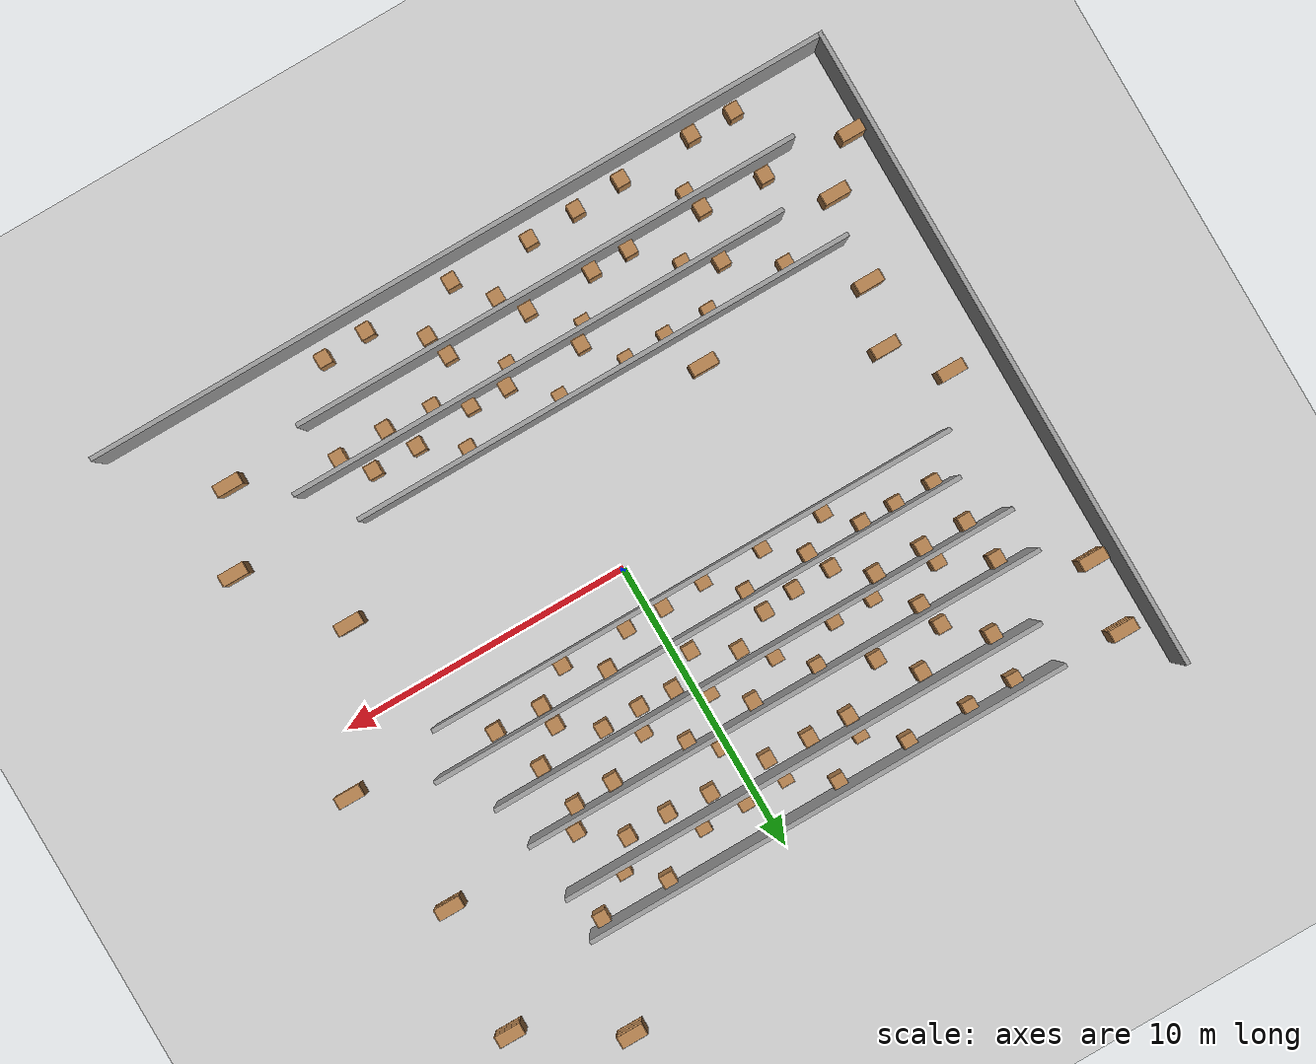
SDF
<sdf version="1.6">
 <world name="default">
  <light name="sun" type="directional">
   <pose>0 0 10 0 -0 0</pose>
   <diffuse>0.8 0.8 0.8 1</diffuse>
   <specular>0.2 0.2 0.2 1</specular>
   <attenuation>
    <range>1000</range>
    <constant>0.9</constant>
    <linear>0.01</linear>
    <quadratic>0.001</quadratic>
   </attenuation>
   <direction>-0.5 0.1 -0.9</direction>
  </light>
  <model name="ground_plane">
   <static>1</static>
   <link name="link">
    <collision name="collision">
     <geometry><plane><normal>0 0 1</normal><size>100 100</size></plane></geometry>
     <surface><friction><ode><mu>100</mu><mu2>50</mu2></ode></friction></surface>
    </collision>
    <visual name="visual">
     <cast_shadows>0</cast_shadows>
     <geometry><plane><normal>0 0 1</normal><size>100 100</size></plane></geometry>
     <material>
      <script><uri>file://media/materials/scripts/gazebo.material</uri><name>Gazebo/Grey</name></script>
     </material>
    </visual>
   </link>
  </model>
  <gravity>0 0 -9.8</gravity>
  <magnetic_field>6e-06 2.3e-05 -4.2e-05</magnetic_field>
  <atmosphere type="adiabatic"/>
  <physics name="default_physics" default="0" type="ode">
   <max_step_size>0.001</max_step_size>
   <real_time_factor>1</real_time_factor>
   <real_time_update_rate>1000</real_time_update_rate>
  </physics>
  <scene><ambient>0.4 0.4 0.4 1</ambient><background>0.7 0.7 0.7 1</background><shadows>1</shadows></scene>
  <audio><device>default</device></audio>
  <spherical_coordinates>
   <surface_model>EARTH_WGS84</surface_model>
   <latitude_deg>0</latitude_deg>
   <longitude_deg>0</longitude_deg>
   <elevation>0</elevation>
   <heading_deg>0</heading_deg>
  </spherical_coordinates>
  <model name="room19">
   <pose>-0.568895 0.02138 0 0 -0 0</pose>
   <link name="Wall_11">
    <collision name="Wall_11_Collision">
     <geometry><box><size>18.25 0.15 2.5</size></box></geometry>
     <pose>0 0 1.25 0 -0 0</pose>
    </collision>
    <visual name="Wall_11_Visual">
     <pose>0 0 1.25 0 -0 0</pose>
     <geometry><box><size>18.25 0.15 2.5</size></box></geometry>
     <material>
      <script><uri>file://media/materials/scripts/gazebo.material</uri><name>Gazebo/Grey</name></script>
      <ambient>1 1 1 1</ambient>
     </material>
     <meta><layer>0</layer></meta>
    </visual>
    <pose>-1.4753 4.35815 0 0 -0 0</pose>
   </link>
   <link name="Wall_13">
    <collision name="Wall_13_Collision">
     <geometry><box><size>18.5 0.15 2.5</size></box></geometry>
     <pose>0 0 1.25 0 -0 0</pose>
    </collision>
    <visual name="Wall_13_Visual">
     <pose>0 0 1.25 0 -0 0</pose>
     <geometry><box><size>18.5 0.15 2.5</size></box></geometry>
     <material>
      <script><uri>file://media/materials/scripts/gazebo.material</uri><name>Gazebo/Grey</name></script>
      <ambient>1 1 1 1</ambient>
     </material>
     <meta><layer>0</layer></meta>
    </visual>
    <pose>-0.450999 2.71825 0 0 -0 0</pose>
   </link>
   <link name="Wall_15">
    <collision name="Wall_15_Collision">
     <geometry><box><size>18.25 0.15 2.5</size></box></geometry>
     <pose>0 0 1.25 0 -0 0</pose>
    </collision>
    <visual name="Wall_15_Visual">
     <pose>0 0 1.25 0 -0 0</pose>
     <geometry><box><size>18.25 0.15 2.5</size></box></geometry>
     <material>
      <script><uri>file://media/materials/scripts/gazebo.material</uri><name>Gazebo/Grey</name></script>
      <ambient>1 1 1 1</ambient>
     </material>
     <meta><layer>0</layer></meta>
    </visual>
    <pose>-1.0521 1.3164 0 0 -0 0</pose>
   </link>
   <link name="Wall_18">
    <collision name="Wall_18_Collision">
     <geometry><box><size>17.5 0.15 2.5</size></box></geometry>
     <pose>0 0 1.25 0 -0 0</pose>
    </collision>
    <visual name="Wall_18_Visual">
     <pose>0 0 1.25 0 -0 0</pose>
     <geometry><box><size>17.5 0.15 2.5</size></box></geometry>
     <material>
      <script><uri>file://media/materials/scripts/gazebo.material</uri><name>Gazebo/Grey</name></script>
      <ambient>1 1 1 1</ambient>
     </material>
     <meta><layer>0</layer></meta>
    </visual>
    <pose>-1.7974 -8.7875 0 0 -0 0</pose>
   </link>
   <link name="Wall_2">
    <collision name="Wall_2_Collision">
     <geometry><box><size>22.25 0.15 2.5</size></box></geometry>
     <pose>0 0 1.25 0 -0 0</pose>
    </collision>
    <visual name="Wall_2_Visual">
     <pose>0 0 1.25 0 -0 0</pose>
     <geometry><box><size>22.25 0.15 2.5</size></box></geometry>
     <material>
      <script><uri>file://media/materials/scripts/gazebo.material</uri><name>Gazebo/Grey</name></script>
      <ambient>1 1 1 1</ambient>
     </material>
     <meta><layer>0</layer></meta>
    </visual>
    <pose>-12.8 -0 0 0 -0 -1.5708</pose>
   </link>
   <link name="Wall_21">
    <collision name="Wall_21_Collision">
     <geometry><box><size>17.25 0.15 2.5</size></box></geometry>
     <pose>0 0 1.25 0 -0 0</pose>
    </collision>
    <visual name="Wall_21_Visual">
     <pose>0 0 1.25 0 -0 0</pose>
     <geometry><box><size>17.25 0.15 2.5</size></box></geometry>
     <material>
      <script><uri>file://media/materials/scripts/gazebo.material</uri><name>Gazebo/Grey</name></script>
      <ambient>1 1 1 1</ambient>
     </material>
     <meta><layer>0</layer></meta>
    </visual>
    <pose>-0.520549 -7.01535 0 0 -0 0</pose>
   </link>
   <link name="Wall_23">
    <collision name="Wall_23_Collision">
     <geometry><box><size>17.25 0.15 2.5</size></box></geometry>
     <pose>0 0 1.25 0 -0 0</pose>
    </collision>
    <visual name="Wall_23_Visual">
     <pose>0 0 1.25 0 -0 0</pose>
     <geometry><box><size>17.25 0.15 2.5</size></box></geometry>
     <material>
      <script><uri>file://media/materials/scripts/gazebo.material</uri><name>Gazebo/Grey</name></script>
      <ambient>1 1 1 1</ambient>
     </material>
     <meta><layer>0</layer></meta>
    </visual>
    <pose>-1.84305 -5.37545 0 0 -0 0</pose>
   </link>
   <link name="Wall_3">
    <collision name="Wall_3_Collision">
     <geometry><box><size>25.75 0.15 2.5</size></box></geometry>
     <pose>0 0 1.25 0 -0 0</pose>
    </collision>
    <visual name="Wall_3_Visual">
     <pose>0 0 1.25 0 -0 0</pose>
     <geometry><box><size>25.75 0.15 2.5</size></box></geometry>
     <material>
      <script><uri>file://media/materials/scripts/gazebo.material</uri><name>Gazebo/Grey</name></script>
      <ambient>1 1 1 1</ambient>
     </material>
     <meta><layer>0</layer></meta>
    </visual>
    <pose>1e-06 -11.05 0 0 -0 0</pose>
   </link>
   <link name="Wall_5">
    <collision name="Wall_5_Collision">
     <geometry><box><size>16.75 0.15 2.5</size></box></geometry>
     <pose>0 0 1.25 0 -0 0</pose>
    </collision>
    <visual name="Wall_5_Visual">
     <pose>0 0 1.25 0 -0 0</pose>
     <geometry><box><size>16.75 0.15 2.5</size></box></geometry>
     <material>
      <script><uri>file://media/materials/scripts/gazebo.material</uri><name>Gazebo/Grey</name></script>
      <ambient>1 1 1 1</ambient>
     </material>
     <meta><layer>0</layer></meta>
    </visual>
    <pose>-1.2202 9.27785 0 0 -0 0</pose>
   </link>
   <link name="Wall_7">
    <collision name="Wall_7_Collision">
     <geometry><box><size>16.75 0.15 2.5</size></box></geometry>
     <pose>0 0 1.25 0 -0 0</pose>
    </collision>
    <visual name="Wall_7_Visual">
     <pose>0 0 1.25 0 -0 0</pose>
     <geometry><box><size>16.75 0.15 2.5</size></box></geometry>
     <material>
      <script><uri>file://media/materials/scripts/gazebo.material</uri><name>Gazebo/Grey</name></script>
      <ambient>1 1 1 1</ambient>
     </material>
     <meta><layer>0</layer></meta>
    </visual>
    <pose>-1.2202 7.79665 0 0 -0 0</pose>
   </link>
   <link name="Wall_9">
    <collision name="Wall_9_Collision">
     <geometry><box><size>18 0.15 2.5</size></box></geometry>
     <pose>0 0 1.25 0 -0 0</pose>
    </collision>
    <visual name="Wall_9_Visual">
     <pose>0 0 1.25 0 -0 0</pose>
     <geometry><box><size>18 0.15 2.5</size></box></geometry>
     <material>
      <script><uri>file://media/materials/scripts/gazebo.material</uri><name>Gazebo/Grey</name></script>
      <ambient>1 1 1 1</ambient>
     </material>
     <meta><layer>0</layer></meta>
    </visual>
    <pose>-1.67965 5.83935 0 0 -0 0</pose>
   </link>
   <static>1</static>
  </model>
  <model name="cabinet">
   <static>1</static>
   <link name="cabinet_bottom_plate">
    <inertial>
     <pose>0 0 -1 0 -0 0</pose>
     <inertia><ixx>2.05</ixx><ixy>0</ixy><ixz>0</ixz><iyy>2.05</iyy><iyz>0</iyz><izz>2.05</izz></inertia>
     <mass>25</mass>
    </inertial>
    <collision name="cabinet_bottom_plate_geom">
     <pose>0 0 0.01 0 -0 0</pose>
     <geometry><box><size>0.45 0.45 0.02</size></box></geometry>
    </collision>
    <visual name="cabinet_bottom_plate_geom_visual">
     <pose>0 0 0.01 0 -0 0</pose>
     <geometry><box><size>0.45 0.45 0.02</size></box></geometry>
     <material>
      <script><uri>file://media/materials/scripts/gazebo.material</uri><name>Gazebo/Wood</name></script>
     </material>
    </visual>
    <collision name="cabinet_bottom_plate_geom_cabinet_back_plate">
     <pose>0.235 0 0.51 0 -0 0</pose>
     <geometry><box><size>0.02 0.45 1.02</size></box></geometry>
    </collision>
    <visual name="cabinet_bottom_plate_geom_cabinet_back_plate_visual">
     <pose>0.235 0 0.51 0 -0 0</pose>
     <geometry><box><size>0.02 0.45 1.02</size></box></geometry>
     <material>
      <script><uri>file://media/materials/scripts/gazebo.material</uri><name>Gazebo/Wood</name></script>
     </material>
    </visual>
    <collision name="cabinet_bottom_plate_geom_cabinet_left_plate">
     <pose>0 0.235 0.51 0 -0 0</pose>
     <geometry><box><size>0.45 0.02 1.02</size></box></geometry>
    </collision>
    <visual name="cabinet_bottom_plate_geom_cabinet_left_plate_visual">
     <pose>0 0.235 0.51 0 -0 0</pose>
     <geometry><box><size>0.45 0.02 1.02</size></box></geometry>
     <material>
      <script><uri>file://media/materials/scripts/gazebo.material</uri><name>Gazebo/Wood</name></script>
     </material>
    </visual>
    <collision name="cabinet_bottom_plate_geom_cabinet_middle_plate">
     <pose>0 0 0.51 0 -0 0</pose>
     <geometry><box><size>0.45 0.45 0.02</size></box></geometry>
    </collision>
    <visual name="cabinet_bottom_plate_geom_cabinet_middle_plate_visual">
     <pose>0 0 0.51 0 -0 0</pose>
     <geometry><box><size>0.45 0.45 0.02</size></box></geometry>
     <material>
      <script><uri>file://media/materials/scripts/gazebo.material</uri><name>Gazebo/Wood</name></script>
     </material>
    </visual>
    <collision name="cabinet_bottom_plate_geom_cabinet_right_plate">
     <pose>0 -0.235 0.51 0 -0 0</pose>
     <geometry><box><size>0.45 0.02 1.02</size></box></geometry>
    </collision>
    <visual name="cabinet_bottom_plate_geom_cabinet_right_plate_visual">
     <pose>0 -0.235 0.51 0 -0 0</pose>
     <geometry><box><size>0.45 0.02 1.02</size></box></geometry>
     <material>
      <script><uri>file://media/materials/scripts/gazebo.material</uri><name>Gazebo/Wood</name></script>
     </material>
    </visual>
    <collision name="cabinet_bottom_plate_geom_cabinet_top_plate">
     <pose>0 0 1.01 0 -0 0</pose>
     <geometry><box><size>0.45 0.45 0.02</size></box></geometry>
    </collision>
    <visual name="cabinet_bottom_plate_geom_cabinet_top_plate_visual">
     <pose>0 0 1.01 0 -0 0</pose>
     <geometry><box><size>0.45 0.45 0.02</size></box></geometry>
     <material>
      <script><uri>file://media/materials/scripts/gazebo.material</uri><name>Gazebo/Wood</name></script>
     </material>
    </visual>
   </link>
   <pose>-10.0798 -10.5343 0 0 -0 0</pose>
  </model>
  <model name="cabinet_0">
   <static>1</static>
   <link name="cabinet_bottom_plate">
    <inertial>
     <pose>0 0 -1 0 -0 0</pose>
     <inertia><ixx>2.05</ixx><ixy>0</ixy><ixz>0</ixz><iyy>2.05</iyy><iyz>0</iyz><izz>2.05</izz></inertia>
     <mass>25</mass>
    </inertial>
    <collision name="cabinet_bottom_plate_geom">
     <pose>0 0 0.01 0 -0 0</pose>
     <geometry><box><size>0.45 0.45 0.02</size></box></geometry>
    </collision>
    <visual name="cabinet_bottom_plate_geom_visual">
     <pose>0 0 0.01 0 -0 0</pose>
     <geometry><box><size>0.45 0.45 0.02</size></box></geometry>
     <material>
      <script><uri>file://media/materials/scripts/gazebo.material</uri><name>Gazebo/Wood</name></script>
     </material>
    </visual>
    <collision name="cabinet_bottom_plate_geom_cabinet_back_plate">
     <pose>0.235 0 0.51 0 -0 0</pose>
     <geometry><box><size>0.02 0.45 1.02</size></box></geometry>
    </collision>
    <visual name="cabinet_bottom_plate_geom_cabinet_back_plate_visual">
     <pose>0.235 0 0.51 0 -0 0</pose>
     <geometry><box><size>0.02 0.45 1.02</size></box></geometry>
     <material>
      <script><uri>file://media/materials/scripts/gazebo.material</uri><name>Gazebo/Wood</name></script>
     </material>
    </visual>
    <collision name="cabinet_bottom_plate_geom_cabinet_left_plate">
     <pose>0 0.235 0.51 0 -0 0</pose>
     <geometry><box><size>0.45 0.02 1.02</size></box></geometry>
    </collision>
    <visual name="cabinet_bottom_plate_geom_cabinet_left_plate_visual">
     <pose>0 0.235 0.51 0 -0 0</pose>
     <geometry><box><size>0.45 0.02 1.02</size></box></geometry>
     <material>
      <script><uri>file://media/materials/scripts/gazebo.material</uri><name>Gazebo/Wood</name></script>
     </material>
    </visual>
    <collision name="cabinet_bottom_plate_geom_cabinet_middle_plate">
     <pose>0 0 0.51 0 -0 0</pose>
     <geometry><box><size>0.45 0.45 0.02</size></box></geometry>
    </collision>
    <visual name="cabinet_bottom_plate_geom_cabinet_middle_plate_visual">
     <pose>0 0 0.51 0 -0 0</pose>
     <geometry><box><size>0.45 0.45 0.02</size></box></geometry>
     <material>
      <script><uri>file://media/materials/scripts/gazebo.material</uri><name>Gazebo/Wood</name></script>
     </material>
    </visual>
    <collision name="cabinet_bottom_plate_geom_cabinet_right_plate">
     <pose>0 -0.235 0.51 0 -0 0</pose>
     <geometry><box><size>0.45 0.02 1.02</size></box></geometry>
    </collision>
    <visual name="cabinet_bottom_plate_geom_cabinet_right_plate_visual">
     <pose>0 -0.235 0.51 0 -0 0</pose>
     <geometry><box><size>0.45 0.02 1.02</size></box></geometry>
     <material>
      <script><uri>file://media/materials/scripts/gazebo.material</uri><name>Gazebo/Wood</name></script>
     </material>
    </visual>
    <collision name="cabinet_bottom_plate_geom_cabinet_top_plate">
     <pose>0 0 1.01 0 -0 0</pose>
     <geometry><box><size>0.45 0.45 0.02</size></box></geometry>
    </collision>
    <visual name="cabinet_bottom_plate_geom_cabinet_top_plate_visual">
     <pose>0 0 1.01 0 -0 0</pose>
     <geometry><box><size>0.45 0.45 0.02</size></box></geometry>
     <material>
      <script><uri>file://media/materials/scripts/gazebo.material</uri><name>Gazebo/Wood</name></script>
     </material>
    </visual>
   </link>
   <pose>-8.57907 -10.5675 0 0 -0 0</pose>
  </model>
  <model name="cabinet_1">
   <static>1</static>
   <link name="cabinet_bottom_plate">
    <inertial>
     <pose>0 0 -1 0 -0 0</pose>
     <inertia><ixx>2.05</ixx><ixy>0</ixy><ixz>0</ixz><iyy>2.05</iyy><iyz>0</iyz><izz>2.05</izz></inertia>
     <mass>25</mass>
    </inertial>
    <collision name="cabinet_bottom_plate_geom">
     <pose>0 0 0.01 0 -0 0</pose>
     <geometry><box><size>0.45 0.45 0.02</size></box></geometry>
    </collision>
    <visual name="cabinet_bottom_plate_geom_visual">
     <pose>0 0 0.01 0 -0 0</pose>
     <geometry><box><size>0.45 0.45 0.02</size></box></geometry>
     <material>
      <script><uri>file://media/materials/scripts/gazebo.material</uri><name>Gazebo/Wood</name></script>
     </material>
    </visual>
    <collision name="cabinet_bottom_plate_geom_cabinet_back_plate">
     <pose>0.235 0 0.51 0 -0 0</pose>
     <geometry><box><size>0.02 0.45 1.02</size></box></geometry>
    </collision>
    <visual name="cabinet_bottom_plate_geom_cabinet_back_plate_visual">
     <pose>0.235 0 0.51 0 -0 0</pose>
     <geometry><box><size>0.02 0.45 1.02</size></box></geometry>
     <material>
      <script><uri>file://media/materials/scripts/gazebo.material</uri><name>Gazebo/Wood</name></script>
     </material>
    </visual>
    <collision name="cabinet_bottom_plate_geom_cabinet_left_plate">
     <pose>0 0.235 0.51 0 -0 0</pose>
     <geometry><box><size>0.45 0.02 1.02</size></box></geometry>
    </collision>
    <visual name="cabinet_bottom_plate_geom_cabinet_left_plate_visual">
     <pose>0 0.235 0.51 0 -0 0</pose>
     <geometry><box><size>0.45 0.02 1.02</size></box></geometry>
     <material>
      <script><uri>file://media/materials/scripts/gazebo.material</uri><name>Gazebo/Wood</name></script>
     </material>
    </visual>
    <collision name="cabinet_bottom_plate_geom_cabinet_middle_plate">
     <pose>0 0 0.51 0 -0 0</pose>
     <geometry><box><size>0.45 0.45 0.02</size></box></geometry>
    </collision>
    <visual name="cabinet_bottom_plate_geom_cabinet_middle_plate_visual">
     <pose>0 0 0.51 0 -0 0</pose>
     <geometry><box><size>0.45 0.45 0.02</size></box></geometry>
     <material>
      <script><uri>file://media/materials/scripts/gazebo.material</uri><name>Gazebo/Wood</name></script>
     </material>
    </visual>
    <collision name="cabinet_bottom_plate_geom_cabinet_right_plate">
     <pose>0 -0.235 0.51 0 -0 0</pose>
     <geometry><box><size>0.45 0.02 1.02</size></box></geometry>
    </collision>
    <visual name="cabinet_bottom_plate_geom_cabinet_right_plate_visual">
     <pose>0 -0.235 0.51 0 -0 0</pose>
     <geometry><box><size>0.45 0.02 1.02</size></box></geometry>
     <material>
      <script><uri>file://media/materials/scripts/gazebo.material</uri><name>Gazebo/Wood</name></script>
     </material>
    </visual>
    <collision name="cabinet_bottom_plate_geom_cabinet_top_plate">
     <pose>0 0 1.01 0 -0 0</pose>
     <geometry><box><size>0.45 0.45 0.02</size></box></geometry>
    </collision>
    <visual name="cabinet_bottom_plate_geom_cabinet_top_plate_visual">
     <pose>0 0 1.01 0 -0 0</pose>
     <geometry><box><size>0.45 0.45 0.02</size></box></geometry>
     <material>
      <script><uri>file://media/materials/scripts/gazebo.material</uri><name>Gazebo/Wood</name></script>
     </material>
    </visual>
   </link>
   <pose>-7.53235 -9.08887 0 0 -0 0</pose>
  </model>
  <model name="cabinet_2">
   <static>1</static>
   <link name="cabinet_bottom_plate">
    <inertial>
     <pose>0 0 -1 0 -0 0</pose>
     <inertia><ixx>2.05</ixx><ixy>0</ixy><ixz>0</ixz><iyy>2.05</iyy><iyz>0</iyz><izz>2.05</izz></inertia>
     <mass>25</mass>
    </inertial>
    <collision name="cabinet_bottom_plate_geom">
     <pose>0 0 0.01 0 -0 0</pose>
     <geometry><box><size>0.45 0.45 0.02</size></box></geometry>
    </collision>
    <visual name="cabinet_bottom_plate_geom_visual">
     <pose>0 0 0.01 0 -0 0</pose>
     <geometry><box><size>0.45 0.45 0.02</size></box></geometry>
     <material>
      <script><uri>file://media/materials/scripts/gazebo.material</uri><name>Gazebo/Wood</name></script>
     </material>
    </visual>
    <collision name="cabinet_bottom_plate_geom_cabinet_back_plate">
     <pose>0.235 0 0.51 0 -0 0</pose>
     <geometry><box><size>0.02 0.45 1.02</size></box></geometry>
    </collision>
    <visual name="cabinet_bottom_plate_geom_cabinet_back_plate_visual">
     <pose>0.235 0 0.51 0 -0 0</pose>
     <geometry><box><size>0.02 0.45 1.02</size></box></geometry>
     <material>
      <script><uri>file://media/materials/scripts/gazebo.material</uri><name>Gazebo/Wood</name></script>
     </material>
    </visual>
    <collision name="cabinet_bottom_plate_geom_cabinet_left_plate">
     <pose>0 0.235 0.51 0 -0 0</pose>
     <geometry><box><size>0.45 0.02 1.02</size></box></geometry>
    </collision>
    <visual name="cabinet_bottom_plate_geom_cabinet_left_plate_visual">
     <pose>0 0.235 0.51 0 -0 0</pose>
     <geometry><box><size>0.45 0.02 1.02</size></box></geometry>
     <material>
      <script><uri>file://media/materials/scripts/gazebo.material</uri><name>Gazebo/Wood</name></script>
     </material>
    </visual>
    <collision name="cabinet_bottom_plate_geom_cabinet_middle_plate">
     <pose>0 0 0.51 0 -0 0</pose>
     <geometry><box><size>0.45 0.45 0.02</size></box></geometry>
    </collision>
    <visual name="cabinet_bottom_plate_geom_cabinet_middle_plate_visual">
     <pose>0 0 0.51 0 -0 0</pose>
     <geometry><box><size>0.45 0.45 0.02</size></box></geometry>
     <material>
      <script><uri>file://media/materials/scripts/gazebo.material</uri><name>Gazebo/Wood</name></script>
     </material>
    </visual>
    <collision name="cabinet_bottom_plate_geom_cabinet_right_plate">
     <pose>0 -0.235 0.51 0 -0 0</pose>
     <geometry><box><size>0.45 0.02 1.02</size></box></geometry>
    </collision>
    <visual name="cabinet_bottom_plate_geom_cabinet_right_plate_visual">
     <pose>0 -0.235 0.51 0 -0 0</pose>
     <geometry><box><size>0.45 0.02 1.02</size></box></geometry>
     <material>
      <script><uri>file://media/materials/scripts/gazebo.material</uri><name>Gazebo/Wood</name></script>
     </material>
    </visual>
    <collision name="cabinet_bottom_plate_geom_cabinet_top_plate">
     <pose>0 0 1.01 0 -0 0</pose>
     <geometry><box><size>0.45 0.45 0.02</size></box></geometry>
    </collision>
    <visual name="cabinet_bottom_plate_geom_cabinet_top_plate_visual">
     <pose>0 0 1.01 0 -0 0</pose>
     <geometry><box><size>0.45 0.45 0.02</size></box></geometry>
     <material>
      <script><uri>file://media/materials/scripts/gazebo.material</uri><name>Gazebo/Wood</name></script>
     </material>
    </visual>
   </link>
   <pose>-5.99781 -10.4652 0 0 -0 0</pose>
  </model>
  <model name="cabinet_3">
   <static>1</static>
   <link name="cabinet_bottom_plate">
    <inertial>
     <pose>0 0 -1 0 -0 0</pose>
     <inertia><ixx>2.05</ixx><ixy>0</ixy><ixz>0</ixz><iyy>2.05</iyy><iyz>0</iyz><izz>2.05</izz></inertia>
     <mass>25</mass>
    </inertial>
    <collision name="cabinet_bottom_plate_geom">
     <pose>0 0 0.01 0 -0 0</pose>
     <geometry><box><size>0.45 0.45 0.02</size></box></geometry>
    </collision>
    <visual name="cabinet_bottom_plate_geom_visual">
     <pose>0 0 0.01 0 -0 0</pose>
     <geometry><box><size>0.45 0.45 0.02</size></box></geometry>
     <material>
      <script><uri>file://media/materials/scripts/gazebo.material</uri><name>Gazebo/Wood</name></script>
     </material>
    </visual>
    <collision name="cabinet_bottom_plate_geom_cabinet_back_plate">
     <pose>0.235 0 0.51 0 -0 0</pose>
     <geometry><box><size>0.02 0.45 1.02</size></box></geometry>
    </collision>
    <visual name="cabinet_bottom_plate_geom_cabinet_back_plate_visual">
     <pose>0.235 0 0.51 0 -0 0</pose>
     <geometry><box><size>0.02 0.45 1.02</size></box></geometry>
     <material>
      <script><uri>file://media/materials/scripts/gazebo.material</uri><name>Gazebo/Wood</name></script>
     </material>
    </visual>
    <collision name="cabinet_bottom_plate_geom_cabinet_left_plate">
     <pose>0 0.235 0.51 0 -0 0</pose>
     <geometry><box><size>0.45 0.02 1.02</size></box></geometry>
    </collision>
    <visual name="cabinet_bottom_plate_geom_cabinet_left_plate_visual">
     <pose>0 0.235 0.51 0 -0 0</pose>
     <geometry><box><size>0.45 0.02 1.02</size></box></geometry>
     <material>
      <script><uri>file://media/materials/scripts/gazebo.material</uri><name>Gazebo/Wood</name></script>
     </material>
    </visual>
    <collision name="cabinet_bottom_plate_geom_cabinet_middle_plate">
     <pose>0 0 0.51 0 -0 0</pose>
     <geometry><box><size>0.45 0.45 0.02</size></box></geometry>
    </collision>
    <visual name="cabinet_bottom_plate_geom_cabinet_middle_plate_visual">
     <pose>0 0 0.51 0 -0 0</pose>
     <geometry><box><size>0.45 0.45 0.02</size></box></geometry>
     <material>
      <script><uri>file://media/materials/scripts/gazebo.material</uri><name>Gazebo/Wood</name></script>
     </material>
    </visual>
    <collision name="cabinet_bottom_plate_geom_cabinet_right_plate">
     <pose>0 -0.235 0.51 0 -0 0</pose>
     <geometry><box><size>0.45 0.02 1.02</size></box></geometry>
    </collision>
    <visual name="cabinet_bottom_plate_geom_cabinet_right_plate_visual">
     <pose>0 -0.235 0.51 0 -0 0</pose>
     <geometry><box><size>0.45 0.02 1.02</size></box></geometry>
     <material>
      <script><uri>file://media/materials/scripts/gazebo.material</uri><name>Gazebo/Wood</name></script>
     </material>
    </visual>
    <collision name="cabinet_bottom_plate_geom_cabinet_top_plate">
     <pose>0 0 1.01 0 -0 0</pose>
     <geometry><box><size>0.45 0.45 0.02</size></box></geometry>
    </collision>
    <visual name="cabinet_bottom_plate_geom_cabinet_top_plate_visual">
     <pose>0 0 1.01 0 -0 0</pose>
     <geometry><box><size>0.45 0.45 0.02</size></box></geometry>
     <material>
      <script><uri>file://media/materials/scripts/gazebo.material</uri><name>Gazebo/Wood</name></script>
     </material>
    </visual>
   </link>
   <pose>-4.32371 -10.3615 0 0 -0 0</pose>
  </model>
  <model name="cabinet_4">
   <static>1</static>
   <link name="cabinet_bottom_plate">
    <inertial>
     <pose>0 0 -1 0 -0 0</pose>
     <inertia><ixx>2.05</ixx><ixy>0</ixy><ixz>0</ixz><iyy>2.05</iyy><iyz>0</iyz><izz>2.05</izz></inertia>
     <mass>25</mass>
    </inertial>
    <collision name="cabinet_bottom_plate_geom">
     <pose>0 0 0.01 0 -0 0</pose>
     <geometry><box><size>0.45 0.45 0.02</size></box></geometry>
    </collision>
    <visual name="cabinet_bottom_plate_geom_visual">
     <pose>0 0 0.01 0 -0 0</pose>
     <geometry><box><size>0.45 0.45 0.02</size></box></geometry>
     <material>
      <script><uri>file://media/materials/scripts/gazebo.material</uri><name>Gazebo/Wood</name></script>
     </material>
    </visual>
    <collision name="cabinet_bottom_plate_geom_cabinet_back_plate">
     <pose>0.235 0 0.51 0 -0 0</pose>
     <geometry><box><size>0.02 0.45 1.02</size></box></geometry>
    </collision>
    <visual name="cabinet_bottom_plate_geom_cabinet_back_plate_visual">
     <pose>0.235 0 0.51 0 -0 0</pose>
     <geometry><box><size>0.02 0.45 1.02</size></box></geometry>
     <material>
      <script><uri>file://media/materials/scripts/gazebo.material</uri><name>Gazebo/Wood</name></script>
     </material>
    </visual>
    <collision name="cabinet_bottom_plate_geom_cabinet_left_plate">
     <pose>0 0.235 0.51 0 -0 0</pose>
     <geometry><box><size>0.45 0.02 1.02</size></box></geometry>
    </collision>
    <visual name="cabinet_bottom_plate_geom_cabinet_left_plate_visual">
     <pose>0 0.235 0.51 0 -0 0</pose>
     <geometry><box><size>0.45 0.02 1.02</size></box></geometry>
     <material>
      <script><uri>file://media/materials/scripts/gazebo.material</uri><name>Gazebo/Wood</name></script>
     </material>
    </visual>
    <collision name="cabinet_bottom_plate_geom_cabinet_middle_plate">
     <pose>0 0 0.51 0 -0 0</pose>
     <geometry><box><size>0.45 0.45 0.02</size></box></geometry>
    </collision>
    <visual name="cabinet_bottom_plate_geom_cabinet_middle_plate_visual">
     <pose>0 0 0.51 0 -0 0</pose>
     <geometry><box><size>0.45 0.45 0.02</size></box></geometry>
     <material>
      <script><uri>file://media/materials/scripts/gazebo.material</uri><name>Gazebo/Wood</name></script>
     </material>
    </visual>
    <collision name="cabinet_bottom_plate_geom_cabinet_right_plate">
     <pose>0 -0.235 0.51 0 -0 0</pose>
     <geometry><box><size>0.45 0.02 1.02</size></box></geometry>
    </collision>
    <visual name="cabinet_bottom_plate_geom_cabinet_right_plate_visual">
     <pose>0 -0.235 0.51 0 -0 0</pose>
     <geometry><box><size>0.45 0.02 1.02</size></box></geometry>
     <material>
      <script><uri>file://media/materials/scripts/gazebo.material</uri><name>Gazebo/Wood</name></script>
     </material>
    </visual>
    <collision name="cabinet_bottom_plate_geom_cabinet_top_plate">
     <pose>0 0 1.01 0 -0 0</pose>
     <geometry><box><size>0.45 0.45 0.02</size></box></geometry>
    </collision>
    <visual name="cabinet_bottom_plate_geom_cabinet_top_plate_visual">
     <pose>0 0 1.01 0 -0 0</pose>
     <geometry><box><size>0.45 0.45 0.02</size></box></geometry>
     <material>
      <script><uri>file://media/materials/scripts/gazebo.material</uri><name>Gazebo/Wood</name></script>
     </material>
    </visual>
   </link>
   <pose>-2.61379 -10.2875 0 0 -0 0</pose>
  </model>
  <model name="cabinet_5">
   <static>1</static>
   <link name="cabinet_bottom_plate">
    <inertial>
     <pose>0 0 -1 0 -0 0</pose>
     <inertia><ixx>2.05</ixx><ixy>0</ixy><ixz>0</ixz><iyy>2.05</iyy><iyz>0</iyz><izz>2.05</izz></inertia>
     <mass>25</mass>
    </inertial>
    <collision name="cabinet_bottom_plate_geom">
     <pose>0 0 0.01 0 -0 0</pose>
     <geometry><box><size>0.45 0.45 0.02</size></box></geometry>
    </collision>
    <visual name="cabinet_bottom_plate_geom_visual">
     <pose>0 0 0.01 0 -0 0</pose>
     <geometry><box><size>0.45 0.45 0.02</size></box></geometry>
     <material>
      <script><uri>file://media/materials/scripts/gazebo.material</uri><name>Gazebo/Wood</name></script>
     </material>
    </visual>
    <collision name="cabinet_bottom_plate_geom_cabinet_back_plate">
     <pose>0.235 0 0.51 0 -0 0</pose>
     <geometry><box><size>0.02 0.45 1.02</size></box></geometry>
    </collision>
    <visual name="cabinet_bottom_plate_geom_cabinet_back_plate_visual">
     <pose>0.235 0 0.51 0 -0 0</pose>
     <geometry><box><size>0.02 0.45 1.02</size></box></geometry>
     <material>
      <script><uri>file://media/materials/scripts/gazebo.material</uri><name>Gazebo/Wood</name></script>
     </material>
    </visual>
    <collision name="cabinet_bottom_plate_geom_cabinet_left_plate">
     <pose>0 0.235 0.51 0 -0 0</pose>
     <geometry><box><size>0.45 0.02 1.02</size></box></geometry>
    </collision>
    <visual name="cabinet_bottom_plate_geom_cabinet_left_plate_visual">
     <pose>0 0.235 0.51 0 -0 0</pose>
     <geometry><box><size>0.45 0.02 1.02</size></box></geometry>
     <material>
      <script><uri>file://media/materials/scripts/gazebo.material</uri><name>Gazebo/Wood</name></script>
     </material>
    </visual>
    <collision name="cabinet_bottom_plate_geom_cabinet_middle_plate">
     <pose>0 0 0.51 0 -0 0</pose>
     <geometry><box><size>0.45 0.45 0.02</size></box></geometry>
    </collision>
    <visual name="cabinet_bottom_plate_geom_cabinet_middle_plate_visual">
     <pose>0 0 0.51 0 -0 0</pose>
     <geometry><box><size>0.45 0.45 0.02</size></box></geometry>
     <material>
      <script><uri>file://media/materials/scripts/gazebo.material</uri><name>Gazebo/Wood</name></script>
     </material>
    </visual>
    <collision name="cabinet_bottom_plate_geom_cabinet_right_plate">
     <pose>0 -0.235 0.51 0 -0 0</pose>
     <geometry><box><size>0.45 0.02 1.02</size></box></geometry>
    </collision>
    <visual name="cabinet_bottom_plate_geom_cabinet_right_plate_visual">
     <pose>0 -0.235 0.51 0 -0 0</pose>
     <geometry><box><size>0.45 0.02 1.02</size></box></geometry>
     <material>
      <script><uri>file://media/materials/scripts/gazebo.material</uri><name>Gazebo/Wood</name></script>
     </material>
    </visual>
    <collision name="cabinet_bottom_plate_geom_cabinet_top_plate">
     <pose>0 0 1.01 0 -0 0</pose>
     <geometry><box><size>0.45 0.45 0.02</size></box></geometry>
    </collision>
    <visual name="cabinet_bottom_plate_geom_cabinet_top_plate_visual">
     <pose>0 0 1.01 0 -0 0</pose>
     <geometry><box><size>0.45 0.45 0.02</size></box></geometry>
     <material>
      <script><uri>file://media/materials/scripts/gazebo.material</uri><name>Gazebo/Wood</name></script>
     </material>
    </visual>
   </link>
   <pose>-0.832207 -9.25202 0 0 -0 0</pose>
  </model>
  <model name="cabinet_6">
   <static>1</static>
   <link name="cabinet_bottom_plate">
    <inertial>
     <pose>0 0 -1 0 -0 0</pose>
     <inertia><ixx>2.05</ixx><ixy>0</ixy><ixz>0</ixz><iyy>2.05</iyy><iyz>0</iyz><izz>2.05</izz></inertia>
     <mass>25</mass>
    </inertial>
    <collision name="cabinet_bottom_plate_geom">
     <pose>0 0 0.01 0 -0 0</pose>
     <geometry><box><size>0.45 0.45 0.02</size></box></geometry>
    </collision>
    <visual name="cabinet_bottom_plate_geom_visual">
     <pose>0 0 0.01 0 -0 0</pose>
     <geometry><box><size>0.45 0.45 0.02</size></box></geometry>
     <material>
      <script><uri>file://media/materials/scripts/gazebo.material</uri><name>Gazebo/Wood</name></script>
     </material>
    </visual>
    <collision name="cabinet_bottom_plate_geom_cabinet_back_plate">
     <pose>0.235 0 0.51 0 -0 0</pose>
     <geometry><box><size>0.02 0.45 1.02</size></box></geometry>
    </collision>
    <visual name="cabinet_bottom_plate_geom_cabinet_back_plate_visual">
     <pose>0.235 0 0.51 0 -0 0</pose>
     <geometry><box><size>0.02 0.45 1.02</size></box></geometry>
     <material>
      <script><uri>file://media/materials/scripts/gazebo.material</uri><name>Gazebo/Wood</name></script>
     </material>
    </visual>
    <collision name="cabinet_bottom_plate_geom_cabinet_left_plate">
     <pose>0 0.235 0.51 0 -0 0</pose>
     <geometry><box><size>0.45 0.02 1.02</size></box></geometry>
    </collision>
    <visual name="cabinet_bottom_plate_geom_cabinet_left_plate_visual">
     <pose>0 0.235 0.51 0 -0 0</pose>
     <geometry><box><size>0.45 0.02 1.02</size></box></geometry>
     <material>
      <script><uri>file://media/materials/scripts/gazebo.material</uri><name>Gazebo/Wood</name></script>
     </material>
    </visual>
    <collision name="cabinet_bottom_plate_geom_cabinet_middle_plate">
     <pose>0 0 0.51 0 -0 0</pose>
     <geometry><box><size>0.45 0.45 0.02</size></box></geometry>
    </collision>
    <visual name="cabinet_bottom_plate_geom_cabinet_middle_plate_visual">
     <pose>0 0 0.51 0 -0 0</pose>
     <geometry><box><size>0.45 0.45 0.02</size></box></geometry>
     <material>
      <script><uri>file://media/materials/scripts/gazebo.material</uri><name>Gazebo/Wood</name></script>
     </material>
    </visual>
    <collision name="cabinet_bottom_plate_geom_cabinet_right_plate">
     <pose>0 -0.235 0.51 0 -0 0</pose>
     <geometry><box><size>0.45 0.02 1.02</size></box></geometry>
    </collision>
    <visual name="cabinet_bottom_plate_geom_cabinet_right_plate_visual">
     <pose>0 -0.235 0.51 0 -0 0</pose>
     <geometry><box><size>0.45 0.02 1.02</size></box></geometry>
     <material>
      <script><uri>file://media/materials/scripts/gazebo.material</uri><name>Gazebo/Wood</name></script>
     </material>
    </visual>
    <collision name="cabinet_bottom_plate_geom_cabinet_top_plate">
     <pose>0 0 1.01 0 -0 0</pose>
     <geometry><box><size>0.45 0.45 0.02</size></box></geometry>
    </collision>
    <visual name="cabinet_bottom_plate_geom_cabinet_top_plate_visual">
     <pose>0 0 1.01 0 -0 0</pose>
     <geometry><box><size>0.45 0.45 0.02</size></box></geometry>
     <material>
      <script><uri>file://media/materials/scripts/gazebo.material</uri><name>Gazebo/Wood</name></script>
     </material>
    </visual>
   </link>
   <pose>0.135041 -10.3908 0 0 -0 0</pose>
  </model>
  <model name="cabinet_7">
   <static>1</static>
   <link name="cabinet_bottom_plate">
    <inertial>
     <pose>0 0 -1 0 -0 0</pose>
     <inertia><ixx>2.05</ixx><ixy>0</ixy><ixz>0</ixz><iyy>2.05</iyy><iyz>0</iyz><izz>2.05</izz></inertia>
     <mass>25</mass>
    </inertial>
    <collision name="cabinet_bottom_plate_geom">
     <pose>0 0 0.01 0 -0 0</pose>
     <geometry><box><size>0.45 0.45 0.02</size></box></geometry>
    </collision>
    <visual name="cabinet_bottom_plate_geom_visual">
     <pose>0 0 0.01 0 -0 0</pose>
     <geometry><box><size>0.45 0.45 0.02</size></box></geometry>
     <material>
      <script><uri>file://media/materials/scripts/gazebo.material</uri><name>Gazebo/Wood</name></script>
     </material>
    </visual>
    <collision name="cabinet_bottom_plate_geom_cabinet_back_plate">
     <pose>0.235 0 0.51 0 -0 0</pose>
     <geometry><box><size>0.02 0.45 1.02</size></box></geometry>
    </collision>
    <visual name="cabinet_bottom_plate_geom_cabinet_back_plate_visual">
     <pose>0.235 0 0.51 0 -0 0</pose>
     <geometry><box><size>0.02 0.45 1.02</size></box></geometry>
     <material>
      <script><uri>file://media/materials/scripts/gazebo.material</uri><name>Gazebo/Wood</name></script>
     </material>
    </visual>
    <collision name="cabinet_bottom_plate_geom_cabinet_left_plate">
     <pose>0 0.235 0.51 0 -0 0</pose>
     <geometry><box><size>0.45 0.02 1.02</size></box></geometry>
    </collision>
    <visual name="cabinet_bottom_plate_geom_cabinet_left_plate_visual">
     <pose>0 0.235 0.51 0 -0 0</pose>
     <geometry><box><size>0.45 0.02 1.02</size></box></geometry>
     <material>
      <script><uri>file://media/materials/scripts/gazebo.material</uri><name>Gazebo/Wood</name></script>
     </material>
    </visual>
    <collision name="cabinet_bottom_plate_geom_cabinet_middle_plate">
     <pose>0 0 0.51 0 -0 0</pose>
     <geometry><box><size>0.45 0.45 0.02</size></box></geometry>
    </collision>
    <visual name="cabinet_bottom_plate_geom_cabinet_middle_plate_visual">
     <pose>0 0 0.51 0 -0 0</pose>
     <geometry><box><size>0.45 0.45 0.02</size></box></geometry>
     <material>
      <script><uri>file://media/materials/scripts/gazebo.material</uri><name>Gazebo/Wood</name></script>
     </material>
    </visual>
    <collision name="cabinet_bottom_plate_geom_cabinet_right_plate">
     <pose>0 -0.235 0.51 0 -0 0</pose>
     <geometry><box><size>0.45 0.02 1.02</size></box></geometry>
    </collision>
    <visual name="cabinet_bottom_plate_geom_cabinet_right_plate_visual">
     <pose>0 -0.235 0.51 0 -0 0</pose>
     <geometry><box><size>0.45 0.02 1.02</size></box></geometry>
     <material>
      <script><uri>file://media/materials/scripts/gazebo.material</uri><name>Gazebo/Wood</name></script>
     </material>
    </visual>
    <collision name="cabinet_bottom_plate_geom_cabinet_top_plate">
     <pose>0 0 1.01 0 -0 0</pose>
     <geometry><box><size>0.45 0.45 0.02</size></box></geometry>
    </collision>
    <visual name="cabinet_bottom_plate_geom_cabinet_top_plate_visual">
     <pose>0 0 1.01 0 -0 0</pose>
     <geometry><box><size>0.45 0.45 0.02</size></box></geometry>
     <material>
      <script><uri>file://media/materials/scripts/gazebo.material</uri><name>Gazebo/Wood</name></script>
     </material>
    </visual>
   </link>
   <pose>1.62665 -9.28432 0 0 -0 0</pose>
  </model>
  <model name="cabinet_8">
   <static>1</static>
   <link name="cabinet_bottom_plate">
    <inertial>
     <pose>0 0 -1 0 -0 0</pose>
     <inertia><ixx>2.05</ixx><ixy>0</ixy><ixz>0</ixz><iyy>2.05</iyy><iyz>0</iyz><izz>2.05</izz></inertia>
     <mass>25</mass>
    </inertial>
    <collision name="cabinet_bottom_plate_geom">
     <pose>0 0 0.01 0 -0 0</pose>
     <geometry><box><size>0.45 0.45 0.02</size></box></geometry>
    </collision>
    <visual name="cabinet_bottom_plate_geom_visual">
     <pose>0 0 0.01 0 -0 0</pose>
     <geometry><box><size>0.45 0.45 0.02</size></box></geometry>
     <material>
      <script><uri>file://media/materials/scripts/gazebo.material</uri><name>Gazebo/Wood</name></script>
     </material>
    </visual>
    <collision name="cabinet_bottom_plate_geom_cabinet_back_plate">
     <pose>0.235 0 0.51 0 -0 0</pose>
     <geometry><box><size>0.02 0.45 1.02</size></box></geometry>
    </collision>
    <visual name="cabinet_bottom_plate_geom_cabinet_back_plate_visual">
     <pose>0.235 0 0.51 0 -0 0</pose>
     <geometry><box><size>0.02 0.45 1.02</size></box></geometry>
     <material>
      <script><uri>file://media/materials/scripts/gazebo.material</uri><name>Gazebo/Wood</name></script>
     </material>
    </visual>
    <collision name="cabinet_bottom_plate_geom_cabinet_left_plate">
     <pose>0 0.235 0.51 0 -0 0</pose>
     <geometry><box><size>0.45 0.02 1.02</size></box></geometry>
    </collision>
    <visual name="cabinet_bottom_plate_geom_cabinet_left_plate_visual">
     <pose>0 0.235 0.51 0 -0 0</pose>
     <geometry><box><size>0.45 0.02 1.02</size></box></geometry>
     <material>
      <script><uri>file://media/materials/scripts/gazebo.material</uri><name>Gazebo/Wood</name></script>
     </material>
    </visual>
    <collision name="cabinet_bottom_plate_geom_cabinet_middle_plate">
     <pose>0 0 0.51 0 -0 0</pose>
     <geometry><box><size>0.45 0.45 0.02</size></box></geometry>
    </collision>
    <visual name="cabinet_bottom_plate_geom_cabinet_middle_plate_visual">
     <pose>0 0 0.51 0 -0 0</pose>
     <geometry><box><size>0.45 0.45 0.02</size></box></geometry>
     <material>
      <script><uri>file://media/materials/scripts/gazebo.material</uri><name>Gazebo/Wood</name></script>
     </material>
    </visual>
    <collision name="cabinet_bottom_plate_geom_cabinet_right_plate">
     <pose>0 -0.235 0.51 0 -0 0</pose>
     <geometry><box><size>0.45 0.02 1.02</size></box></geometry>
    </collision>
    <visual name="cabinet_bottom_plate_geom_cabinet_right_plate_visual">
     <pose>0 -0.235 0.51 0 -0 0</pose>
     <geometry><box><size>0.45 0.02 1.02</size></box></geometry>
     <material>
      <script><uri>file://media/materials/scripts/gazebo.material</uri><name>Gazebo/Wood</name></script>
     </material>
    </visual>
    <collision name="cabinet_bottom_plate_geom_cabinet_top_plate">
     <pose>0 0 1.01 0 -0 0</pose>
     <geometry><box><size>0.45 0.45 0.02</size></box></geometry>
    </collision>
    <visual name="cabinet_bottom_plate_geom_cabinet_top_plate_visual">
     <pose>0 0 1.01 0 -0 0</pose>
     <geometry><box><size>0.45 0.45 0.02</size></box></geometry>
     <material>
      <script><uri>file://media/materials/scripts/gazebo.material</uri><name>Gazebo/Wood</name></script>
     </material>
    </visual>
   </link>
   <pose>3.19671 -10.3835 0 0 -0 0</pose>
  </model>
  <model name="cabinet_9">
   <static>1</static>
   <link name="cabinet_bottom_plate">
    <inertial>
     <pose>0 0 -1 0 -0 0</pose>
     <inertia><ixx>2.05</ixx><ixy>0</ixy><ixz>0</ixz><iyy>2.05</iyy><iyz>0</iyz><izz>2.05</izz></inertia>
     <mass>25</mass>
    </inertial>
    <collision name="cabinet_bottom_plate_geom">
     <pose>0 0 0.01 0 -0 0</pose>
     <geometry><box><size>0.45 0.45 0.02</size></box></geometry>
    </collision>
    <visual name="cabinet_bottom_plate_geom_visual">
     <pose>0 0 0.01 0 -0 0</pose>
     <geometry><box><size>0.45 0.45 0.02</size></box></geometry>
     <material>
      <script><uri>file://media/materials/scripts/gazebo.material</uri><name>Gazebo/Wood</name></script>
     </material>
    </visual>
    <collision name="cabinet_bottom_plate_geom_cabinet_back_plate">
     <pose>0.235 0 0.51 0 -0 0</pose>
     <geometry><box><size>0.02 0.45 1.02</size></box></geometry>
    </collision>
    <visual name="cabinet_bottom_plate_geom_cabinet_back_plate_visual">
     <pose>0.235 0 0.51 0 -0 0</pose>
     <geometry><box><size>0.02 0.45 1.02</size></box></geometry>
     <material>
      <script><uri>file://media/materials/scripts/gazebo.material</uri><name>Gazebo/Wood</name></script>
     </material>
    </visual>
    <collision name="cabinet_bottom_plate_geom_cabinet_left_plate">
     <pose>0 0.235 0.51 0 -0 0</pose>
     <geometry><box><size>0.45 0.02 1.02</size></box></geometry>
    </collision>
    <visual name="cabinet_bottom_plate_geom_cabinet_left_plate_visual">
     <pose>0 0.235 0.51 0 -0 0</pose>
     <geometry><box><size>0.45 0.02 1.02</size></box></geometry>
     <material>
      <script><uri>file://media/materials/scripts/gazebo.material</uri><name>Gazebo/Wood</name></script>
     </material>
    </visual>
    <collision name="cabinet_bottom_plate_geom_cabinet_middle_plate">
     <pose>0 0 0.51 0 -0 0</pose>
     <geometry><box><size>0.45 0.45 0.02</size></box></geometry>
    </collision>
    <visual name="cabinet_bottom_plate_geom_cabinet_middle_plate_visual">
     <pose>0 0 0.51 0 -0 0</pose>
     <geometry><box><size>0.45 0.45 0.02</size></box></geometry>
     <material>
      <script><uri>file://media/materials/scripts/gazebo.material</uri><name>Gazebo/Wood</name></script>
     </material>
    </visual>
    <collision name="cabinet_bottom_plate_geom_cabinet_right_plate">
     <pose>0 -0.235 0.51 0 -0 0</pose>
     <geometry><box><size>0.45 0.02 1.02</size></box></geometry>
    </collision>
    <visual name="cabinet_bottom_plate_geom_cabinet_right_plate_visual">
     <pose>0 -0.235 0.51 0 -0 0</pose>
     <geometry><box><size>0.45 0.02 1.02</size></box></geometry>
     <material>
      <script><uri>file://media/materials/scripts/gazebo.material</uri><name>Gazebo/Wood</name></script>
     </material>
    </visual>
    <collision name="cabinet_bottom_plate_geom_cabinet_top_plate">
     <pose>0 0 1.01 0 -0 0</pose>
     <geometry><box><size>0.45 0.45 0.02</size></box></geometry>
    </collision>
    <visual name="cabinet_bottom_plate_geom_cabinet_top_plate_visual">
     <pose>0 0 1.01 0 -0 0</pose>
     <geometry><box><size>0.45 0.45 0.02</size></box></geometry>
     <material>
      <script><uri>file://media/materials/scripts/gazebo.material</uri><name>Gazebo/Wood</name></script>
     </material>
    </visual>
   </link>
   <pose>4.75602 -10.2927 0 0 -0 0</pose>
  </model>
  <model name="cabinet_10">
   <static>1</static>
   <link name="cabinet_bottom_plate">
    <inertial>
     <pose>0 0 -1 0 -0 0</pose>
     <inertia><ixx>2.05</ixx><ixy>0</ixy><ixz>0</ixz><iyy>2.05</iyy><iyz>0</iyz><izz>2.05</izz></inertia>
     <mass>25</mass>
    </inertial>
    <collision name="cabinet_bottom_plate_geom">
     <pose>0 0 0.01 0 -0 0</pose>
     <geometry><box><size>0.45 0.45 0.02</size></box></geometry>
    </collision>
    <visual name="cabinet_bottom_plate_geom_visual">
     <pose>0 0 0.01 0 -0 0</pose>
     <geometry><box><size>0.45 0.45 0.02</size></box></geometry>
     <material>
      <script><uri>file://media/materials/scripts/gazebo.material</uri><name>Gazebo/Wood</name></script>
     </material>
    </visual>
    <collision name="cabinet_bottom_plate_geom_cabinet_back_plate">
     <pose>0.235 0 0.51 0 -0 0</pose>
     <geometry><box><size>0.02 0.45 1.02</size></box></geometry>
    </collision>
    <visual name="cabinet_bottom_plate_geom_cabinet_back_plate_visual">
     <pose>0.235 0 0.51 0 -0 0</pose>
     <geometry><box><size>0.02 0.45 1.02</size></box></geometry>
     <material>
      <script><uri>file://media/materials/scripts/gazebo.material</uri><name>Gazebo/Wood</name></script>
     </material>
    </visual>
    <collision name="cabinet_bottom_plate_geom_cabinet_left_plate">
     <pose>0 0.235 0.51 0 -0 0</pose>
     <geometry><box><size>0.45 0.02 1.02</size></box></geometry>
    </collision>
    <visual name="cabinet_bottom_plate_geom_cabinet_left_plate_visual">
     <pose>0 0.235 0.51 0 -0 0</pose>
     <geometry><box><size>0.45 0.02 1.02</size></box></geometry>
     <material>
      <script><uri>file://media/materials/scripts/gazebo.material</uri><name>Gazebo/Wood</name></script>
     </material>
    </visual>
    <collision name="cabinet_bottom_plate_geom_cabinet_middle_plate">
     <pose>0 0 0.51 0 -0 0</pose>
     <geometry><box><size>0.45 0.45 0.02</size></box></geometry>
    </collision>
    <visual name="cabinet_bottom_plate_geom_cabinet_middle_plate_visual">
     <pose>0 0 0.51 0 -0 0</pose>
     <geometry><box><size>0.45 0.45 0.02</size></box></geometry>
     <material>
      <script><uri>file://media/materials/scripts/gazebo.material</uri><name>Gazebo/Wood</name></script>
     </material>
    </visual>
    <collision name="cabinet_bottom_plate_geom_cabinet_right_plate">
     <pose>0 -0.235 0.51 0 -0 0</pose>
     <geometry><box><size>0.45 0.02 1.02</size></box></geometry>
    </collision>
    <visual name="cabinet_bottom_plate_geom_cabinet_right_plate_visual">
     <pose>0 -0.235 0.51 0 -0 0</pose>
     <geometry><box><size>0.45 0.02 1.02</size></box></geometry>
     <material>
      <script><uri>file://media/materials/scripts/gazebo.material</uri><name>Gazebo/Wood</name></script>
     </material>
    </visual>
    <collision name="cabinet_bottom_plate_geom_cabinet_top_plate">
     <pose>0 0 1.01 0 -0 0</pose>
     <geometry><box><size>0.45 0.45 0.02</size></box></geometry>
    </collision>
    <visual name="cabinet_bottom_plate_geom_cabinet_top_plate_visual">
     <pose>0 0 1.01 0 -0 0</pose>
     <geometry><box><size>0.45 0.45 0.02</size></box></geometry>
     <material>
      <script><uri>file://media/materials/scripts/gazebo.material</uri><name>Gazebo/Wood</name></script>
     </material>
    </visual>
   </link>
   <pose>-9.91816 -8.32824 0 0 -0 0</pose>
  </model>
  <model name="cabinet_11">
   <static>1</static>
   <link name="cabinet_bottom_plate">
    <inertial>
     <pose>0 0 -1 0 -0 0</pose>
     <inertia><ixx>2.05</ixx><ixy>0</ixy><ixz>0</ixz><iyy>2.05</iyy><iyz>0</iyz><izz>2.05</izz></inertia>
     <mass>25</mass>
    </inertial>
    <collision name="cabinet_bottom_plate_geom">
     <pose>0 0 0.01 0 -0 0</pose>
     <geometry><box><size>0.45 0.45 0.02</size></box></geometry>
    </collision>
    <visual name="cabinet_bottom_plate_geom_visual">
     <pose>0 0 0.01 0 -0 0</pose>
     <geometry><box><size>0.45 0.45 0.02</size></box></geometry>
     <material>
      <script><uri>file://media/materials/scripts/gazebo.material</uri><name>Gazebo/Wood</name></script>
     </material>
    </visual>
    <collision name="cabinet_bottom_plate_geom_cabinet_back_plate">
     <pose>0.235 0 0.51 0 -0 0</pose>
     <geometry><box><size>0.02 0.45 1.02</size></box></geometry>
    </collision>
    <visual name="cabinet_bottom_plate_geom_cabinet_back_plate_visual">
     <pose>0.235 0 0.51 0 -0 0</pose>
     <geometry><box><size>0.02 0.45 1.02</size></box></geometry>
     <material>
      <script><uri>file://media/materials/scripts/gazebo.material</uri><name>Gazebo/Wood</name></script>
     </material>
    </visual>
    <collision name="cabinet_bottom_plate_geom_cabinet_left_plate">
     <pose>0 0.235 0.51 0 -0 0</pose>
     <geometry><box><size>0.45 0.02 1.02</size></box></geometry>
    </collision>
    <visual name="cabinet_bottom_plate_geom_cabinet_left_plate_visual">
     <pose>0 0.235 0.51 0 -0 0</pose>
     <geometry><box><size>0.45 0.02 1.02</size></box></geometry>
     <material>
      <script><uri>file://media/materials/scripts/gazebo.material</uri><name>Gazebo/Wood</name></script>
     </material>
    </visual>
    <collision name="cabinet_bottom_plate_geom_cabinet_middle_plate">
     <pose>0 0 0.51 0 -0 0</pose>
     <geometry><box><size>0.45 0.45 0.02</size></box></geometry>
    </collision>
    <visual name="cabinet_bottom_plate_geom_cabinet_middle_plate_visual">
     <pose>0 0 0.51 0 -0 0</pose>
     <geometry><box><size>0.45 0.45 0.02</size></box></geometry>
     <material>
      <script><uri>file://media/materials/scripts/gazebo.material</uri><name>Gazebo/Wood</name></script>
     </material>
    </visual>
    <collision name="cabinet_bottom_plate_geom_cabinet_right_plate">
     <pose>0 -0.235 0.51 0 -0 0</pose>
     <geometry><box><size>0.45 0.02 1.02</size></box></geometry>
    </collision>
    <visual name="cabinet_bottom_plate_geom_cabinet_right_plate_visual">
     <pose>0 -0.235 0.51 0 -0 0</pose>
     <geometry><box><size>0.45 0.02 1.02</size></box></geometry>
     <material>
      <script><uri>file://media/materials/scripts/gazebo.material</uri><name>Gazebo/Wood</name></script>
     </material>
    </visual>
    <collision name="cabinet_bottom_plate_geom_cabinet_top_plate">
     <pose>0 0 1.01 0 -0 0</pose>
     <geometry><box><size>0.45 0.45 0.02</size></box></geometry>
    </collision>
    <visual name="cabinet_bottom_plate_geom_cabinet_top_plate_visual">
     <pose>0 0 1.01 0 -0 0</pose>
     <geometry><box><size>0.45 0.45 0.02</size></box></geometry>
     <material>
      <script><uri>file://media/materials/scripts/gazebo.material</uri><name>Gazebo/Wood</name></script>
     </material>
    </visual>
   </link>
   <pose>-7.73421 -8.42814 0 0 -0 0</pose>
  </model>
  <model name="cabinet_12">
   <static>1</static>
   <link name="cabinet_bottom_plate">
    <inertial>
     <pose>0 0 -1 0 -0 0</pose>
     <inertia><ixx>2.05</ixx><ixy>0</ixy><ixz>0</ixz><iyy>2.05</iyy><iyz>0</iyz><izz>2.05</izz></inertia>
     <mass>25</mass>
    </inertial>
    <collision name="cabinet_bottom_plate_geom">
     <pose>0 0 0.01 0 -0 0</pose>
     <geometry><box><size>0.45 0.45 0.02</size></box></geometry>
    </collision>
    <visual name="cabinet_bottom_plate_geom_visual">
     <pose>0 0 0.01 0 -0 0</pose>
     <geometry><box><size>0.45 0.45 0.02</size></box></geometry>
     <material>
      <script><uri>file://media/materials/scripts/gazebo.material</uri><name>Gazebo/Wood</name></script>
     </material>
    </visual>
    <collision name="cabinet_bottom_plate_geom_cabinet_back_plate">
     <pose>0.235 0 0.51 0 -0 0</pose>
     <geometry><box><size>0.02 0.45 1.02</size></box></geometry>
    </collision>
    <visual name="cabinet_bottom_plate_geom_cabinet_back_plate_visual">
     <pose>0.235 0 0.51 0 -0 0</pose>
     <geometry><box><size>0.02 0.45 1.02</size></box></geometry>
     <material>
      <script><uri>file://media/materials/scripts/gazebo.material</uri><name>Gazebo/Wood</name></script>
     </material>
    </visual>
    <collision name="cabinet_bottom_plate_geom_cabinet_left_plate">
     <pose>0 0.235 0.51 0 -0 0</pose>
     <geometry><box><size>0.45 0.02 1.02</size></box></geometry>
    </collision>
    <visual name="cabinet_bottom_plate_geom_cabinet_left_plate_visual">
     <pose>0 0.235 0.51 0 -0 0</pose>
     <geometry><box><size>0.45 0.02 1.02</size></box></geometry>
     <material>
      <script><uri>file://media/materials/scripts/gazebo.material</uri><name>Gazebo/Wood</name></script>
     </material>
    </visual>
    <collision name="cabinet_bottom_plate_geom_cabinet_middle_plate">
     <pose>0 0 0.51 0 -0 0</pose>
     <geometry><box><size>0.45 0.45 0.02</size></box></geometry>
    </collision>
    <visual name="cabinet_bottom_plate_geom_cabinet_middle_plate_visual">
     <pose>0 0 0.51 0 -0 0</pose>
     <geometry><box><size>0.45 0.45 0.02</size></box></geometry>
     <material>
      <script><uri>file://media/materials/scripts/gazebo.material</uri><name>Gazebo/Wood</name></script>
     </material>
    </visual>
    <collision name="cabinet_bottom_plate_geom_cabinet_right_plate">
     <pose>0 -0.235 0.51 0 -0 0</pose>
     <geometry><box><size>0.45 0.02 1.02</size></box></geometry>
    </collision>
    <visual name="cabinet_bottom_plate_geom_cabinet_right_plate_visual">
     <pose>0 -0.235 0.51 0 -0 0</pose>
     <geometry><box><size>0.45 0.02 1.02</size></box></geometry>
     <material>
      <script><uri>file://media/materials/scripts/gazebo.material</uri><name>Gazebo/Wood</name></script>
     </material>
    </visual>
    <collision name="cabinet_bottom_plate_geom_cabinet_top_plate">
     <pose>0 0 1.01 0 -0 0</pose>
     <geometry><box><size>0.45 0.45 0.02</size></box></geometry>
    </collision>
    <visual name="cabinet_bottom_plate_geom_cabinet_top_plate_visual">
     <pose>0 0 1.01 0 -0 0</pose>
     <geometry><box><size>0.45 0.45 0.02</size></box></geometry>
     <material>
      <script><uri>file://media/materials/scripts/gazebo.material</uri><name>Gazebo/Wood</name></script>
     </material>
    </visual>
   </link>
   <pose>-6.35477 -7.24797 0 0 -0 0</pose>
  </model>
  <model name="cabinet_13">
   <static>1</static>
   <link name="cabinet_bottom_plate">
    <inertial>
     <pose>0 0 -1 0 -0 0</pose>
     <inertia><ixx>2.05</ixx><ixy>0</ixy><ixz>0</ixz><iyy>2.05</iyy><iyz>0</iyz><izz>2.05</izz></inertia>
     <mass>25</mass>
    </inertial>
    <collision name="cabinet_bottom_plate_geom">
     <pose>0 0 0.01 0 -0 0</pose>
     <geometry><box><size>0.45 0.45 0.02</size></box></geometry>
    </collision>
    <visual name="cabinet_bottom_plate_geom_visual">
     <pose>0 0 0.01 0 -0 0</pose>
     <geometry><box><size>0.45 0.45 0.02</size></box></geometry>
     <material>
      <script><uri>file://media/materials/scripts/gazebo.material</uri><name>Gazebo/Wood</name></script>
     </material>
    </visual>
    <collision name="cabinet_bottom_plate_geom_cabinet_back_plate">
     <pose>0.235 0 0.51 0 -0 0</pose>
     <geometry><box><size>0.02 0.45 1.02</size></box></geometry>
    </collision>
    <visual name="cabinet_bottom_plate_geom_cabinet_back_plate_visual">
     <pose>0.235 0 0.51 0 -0 0</pose>
     <geometry><box><size>0.02 0.45 1.02</size></box></geometry>
     <material>
      <script><uri>file://media/materials/scripts/gazebo.material</uri><name>Gazebo/Wood</name></script>
     </material>
    </visual>
    <collision name="cabinet_bottom_plate_geom_cabinet_left_plate">
     <pose>0 0.235 0.51 0 -0 0</pose>
     <geometry><box><size>0.45 0.02 1.02</size></box></geometry>
    </collision>
    <visual name="cabinet_bottom_plate_geom_cabinet_left_plate_visual">
     <pose>0 0.235 0.51 0 -0 0</pose>
     <geometry><box><size>0.45 0.02 1.02</size></box></geometry>
     <material>
      <script><uri>file://media/materials/scripts/gazebo.material</uri><name>Gazebo/Wood</name></script>
     </material>
    </visual>
    <collision name="cabinet_bottom_plate_geom_cabinet_middle_plate">
     <pose>0 0 0.51 0 -0 0</pose>
     <geometry><box><size>0.45 0.45 0.02</size></box></geometry>
    </collision>
    <visual name="cabinet_bottom_plate_geom_cabinet_middle_plate_visual">
     <pose>0 0 0.51 0 -0 0</pose>
     <geometry><box><size>0.45 0.45 0.02</size></box></geometry>
     <material>
      <script><uri>file://media/materials/scripts/gazebo.material</uri><name>Gazebo/Wood</name></script>
     </material>
    </visual>
    <collision name="cabinet_bottom_plate_geom_cabinet_right_plate">
     <pose>0 -0.235 0.51 0 -0 0</pose>
     <geometry><box><size>0.45 0.02 1.02</size></box></geometry>
    </collision>
    <visual name="cabinet_bottom_plate_geom_cabinet_right_plate_visual">
     <pose>0 -0.235 0.51 0 -0 0</pose>
     <geometry><box><size>0.45 0.02 1.02</size></box></geometry>
     <material>
      <script><uri>file://media/materials/scripts/gazebo.material</uri><name>Gazebo/Wood</name></script>
     </material>
    </visual>
    <collision name="cabinet_bottom_plate_geom_cabinet_top_plate">
     <pose>0 0 1.01 0 -0 0</pose>
     <geometry><box><size>0.45 0.45 0.02</size></box></geometry>
    </collision>
    <visual name="cabinet_bottom_plate_geom_cabinet_top_plate_visual">
     <pose>0 0 1.01 0 -0 0</pose>
     <geometry><box><size>0.45 0.45 0.02</size></box></geometry>
     <material>
      <script><uri>file://media/materials/scripts/gazebo.material</uri><name>Gazebo/Wood</name></script>
     </material>
    </visual>
   </link>
   <pose>-5.1229 -8.47747 0 0 -0 0</pose>
  </model>
  <model name="cabinet_14">
   <static>1</static>
   <link name="cabinet_bottom_plate">
    <inertial>
     <pose>0 0 -1 0 -0 0</pose>
     <inertia><ixx>2.05</ixx><ixy>0</ixy><ixz>0</ixz><iyy>2.05</iyy><iyz>0</iyz><izz>2.05</izz></inertia>
     <mass>25</mass>
    </inertial>
    <collision name="cabinet_bottom_plate_geom">
     <pose>0 0 0.01 0 -0 0</pose>
     <geometry><box><size>0.45 0.45 0.02</size></box></geometry>
    </collision>
    <visual name="cabinet_bottom_plate_geom_visual">
     <pose>0 0 0.01 0 -0 0</pose>
     <geometry><box><size>0.45 0.45 0.02</size></box></geometry>
     <material>
      <script><uri>file://media/materials/scripts/gazebo.material</uri><name>Gazebo/Wood</name></script>
     </material>
    </visual>
    <collision name="cabinet_bottom_plate_geom_cabinet_back_plate">
     <pose>0.235 0 0.51 0 -0 0</pose>
     <geometry><box><size>0.02 0.45 1.02</size></box></geometry>
    </collision>
    <visual name="cabinet_bottom_plate_geom_cabinet_back_plate_visual">
     <pose>0.235 0 0.51 0 -0 0</pose>
     <geometry><box><size>0.02 0.45 1.02</size></box></geometry>
     <material>
      <script><uri>file://media/materials/scripts/gazebo.material</uri><name>Gazebo/Wood</name></script>
     </material>
    </visual>
    <collision name="cabinet_bottom_plate_geom_cabinet_left_plate">
     <pose>0 0.235 0.51 0 -0 0</pose>
     <geometry><box><size>0.45 0.02 1.02</size></box></geometry>
    </collision>
    <visual name="cabinet_bottom_plate_geom_cabinet_left_plate_visual">
     <pose>0 0.235 0.51 0 -0 0</pose>
     <geometry><box><size>0.45 0.02 1.02</size></box></geometry>
     <material>
      <script><uri>file://media/materials/scripts/gazebo.material</uri><name>Gazebo/Wood</name></script>
     </material>
    </visual>
    <collision name="cabinet_bottom_plate_geom_cabinet_middle_plate">
     <pose>0 0 0.51 0 -0 0</pose>
     <geometry><box><size>0.45 0.45 0.02</size></box></geometry>
    </collision>
    <visual name="cabinet_bottom_plate_geom_cabinet_middle_plate_visual">
     <pose>0 0 0.51 0 -0 0</pose>
     <geometry><box><size>0.45 0.45 0.02</size></box></geometry>
     <material>
      <script><uri>file://media/materials/scripts/gazebo.material</uri><name>Gazebo/Wood</name></script>
     </material>
    </visual>
    <collision name="cabinet_bottom_plate_geom_cabinet_right_plate">
     <pose>0 -0.235 0.51 0 -0 0</pose>
     <geometry><box><size>0.45 0.02 1.02</size></box></geometry>
    </collision>
    <visual name="cabinet_bottom_plate_geom_cabinet_right_plate_visual">
     <pose>0 -0.235 0.51 0 -0 0</pose>
     <geometry><box><size>0.45 0.02 1.02</size></box></geometry>
     <material>
      <script><uri>file://media/materials/scripts/gazebo.material</uri><name>Gazebo/Wood</name></script>
     </material>
    </visual>
    <collision name="cabinet_bottom_plate_geom_cabinet_top_plate">
     <pose>0 0 1.01 0 -0 0</pose>
     <geometry><box><size>0.45 0.45 0.02</size></box></geometry>
    </collision>
    <visual name="cabinet_bottom_plate_geom_cabinet_top_plate_visual">
     <pose>0 0 1.01 0 -0 0</pose>
     <geometry><box><size>0.45 0.45 0.02</size></box></geometry>
     <material>
      <script><uri>file://media/materials/scripts/gazebo.material</uri><name>Gazebo/Wood</name></script>
     </material>
    </visual>
   </link>
   <pose>-3.80345 -8.47546 0 0 -0 0</pose>
  </model>
  <model name="cabinet_15">
   <static>1</static>
   <link name="cabinet_bottom_plate">
    <inertial>
     <pose>0 0 -1 0 -0 0</pose>
     <inertia><ixx>2.05</ixx><ixy>0</ixy><ixz>0</ixz><iyy>2.05</iyy><iyz>0</iyz><izz>2.05</izz></inertia>
     <mass>25</mass>
    </inertial>
    <collision name="cabinet_bottom_plate_geom">
     <pose>0 0 0.01 0 -0 0</pose>
     <geometry><box><size>0.45 0.45 0.02</size></box></geometry>
    </collision>
    <visual name="cabinet_bottom_plate_geom_visual">
     <pose>0 0 0.01 0 -0 0</pose>
     <geometry><box><size>0.45 0.45 0.02</size></box></geometry>
     <material>
      <script><uri>file://media/materials/scripts/gazebo.material</uri><name>Gazebo/Wood</name></script>
     </material>
    </visual>
    <collision name="cabinet_bottom_plate_geom_cabinet_back_plate">
     <pose>0.235 0 0.51 0 -0 0</pose>
     <geometry><box><size>0.02 0.45 1.02</size></box></geometry>
    </collision>
    <visual name="cabinet_bottom_plate_geom_cabinet_back_plate_visual">
     <pose>0.235 0 0.51 0 -0 0</pose>
     <geometry><box><size>0.02 0.45 1.02</size></box></geometry>
     <material>
      <script><uri>file://media/materials/scripts/gazebo.material</uri><name>Gazebo/Wood</name></script>
     </material>
    </visual>
    <collision name="cabinet_bottom_plate_geom_cabinet_left_plate">
     <pose>0 0.235 0.51 0 -0 0</pose>
     <geometry><box><size>0.45 0.02 1.02</size></box></geometry>
    </collision>
    <visual name="cabinet_bottom_plate_geom_cabinet_left_plate_visual">
     <pose>0 0.235 0.51 0 -0 0</pose>
     <geometry><box><size>0.45 0.02 1.02</size></box></geometry>
     <material>
      <script><uri>file://media/materials/scripts/gazebo.material</uri><name>Gazebo/Wood</name></script>
     </material>
    </visual>
    <collision name="cabinet_bottom_plate_geom_cabinet_middle_plate">
     <pose>0 0 0.51 0 -0 0</pose>
     <geometry><box><size>0.45 0.45 0.02</size></box></geometry>
    </collision>
    <visual name="cabinet_bottom_plate_geom_cabinet_middle_plate_visual">
     <pose>0 0 0.51 0 -0 0</pose>
     <geometry><box><size>0.45 0.45 0.02</size></box></geometry>
     <material>
      <script><uri>file://media/materials/scripts/gazebo.material</uri><name>Gazebo/Wood</name></script>
     </material>
    </visual>
    <collision name="cabinet_bottom_plate_geom_cabinet_right_plate">
     <pose>0 -0.235 0.51 0 -0 0</pose>
     <geometry><box><size>0.45 0.02 1.02</size></box></geometry>
    </collision>
    <visual name="cabinet_bottom_plate_geom_cabinet_right_plate_visual">
     <pose>0 -0.235 0.51 0 -0 0</pose>
     <geometry><box><size>0.45 0.02 1.02</size></box></geometry>
     <material>
      <script><uri>file://media/materials/scripts/gazebo.material</uri><name>Gazebo/Wood</name></script>
     </material>
    </visual>
    <collision name="cabinet_bottom_plate_geom_cabinet_top_plate">
     <pose>0 0 1.01 0 -0 0</pose>
     <geometry><box><size>0.45 0.45 0.02</size></box></geometry>
    </collision>
    <visual name="cabinet_bottom_plate_geom_cabinet_top_plate_visual">
     <pose>0 0 1.01 0 -0 0</pose>
     <geometry><box><size>0.45 0.45 0.02</size></box></geometry>
     <material>
      <script><uri>file://media/materials/scripts/gazebo.material</uri><name>Gazebo/Wood</name></script>
     </material>
    </visual>
   </link>
   <pose>-2.77723 -7.19081 0 0 -0 0</pose>
  </model>
  <model name="cabinet_16">
   <static>1</static>
   <link name="cabinet_bottom_plate">
    <inertial>
     <pose>0 0 -1 0 -0 0</pose>
     <inertia><ixx>2.05</ixx><ixy>0</ixy><ixz>0</ixz><iyy>2.05</iyy><iyz>0</iyz><izz>2.05</izz></inertia>
     <mass>25</mass>
    </inertial>
    <collision name="cabinet_bottom_plate_geom">
     <pose>0 0 0.01 0 -0 0</pose>
     <geometry><box><size>0.45 0.45 0.02</size></box></geometry>
    </collision>
    <visual name="cabinet_bottom_plate_geom_visual">
     <pose>0 0 0.01 0 -0 0</pose>
     <geometry><box><size>0.45 0.45 0.02</size></box></geometry>
     <material>
      <script><uri>file://media/materials/scripts/gazebo.material</uri><name>Gazebo/Wood</name></script>
     </material>
    </visual>
    <collision name="cabinet_bottom_plate_geom_cabinet_back_plate">
     <pose>0.235 0 0.51 0 -0 0</pose>
     <geometry><box><size>0.02 0.45 1.02</size></box></geometry>
    </collision>
    <visual name="cabinet_bottom_plate_geom_cabinet_back_plate_visual">
     <pose>0.235 0 0.51 0 -0 0</pose>
     <geometry><box><size>0.02 0.45 1.02</size></box></geometry>
     <material>
      <script><uri>file://media/materials/scripts/gazebo.material</uri><name>Gazebo/Wood</name></script>
     </material>
    </visual>
    <collision name="cabinet_bottom_plate_geom_cabinet_left_plate">
     <pose>0 0.235 0.51 0 -0 0</pose>
     <geometry><box><size>0.45 0.02 1.02</size></box></geometry>
    </collision>
    <visual name="cabinet_bottom_plate_geom_cabinet_left_plate_visual">
     <pose>0 0.235 0.51 0 -0 0</pose>
     <geometry><box><size>0.45 0.02 1.02</size></box></geometry>
     <material>
      <script><uri>file://media/materials/scripts/gazebo.material</uri><name>Gazebo/Wood</name></script>
     </material>
    </visual>
    <collision name="cabinet_bottom_plate_geom_cabinet_middle_plate">
     <pose>0 0 0.51 0 -0 0</pose>
     <geometry><box><size>0.45 0.45 0.02</size></box></geometry>
    </collision>
    <visual name="cabinet_bottom_plate_geom_cabinet_middle_plate_visual">
     <pose>0 0 0.51 0 -0 0</pose>
     <geometry><box><size>0.45 0.45 0.02</size></box></geometry>
     <material>
      <script><uri>file://media/materials/scripts/gazebo.material</uri><name>Gazebo/Wood</name></script>
     </material>
    </visual>
    <collision name="cabinet_bottom_plate_geom_cabinet_right_plate">
     <pose>0 -0.235 0.51 0 -0 0</pose>
     <geometry><box><size>0.45 0.02 1.02</size></box></geometry>
    </collision>
    <visual name="cabinet_bottom_plate_geom_cabinet_right_plate_visual">
     <pose>0 -0.235 0.51 0 -0 0</pose>
     <geometry><box><size>0.45 0.02 1.02</size></box></geometry>
     <material>
      <script><uri>file://media/materials/scripts/gazebo.material</uri><name>Gazebo/Wood</name></script>
     </material>
    </visual>
    <collision name="cabinet_bottom_plate_geom_cabinet_top_plate">
     <pose>0 0 1.01 0 -0 0</pose>
     <geometry><box><size>0.45 0.45 0.02</size></box></geometry>
    </collision>
    <visual name="cabinet_bottom_plate_geom_cabinet_top_plate_visual">
     <pose>0 0 1.01 0 -0 0</pose>
     <geometry><box><size>0.45 0.45 0.02</size></box></geometry>
     <material>
      <script><uri>file://media/materials/scripts/gazebo.material</uri><name>Gazebo/Wood</name></script>
     </material>
    </visual>
   </link>
   <pose>-1.46317 -8.40915 0 0 -0 0</pose>
  </model>
  <model name="cabinet_17">
   <static>1</static>
   <link name="cabinet_bottom_plate">
    <inertial>
     <pose>0 0 -1 0 -0 0</pose>
     <inertia><ixx>2.05</ixx><ixy>0</ixy><ixz>0</ixz><iyy>2.05</iyy><iyz>0</iyz><izz>2.05</izz></inertia>
     <mass>25</mass>
    </inertial>
    <collision name="cabinet_bottom_plate_geom">
     <pose>0 0 0.01 0 -0 0</pose>
     <geometry><box><size>0.45 0.45 0.02</size></box></geometry>
    </collision>
    <visual name="cabinet_bottom_plate_geom_visual">
     <pose>0 0 0.01 0 -0 0</pose>
     <geometry><box><size>0.45 0.45 0.02</size></box></geometry>
     <material>
      <script><uri>file://media/materials/scripts/gazebo.material</uri><name>Gazebo/Wood</name></script>
     </material>
    </visual>
    <collision name="cabinet_bottom_plate_geom_cabinet_back_plate">
     <pose>0.235 0 0.51 0 -0 0</pose>
     <geometry><box><size>0.02 0.45 1.02</size></box></geometry>
    </collision>
    <visual name="cabinet_bottom_plate_geom_cabinet_back_plate_visual">
     <pose>0.235 0 0.51 0 -0 0</pose>
     <geometry><box><size>0.02 0.45 1.02</size></box></geometry>
     <material>
      <script><uri>file://media/materials/scripts/gazebo.material</uri><name>Gazebo/Wood</name></script>
     </material>
    </visual>
    <collision name="cabinet_bottom_plate_geom_cabinet_left_plate">
     <pose>0 0.235 0.51 0 -0 0</pose>
     <geometry><box><size>0.45 0.02 1.02</size></box></geometry>
    </collision>
    <visual name="cabinet_bottom_plate_geom_cabinet_left_plate_visual">
     <pose>0 0.235 0.51 0 -0 0</pose>
     <geometry><box><size>0.45 0.02 1.02</size></box></geometry>
     <material>
      <script><uri>file://media/materials/scripts/gazebo.material</uri><name>Gazebo/Wood</name></script>
     </material>
    </visual>
    <collision name="cabinet_bottom_plate_geom_cabinet_middle_plate">
     <pose>0 0 0.51 0 -0 0</pose>
     <geometry><box><size>0.45 0.45 0.02</size></box></geometry>
    </collision>
    <visual name="cabinet_bottom_plate_geom_cabinet_middle_plate_visual">
     <pose>0 0 0.51 0 -0 0</pose>
     <geometry><box><size>0.45 0.45 0.02</size></box></geometry>
     <material>
      <script><uri>file://media/materials/scripts/gazebo.material</uri><name>Gazebo/Wood</name></script>
     </material>
    </visual>
    <collision name="cabinet_bottom_plate_geom_cabinet_right_plate">
     <pose>0 -0.235 0.51 0 -0 0</pose>
     <geometry><box><size>0.45 0.02 1.02</size></box></geometry>
    </collision>
    <visual name="cabinet_bottom_plate_geom_cabinet_right_plate_visual">
     <pose>0 -0.235 0.51 0 -0 0</pose>
     <geometry><box><size>0.45 0.02 1.02</size></box></geometry>
     <material>
      <script><uri>file://media/materials/scripts/gazebo.material</uri><name>Gazebo/Wood</name></script>
     </material>
    </visual>
    <collision name="cabinet_bottom_plate_geom_cabinet_top_plate">
     <pose>0 0 1.01 0 -0 0</pose>
     <geometry><box><size>0.45 0.45 0.02</size></box></geometry>
    </collision>
    <visual name="cabinet_bottom_plate_geom_cabinet_top_plate_visual">
     <pose>0 0 1.01 0 -0 0</pose>
     <geometry><box><size>0.45 0.45 0.02</size></box></geometry>
     <material>
      <script><uri>file://media/materials/scripts/gazebo.material</uri><name>Gazebo/Wood</name></script>
     </material>
    </visual>
   </link>
   <pose>-0.100328 -7.25662 0 0 -0 0</pose>
  </model>
  <model name="cabinet_18">
   <static>1</static>
   <link name="cabinet_bottom_plate">
    <inertial>
     <pose>0 0 -1 0 -0 0</pose>
     <inertia><ixx>2.05</ixx><ixy>0</ixy><ixz>0</ixz><iyy>2.05</iyy><iyz>0</iyz><izz>2.05</izz></inertia>
     <mass>25</mass>
    </inertial>
    <collision name="cabinet_bottom_plate_geom">
     <pose>0 0 0.01 0 -0 0</pose>
     <geometry><box><size>0.45 0.45 0.02</size></box></geometry>
    </collision>
    <visual name="cabinet_bottom_plate_geom_visual">
     <pose>0 0 0.01 0 -0 0</pose>
     <geometry><box><size>0.45 0.45 0.02</size></box></geometry>
     <material>
      <script><uri>file://media/materials/scripts/gazebo.material</uri><name>Gazebo/Wood</name></script>
     </material>
    </visual>
    <collision name="cabinet_bottom_plate_geom_cabinet_back_plate">
     <pose>0.235 0 0.51 0 -0 0</pose>
     <geometry><box><size>0.02 0.45 1.02</size></box></geometry>
    </collision>
    <visual name="cabinet_bottom_plate_geom_cabinet_back_plate_visual">
     <pose>0.235 0 0.51 0 -0 0</pose>
     <geometry><box><size>0.02 0.45 1.02</size></box></geometry>
     <material>
      <script><uri>file://media/materials/scripts/gazebo.material</uri><name>Gazebo/Wood</name></script>
     </material>
    </visual>
    <collision name="cabinet_bottom_plate_geom_cabinet_left_plate">
     <pose>0 0.235 0.51 0 -0 0</pose>
     <geometry><box><size>0.45 0.02 1.02</size></box></geometry>
    </collision>
    <visual name="cabinet_bottom_plate_geom_cabinet_left_plate_visual">
     <pose>0 0.235 0.51 0 -0 0</pose>
     <geometry><box><size>0.45 0.02 1.02</size></box></geometry>
     <material>
      <script><uri>file://media/materials/scripts/gazebo.material</uri><name>Gazebo/Wood</name></script>
     </material>
    </visual>
    <collision name="cabinet_bottom_plate_geom_cabinet_middle_plate">
     <pose>0 0 0.51 0 -0 0</pose>
     <geometry><box><size>0.45 0.45 0.02</size></box></geometry>
    </collision>
    <visual name="cabinet_bottom_plate_geom_cabinet_middle_plate_visual">
     <pose>0 0 0.51 0 -0 0</pose>
     <geometry><box><size>0.45 0.45 0.02</size></box></geometry>
     <material>
      <script><uri>file://media/materials/scripts/gazebo.material</uri><name>Gazebo/Wood</name></script>
     </material>
    </visual>
    <collision name="cabinet_bottom_plate_geom_cabinet_right_plate">
     <pose>0 -0.235 0.51 0 -0 0</pose>
     <geometry><box><size>0.45 0.02 1.02</size></box></geometry>
    </collision>
    <visual name="cabinet_bottom_plate_geom_cabinet_right_plate_visual">
     <pose>0 -0.235 0.51 0 -0 0</pose>
     <geometry><box><size>0.45 0.02 1.02</size></box></geometry>
     <material>
      <script><uri>file://media/materials/scripts/gazebo.material</uri><name>Gazebo/Wood</name></script>
     </material>
    </visual>
    <collision name="cabinet_bottom_plate_geom_cabinet_top_plate">
     <pose>0 0 1.01 0 -0 0</pose>
     <geometry><box><size>0.45 0.45 0.02</size></box></geometry>
    </collision>
    <visual name="cabinet_bottom_plate_geom_cabinet_top_plate_visual">
     <pose>0 0 1.01 0 -0 0</pose>
     <geometry><box><size>0.45 0.45 0.02</size></box></geometry>
     <material>
      <script><uri>file://media/materials/scripts/gazebo.material</uri><name>Gazebo/Wood</name></script>
     </material>
    </visual>
   </link>
   <pose>1.36028 -8.45727 0 0 -0 0</pose>
  </model>
  <model name="cabinet_19">
   <static>1</static>
   <link name="cabinet_bottom_plate">
    <inertial>
     <pose>0 0 -1 0 -0 0</pose>
     <inertia><ixx>2.05</ixx><ixy>0</ixy><ixz>0</ixz><iyy>2.05</iyy><iyz>0</iyz><izz>2.05</izz></inertia>
     <mass>25</mass>
    </inertial>
    <collision name="cabinet_bottom_plate_geom">
     <pose>0 0 0.01 0 -0 0</pose>
     <geometry><box><size>0.45 0.45 0.02</size></box></geometry>
    </collision>
    <visual name="cabinet_bottom_plate_geom_visual">
     <pose>0 0 0.01 0 -0 0</pose>
     <geometry><box><size>0.45 0.45 0.02</size></box></geometry>
     <material>
      <script><uri>file://media/materials/scripts/gazebo.material</uri><name>Gazebo/Wood</name></script>
     </material>
    </visual>
    <collision name="cabinet_bottom_plate_geom_cabinet_back_plate">
     <pose>0.235 0 0.51 0 -0 0</pose>
     <geometry><box><size>0.02 0.45 1.02</size></box></geometry>
    </collision>
    <visual name="cabinet_bottom_plate_geom_cabinet_back_plate_visual">
     <pose>0.235 0 0.51 0 -0 0</pose>
     <geometry><box><size>0.02 0.45 1.02</size></box></geometry>
     <material>
      <script><uri>file://media/materials/scripts/gazebo.material</uri><name>Gazebo/Wood</name></script>
     </material>
    </visual>
    <collision name="cabinet_bottom_plate_geom_cabinet_left_plate">
     <pose>0 0.235 0.51 0 -0 0</pose>
     <geometry><box><size>0.45 0.02 1.02</size></box></geometry>
    </collision>
    <visual name="cabinet_bottom_plate_geom_cabinet_left_plate_visual">
     <pose>0 0.235 0.51 0 -0 0</pose>
     <geometry><box><size>0.45 0.02 1.02</size></box></geometry>
     <material>
      <script><uri>file://media/materials/scripts/gazebo.material</uri><name>Gazebo/Wood</name></script>
     </material>
    </visual>
    <collision name="cabinet_bottom_plate_geom_cabinet_middle_plate">
     <pose>0 0 0.51 0 -0 0</pose>
     <geometry><box><size>0.45 0.45 0.02</size></box></geometry>
    </collision>
    <visual name="cabinet_bottom_plate_geom_cabinet_middle_plate_visual">
     <pose>0 0 0.51 0 -0 0</pose>
     <geometry><box><size>0.45 0.45 0.02</size></box></geometry>
     <material>
      <script><uri>file://media/materials/scripts/gazebo.material</uri><name>Gazebo/Wood</name></script>
     </material>
    </visual>
    <collision name="cabinet_bottom_plate_geom_cabinet_right_plate">
     <pose>0 -0.235 0.51 0 -0 0</pose>
     <geometry><box><size>0.45 0.02 1.02</size></box></geometry>
    </collision>
    <visual name="cabinet_bottom_plate_geom_cabinet_right_plate_visual">
     <pose>0 -0.235 0.51 0 -0 0</pose>
     <geometry><box><size>0.45 0.02 1.02</size></box></geometry>
     <material>
      <script><uri>file://media/materials/scripts/gazebo.material</uri><name>Gazebo/Wood</name></script>
     </material>
    </visual>
    <collision name="cabinet_bottom_plate_geom_cabinet_top_plate">
     <pose>0 0 1.01 0 -0 0</pose>
     <geometry><box><size>0.45 0.45 0.02</size></box></geometry>
    </collision>
    <visual name="cabinet_bottom_plate_geom_cabinet_top_plate_visual">
     <pose>0 0 1.01 0 -0 0</pose>
     <geometry><box><size>0.45 0.45 0.02</size></box></geometry>
     <material>
      <script><uri>file://media/materials/scripts/gazebo.material</uri><name>Gazebo/Wood</name></script>
     </material>
    </visual>
   </link>
   <pose>2.58205 -7.30976 0 0 -0 0</pose>
  </model>
  <model name="cabinet_20">
   <static>1</static>
   <link name="cabinet_bottom_plate">
    <inertial>
     <pose>0 0 -1 0 -0 0</pose>
     <inertia><ixx>2.05</ixx><ixy>0</ixy><ixz>0</ixz><iyy>2.05</iyy><iyz>0</iyz><izz>2.05</izz></inertia>
     <mass>25</mass>
    </inertial>
    <collision name="cabinet_bottom_plate_geom">
     <pose>0 0 0.01 0 -0 0</pose>
     <geometry><box><size>0.45 0.45 0.02</size></box></geometry>
    </collision>
    <visual name="cabinet_bottom_plate_geom_visual">
     <pose>0 0 0.01 0 -0 0</pose>
     <geometry><box><size>0.45 0.45 0.02</size></box></geometry>
     <material>
      <script><uri>file://media/materials/scripts/gazebo.material</uri><name>Gazebo/Wood</name></script>
     </material>
    </visual>
    <collision name="cabinet_bottom_plate_geom_cabinet_back_plate">
     <pose>0.235 0 0.51 0 -0 0</pose>
     <geometry><box><size>0.02 0.45 1.02</size></box></geometry>
    </collision>
    <visual name="cabinet_bottom_plate_geom_cabinet_back_plate_visual">
     <pose>0.235 0 0.51 0 -0 0</pose>
     <geometry><box><size>0.02 0.45 1.02</size></box></geometry>
     <material>
      <script><uri>file://media/materials/scripts/gazebo.material</uri><name>Gazebo/Wood</name></script>
     </material>
    </visual>
    <collision name="cabinet_bottom_plate_geom_cabinet_left_plate">
     <pose>0 0.235 0.51 0 -0 0</pose>
     <geometry><box><size>0.45 0.02 1.02</size></box></geometry>
    </collision>
    <visual name="cabinet_bottom_plate_geom_cabinet_left_plate_visual">
     <pose>0 0.235 0.51 0 -0 0</pose>
     <geometry><box><size>0.45 0.02 1.02</size></box></geometry>
     <material>
      <script><uri>file://media/materials/scripts/gazebo.material</uri><name>Gazebo/Wood</name></script>
     </material>
    </visual>
    <collision name="cabinet_bottom_plate_geom_cabinet_middle_plate">
     <pose>0 0 0.51 0 -0 0</pose>
     <geometry><box><size>0.45 0.45 0.02</size></box></geometry>
    </collision>
    <visual name="cabinet_bottom_plate_geom_cabinet_middle_plate_visual">
     <pose>0 0 0.51 0 -0 0</pose>
     <geometry><box><size>0.45 0.45 0.02</size></box></geometry>
     <material>
      <script><uri>file://media/materials/scripts/gazebo.material</uri><name>Gazebo/Wood</name></script>
     </material>
    </visual>
    <collision name="cabinet_bottom_plate_geom_cabinet_right_plate">
     <pose>0 -0.235 0.51 0 -0 0</pose>
     <geometry><box><size>0.45 0.02 1.02</size></box></geometry>
    </collision>
    <visual name="cabinet_bottom_plate_geom_cabinet_right_plate_visual">
     <pose>0 -0.235 0.51 0 -0 0</pose>
     <geometry><box><size>0.45 0.02 1.02</size></box></geometry>
     <material>
      <script><uri>file://media/materials/scripts/gazebo.material</uri><name>Gazebo/Wood</name></script>
     </material>
    </visual>
    <collision name="cabinet_bottom_plate_geom_cabinet_top_plate">
     <pose>0 0 1.01 0 -0 0</pose>
     <geometry><box><size>0.45 0.45 0.02</size></box></geometry>
    </collision>
    <visual name="cabinet_bottom_plate_geom_cabinet_top_plate_visual">
     <pose>0 0 1.01 0 -0 0</pose>
     <geometry><box><size>0.45 0.45 0.02</size></box></geometry>
     <material>
      <script><uri>file://media/materials/scripts/gazebo.material</uri><name>Gazebo/Wood</name></script>
     </material>
    </visual>
   </link>
   <pose>4.20938 -7.45141 0 0 -0 0</pose>
  </model>
  <model name="cabinet_21">
   <static>1</static>
   <link name="cabinet_bottom_plate">
    <inertial>
     <pose>0 0 -1 0 -0 0</pose>
     <inertia><ixx>2.05</ixx><ixy>0</ixy><ixz>0</ixz><iyy>2.05</iyy><iyz>0</iyz><izz>2.05</izz></inertia>
     <mass>25</mass>
    </inertial>
    <collision name="cabinet_bottom_plate_geom">
     <pose>0 0 0.01 0 -0 0</pose>
     <geometry><box><size>0.45 0.45 0.02</size></box></geometry>
    </collision>
    <visual name="cabinet_bottom_plate_geom_visual">
     <pose>0 0 0.01 0 -0 0</pose>
     <geometry><box><size>0.45 0.45 0.02</size></box></geometry>
     <material>
      <script><uri>file://media/materials/scripts/gazebo.material</uri><name>Gazebo/Wood</name></script>
     </material>
    </visual>
    <collision name="cabinet_bottom_plate_geom_cabinet_back_plate">
     <pose>0.235 0 0.51 0 -0 0</pose>
     <geometry><box><size>0.02 0.45 1.02</size></box></geometry>
    </collision>
    <visual name="cabinet_bottom_plate_geom_cabinet_back_plate_visual">
     <pose>0.235 0 0.51 0 -0 0</pose>
     <geometry><box><size>0.02 0.45 1.02</size></box></geometry>
     <material>
      <script><uri>file://media/materials/scripts/gazebo.material</uri><name>Gazebo/Wood</name></script>
     </material>
    </visual>
    <collision name="cabinet_bottom_plate_geom_cabinet_left_plate">
     <pose>0 0.235 0.51 0 -0 0</pose>
     <geometry><box><size>0.45 0.02 1.02</size></box></geometry>
    </collision>
    <visual name="cabinet_bottom_plate_geom_cabinet_left_plate_visual">
     <pose>0 0.235 0.51 0 -0 0</pose>
     <geometry><box><size>0.45 0.02 1.02</size></box></geometry>
     <material>
      <script><uri>file://media/materials/scripts/gazebo.material</uri><name>Gazebo/Wood</name></script>
     </material>
    </visual>
    <collision name="cabinet_bottom_plate_geom_cabinet_middle_plate">
     <pose>0 0 0.51 0 -0 0</pose>
     <geometry><box><size>0.45 0.45 0.02</size></box></geometry>
    </collision>
    <visual name="cabinet_bottom_plate_geom_cabinet_middle_plate_visual">
     <pose>0 0 0.51 0 -0 0</pose>
     <geometry><box><size>0.45 0.45 0.02</size></box></geometry>
     <material>
      <script><uri>file://media/materials/scripts/gazebo.material</uri><name>Gazebo/Wood</name></script>
     </material>
    </visual>
    <collision name="cabinet_bottom_plate_geom_cabinet_right_plate">
     <pose>0 -0.235 0.51 0 -0 0</pose>
     <geometry><box><size>0.45 0.02 1.02</size></box></geometry>
    </collision>
    <visual name="cabinet_bottom_plate_geom_cabinet_right_plate_visual">
     <pose>0 -0.235 0.51 0 -0 0</pose>
     <geometry><box><size>0.45 0.02 1.02</size></box></geometry>
     <material>
      <script><uri>file://media/materials/scripts/gazebo.material</uri><name>Gazebo/Wood</name></script>
     </material>
    </visual>
    <collision name="cabinet_bottom_plate_geom_cabinet_top_plate">
     <pose>0 0 1.01 0 -0 0</pose>
     <geometry><box><size>0.45 0.45 0.02</size></box></geometry>
    </collision>
    <visual name="cabinet_bottom_plate_geom_cabinet_top_plate_visual">
     <pose>0 0 1.01 0 -0 0</pose>
     <geometry><box><size>0.45 0.45 0.02</size></box></geometry>
     <material>
      <script><uri>file://media/materials/scripts/gazebo.material</uri><name>Gazebo/Wood</name></script>
     </material>
    </visual>
   </link>
   <pose>5.90025 -7.40968 0 0 -0 0</pose>
  </model>
  <model name="cabinet_22">
   <static>1</static>
   <link name="cabinet_bottom_plate">
    <inertial>
     <pose>0 0 -1 0 -0 0</pose>
     <inertia><ixx>2.05</ixx><ixy>0</ixy><ixz>0</ixz><iyy>2.05</iyy><iyz>0</iyz><izz>2.05</izz></inertia>
     <mass>25</mass>
    </inertial>
    <collision name="cabinet_bottom_plate_geom">
     <pose>0 0 0.01 0 -0 0</pose>
     <geometry><box><size>0.45 0.45 0.02</size></box></geometry>
    </collision>
    <visual name="cabinet_bottom_plate_geom_visual">
     <pose>0 0 0.01 0 -0 0</pose>
     <geometry><box><size>0.45 0.45 0.02</size></box></geometry>
     <material>
      <script><uri>file://media/materials/scripts/gazebo.material</uri><name>Gazebo/Wood</name></script>
     </material>
    </visual>
    <collision name="cabinet_bottom_plate_geom_cabinet_back_plate">
     <pose>0.235 0 0.51 0 -0 0</pose>
     <geometry><box><size>0.02 0.45 1.02</size></box></geometry>
    </collision>
    <visual name="cabinet_bottom_plate_geom_cabinet_back_plate_visual">
     <pose>0.235 0 0.51 0 -0 0</pose>
     <geometry><box><size>0.02 0.45 1.02</size></box></geometry>
     <material>
      <script><uri>file://media/materials/scripts/gazebo.material</uri><name>Gazebo/Wood</name></script>
     </material>
    </visual>
    <collision name="cabinet_bottom_plate_geom_cabinet_left_plate">
     <pose>0 0.235 0.51 0 -0 0</pose>
     <geometry><box><size>0.45 0.02 1.02</size></box></geometry>
    </collision>
    <visual name="cabinet_bottom_plate_geom_cabinet_left_plate_visual">
     <pose>0 0.235 0.51 0 -0 0</pose>
     <geometry><box><size>0.45 0.02 1.02</size></box></geometry>
     <material>
      <script><uri>file://media/materials/scripts/gazebo.material</uri><name>Gazebo/Wood</name></script>
     </material>
    </visual>
    <collision name="cabinet_bottom_plate_geom_cabinet_middle_plate">
     <pose>0 0 0.51 0 -0 0</pose>
     <geometry><box><size>0.45 0.45 0.02</size></box></geometry>
    </collision>
    <visual name="cabinet_bottom_plate_geom_cabinet_middle_plate_visual">
     <pose>0 0 0.51 0 -0 0</pose>
     <geometry><box><size>0.45 0.45 0.02</size></box></geometry>
     <material>
      <script><uri>file://media/materials/scripts/gazebo.material</uri><name>Gazebo/Wood</name></script>
     </material>
    </visual>
    <collision name="cabinet_bottom_plate_geom_cabinet_right_plate">
     <pose>0 -0.235 0.51 0 -0 0</pose>
     <geometry><box><size>0.45 0.02 1.02</size></box></geometry>
    </collision>
    <visual name="cabinet_bottom_plate_geom_cabinet_right_plate_visual">
     <pose>0 -0.235 0.51 0 -0 0</pose>
     <geometry><box><size>0.45 0.02 1.02</size></box></geometry>
     <material>
      <script><uri>file://media/materials/scripts/gazebo.material</uri><name>Gazebo/Wood</name></script>
     </material>
    </visual>
    <collision name="cabinet_bottom_plate_geom_cabinet_top_plate">
     <pose>0 0 1.01 0 -0 0</pose>
     <geometry><box><size>0.45 0.45 0.02</size></box></geometry>
    </collision>
    <visual name="cabinet_bottom_plate_geom_cabinet_top_plate_visual">
     <pose>0 0 1.01 0 -0 0</pose>
     <geometry><box><size>0.45 0.45 0.02</size></box></geometry>
     <material>
      <script><uri>file://media/materials/scripts/gazebo.material</uri><name>Gazebo/Wood</name></script>
     </material>
    </visual>
   </link>
   <pose>-9.10964 -5.62725 0 0 -0 0</pose>
  </model>
  <model name="cabinet_23">
   <static>1</static>
   <link name="cabinet_bottom_plate">
    <inertial>
     <pose>0 0 -1 0 -0 0</pose>
     <inertia><ixx>2.05</ixx><ixy>0</ixy><ixz>0</ixz><iyy>2.05</iyy><iyz>0</iyz><izz>2.05</izz></inertia>
     <mass>25</mass>
    </inertial>
    <collision name="cabinet_bottom_plate_geom">
     <pose>0 0 0.01 0 -0 0</pose>
     <geometry><box><size>0.45 0.45 0.02</size></box></geometry>
    </collision>
    <visual name="cabinet_bottom_plate_geom_visual">
     <pose>0 0 0.01 0 -0 0</pose>
     <geometry><box><size>0.45 0.45 0.02</size></box></geometry>
     <material>
      <script><uri>file://media/materials/scripts/gazebo.material</uri><name>Gazebo/Wood</name></script>
     </material>
    </visual>
    <collision name="cabinet_bottom_plate_geom_cabinet_back_plate">
     <pose>0.235 0 0.51 0 -0 0</pose>
     <geometry><box><size>0.02 0.45 1.02</size></box></geometry>
    </collision>
    <visual name="cabinet_bottom_plate_geom_cabinet_back_plate_visual">
     <pose>0.235 0 0.51 0 -0 0</pose>
     <geometry><box><size>0.02 0.45 1.02</size></box></geometry>
     <material>
      <script><uri>file://media/materials/scripts/gazebo.material</uri><name>Gazebo/Wood</name></script>
     </material>
    </visual>
    <collision name="cabinet_bottom_plate_geom_cabinet_left_plate">
     <pose>0 0.235 0.51 0 -0 0</pose>
     <geometry><box><size>0.45 0.02 1.02</size></box></geometry>
    </collision>
    <visual name="cabinet_bottom_plate_geom_cabinet_left_plate_visual">
     <pose>0 0.235 0.51 0 -0 0</pose>
     <geometry><box><size>0.45 0.02 1.02</size></box></geometry>
     <material>
      <script><uri>file://media/materials/scripts/gazebo.material</uri><name>Gazebo/Wood</name></script>
     </material>
    </visual>
    <collision name="cabinet_bottom_plate_geom_cabinet_middle_plate">
     <pose>0 0 0.51 0 -0 0</pose>
     <geometry><box><size>0.45 0.45 0.02</size></box></geometry>
    </collision>
    <visual name="cabinet_bottom_plate_geom_cabinet_middle_plate_visual">
     <pose>0 0 0.51 0 -0 0</pose>
     <geometry><box><size>0.45 0.45 0.02</size></box></geometry>
     <material>
      <script><uri>file://media/materials/scripts/gazebo.material</uri><name>Gazebo/Wood</name></script>
     </material>
    </visual>
    <collision name="cabinet_bottom_plate_geom_cabinet_right_plate">
     <pose>0 -0.235 0.51 0 -0 0</pose>
     <geometry><box><size>0.45 0.02 1.02</size></box></geometry>
    </collision>
    <visual name="cabinet_bottom_plate_geom_cabinet_right_plate_visual">
     <pose>0 -0.235 0.51 0 -0 0</pose>
     <geometry><box><size>0.45 0.02 1.02</size></box></geometry>
     <material>
      <script><uri>file://media/materials/scripts/gazebo.material</uri><name>Gazebo/Wood</name></script>
     </material>
    </visual>
    <collision name="cabinet_bottom_plate_geom_cabinet_top_plate">
     <pose>0 0 1.01 0 -0 0</pose>
     <geometry><box><size>0.45 0.45 0.02</size></box></geometry>
    </collision>
    <visual name="cabinet_bottom_plate_geom_cabinet_top_plate_visual">
     <pose>0 0 1.01 0 -0 0</pose>
     <geometry><box><size>0.45 0.45 0.02</size></box></geometry>
     <material>
      <script><uri>file://media/materials/scripts/gazebo.material</uri><name>Gazebo/Wood</name></script>
     </material>
    </visual>
   </link>
   <pose>-7.43273 -6.72126 0 0 -0 0</pose>
  </model>
  <model name="cabinet_24">
   <static>1</static>
   <link name="cabinet_bottom_plate">
    <inertial>
     <pose>0 0 -1 0 -0 0</pose>
     <inertia><ixx>2.05</ixx><ixy>0</ixy><ixz>0</ixz><iyy>2.05</iyy><iyz>0</iyz><izz>2.05</izz></inertia>
     <mass>25</mass>
    </inertial>
    <collision name="cabinet_bottom_plate_geom">
     <pose>0 0 0.01 0 -0 0</pose>
     <geometry><box><size>0.45 0.45 0.02</size></box></geometry>
    </collision>
    <visual name="cabinet_bottom_plate_geom_visual">
     <pose>0 0 0.01 0 -0 0</pose>
     <geometry><box><size>0.45 0.45 0.02</size></box></geometry>
     <material>
      <script><uri>file://media/materials/scripts/gazebo.material</uri><name>Gazebo/Wood</name></script>
     </material>
    </visual>
    <collision name="cabinet_bottom_plate_geom_cabinet_back_plate">
     <pose>0.235 0 0.51 0 -0 0</pose>
     <geometry><box><size>0.02 0.45 1.02</size></box></geometry>
    </collision>
    <visual name="cabinet_bottom_plate_geom_cabinet_back_plate_visual">
     <pose>0.235 0 0.51 0 -0 0</pose>
     <geometry><box><size>0.02 0.45 1.02</size></box></geometry>
     <material>
      <script><uri>file://media/materials/scripts/gazebo.material</uri><name>Gazebo/Wood</name></script>
     </material>
    </visual>
    <collision name="cabinet_bottom_plate_geom_cabinet_left_plate">
     <pose>0 0.235 0.51 0 -0 0</pose>
     <geometry><box><size>0.45 0.02 1.02</size></box></geometry>
    </collision>
    <visual name="cabinet_bottom_plate_geom_cabinet_left_plate_visual">
     <pose>0 0.235 0.51 0 -0 0</pose>
     <geometry><box><size>0.45 0.02 1.02</size></box></geometry>
     <material>
      <script><uri>file://media/materials/scripts/gazebo.material</uri><name>Gazebo/Wood</name></script>
     </material>
    </visual>
    <collision name="cabinet_bottom_plate_geom_cabinet_middle_plate">
     <pose>0 0 0.51 0 -0 0</pose>
     <geometry><box><size>0.45 0.45 0.02</size></box></geometry>
    </collision>
    <visual name="cabinet_bottom_plate_geom_cabinet_middle_plate_visual">
     <pose>0 0 0.51 0 -0 0</pose>
     <geometry><box><size>0.45 0.45 0.02</size></box></geometry>
     <material>
      <script><uri>file://media/materials/scripts/gazebo.material</uri><name>Gazebo/Wood</name></script>
     </material>
    </visual>
    <collision name="cabinet_bottom_plate_geom_cabinet_right_plate">
     <pose>0 -0.235 0.51 0 -0 0</pose>
     <geometry><box><size>0.45 0.02 1.02</size></box></geometry>
    </collision>
    <visual name="cabinet_bottom_plate_geom_cabinet_right_plate_visual">
     <pose>0 -0.235 0.51 0 -0 0</pose>
     <geometry><box><size>0.45 0.02 1.02</size></box></geometry>
     <material>
      <script><uri>file://media/materials/scripts/gazebo.material</uri><name>Gazebo/Wood</name></script>
     </material>
    </visual>
    <collision name="cabinet_bottom_plate_geom_cabinet_top_plate">
     <pose>0 0 1.01 0 -0 0</pose>
     <geometry><box><size>0.45 0.45 0.02</size></box></geometry>
    </collision>
    <visual name="cabinet_bottom_plate_geom_cabinet_top_plate_visual">
     <pose>0 0 1.01 0 -0 0</pose>
     <geometry><box><size>0.45 0.45 0.02</size></box></geometry>
     <material>
      <script><uri>file://media/materials/scripts/gazebo.material</uri><name>Gazebo/Wood</name></script>
     </material>
    </visual>
   </link>
   <pose>-6.32849 -5.56078 0 0 -0 0</pose>
  </model>
  <model name="cabinet_25">
   <static>1</static>
   <link name="cabinet_bottom_plate">
    <inertial>
     <pose>0 0 -1 0 -0 0</pose>
     <inertia><ixx>2.05</ixx><ixy>0</ixy><ixz>0</ixz><iyy>2.05</iyy><iyz>0</iyz><izz>2.05</izz></inertia>
     <mass>25</mass>
    </inertial>
    <collision name="cabinet_bottom_plate_geom">
     <pose>0 0 0.01 0 -0 0</pose>
     <geometry><box><size>0.45 0.45 0.02</size></box></geometry>
    </collision>
    <visual name="cabinet_bottom_plate_geom_visual">
     <pose>0 0 0.01 0 -0 0</pose>
     <geometry><box><size>0.45 0.45 0.02</size></box></geometry>
     <material>
      <script><uri>file://media/materials/scripts/gazebo.material</uri><name>Gazebo/Wood</name></script>
     </material>
    </visual>
    <collision name="cabinet_bottom_plate_geom_cabinet_back_plate">
     <pose>0.235 0 0.51 0 -0 0</pose>
     <geometry><box><size>0.02 0.45 1.02</size></box></geometry>
    </collision>
    <visual name="cabinet_bottom_plate_geom_cabinet_back_plate_visual">
     <pose>0.235 0 0.51 0 -0 0</pose>
     <geometry><box><size>0.02 0.45 1.02</size></box></geometry>
     <material>
      <script><uri>file://media/materials/scripts/gazebo.material</uri><name>Gazebo/Wood</name></script>
     </material>
    </visual>
    <collision name="cabinet_bottom_plate_geom_cabinet_left_plate">
     <pose>0 0.235 0.51 0 -0 0</pose>
     <geometry><box><size>0.45 0.02 1.02</size></box></geometry>
    </collision>
    <visual name="cabinet_bottom_plate_geom_cabinet_left_plate_visual">
     <pose>0 0.235 0.51 0 -0 0</pose>
     <geometry><box><size>0.45 0.02 1.02</size></box></geometry>
     <material>
      <script><uri>file://media/materials/scripts/gazebo.material</uri><name>Gazebo/Wood</name></script>
     </material>
    </visual>
    <collision name="cabinet_bottom_plate_geom_cabinet_middle_plate">
     <pose>0 0 0.51 0 -0 0</pose>
     <geometry><box><size>0.45 0.45 0.02</size></box></geometry>
    </collision>
    <visual name="cabinet_bottom_plate_geom_cabinet_middle_plate_visual">
     <pose>0 0 0.51 0 -0 0</pose>
     <geometry><box><size>0.45 0.45 0.02</size></box></geometry>
     <material>
      <script><uri>file://media/materials/scripts/gazebo.material</uri><name>Gazebo/Wood</name></script>
     </material>
    </visual>
    <collision name="cabinet_bottom_plate_geom_cabinet_right_plate">
     <pose>0 -0.235 0.51 0 -0 0</pose>
     <geometry><box><size>0.45 0.02 1.02</size></box></geometry>
    </collision>
    <visual name="cabinet_bottom_plate_geom_cabinet_right_plate_visual">
     <pose>0 -0.235 0.51 0 -0 0</pose>
     <geometry><box><size>0.45 0.02 1.02</size></box></geometry>
     <material>
      <script><uri>file://media/materials/scripts/gazebo.material</uri><name>Gazebo/Wood</name></script>
     </material>
    </visual>
    <collision name="cabinet_bottom_plate_geom_cabinet_top_plate">
     <pose>0 0 1.01 0 -0 0</pose>
     <geometry><box><size>0.45 0.45 0.02</size></box></geometry>
    </collision>
    <visual name="cabinet_bottom_plate_geom_cabinet_top_plate_visual">
     <pose>0 0 1.01 0 -0 0</pose>
     <geometry><box><size>0.45 0.45 0.02</size></box></geometry>
     <material>
      <script><uri>file://media/materials/scripts/gazebo.material</uri><name>Gazebo/Wood</name></script>
     </material>
    </visual>
   </link>
   <pose>-4.77669 -5.59085 0 0 -0 0</pose>
  </model>
  <model name="cabinet_26">
   <static>1</static>
   <link name="cabinet_bottom_plate">
    <inertial>
     <pose>0 0 -1 0 -0 0</pose>
     <inertia><ixx>2.05</ixx><ixy>0</ixy><ixz>0</ixz><iyy>2.05</iyy><iyz>0</iyz><izz>2.05</izz></inertia>
     <mass>25</mass>
    </inertial>
    <collision name="cabinet_bottom_plate_geom">
     <pose>0 0 0.01 0 -0 0</pose>
     <geometry><box><size>0.45 0.45 0.02</size></box></geometry>
    </collision>
    <visual name="cabinet_bottom_plate_geom_visual">
     <pose>0 0 0.01 0 -0 0</pose>
     <geometry><box><size>0.45 0.45 0.02</size></box></geometry>
     <material>
      <script><uri>file://media/materials/scripts/gazebo.material</uri><name>Gazebo/Wood</name></script>
     </material>
    </visual>
    <collision name="cabinet_bottom_plate_geom_cabinet_back_plate">
     <pose>0.235 0 0.51 0 -0 0</pose>
     <geometry><box><size>0.02 0.45 1.02</size></box></geometry>
    </collision>
    <visual name="cabinet_bottom_plate_geom_cabinet_back_plate_visual">
     <pose>0.235 0 0.51 0 -0 0</pose>
     <geometry><box><size>0.02 0.45 1.02</size></box></geometry>
     <material>
      <script><uri>file://media/materials/scripts/gazebo.material</uri><name>Gazebo/Wood</name></script>
     </material>
    </visual>
    <collision name="cabinet_bottom_plate_geom_cabinet_left_plate">
     <pose>0 0.235 0.51 0 -0 0</pose>
     <geometry><box><size>0.45 0.02 1.02</size></box></geometry>
    </collision>
    <visual name="cabinet_bottom_plate_geom_cabinet_left_plate_visual">
     <pose>0 0.235 0.51 0 -0 0</pose>
     <geometry><box><size>0.45 0.02 1.02</size></box></geometry>
     <material>
      <script><uri>file://media/materials/scripts/gazebo.material</uri><name>Gazebo/Wood</name></script>
     </material>
    </visual>
    <collision name="cabinet_bottom_plate_geom_cabinet_middle_plate">
     <pose>0 0 0.51 0 -0 0</pose>
     <geometry><box><size>0.45 0.45 0.02</size></box></geometry>
    </collision>
    <visual name="cabinet_bottom_plate_geom_cabinet_middle_plate_visual">
     <pose>0 0 0.51 0 -0 0</pose>
     <geometry><box><size>0.45 0.45 0.02</size></box></geometry>
     <material>
      <script><uri>file://media/materials/scripts/gazebo.material</uri><name>Gazebo/Wood</name></script>
     </material>
    </visual>
    <collision name="cabinet_bottom_plate_geom_cabinet_right_plate">
     <pose>0 -0.235 0.51 0 -0 0</pose>
     <geometry><box><size>0.45 0.02 1.02</size></box></geometry>
    </collision>
    <visual name="cabinet_bottom_plate_geom_cabinet_right_plate_visual">
     <pose>0 -0.235 0.51 0 -0 0</pose>
     <geometry><box><size>0.45 0.02 1.02</size></box></geometry>
     <material>
      <script><uri>file://media/materials/scripts/gazebo.material</uri><name>Gazebo/Wood</name></script>
     </material>
    </visual>
    <collision name="cabinet_bottom_plate_geom_cabinet_top_plate">
     <pose>0 0 1.01 0 -0 0</pose>
     <geometry><box><size>0.45 0.45 0.02</size></box></geometry>
    </collision>
    <visual name="cabinet_bottom_plate_geom_cabinet_top_plate_visual">
     <pose>0 0 1.01 0 -0 0</pose>
     <geometry><box><size>0.45 0.45 0.02</size></box></geometry>
     <material>
      <script><uri>file://media/materials/scripts/gazebo.material</uri><name>Gazebo/Wood</name></script>
     </material>
    </visual>
   </link>
   <pose>-3.36117 -5.55915 0 0 -0 0</pose>
  </model>
  <model name="cabinet_27">
   <static>1</static>
   <link name="cabinet_bottom_plate">
    <inertial>
     <pose>0 0 -1 0 -0 0</pose>
     <inertia><ixx>2.05</ixx><ixy>0</ixy><ixz>0</ixz><iyy>2.05</iyy><iyz>0</iyz><izz>2.05</izz></inertia>
     <mass>25</mass>
    </inertial>
    <collision name="cabinet_bottom_plate_geom">
     <pose>0 0 0.01 0 -0 0</pose>
     <geometry><box><size>0.45 0.45 0.02</size></box></geometry>
    </collision>
    <visual name="cabinet_bottom_plate_geom_visual">
     <pose>0 0 0.01 0 -0 0</pose>
     <geometry><box><size>0.45 0.45 0.02</size></box></geometry>
     <material>
      <script><uri>file://media/materials/scripts/gazebo.material</uri><name>Gazebo/Wood</name></script>
     </material>
    </visual>
    <collision name="cabinet_bottom_plate_geom_cabinet_back_plate">
     <pose>0.235 0 0.51 0 -0 0</pose>
     <geometry><box><size>0.02 0.45 1.02</size></box></geometry>
    </collision>
    <visual name="cabinet_bottom_plate_geom_cabinet_back_plate_visual">
     <pose>0.235 0 0.51 0 -0 0</pose>
     <geometry><box><size>0.02 0.45 1.02</size></box></geometry>
     <material>
      <script><uri>file://media/materials/scripts/gazebo.material</uri><name>Gazebo/Wood</name></script>
     </material>
    </visual>
    <collision name="cabinet_bottom_plate_geom_cabinet_left_plate">
     <pose>0 0.235 0.51 0 -0 0</pose>
     <geometry><box><size>0.45 0.02 1.02</size></box></geometry>
    </collision>
    <visual name="cabinet_bottom_plate_geom_cabinet_left_plate_visual">
     <pose>0 0.235 0.51 0 -0 0</pose>
     <geometry><box><size>0.45 0.02 1.02</size></box></geometry>
     <material>
      <script><uri>file://media/materials/scripts/gazebo.material</uri><name>Gazebo/Wood</name></script>
     </material>
    </visual>
    <collision name="cabinet_bottom_plate_geom_cabinet_middle_plate">
     <pose>0 0 0.51 0 -0 0</pose>
     <geometry><box><size>0.45 0.45 0.02</size></box></geometry>
    </collision>
    <visual name="cabinet_bottom_plate_geom_cabinet_middle_plate_visual">
     <pose>0 0 0.51 0 -0 0</pose>
     <geometry><box><size>0.45 0.45 0.02</size></box></geometry>
     <material>
      <script><uri>file://media/materials/scripts/gazebo.material</uri><name>Gazebo/Wood</name></script>
     </material>
    </visual>
    <collision name="cabinet_bottom_plate_geom_cabinet_right_plate">
     <pose>0 -0.235 0.51 0 -0 0</pose>
     <geometry><box><size>0.45 0.02 1.02</size></box></geometry>
    </collision>
    <visual name="cabinet_bottom_plate_geom_cabinet_right_plate_visual">
     <pose>0 -0.235 0.51 0 -0 0</pose>
     <geometry><box><size>0.45 0.02 1.02</size></box></geometry>
     <material>
      <script><uri>file://media/materials/scripts/gazebo.material</uri><name>Gazebo/Wood</name></script>
     </material>
    </visual>
    <collision name="cabinet_bottom_plate_geom_cabinet_top_plate">
     <pose>0 0 1.01 0 -0 0</pose>
     <geometry><box><size>0.45 0.45 0.02</size></box></geometry>
    </collision>
    <visual name="cabinet_bottom_plate_geom_cabinet_top_plate_visual">
     <pose>0 0 1.01 0 -0 0</pose>
     <geometry><box><size>0.45 0.45 0.02</size></box></geometry>
     <material>
      <script><uri>file://media/materials/scripts/gazebo.material</uri><name>Gazebo/Wood</name></script>
     </material>
    </visual>
   </link>
   <pose>-2.36751 -6.66376 0 0 -0 0</pose>
  </model>
  <model name="cabinet_28">
   <static>1</static>
   <link name="cabinet_bottom_plate">
    <inertial>
     <pose>0 0 -1 0 -0 0</pose>
     <inertia><ixx>2.05</ixx><ixy>0</ixy><ixz>0</ixz><iyy>2.05</iyy><iyz>0</iyz><izz>2.05</izz></inertia>
     <mass>25</mass>
    </inertial>
    <collision name="cabinet_bottom_plate_geom">
     <pose>0 0 0.01 0 -0 0</pose>
     <geometry><box><size>0.45 0.45 0.02</size></box></geometry>
    </collision>
    <visual name="cabinet_bottom_plate_geom_visual">
     <pose>0 0 0.01 0 -0 0</pose>
     <geometry><box><size>0.45 0.45 0.02</size></box></geometry>
     <material>
      <script><uri>file://media/materials/scripts/gazebo.material</uri><name>Gazebo/Wood</name></script>
     </material>
    </visual>
    <collision name="cabinet_bottom_plate_geom_cabinet_back_plate">
     <pose>0.235 0 0.51 0 -0 0</pose>
     <geometry><box><size>0.02 0.45 1.02</size></box></geometry>
    </collision>
    <visual name="cabinet_bottom_plate_geom_cabinet_back_plate_visual">
     <pose>0.235 0 0.51 0 -0 0</pose>
     <geometry><box><size>0.02 0.45 1.02</size></box></geometry>
     <material>
      <script><uri>file://media/materials/scripts/gazebo.material</uri><name>Gazebo/Wood</name></script>
     </material>
    </visual>
    <collision name="cabinet_bottom_plate_geom_cabinet_left_plate">
     <pose>0 0.235 0.51 0 -0 0</pose>
     <geometry><box><size>0.45 0.02 1.02</size></box></geometry>
    </collision>
    <visual name="cabinet_bottom_plate_geom_cabinet_left_plate_visual">
     <pose>0 0.235 0.51 0 -0 0</pose>
     <geometry><box><size>0.45 0.02 1.02</size></box></geometry>
     <material>
      <script><uri>file://media/materials/scripts/gazebo.material</uri><name>Gazebo/Wood</name></script>
     </material>
    </visual>
    <collision name="cabinet_bottom_plate_geom_cabinet_middle_plate">
     <pose>0 0 0.51 0 -0 0</pose>
     <geometry><box><size>0.45 0.45 0.02</size></box></geometry>
    </collision>
    <visual name="cabinet_bottom_plate_geom_cabinet_middle_plate_visual">
     <pose>0 0 0.51 0 -0 0</pose>
     <geometry><box><size>0.45 0.45 0.02</size></box></geometry>
     <material>
      <script><uri>file://media/materials/scripts/gazebo.material</uri><name>Gazebo/Wood</name></script>
     </material>
    </visual>
    <collision name="cabinet_bottom_plate_geom_cabinet_right_plate">
     <pose>0 -0.235 0.51 0 -0 0</pose>
     <geometry><box><size>0.45 0.02 1.02</size></box></geometry>
    </collision>
    <visual name="cabinet_bottom_plate_geom_cabinet_right_plate_visual">
     <pose>0 -0.235 0.51 0 -0 0</pose>
     <geometry><box><size>0.45 0.02 1.02</size></box></geometry>
     <material>
      <script><uri>file://media/materials/scripts/gazebo.material</uri><name>Gazebo/Wood</name></script>
     </material>
    </visual>
    <collision name="cabinet_bottom_plate_geom_cabinet_top_plate">
     <pose>0 0 1.01 0 -0 0</pose>
     <geometry><box><size>0.45 0.45 0.02</size></box></geometry>
    </collision>
    <visual name="cabinet_bottom_plate_geom_cabinet_top_plate_visual">
     <pose>0 0 1.01 0 -0 0</pose>
     <geometry><box><size>0.45 0.45 0.02</size></box></geometry>
     <material>
      <script><uri>file://media/materials/scripts/gazebo.material</uri><name>Gazebo/Wood</name></script>
     </material>
    </visual>
   </link>
   <pose>-1.01228 -5.58663 0 0 -0 0</pose>
  </model>
  <model name="cabinet_29">
   <static>1</static>
   <link name="cabinet_bottom_plate">
    <inertial>
     <pose>0 0 -1 0 -0 0</pose>
     <inertia><ixx>2.05</ixx><ixy>0</ixy><ixz>0</ixz><iyy>2.05</iyy><iyz>0</iyz><izz>2.05</izz></inertia>
     <mass>25</mass>
    </inertial>
    <collision name="cabinet_bottom_plate_geom">
     <pose>0 0 0.01 0 -0 0</pose>
     <geometry><box><size>0.45 0.45 0.02</size></box></geometry>
    </collision>
    <visual name="cabinet_bottom_plate_geom_visual">
     <pose>0 0 0.01 0 -0 0</pose>
     <geometry><box><size>0.45 0.45 0.02</size></box></geometry>
     <material>
      <script><uri>file://media/materials/scripts/gazebo.material</uri><name>Gazebo/Wood</name></script>
     </material>
    </visual>
    <collision name="cabinet_bottom_plate_geom_cabinet_back_plate">
     <pose>0.235 0 0.51 0 -0 0</pose>
     <geometry><box><size>0.02 0.45 1.02</size></box></geometry>
    </collision>
    <visual name="cabinet_bottom_plate_geom_cabinet_back_plate_visual">
     <pose>0.235 0 0.51 0 -0 0</pose>
     <geometry><box><size>0.02 0.45 1.02</size></box></geometry>
     <material>
      <script><uri>file://media/materials/scripts/gazebo.material</uri><name>Gazebo/Wood</name></script>
     </material>
    </visual>
    <collision name="cabinet_bottom_plate_geom_cabinet_left_plate">
     <pose>0 0.235 0.51 0 -0 0</pose>
     <geometry><box><size>0.45 0.02 1.02</size></box></geometry>
    </collision>
    <visual name="cabinet_bottom_plate_geom_cabinet_left_plate_visual">
     <pose>0 0.235 0.51 0 -0 0</pose>
     <geometry><box><size>0.45 0.02 1.02</size></box></geometry>
     <material>
      <script><uri>file://media/materials/scripts/gazebo.material</uri><name>Gazebo/Wood</name></script>
     </material>
    </visual>
    <collision name="cabinet_bottom_plate_geom_cabinet_middle_plate">
     <pose>0 0 0.51 0 -0 0</pose>
     <geometry><box><size>0.45 0.45 0.02</size></box></geometry>
    </collision>
    <visual name="cabinet_bottom_plate_geom_cabinet_middle_plate_visual">
     <pose>0 0 0.51 0 -0 0</pose>
     <geometry><box><size>0.45 0.45 0.02</size></box></geometry>
     <material>
      <script><uri>file://media/materials/scripts/gazebo.material</uri><name>Gazebo/Wood</name></script>
     </material>
    </visual>
    <collision name="cabinet_bottom_plate_geom_cabinet_right_plate">
     <pose>0 -0.235 0.51 0 -0 0</pose>
     <geometry><box><size>0.45 0.02 1.02</size></box></geometry>
    </collision>
    <visual name="cabinet_bottom_plate_geom_cabinet_right_plate_visual">
     <pose>0 -0.235 0.51 0 -0 0</pose>
     <geometry><box><size>0.45 0.02 1.02</size></box></geometry>
     <material>
      <script><uri>file://media/materials/scripts/gazebo.material</uri><name>Gazebo/Wood</name></script>
     </material>
    </visual>
    <collision name="cabinet_bottom_plate_geom_cabinet_top_plate">
     <pose>0 0 1.01 0 -0 0</pose>
     <geometry><box><size>0.45 0.45 0.02</size></box></geometry>
    </collision>
    <visual name="cabinet_bottom_plate_geom_cabinet_top_plate_visual">
     <pose>0 0 1.01 0 -0 0</pose>
     <geometry><box><size>0.45 0.45 0.02</size></box></geometry>
     <material>
      <script><uri>file://media/materials/scripts/gazebo.material</uri><name>Gazebo/Wood</name></script>
     </material>
    </visual>
   </link>
   <pose>0.276278 -6.70128 0 0 -0 0</pose>
  </model>
  <model name="cabinet_30">
   <static>1</static>
   <link name="cabinet_bottom_plate">
    <inertial>
     <pose>0 0 -1 0 -0 0</pose>
     <inertia><ixx>2.05</ixx><ixy>0</ixy><ixz>0</ixz><iyy>2.05</iyy><iyz>0</iyz><izz>2.05</izz></inertia>
     <mass>25</mass>
    </inertial>
    <collision name="cabinet_bottom_plate_geom">
     <pose>0 0 0.01 0 -0 0</pose>
     <geometry><box><size>0.45 0.45 0.02</size></box></geometry>
    </collision>
    <visual name="cabinet_bottom_plate_geom_visual">
     <pose>0 0 0.01 0 -0 0</pose>
     <geometry><box><size>0.45 0.45 0.02</size></box></geometry>
     <material>
      <script><uri>file://media/materials/scripts/gazebo.material</uri><name>Gazebo/Wood</name></script>
     </material>
    </visual>
    <collision name="cabinet_bottom_plate_geom_cabinet_back_plate">
     <pose>0.235 0 0.51 0 -0 0</pose>
     <geometry><box><size>0.02 0.45 1.02</size></box></geometry>
    </collision>
    <visual name="cabinet_bottom_plate_geom_cabinet_back_plate_visual">
     <pose>0.235 0 0.51 0 -0 0</pose>
     <geometry><box><size>0.02 0.45 1.02</size></box></geometry>
     <material>
      <script><uri>file://media/materials/scripts/gazebo.material</uri><name>Gazebo/Wood</name></script>
     </material>
    </visual>
    <collision name="cabinet_bottom_plate_geom_cabinet_left_plate">
     <pose>0 0.235 0.51 0 -0 0</pose>
     <geometry><box><size>0.45 0.02 1.02</size></box></geometry>
    </collision>
    <visual name="cabinet_bottom_plate_geom_cabinet_left_plate_visual">
     <pose>0 0.235 0.51 0 -0 0</pose>
     <geometry><box><size>0.45 0.02 1.02</size></box></geometry>
     <material>
      <script><uri>file://media/materials/scripts/gazebo.material</uri><name>Gazebo/Wood</name></script>
     </material>
    </visual>
    <collision name="cabinet_bottom_plate_geom_cabinet_middle_plate">
     <pose>0 0 0.51 0 -0 0</pose>
     <geometry><box><size>0.45 0.45 0.02</size></box></geometry>
    </collision>
    <visual name="cabinet_bottom_plate_geom_cabinet_middle_plate_visual">
     <pose>0 0 0.51 0 -0 0</pose>
     <geometry><box><size>0.45 0.45 0.02</size></box></geometry>
     <material>
      <script><uri>file://media/materials/scripts/gazebo.material</uri><name>Gazebo/Wood</name></script>
     </material>
    </visual>
    <collision name="cabinet_bottom_plate_geom_cabinet_right_plate">
     <pose>0 -0.235 0.51 0 -0 0</pose>
     <geometry><box><size>0.45 0.02 1.02</size></box></geometry>
    </collision>
    <visual name="cabinet_bottom_plate_geom_cabinet_right_plate_visual">
     <pose>0 -0.235 0.51 0 -0 0</pose>
     <geometry><box><size>0.45 0.02 1.02</size></box></geometry>
     <material>
      <script><uri>file://media/materials/scripts/gazebo.material</uri><name>Gazebo/Wood</name></script>
     </material>
    </visual>
    <collision name="cabinet_bottom_plate_geom_cabinet_top_plate">
     <pose>0 0 1.01 0 -0 0</pose>
     <geometry><box><size>0.45 0.45 0.02</size></box></geometry>
    </collision>
    <visual name="cabinet_bottom_plate_geom_cabinet_top_plate_visual">
     <pose>0 0 1.01 0 -0 0</pose>
     <geometry><box><size>0.45 0.45 0.02</size></box></geometry>
     <material>
      <script><uri>file://media/materials/scripts/gazebo.material</uri><name>Gazebo/Wood</name></script>
     </material>
    </visual>
   </link>
   <pose>1.55752 -6.7489 0 0 -0 0</pose>
  </model>
  <model name="cabinet_31">
   <static>1</static>
   <link name="cabinet_bottom_plate">
    <inertial>
     <pose>0 0 -1 0 -0 0</pose>
     <inertia><ixx>2.05</ixx><ixy>0</ixy><ixz>0</ixz><iyy>2.05</iyy><iyz>0</iyz><izz>2.05</izz></inertia>
     <mass>25</mass>
    </inertial>
    <collision name="cabinet_bottom_plate_geom">
     <pose>0 0 0.01 0 -0 0</pose>
     <geometry><box><size>0.45 0.45 0.02</size></box></geometry>
    </collision>
    <visual name="cabinet_bottom_plate_geom_visual">
     <pose>0 0 0.01 0 -0 0</pose>
     <geometry><box><size>0.45 0.45 0.02</size></box></geometry>
     <material>
      <script><uri>file://media/materials/scripts/gazebo.material</uri><name>Gazebo/Wood</name></script>
     </material>
    </visual>
    <collision name="cabinet_bottom_plate_geom_cabinet_back_plate">
     <pose>0.235 0 0.51 0 -0 0</pose>
     <geometry><box><size>0.02 0.45 1.02</size></box></geometry>
    </collision>
    <visual name="cabinet_bottom_plate_geom_cabinet_back_plate_visual">
     <pose>0.235 0 0.51 0 -0 0</pose>
     <geometry><box><size>0.02 0.45 1.02</size></box></geometry>
     <material>
      <script><uri>file://media/materials/scripts/gazebo.material</uri><name>Gazebo/Wood</name></script>
     </material>
    </visual>
    <collision name="cabinet_bottom_plate_geom_cabinet_left_plate">
     <pose>0 0.235 0.51 0 -0 0</pose>
     <geometry><box><size>0.45 0.02 1.02</size></box></geometry>
    </collision>
    <visual name="cabinet_bottom_plate_geom_cabinet_left_plate_visual">
     <pose>0 0.235 0.51 0 -0 0</pose>
     <geometry><box><size>0.45 0.02 1.02</size></box></geometry>
     <material>
      <script><uri>file://media/materials/scripts/gazebo.material</uri><name>Gazebo/Wood</name></script>
     </material>
    </visual>
    <collision name="cabinet_bottom_plate_geom_cabinet_middle_plate">
     <pose>0 0 0.51 0 -0 0</pose>
     <geometry><box><size>0.45 0.45 0.02</size></box></geometry>
    </collision>
    <visual name="cabinet_bottom_plate_geom_cabinet_middle_plate_visual">
     <pose>0 0 0.51 0 -0 0</pose>
     <geometry><box><size>0.45 0.45 0.02</size></box></geometry>
     <material>
      <script><uri>file://media/materials/scripts/gazebo.material</uri><name>Gazebo/Wood</name></script>
     </material>
    </visual>
    <collision name="cabinet_bottom_plate_geom_cabinet_right_plate">
     <pose>0 -0.235 0.51 0 -0 0</pose>
     <geometry><box><size>0.45 0.02 1.02</size></box></geometry>
    </collision>
    <visual name="cabinet_bottom_plate_geom_cabinet_right_plate_visual">
     <pose>0 -0.235 0.51 0 -0 0</pose>
     <geometry><box><size>0.45 0.02 1.02</size></box></geometry>
     <material>
      <script><uri>file://media/materials/scripts/gazebo.material</uri><name>Gazebo/Wood</name></script>
     </material>
    </visual>
    <collision name="cabinet_bottom_plate_geom_cabinet_top_plate">
     <pose>0 0 1.01 0 -0 0</pose>
     <geometry><box><size>0.45 0.45 0.02</size></box></geometry>
    </collision>
    <visual name="cabinet_bottom_plate_geom_cabinet_top_plate_visual">
     <pose>0 0 1.01 0 -0 0</pose>
     <geometry><box><size>0.45 0.45 0.02</size></box></geometry>
     <material>
      <script><uri>file://media/materials/scripts/gazebo.material</uri><name>Gazebo/Wood</name></script>
     </material>
    </visual>
   </link>
   <pose>2.27337 -5.63506 0 0 -0 0</pose>
  </model>
  <model name="cabinet_32">
   <static>1</static>
   <link name="cabinet_bottom_plate">
    <inertial>
     <pose>0 0 -1 0 -0 0</pose>
     <inertia><ixx>2.05</ixx><ixy>0</ixy><ixz>0</ixz><iyy>2.05</iyy><iyz>0</iyz><izz>2.05</izz></inertia>
     <mass>25</mass>
    </inertial>
    <collision name="cabinet_bottom_plate_geom">
     <pose>0 0 0.01 0 -0 0</pose>
     <geometry><box><size>0.45 0.45 0.02</size></box></geometry>
    </collision>
    <visual name="cabinet_bottom_plate_geom_visual">
     <pose>0 0 0.01 0 -0 0</pose>
     <geometry><box><size>0.45 0.45 0.02</size></box></geometry>
     <material>
      <script><uri>file://media/materials/scripts/gazebo.material</uri><name>Gazebo/Wood</name></script>
     </material>
    </visual>
    <collision name="cabinet_bottom_plate_geom_cabinet_back_plate">
     <pose>0.235 0 0.51 0 -0 0</pose>
     <geometry><box><size>0.02 0.45 1.02</size></box></geometry>
    </collision>
    <visual name="cabinet_bottom_plate_geom_cabinet_back_plate_visual">
     <pose>0.235 0 0.51 0 -0 0</pose>
     <geometry><box><size>0.02 0.45 1.02</size></box></geometry>
     <material>
      <script><uri>file://media/materials/scripts/gazebo.material</uri><name>Gazebo/Wood</name></script>
     </material>
    </visual>
    <collision name="cabinet_bottom_plate_geom_cabinet_left_plate">
     <pose>0 0.235 0.51 0 -0 0</pose>
     <geometry><box><size>0.45 0.02 1.02</size></box></geometry>
    </collision>
    <visual name="cabinet_bottom_plate_geom_cabinet_left_plate_visual">
     <pose>0 0.235 0.51 0 -0 0</pose>
     <geometry><box><size>0.45 0.02 1.02</size></box></geometry>
     <material>
      <script><uri>file://media/materials/scripts/gazebo.material</uri><name>Gazebo/Wood</name></script>
     </material>
    </visual>
    <collision name="cabinet_bottom_plate_geom_cabinet_middle_plate">
     <pose>0 0 0.51 0 -0 0</pose>
     <geometry><box><size>0.45 0.45 0.02</size></box></geometry>
    </collision>
    <visual name="cabinet_bottom_plate_geom_cabinet_middle_plate_visual">
     <pose>0 0 0.51 0 -0 0</pose>
     <geometry><box><size>0.45 0.45 0.02</size></box></geometry>
     <material>
      <script><uri>file://media/materials/scripts/gazebo.material</uri><name>Gazebo/Wood</name></script>
     </material>
    </visual>
    <collision name="cabinet_bottom_plate_geom_cabinet_right_plate">
     <pose>0 -0.235 0.51 0 -0 0</pose>
     <geometry><box><size>0.45 0.02 1.02</size></box></geometry>
    </collision>
    <visual name="cabinet_bottom_plate_geom_cabinet_right_plate_visual">
     <pose>0 -0.235 0.51 0 -0 0</pose>
     <geometry><box><size>0.45 0.02 1.02</size></box></geometry>
     <material>
      <script><uri>file://media/materials/scripts/gazebo.material</uri><name>Gazebo/Wood</name></script>
     </material>
    </visual>
    <collision name="cabinet_bottom_plate_geom_cabinet_top_plate">
     <pose>0 0 1.01 0 -0 0</pose>
     <geometry><box><size>0.45 0.45 0.02</size></box></geometry>
    </collision>
    <visual name="cabinet_bottom_plate_geom_cabinet_top_plate_visual">
     <pose>0 0 1.01 0 -0 0</pose>
     <geometry><box><size>0.45 0.45 0.02</size></box></geometry>
     <material>
      <script><uri>file://media/materials/scripts/gazebo.material</uri><name>Gazebo/Wood</name></script>
     </material>
    </visual>
   </link>
   <pose>3.61342 -6.50325 0 0 -0 0</pose>
  </model>
  <model name="cabinet_33">
   <static>1</static>
   <link name="cabinet_bottom_plate">
    <inertial>
     <pose>0 0 -1 0 -0 0</pose>
     <inertia><ixx>2.05</ixx><ixy>0</ixy><ixz>0</ixz><iyy>2.05</iyy><iyz>0</iyz><izz>2.05</izz></inertia>
     <mass>25</mass>
    </inertial>
    <collision name="cabinet_bottom_plate_geom">
     <pose>0 0 0.01 0 -0 0</pose>
     <geometry><box><size>0.45 0.45 0.02</size></box></geometry>
    </collision>
    <visual name="cabinet_bottom_plate_geom_visual">
     <pose>0 0 0.01 0 -0 0</pose>
     <geometry><box><size>0.45 0.45 0.02</size></box></geometry>
     <material>
      <script><uri>file://media/materials/scripts/gazebo.material</uri><name>Gazebo/Wood</name></script>
     </material>
    </visual>
    <collision name="cabinet_bottom_plate_geom_cabinet_back_plate">
     <pose>0.235 0 0.51 0 -0 0</pose>
     <geometry><box><size>0.02 0.45 1.02</size></box></geometry>
    </collision>
    <visual name="cabinet_bottom_plate_geom_cabinet_back_plate_visual">
     <pose>0.235 0 0.51 0 -0 0</pose>
     <geometry><box><size>0.02 0.45 1.02</size></box></geometry>
     <material>
      <script><uri>file://media/materials/scripts/gazebo.material</uri><name>Gazebo/Wood</name></script>
     </material>
    </visual>
    <collision name="cabinet_bottom_plate_geom_cabinet_left_plate">
     <pose>0 0.235 0.51 0 -0 0</pose>
     <geometry><box><size>0.45 0.02 1.02</size></box></geometry>
    </collision>
    <visual name="cabinet_bottom_plate_geom_cabinet_left_plate_visual">
     <pose>0 0.235 0.51 0 -0 0</pose>
     <geometry><box><size>0.45 0.02 1.02</size></box></geometry>
     <material>
      <script><uri>file://media/materials/scripts/gazebo.material</uri><name>Gazebo/Wood</name></script>
     </material>
    </visual>
    <collision name="cabinet_bottom_plate_geom_cabinet_middle_plate">
     <pose>0 0 0.51 0 -0 0</pose>
     <geometry><box><size>0.45 0.45 0.02</size></box></geometry>
    </collision>
    <visual name="cabinet_bottom_plate_geom_cabinet_middle_plate_visual">
     <pose>0 0 0.51 0 -0 0</pose>
     <geometry><box><size>0.45 0.45 0.02</size></box></geometry>
     <material>
      <script><uri>file://media/materials/scripts/gazebo.material</uri><name>Gazebo/Wood</name></script>
     </material>
    </visual>
    <collision name="cabinet_bottom_plate_geom_cabinet_right_plate">
     <pose>0 -0.235 0.51 0 -0 0</pose>
     <geometry><box><size>0.45 0.02 1.02</size></box></geometry>
    </collision>
    <visual name="cabinet_bottom_plate_geom_cabinet_right_plate_visual">
     <pose>0 -0.235 0.51 0 -0 0</pose>
     <geometry><box><size>0.45 0.02 1.02</size></box></geometry>
     <material>
      <script><uri>file://media/materials/scripts/gazebo.material</uri><name>Gazebo/Wood</name></script>
     </material>
    </visual>
    <collision name="cabinet_bottom_plate_geom_cabinet_top_plate">
     <pose>0 0 1.01 0 -0 0</pose>
     <geometry><box><size>0.45 0.45 0.02</size></box></geometry>
    </collision>
    <visual name="cabinet_bottom_plate_geom_cabinet_top_plate_visual">
     <pose>0 0 1.01 0 -0 0</pose>
     <geometry><box><size>0.45 0.45 0.02</size></box></geometry>
     <material>
      <script><uri>file://media/materials/scripts/gazebo.material</uri><name>Gazebo/Wood</name></script>
     </material>
    </visual>
   </link>
   <pose>5.16024 -6.52661 0 0 -0 0</pose>
  </model>
  <model name="cabinet_34">
   <static>1</static>
   <link name="cabinet_bottom_plate">
    <inertial>
     <pose>0 0 -1 0 -0 0</pose>
     <inertia><ixx>2.05</ixx><ixy>0</ixy><ixz>0</ixz><iyy>2.05</iyy><iyz>0</iyz><izz>2.05</izz></inertia>
     <mass>25</mass>
    </inertial>
    <collision name="cabinet_bottom_plate_geom">
     <pose>0 0 0.01 0 -0 0</pose>
     <geometry><box><size>0.45 0.45 0.02</size></box></geometry>
    </collision>
    <visual name="cabinet_bottom_plate_geom_visual">
     <pose>0 0 0.01 0 -0 0</pose>
     <geometry><box><size>0.45 0.45 0.02</size></box></geometry>
     <material>
      <script><uri>file://media/materials/scripts/gazebo.material</uri><name>Gazebo/Wood</name></script>
     </material>
    </visual>
    <collision name="cabinet_bottom_plate_geom_cabinet_back_plate">
     <pose>0.235 0 0.51 0 -0 0</pose>
     <geometry><box><size>0.02 0.45 1.02</size></box></geometry>
    </collision>
    <visual name="cabinet_bottom_plate_geom_cabinet_back_plate_visual">
     <pose>0.235 0 0.51 0 -0 0</pose>
     <geometry><box><size>0.02 0.45 1.02</size></box></geometry>
     <material>
      <script><uri>file://media/materials/scripts/gazebo.material</uri><name>Gazebo/Wood</name></script>
     </material>
    </visual>
    <collision name="cabinet_bottom_plate_geom_cabinet_left_plate">
     <pose>0 0.235 0.51 0 -0 0</pose>
     <geometry><box><size>0.45 0.02 1.02</size></box></geometry>
    </collision>
    <visual name="cabinet_bottom_plate_geom_cabinet_left_plate_visual">
     <pose>0 0.235 0.51 0 -0 0</pose>
     <geometry><box><size>0.45 0.02 1.02</size></box></geometry>
     <material>
      <script><uri>file://media/materials/scripts/gazebo.material</uri><name>Gazebo/Wood</name></script>
     </material>
    </visual>
    <collision name="cabinet_bottom_plate_geom_cabinet_middle_plate">
     <pose>0 0 0.51 0 -0 0</pose>
     <geometry><box><size>0.45 0.45 0.02</size></box></geometry>
    </collision>
    <visual name="cabinet_bottom_plate_geom_cabinet_middle_plate_visual">
     <pose>0 0 0.51 0 -0 0</pose>
     <geometry><box><size>0.45 0.45 0.02</size></box></geometry>
     <material>
      <script><uri>file://media/materials/scripts/gazebo.material</uri><name>Gazebo/Wood</name></script>
     </material>
    </visual>
    <collision name="cabinet_bottom_plate_geom_cabinet_right_plate">
     <pose>0 -0.235 0.51 0 -0 0</pose>
     <geometry><box><size>0.45 0.02 1.02</size></box></geometry>
    </collision>
    <visual name="cabinet_bottom_plate_geom_cabinet_right_plate_visual">
     <pose>0 -0.235 0.51 0 -0 0</pose>
     <geometry><box><size>0.45 0.02 1.02</size></box></geometry>
     <material>
      <script><uri>file://media/materials/scripts/gazebo.material</uri><name>Gazebo/Wood</name></script>
     </material>
    </visual>
    <collision name="cabinet_bottom_plate_geom_cabinet_top_plate">
     <pose>0 0 1.01 0 -0 0</pose>
     <geometry><box><size>0.45 0.45 0.02</size></box></geometry>
    </collision>
    <visual name="cabinet_bottom_plate_geom_cabinet_top_plate_visual">
     <pose>0 0 1.01 0 -0 0</pose>
     <geometry><box><size>0.45 0.45 0.02</size></box></geometry>
     <material>
      <script><uri>file://media/materials/scripts/gazebo.material</uri><name>Gazebo/Wood</name></script>
     </material>
    </visual>
   </link>
   <pose>-8.7335 9.07975 0 0 -0 0</pose>
  </model>
  <model name="cabinet_35">
   <static>1</static>
   <link name="cabinet_bottom_plate">
    <inertial>
     <pose>0 0 -1 0 -0 0</pose>
     <inertia><ixx>2.05</ixx><ixy>0</ixy><ixz>0</ixz><iyy>2.05</iyy><iyz>0</iyz><izz>2.05</izz></inertia>
     <mass>25</mass>
    </inertial>
    <collision name="cabinet_bottom_plate_geom">
     <pose>0 0 0.01 0 -0 0</pose>
     <geometry><box><size>0.45 0.45 0.02</size></box></geometry>
    </collision>
    <visual name="cabinet_bottom_plate_geom_visual">
     <pose>0 0 0.01 0 -0 0</pose>
     <geometry><box><size>0.45 0.45 0.02</size></box></geometry>
     <material>
      <script><uri>file://media/materials/scripts/gazebo.material</uri><name>Gazebo/Wood</name></script>
     </material>
    </visual>
    <collision name="cabinet_bottom_plate_geom_cabinet_back_plate">
     <pose>0.235 0 0.51 0 -0 0</pose>
     <geometry><box><size>0.02 0.45 1.02</size></box></geometry>
    </collision>
    <visual name="cabinet_bottom_plate_geom_cabinet_back_plate_visual">
     <pose>0.235 0 0.51 0 -0 0</pose>
     <geometry><box><size>0.02 0.45 1.02</size></box></geometry>
     <material>
      <script><uri>file://media/materials/scripts/gazebo.material</uri><name>Gazebo/Wood</name></script>
     </material>
    </visual>
    <collision name="cabinet_bottom_plate_geom_cabinet_left_plate">
     <pose>0 0.235 0.51 0 -0 0</pose>
     <geometry><box><size>0.45 0.02 1.02</size></box></geometry>
    </collision>
    <visual name="cabinet_bottom_plate_geom_cabinet_left_plate_visual">
     <pose>0 0.235 0.51 0 -0 0</pose>
     <geometry><box><size>0.45 0.02 1.02</size></box></geometry>
     <material>
      <script><uri>file://media/materials/scripts/gazebo.material</uri><name>Gazebo/Wood</name></script>
     </material>
    </visual>
    <collision name="cabinet_bottom_plate_geom_cabinet_middle_plate">
     <pose>0 0 0.51 0 -0 0</pose>
     <geometry><box><size>0.45 0.45 0.02</size></box></geometry>
    </collision>
    <visual name="cabinet_bottom_plate_geom_cabinet_middle_plate_visual">
     <pose>0 0 0.51 0 -0 0</pose>
     <geometry><box><size>0.45 0.45 0.02</size></box></geometry>
     <material>
      <script><uri>file://media/materials/scripts/gazebo.material</uri><name>Gazebo/Wood</name></script>
     </material>
    </visual>
    <collision name="cabinet_bottom_plate_geom_cabinet_right_plate">
     <pose>0 -0.235 0.51 0 -0 0</pose>
     <geometry><box><size>0.45 0.02 1.02</size></box></geometry>
    </collision>
    <visual name="cabinet_bottom_plate_geom_cabinet_right_plate_visual">
     <pose>0 -0.235 0.51 0 -0 0</pose>
     <geometry><box><size>0.45 0.02 1.02</size></box></geometry>
     <material>
      <script><uri>file://media/materials/scripts/gazebo.material</uri><name>Gazebo/Wood</name></script>
     </material>
    </visual>
    <collision name="cabinet_bottom_plate_geom_cabinet_top_plate">
     <pose>0 0 1.01 0 -0 0</pose>
     <geometry><box><size>0.45 0.45 0.02</size></box></geometry>
    </collision>
    <visual name="cabinet_bottom_plate_geom_cabinet_top_plate_visual">
     <pose>0 0 1.01 0 -0 0</pose>
     <geometry><box><size>0.45 0.45 0.02</size></box></geometry>
     <material>
      <script><uri>file://media/materials/scripts/gazebo.material</uri><name>Gazebo/Wood</name></script>
     </material>
    </visual>
   </link>
   <pose>-7.12021 9.10762 0 0 -0 0</pose>
  </model>
  <model name="cabinet_36">
   <static>1</static>
   <link name="cabinet_bottom_plate">
    <inertial>
     <pose>0 0 -1 0 -0 0</pose>
     <inertia><ixx>2.05</ixx><ixy>0</ixy><ixz>0</ixz><iyy>2.05</iyy><iyz>0</iyz><izz>2.05</izz></inertia>
     <mass>25</mass>
    </inertial>
    <collision name="cabinet_bottom_plate_geom">
     <pose>0 0 0.01 0 -0 0</pose>
     <geometry><box><size>0.45 0.45 0.02</size></box></geometry>
    </collision>
    <visual name="cabinet_bottom_plate_geom_visual">
     <pose>0 0 0.01 0 -0 0</pose>
     <geometry><box><size>0.45 0.45 0.02</size></box></geometry>
     <material>
      <script><uri>file://media/materials/scripts/gazebo.material</uri><name>Gazebo/Wood</name></script>
     </material>
    </visual>
    <collision name="cabinet_bottom_plate_geom_cabinet_back_plate">
     <pose>0.235 0 0.51 0 -0 0</pose>
     <geometry><box><size>0.02 0.45 1.02</size></box></geometry>
    </collision>
    <visual name="cabinet_bottom_plate_geom_cabinet_back_plate_visual">
     <pose>0.235 0 0.51 0 -0 0</pose>
     <geometry><box><size>0.02 0.45 1.02</size></box></geometry>
     <material>
      <script><uri>file://media/materials/scripts/gazebo.material</uri><name>Gazebo/Wood</name></script>
     </material>
    </visual>
    <collision name="cabinet_bottom_plate_geom_cabinet_left_plate">
     <pose>0 0.235 0.51 0 -0 0</pose>
     <geometry><box><size>0.45 0.02 1.02</size></box></geometry>
    </collision>
    <visual name="cabinet_bottom_plate_geom_cabinet_left_plate_visual">
     <pose>0 0.235 0.51 0 -0 0</pose>
     <geometry><box><size>0.45 0.02 1.02</size></box></geometry>
     <material>
      <script><uri>file://media/materials/scripts/gazebo.material</uri><name>Gazebo/Wood</name></script>
     </material>
    </visual>
    <collision name="cabinet_bottom_plate_geom_cabinet_middle_plate">
     <pose>0 0 0.51 0 -0 0</pose>
     <geometry><box><size>0.45 0.45 0.02</size></box></geometry>
    </collision>
    <visual name="cabinet_bottom_plate_geom_cabinet_middle_plate_visual">
     <pose>0 0 0.51 0 -0 0</pose>
     <geometry><box><size>0.45 0.45 0.02</size></box></geometry>
     <material>
      <script><uri>file://media/materials/scripts/gazebo.material</uri><name>Gazebo/Wood</name></script>
     </material>
    </visual>
    <collision name="cabinet_bottom_plate_geom_cabinet_right_plate">
     <pose>0 -0.235 0.51 0 -0 0</pose>
     <geometry><box><size>0.45 0.02 1.02</size></box></geometry>
    </collision>
    <visual name="cabinet_bottom_plate_geom_cabinet_right_plate_visual">
     <pose>0 -0.235 0.51 0 -0 0</pose>
     <geometry><box><size>0.45 0.02 1.02</size></box></geometry>
     <material>
      <script><uri>file://media/materials/scripts/gazebo.material</uri><name>Gazebo/Wood</name></script>
     </material>
    </visual>
    <collision name="cabinet_bottom_plate_geom_cabinet_top_plate">
     <pose>0 0 1.01 0 -0 0</pose>
     <geometry><box><size>0.45 0.45 0.02</size></box></geometry>
    </collision>
    <visual name="cabinet_bottom_plate_geom_cabinet_top_plate_visual">
     <pose>0 0 1.01 0 -0 0</pose>
     <geometry><box><size>0.45 0.45 0.02</size></box></geometry>
     <material>
      <script><uri>file://media/materials/scripts/gazebo.material</uri><name>Gazebo/Wood</name></script>
     </material>
    </visual>
   </link>
   <pose>-4.94794 9.0679 0 0 -0 0</pose>
  </model>
  <model name="cabinet_37">
   <static>1</static>
   <link name="cabinet_bottom_plate">
    <inertial>
     <pose>0 0 -1 0 -0 0</pose>
     <inertia><ixx>2.05</ixx><ixy>0</ixy><ixz>0</ixz><iyy>2.05</iyy><iyz>0</iyz><izz>2.05</izz></inertia>
     <mass>25</mass>
    </inertial>
    <collision name="cabinet_bottom_plate_geom">
     <pose>0 0 0.01 0 -0 0</pose>
     <geometry><box><size>0.45 0.45 0.02</size></box></geometry>
    </collision>
    <visual name="cabinet_bottom_plate_geom_visual">
     <pose>0 0 0.01 0 -0 0</pose>
     <geometry><box><size>0.45 0.45 0.02</size></box></geometry>
     <material>
      <script><uri>file://media/materials/scripts/gazebo.material</uri><name>Gazebo/Wood</name></script>
     </material>
    </visual>
    <collision name="cabinet_bottom_plate_geom_cabinet_back_plate">
     <pose>0.235 0 0.51 0 -0 0</pose>
     <geometry><box><size>0.02 0.45 1.02</size></box></geometry>
    </collision>
    <visual name="cabinet_bottom_plate_geom_cabinet_back_plate_visual">
     <pose>0.235 0 0.51 0 -0 0</pose>
     <geometry><box><size>0.02 0.45 1.02</size></box></geometry>
     <material>
      <script><uri>file://media/materials/scripts/gazebo.material</uri><name>Gazebo/Wood</name></script>
     </material>
    </visual>
    <collision name="cabinet_bottom_plate_geom_cabinet_left_plate">
     <pose>0 0.235 0.51 0 -0 0</pose>
     <geometry><box><size>0.45 0.02 1.02</size></box></geometry>
    </collision>
    <visual name="cabinet_bottom_plate_geom_cabinet_left_plate_visual">
     <pose>0 0.235 0.51 0 -0 0</pose>
     <geometry><box><size>0.45 0.02 1.02</size></box></geometry>
     <material>
      <script><uri>file://media/materials/scripts/gazebo.material</uri><name>Gazebo/Wood</name></script>
     </material>
    </visual>
    <collision name="cabinet_bottom_plate_geom_cabinet_middle_plate">
     <pose>0 0 0.51 0 -0 0</pose>
     <geometry><box><size>0.45 0.45 0.02</size></box></geometry>
    </collision>
    <visual name="cabinet_bottom_plate_geom_cabinet_middle_plate_visual">
     <pose>0 0 0.51 0 -0 0</pose>
     <geometry><box><size>0.45 0.45 0.02</size></box></geometry>
     <material>
      <script><uri>file://media/materials/scripts/gazebo.material</uri><name>Gazebo/Wood</name></script>
     </material>
    </visual>
    <collision name="cabinet_bottom_plate_geom_cabinet_right_plate">
     <pose>0 -0.235 0.51 0 -0 0</pose>
     <geometry><box><size>0.45 0.02 1.02</size></box></geometry>
    </collision>
    <visual name="cabinet_bottom_plate_geom_cabinet_right_plate_visual">
     <pose>0 -0.235 0.51 0 -0 0</pose>
     <geometry><box><size>0.45 0.02 1.02</size></box></geometry>
     <material>
      <script><uri>file://media/materials/scripts/gazebo.material</uri><name>Gazebo/Wood</name></script>
     </material>
    </visual>
    <collision name="cabinet_bottom_plate_geom_cabinet_top_plate">
     <pose>0 0 1.01 0 -0 0</pose>
     <geometry><box><size>0.45 0.45 0.02</size></box></geometry>
    </collision>
    <visual name="cabinet_bottom_plate_geom_cabinet_top_plate_visual">
     <pose>0 0 1.01 0 -0 0</pose>
     <geometry><box><size>0.45 0.45 0.02</size></box></geometry>
     <material>
      <script><uri>file://media/materials/scripts/gazebo.material</uri><name>Gazebo/Wood</name></script>
     </material>
    </visual>
   </link>
   <pose>-3.74025 8.0947 0 0 -0 0</pose>
  </model>
  <model name="cabinet_38">
   <static>1</static>
   <link name="cabinet_bottom_plate">
    <inertial>
     <pose>0 0 -1 0 -0 0</pose>
     <inertia><ixx>2.05</ixx><ixy>0</ixy><ixz>0</ixz><iyy>2.05</iyy><iyz>0</iyz><izz>2.05</izz></inertia>
     <mass>25</mass>
    </inertial>
    <collision name="cabinet_bottom_plate_geom">
     <pose>0 0 0.01 0 -0 0</pose>
     <geometry><box><size>0.45 0.45 0.02</size></box></geometry>
    </collision>
    <visual name="cabinet_bottom_plate_geom_visual">
     <pose>0 0 0.01 0 -0 0</pose>
     <geometry><box><size>0.45 0.45 0.02</size></box></geometry>
     <material>
      <script><uri>file://media/materials/scripts/gazebo.material</uri><name>Gazebo/Wood</name></script>
     </material>
    </visual>
    <collision name="cabinet_bottom_plate_geom_cabinet_back_plate">
     <pose>0.235 0 0.51 0 -0 0</pose>
     <geometry><box><size>0.02 0.45 1.02</size></box></geometry>
    </collision>
    <visual name="cabinet_bottom_plate_geom_cabinet_back_plate_visual">
     <pose>0.235 0 0.51 0 -0 0</pose>
     <geometry><box><size>0.02 0.45 1.02</size></box></geometry>
     <material>
      <script><uri>file://media/materials/scripts/gazebo.material</uri><name>Gazebo/Wood</name></script>
     </material>
    </visual>
    <collision name="cabinet_bottom_plate_geom_cabinet_left_plate">
     <pose>0 0.235 0.51 0 -0 0</pose>
     <geometry><box><size>0.45 0.02 1.02</size></box></geometry>
    </collision>
    <visual name="cabinet_bottom_plate_geom_cabinet_left_plate_visual">
     <pose>0 0.235 0.51 0 -0 0</pose>
     <geometry><box><size>0.45 0.02 1.02</size></box></geometry>
     <material>
      <script><uri>file://media/materials/scripts/gazebo.material</uri><name>Gazebo/Wood</name></script>
     </material>
    </visual>
    <collision name="cabinet_bottom_plate_geom_cabinet_middle_plate">
     <pose>0 0 0.51 0 -0 0</pose>
     <geometry><box><size>0.45 0.45 0.02</size></box></geometry>
    </collision>
    <visual name="cabinet_bottom_plate_geom_cabinet_middle_plate_visual">
     <pose>0 0 0.51 0 -0 0</pose>
     <geometry><box><size>0.45 0.45 0.02</size></box></geometry>
     <material>
      <script><uri>file://media/materials/scripts/gazebo.material</uri><name>Gazebo/Wood</name></script>
     </material>
    </visual>
    <collision name="cabinet_bottom_plate_geom_cabinet_right_plate">
     <pose>0 -0.235 0.51 0 -0 0</pose>
     <geometry><box><size>0.45 0.02 1.02</size></box></geometry>
    </collision>
    <visual name="cabinet_bottom_plate_geom_cabinet_right_plate_visual">
     <pose>0 -0.235 0.51 0 -0 0</pose>
     <geometry><box><size>0.45 0.02 1.02</size></box></geometry>
     <material>
      <script><uri>file://media/materials/scripts/gazebo.material</uri><name>Gazebo/Wood</name></script>
     </material>
    </visual>
    <collision name="cabinet_bottom_plate_geom_cabinet_top_plate">
     <pose>0 0 1.01 0 -0 0</pose>
     <geometry><box><size>0.45 0.45 0.02</size></box></geometry>
    </collision>
    <visual name="cabinet_bottom_plate_geom_cabinet_top_plate_visual">
     <pose>0 0 1.01 0 -0 0</pose>
     <geometry><box><size>0.45 0.45 0.02</size></box></geometry>
     <material>
      <script><uri>file://media/materials/scripts/gazebo.material</uri><name>Gazebo/Wood</name></script>
     </material>
    </visual>
   </link>
   <pose>-2.45336 9.05743 0 0 -0 0</pose>
  </model>
  <model name="cabinet_39">
   <static>1</static>
   <link name="cabinet_bottom_plate">
    <inertial>
     <pose>0 0 -1 0 -0 0</pose>
     <inertia><ixx>2.05</ixx><ixy>0</ixy><ixz>0</ixz><iyy>2.05</iyy><iyz>0</iyz><izz>2.05</izz></inertia>
     <mass>25</mass>
    </inertial>
    <collision name="cabinet_bottom_plate_geom">
     <pose>0 0 0.01 0 -0 0</pose>
     <geometry><box><size>0.45 0.45 0.02</size></box></geometry>
    </collision>
    <visual name="cabinet_bottom_plate_geom_visual">
     <pose>0 0 0.01 0 -0 0</pose>
     <geometry><box><size>0.45 0.45 0.02</size></box></geometry>
     <material>
      <script><uri>file://media/materials/scripts/gazebo.material</uri><name>Gazebo/Wood</name></script>
     </material>
    </visual>
    <collision name="cabinet_bottom_plate_geom_cabinet_back_plate">
     <pose>0.235 0 0.51 0 -0 0</pose>
     <geometry><box><size>0.02 0.45 1.02</size></box></geometry>
    </collision>
    <visual name="cabinet_bottom_plate_geom_cabinet_back_plate_visual">
     <pose>0.235 0 0.51 0 -0 0</pose>
     <geometry><box><size>0.02 0.45 1.02</size></box></geometry>
     <material>
      <script><uri>file://media/materials/scripts/gazebo.material</uri><name>Gazebo/Wood</name></script>
     </material>
    </visual>
    <collision name="cabinet_bottom_plate_geom_cabinet_left_plate">
     <pose>0 0.235 0.51 0 -0 0</pose>
     <geometry><box><size>0.45 0.02 1.02</size></box></geometry>
    </collision>
    <visual name="cabinet_bottom_plate_geom_cabinet_left_plate_visual">
     <pose>0 0.235 0.51 0 -0 0</pose>
     <geometry><box><size>0.45 0.02 1.02</size></box></geometry>
     <material>
      <script><uri>file://media/materials/scripts/gazebo.material</uri><name>Gazebo/Wood</name></script>
     </material>
    </visual>
    <collision name="cabinet_bottom_plate_geom_cabinet_middle_plate">
     <pose>0 0 0.51 0 -0 0</pose>
     <geometry><box><size>0.45 0.45 0.02</size></box></geometry>
    </collision>
    <visual name="cabinet_bottom_plate_geom_cabinet_middle_plate_visual">
     <pose>0 0 0.51 0 -0 0</pose>
     <geometry><box><size>0.45 0.45 0.02</size></box></geometry>
     <material>
      <script><uri>file://media/materials/scripts/gazebo.material</uri><name>Gazebo/Wood</name></script>
     </material>
    </visual>
    <collision name="cabinet_bottom_plate_geom_cabinet_right_plate">
     <pose>0 -0.235 0.51 0 -0 0</pose>
     <geometry><box><size>0.45 0.02 1.02</size></box></geometry>
    </collision>
    <visual name="cabinet_bottom_plate_geom_cabinet_right_plate_visual">
     <pose>0 -0.235 0.51 0 -0 0</pose>
     <geometry><box><size>0.45 0.02 1.02</size></box></geometry>
     <material>
      <script><uri>file://media/materials/scripts/gazebo.material</uri><name>Gazebo/Wood</name></script>
     </material>
    </visual>
    <collision name="cabinet_bottom_plate_geom_cabinet_top_plate">
     <pose>0 0 1.01 0 -0 0</pose>
     <geometry><box><size>0.45 0.45 0.02</size></box></geometry>
    </collision>
    <visual name="cabinet_bottom_plate_geom_cabinet_top_plate_visual">
     <pose>0 0 1.01 0 -0 0</pose>
     <geometry><box><size>0.45 0.45 0.02</size></box></geometry>
     <material>
      <script><uri>file://media/materials/scripts/gazebo.material</uri><name>Gazebo/Wood</name></script>
     </material>
    </visual>
   </link>
   <pose>-1.04936 8.11468 0 0 -0 0</pose>
  </model>
  <model name="cabinet_40">
   <static>1</static>
   <link name="cabinet_bottom_plate">
    <inertial>
     <pose>0 0 -1 0 -0 0</pose>
     <inertia><ixx>2.05</ixx><ixy>0</ixy><ixz>0</ixz><iyy>2.05</iyy><iyz>0</iyz><izz>2.05</izz></inertia>
     <mass>25</mass>
    </inertial>
    <collision name="cabinet_bottom_plate_geom">
     <pose>0 0 0.01 0 -0 0</pose>
     <geometry><box><size>0.45 0.45 0.02</size></box></geometry>
    </collision>
    <visual name="cabinet_bottom_plate_geom_visual">
     <pose>0 0 0.01 0 -0 0</pose>
     <geometry><box><size>0.45 0.45 0.02</size></box></geometry>
     <material>
      <script><uri>file://media/materials/scripts/gazebo.material</uri><name>Gazebo/Wood</name></script>
     </material>
    </visual>
    <collision name="cabinet_bottom_plate_geom_cabinet_back_plate">
     <pose>0.235 0 0.51 0 -0 0</pose>
     <geometry><box><size>0.02 0.45 1.02</size></box></geometry>
    </collision>
    <visual name="cabinet_bottom_plate_geom_cabinet_back_plate_visual">
     <pose>0.235 0 0.51 0 -0 0</pose>
     <geometry><box><size>0.02 0.45 1.02</size></box></geometry>
     <material>
      <script><uri>file://media/materials/scripts/gazebo.material</uri><name>Gazebo/Wood</name></script>
     </material>
    </visual>
    <collision name="cabinet_bottom_plate_geom_cabinet_left_plate">
     <pose>0 0.235 0.51 0 -0 0</pose>
     <geometry><box><size>0.45 0.02 1.02</size></box></geometry>
    </collision>
    <visual name="cabinet_bottom_plate_geom_cabinet_left_plate_visual">
     <pose>0 0.235 0.51 0 -0 0</pose>
     <geometry><box><size>0.45 0.02 1.02</size></box></geometry>
     <material>
      <script><uri>file://media/materials/scripts/gazebo.material</uri><name>Gazebo/Wood</name></script>
     </material>
    </visual>
    <collision name="cabinet_bottom_plate_geom_cabinet_middle_plate">
     <pose>0 0 0.51 0 -0 0</pose>
     <geometry><box><size>0.45 0.45 0.02</size></box></geometry>
    </collision>
    <visual name="cabinet_bottom_plate_geom_cabinet_middle_plate_visual">
     <pose>0 0 0.51 0 -0 0</pose>
     <geometry><box><size>0.45 0.45 0.02</size></box></geometry>
     <material>
      <script><uri>file://media/materials/scripts/gazebo.material</uri><name>Gazebo/Wood</name></script>
     </material>
    </visual>
    <collision name="cabinet_bottom_plate_geom_cabinet_right_plate">
     <pose>0 -0.235 0.51 0 -0 0</pose>
     <geometry><box><size>0.45 0.02 1.02</size></box></geometry>
    </collision>
    <visual name="cabinet_bottom_plate_geom_cabinet_right_plate_visual">
     <pose>0 -0.235 0.51 0 -0 0</pose>
     <geometry><box><size>0.45 0.02 1.02</size></box></geometry>
     <material>
      <script><uri>file://media/materials/scripts/gazebo.material</uri><name>Gazebo/Wood</name></script>
     </material>
    </visual>
    <collision name="cabinet_bottom_plate_geom_cabinet_top_plate">
     <pose>0 0 1.01 0 -0 0</pose>
     <geometry><box><size>0.45 0.45 0.02</size></box></geometry>
    </collision>
    <visual name="cabinet_bottom_plate_geom_cabinet_top_plate_visual">
     <pose>0 0 1.01 0 -0 0</pose>
     <geometry><box><size>0.45 0.45 0.02</size></box></geometry>
     <material>
      <script><uri>file://media/materials/scripts/gazebo.material</uri><name>Gazebo/Wood</name></script>
     </material>
    </visual>
   </link>
   <pose>0.379703 8.15627 0 0 -0 0</pose>
  </model>
  <model name="cabinet_41">
   <static>1</static>
   <link name="cabinet_bottom_plate">
    <inertial>
     <pose>0 0 -1 0 -0 0</pose>
     <inertia><ixx>2.05</ixx><ixy>0</ixy><ixz>0</ixz><iyy>2.05</iyy><iyz>0</iyz><izz>2.05</izz></inertia>
     <mass>25</mass>
    </inertial>
    <collision name="cabinet_bottom_plate_geom">
     <pose>0 0 0.01 0 -0 0</pose>
     <geometry><box><size>0.45 0.45 0.02</size></box></geometry>
    </collision>
    <visual name="cabinet_bottom_plate_geom_visual">
     <pose>0 0 0.01 0 -0 0</pose>
     <geometry><box><size>0.45 0.45 0.02</size></box></geometry>
     <material>
      <script><uri>file://media/materials/scripts/gazebo.material</uri><name>Gazebo/Wood</name></script>
     </material>
    </visual>
    <collision name="cabinet_bottom_plate_geom_cabinet_back_plate">
     <pose>0.235 0 0.51 0 -0 0</pose>
     <geometry><box><size>0.02 0.45 1.02</size></box></geometry>
    </collision>
    <visual name="cabinet_bottom_plate_geom_cabinet_back_plate_visual">
     <pose>0.235 0 0.51 0 -0 0</pose>
     <geometry><box><size>0.02 0.45 1.02</size></box></geometry>
     <material>
      <script><uri>file://media/materials/scripts/gazebo.material</uri><name>Gazebo/Wood</name></script>
     </material>
    </visual>
    <collision name="cabinet_bottom_plate_geom_cabinet_left_plate">
     <pose>0 0.235 0.51 0 -0 0</pose>
     <geometry><box><size>0.45 0.02 1.02</size></box></geometry>
    </collision>
    <visual name="cabinet_bottom_plate_geom_cabinet_left_plate_visual">
     <pose>0 0.235 0.51 0 -0 0</pose>
     <geometry><box><size>0.45 0.02 1.02</size></box></geometry>
     <material>
      <script><uri>file://media/materials/scripts/gazebo.material</uri><name>Gazebo/Wood</name></script>
     </material>
    </visual>
    <collision name="cabinet_bottom_plate_geom_cabinet_middle_plate">
     <pose>0 0 0.51 0 -0 0</pose>
     <geometry><box><size>0.45 0.45 0.02</size></box></geometry>
    </collision>
    <visual name="cabinet_bottom_plate_geom_cabinet_middle_plate_visual">
     <pose>0 0 0.51 0 -0 0</pose>
     <geometry><box><size>0.45 0.45 0.02</size></box></geometry>
     <material>
      <script><uri>file://media/materials/scripts/gazebo.material</uri><name>Gazebo/Wood</name></script>
     </material>
    </visual>
    <collision name="cabinet_bottom_plate_geom_cabinet_right_plate">
     <pose>0 -0.235 0.51 0 -0 0</pose>
     <geometry><box><size>0.45 0.02 1.02</size></box></geometry>
    </collision>
    <visual name="cabinet_bottom_plate_geom_cabinet_right_plate_visual">
     <pose>0 -0.235 0.51 0 -0 0</pose>
     <geometry><box><size>0.45 0.02 1.02</size></box></geometry>
     <material>
      <script><uri>file://media/materials/scripts/gazebo.material</uri><name>Gazebo/Wood</name></script>
     </material>
    </visual>
    <collision name="cabinet_bottom_plate_geom_cabinet_top_plate">
     <pose>0 0 1.01 0 -0 0</pose>
     <geometry><box><size>0.45 0.45 0.02</size></box></geometry>
    </collision>
    <visual name="cabinet_bottom_plate_geom_cabinet_top_plate_visual">
     <pose>0 0 1.01 0 -0 0</pose>
     <geometry><box><size>0.45 0.45 0.02</size></box></geometry>
     <material>
      <script><uri>file://media/materials/scripts/gazebo.material</uri><name>Gazebo/Wood</name></script>
     </material>
    </visual>
   </link>
   <pose>1.89834 8.14689 0 0 -0 0</pose>
  </model>
  <model name="cabinet_42">
   <static>1</static>
   <link name="cabinet_bottom_plate">
    <inertial>
     <pose>0 0 -1 0 -0 0</pose>
     <inertia><ixx>2.05</ixx><ixy>0</ixy><ixz>0</ixz><iyy>2.05</iyy><iyz>0</iyz><izz>2.05</izz></inertia>
     <mass>25</mass>
    </inertial>
    <collision name="cabinet_bottom_plate_geom">
     <pose>0 0 0.01 0 -0 0</pose>
     <geometry><box><size>0.45 0.45 0.02</size></box></geometry>
    </collision>
    <visual name="cabinet_bottom_plate_geom_visual">
     <pose>0 0 0.01 0 -0 0</pose>
     <geometry><box><size>0.45 0.45 0.02</size></box></geometry>
     <material>
      <script><uri>file://media/materials/scripts/gazebo.material</uri><name>Gazebo/Wood</name></script>
     </material>
    </visual>
    <collision name="cabinet_bottom_plate_geom_cabinet_back_plate">
     <pose>0.235 0 0.51 0 -0 0</pose>
     <geometry><box><size>0.02 0.45 1.02</size></box></geometry>
    </collision>
    <visual name="cabinet_bottom_plate_geom_cabinet_back_plate_visual">
     <pose>0.235 0 0.51 0 -0 0</pose>
     <geometry><box><size>0.02 0.45 1.02</size></box></geometry>
     <material>
      <script><uri>file://media/materials/scripts/gazebo.material</uri><name>Gazebo/Wood</name></script>
     </material>
    </visual>
    <collision name="cabinet_bottom_plate_geom_cabinet_left_plate">
     <pose>0 0.235 0.51 0 -0 0</pose>
     <geometry><box><size>0.45 0.02 1.02</size></box></geometry>
    </collision>
    <visual name="cabinet_bottom_plate_geom_cabinet_left_plate_visual">
     <pose>0 0.235 0.51 0 -0 0</pose>
     <geometry><box><size>0.45 0.02 1.02</size></box></geometry>
     <material>
      <script><uri>file://media/materials/scripts/gazebo.material</uri><name>Gazebo/Wood</name></script>
     </material>
    </visual>
    <collision name="cabinet_bottom_plate_geom_cabinet_middle_plate">
     <pose>0 0 0.51 0 -0 0</pose>
     <geometry><box><size>0.45 0.45 0.02</size></box></geometry>
    </collision>
    <visual name="cabinet_bottom_plate_geom_cabinet_middle_plate_visual">
     <pose>0 0 0.51 0 -0 0</pose>
     <geometry><box><size>0.45 0.45 0.02</size></box></geometry>
     <material>
      <script><uri>file://media/materials/scripts/gazebo.material</uri><name>Gazebo/Wood</name></script>
     </material>
    </visual>
    <collision name="cabinet_bottom_plate_geom_cabinet_right_plate">
     <pose>0 -0.235 0.51 0 -0 0</pose>
     <geometry><box><size>0.45 0.02 1.02</size></box></geometry>
    </collision>
    <visual name="cabinet_bottom_plate_geom_cabinet_right_plate_visual">
     <pose>0 -0.235 0.51 0 -0 0</pose>
     <geometry><box><size>0.45 0.02 1.02</size></box></geometry>
     <material>
      <script><uri>file://media/materials/scripts/gazebo.material</uri><name>Gazebo/Wood</name></script>
     </material>
    </visual>
    <collision name="cabinet_bottom_plate_geom_cabinet_top_plate">
     <pose>0 0 1.01 0 -0 0</pose>
     <geometry><box><size>0.45 0.45 0.02</size></box></geometry>
    </collision>
    <visual name="cabinet_bottom_plate_geom_cabinet_top_plate_visual">
     <pose>0 0 1.01 0 -0 0</pose>
     <geometry><box><size>0.45 0.45 0.02</size></box></geometry>
     <material>
      <script><uri>file://media/materials/scripts/gazebo.material</uri><name>Gazebo/Wood</name></script>
     </material>
    </visual>
   </link>
   <pose>3.64403 9.04463 0 0 -0 0</pose>
  </model>
  <model name="cabinet_43">
   <static>1</static>
   <link name="cabinet_bottom_plate">
    <inertial>
     <pose>0 0 -1 0 -0 0</pose>
     <inertia><ixx>2.05</ixx><ixy>0</ixy><ixz>0</ixz><iyy>2.05</iyy><iyz>0</iyz><izz>2.05</izz></inertia>
     <mass>25</mass>
    </inertial>
    <collision name="cabinet_bottom_plate_geom">
     <pose>0 0 0.01 0 -0 0</pose>
     <geometry><box><size>0.45 0.45 0.02</size></box></geometry>
    </collision>
    <visual name="cabinet_bottom_plate_geom_visual">
     <pose>0 0 0.01 0 -0 0</pose>
     <geometry><box><size>0.45 0.45 0.02</size></box></geometry>
     <material>
      <script><uri>file://media/materials/scripts/gazebo.material</uri><name>Gazebo/Wood</name></script>
     </material>
    </visual>
    <collision name="cabinet_bottom_plate_geom_cabinet_back_plate">
     <pose>0.235 0 0.51 0 -0 0</pose>
     <geometry><box><size>0.02 0.45 1.02</size></box></geometry>
    </collision>
    <visual name="cabinet_bottom_plate_geom_cabinet_back_plate_visual">
     <pose>0.235 0 0.51 0 -0 0</pose>
     <geometry><box><size>0.02 0.45 1.02</size></box></geometry>
     <material>
      <script><uri>file://media/materials/scripts/gazebo.material</uri><name>Gazebo/Wood</name></script>
     </material>
    </visual>
    <collision name="cabinet_bottom_plate_geom_cabinet_left_plate">
     <pose>0 0.235 0.51 0 -0 0</pose>
     <geometry><box><size>0.45 0.02 1.02</size></box></geometry>
    </collision>
    <visual name="cabinet_bottom_plate_geom_cabinet_left_plate_visual">
     <pose>0 0.235 0.51 0 -0 0</pose>
     <geometry><box><size>0.45 0.02 1.02</size></box></geometry>
     <material>
      <script><uri>file://media/materials/scripts/gazebo.material</uri><name>Gazebo/Wood</name></script>
     </material>
    </visual>
    <collision name="cabinet_bottom_plate_geom_cabinet_middle_plate">
     <pose>0 0 0.51 0 -0 0</pose>
     <geometry><box><size>0.45 0.45 0.02</size></box></geometry>
    </collision>
    <visual name="cabinet_bottom_plate_geom_cabinet_middle_plate_visual">
     <pose>0 0 0.51 0 -0 0</pose>
     <geometry><box><size>0.45 0.45 0.02</size></box></geometry>
     <material>
      <script><uri>file://media/materials/scripts/gazebo.material</uri><name>Gazebo/Wood</name></script>
     </material>
    </visual>
    <collision name="cabinet_bottom_plate_geom_cabinet_right_plate">
     <pose>0 -0.235 0.51 0 -0 0</pose>
     <geometry><box><size>0.45 0.02 1.02</size></box></geometry>
    </collision>
    <visual name="cabinet_bottom_plate_geom_cabinet_right_plate_visual">
     <pose>0 -0.235 0.51 0 -0 0</pose>
     <geometry><box><size>0.45 0.02 1.02</size></box></geometry>
     <material>
      <script><uri>file://media/materials/scripts/gazebo.material</uri><name>Gazebo/Wood</name></script>
     </material>
    </visual>
    <collision name="cabinet_bottom_plate_geom_cabinet_top_plate">
     <pose>0 0 1.01 0 -0 0</pose>
     <geometry><box><size>0.45 0.45 0.02</size></box></geometry>
    </collision>
    <visual name="cabinet_bottom_plate_geom_cabinet_top_plate_visual">
     <pose>0 0 1.01 0 -0 0</pose>
     <geometry><box><size>0.45 0.45 0.02</size></box></geometry>
     <material>
      <script><uri>file://media/materials/scripts/gazebo.material</uri><name>Gazebo/Wood</name></script>
     </material>
    </visual>
   </link>
   <pose>4.71028 8.07954 0 0 -0 0</pose>
  </model>
  <model name="cabinet_44">
   <static>1</static>
   <link name="cabinet_bottom_plate">
    <inertial>
     <pose>0 0 -1 0 -0 0</pose>
     <inertia><ixx>2.05</ixx><ixy>0</ixy><ixz>0</ixz><iyy>2.05</iyy><iyz>0</iyz><izz>2.05</izz></inertia>
     <mass>25</mass>
    </inertial>
    <collision name="cabinet_bottom_plate_geom">
     <pose>0 0 0.01 0 -0 0</pose>
     <geometry><box><size>0.45 0.45 0.02</size></box></geometry>
    </collision>
    <visual name="cabinet_bottom_plate_geom_visual">
     <pose>0 0 0.01 0 -0 0</pose>
     <geometry><box><size>0.45 0.45 0.02</size></box></geometry>
     <material>
      <script><uri>file://media/materials/scripts/gazebo.material</uri><name>Gazebo/Wood</name></script>
     </material>
    </visual>
    <collision name="cabinet_bottom_plate_geom_cabinet_back_plate">
     <pose>0.235 0 0.51 0 -0 0</pose>
     <geometry><box><size>0.02 0.45 1.02</size></box></geometry>
    </collision>
    <visual name="cabinet_bottom_plate_geom_cabinet_back_plate_visual">
     <pose>0.235 0 0.51 0 -0 0</pose>
     <geometry><box><size>0.02 0.45 1.02</size></box></geometry>
     <material>
      <script><uri>file://media/materials/scripts/gazebo.material</uri><name>Gazebo/Wood</name></script>
     </material>
    </visual>
    <collision name="cabinet_bottom_plate_geom_cabinet_left_plate">
     <pose>0 0.235 0.51 0 -0 0</pose>
     <geometry><box><size>0.45 0.02 1.02</size></box></geometry>
    </collision>
    <visual name="cabinet_bottom_plate_geom_cabinet_left_plate_visual">
     <pose>0 0.235 0.51 0 -0 0</pose>
     <geometry><box><size>0.45 0.02 1.02</size></box></geometry>
     <material>
      <script><uri>file://media/materials/scripts/gazebo.material</uri><name>Gazebo/Wood</name></script>
     </material>
    </visual>
    <collision name="cabinet_bottom_plate_geom_cabinet_middle_plate">
     <pose>0 0 0.51 0 -0 0</pose>
     <geometry><box><size>0.45 0.45 0.02</size></box></geometry>
    </collision>
    <visual name="cabinet_bottom_plate_geom_cabinet_middle_plate_visual">
     <pose>0 0 0.51 0 -0 0</pose>
     <geometry><box><size>0.45 0.45 0.02</size></box></geometry>
     <material>
      <script><uri>file://media/materials/scripts/gazebo.material</uri><name>Gazebo/Wood</name></script>
     </material>
    </visual>
    <collision name="cabinet_bottom_plate_geom_cabinet_right_plate">
     <pose>0 -0.235 0.51 0 -0 0</pose>
     <geometry><box><size>0.45 0.02 1.02</size></box></geometry>
    </collision>
    <visual name="cabinet_bottom_plate_geom_cabinet_right_plate_visual">
     <pose>0 -0.235 0.51 0 -0 0</pose>
     <geometry><box><size>0.45 0.02 1.02</size></box></geometry>
     <material>
      <script><uri>file://media/materials/scripts/gazebo.material</uri><name>Gazebo/Wood</name></script>
     </material>
    </visual>
    <collision name="cabinet_bottom_plate_geom_cabinet_top_plate">
     <pose>0 0 1.01 0 -0 0</pose>
     <geometry><box><size>0.45 0.45 0.02</size></box></geometry>
    </collision>
    <visual name="cabinet_bottom_plate_geom_cabinet_top_plate_visual">
     <pose>0 0 1.01 0 -0 0</pose>
     <geometry><box><size>0.45 0.45 0.02</size></box></geometry>
     <material>
      <script><uri>file://media/materials/scripts/gazebo.material</uri><name>Gazebo/Wood</name></script>
     </material>
    </visual>
   </link>
   <pose>6.02756 9.02445 0 0 -0 0</pose>
  </model>
  <model name="cabinet_45">
   <static>1</static>
   <link name="cabinet_bottom_plate">
    <inertial>
     <pose>0 0 -1 0 -0 0</pose>
     <inertia><ixx>2.05</ixx><ixy>0</ixy><ixz>0</ixz><iyy>2.05</iyy><iyz>0</iyz><izz>2.05</izz></inertia>
     <mass>25</mass>
    </inertial>
    <collision name="cabinet_bottom_plate_geom">
     <pose>0 0 0.01 0 -0 0</pose>
     <geometry><box><size>0.45 0.45 0.02</size></box></geometry>
    </collision>
    <visual name="cabinet_bottom_plate_geom_visual">
     <pose>0 0 0.01 0 -0 0</pose>
     <geometry><box><size>0.45 0.45 0.02</size></box></geometry>
     <material>
      <script><uri>file://media/materials/scripts/gazebo.material</uri><name>Gazebo/Wood</name></script>
     </material>
    </visual>
    <collision name="cabinet_bottom_plate_geom_cabinet_back_plate">
     <pose>0.235 0 0.51 0 -0 0</pose>
     <geometry><box><size>0.02 0.45 1.02</size></box></geometry>
    </collision>
    <visual name="cabinet_bottom_plate_geom_cabinet_back_plate_visual">
     <pose>0.235 0 0.51 0 -0 0</pose>
     <geometry><box><size>0.02 0.45 1.02</size></box></geometry>
     <material>
      <script><uri>file://media/materials/scripts/gazebo.material</uri><name>Gazebo/Wood</name></script>
     </material>
    </visual>
    <collision name="cabinet_bottom_plate_geom_cabinet_left_plate">
     <pose>0 0.235 0.51 0 -0 0</pose>
     <geometry><box><size>0.45 0.02 1.02</size></box></geometry>
    </collision>
    <visual name="cabinet_bottom_plate_geom_cabinet_left_plate_visual">
     <pose>0 0.235 0.51 0 -0 0</pose>
     <geometry><box><size>0.45 0.02 1.02</size></box></geometry>
     <material>
      <script><uri>file://media/materials/scripts/gazebo.material</uri><name>Gazebo/Wood</name></script>
     </material>
    </visual>
    <collision name="cabinet_bottom_plate_geom_cabinet_middle_plate">
     <pose>0 0 0.51 0 -0 0</pose>
     <geometry><box><size>0.45 0.45 0.02</size></box></geometry>
    </collision>
    <visual name="cabinet_bottom_plate_geom_cabinet_middle_plate_visual">
     <pose>0 0 0.51 0 -0 0</pose>
     <geometry><box><size>0.45 0.45 0.02</size></box></geometry>
     <material>
      <script><uri>file://media/materials/scripts/gazebo.material</uri><name>Gazebo/Wood</name></script>
     </material>
    </visual>
    <collision name="cabinet_bottom_plate_geom_cabinet_right_plate">
     <pose>0 -0.235 0.51 0 -0 0</pose>
     <geometry><box><size>0.45 0.02 1.02</size></box></geometry>
    </collision>
    <visual name="cabinet_bottom_plate_geom_cabinet_right_plate_visual">
     <pose>0 -0.235 0.51 0 -0 0</pose>
     <geometry><box><size>0.45 0.02 1.02</size></box></geometry>
     <material>
      <script><uri>file://media/materials/scripts/gazebo.material</uri><name>Gazebo/Wood</name></script>
     </material>
    </visual>
    <collision name="cabinet_bottom_plate_geom_cabinet_top_plate">
     <pose>0 0 1.01 0 -0 0</pose>
     <geometry><box><size>0.45 0.45 0.02</size></box></geometry>
    </collision>
    <visual name="cabinet_bottom_plate_geom_cabinet_top_plate_visual">
     <pose>0 0 1.01 0 -0 0</pose>
     <geometry><box><size>0.45 0.45 0.02</size></box></geometry>
     <material>
      <script><uri>file://media/materials/scripts/gazebo.material</uri><name>Gazebo/Wood</name></script>
     </material>
    </visual>
   </link>
   <pose>-8.8622 7.51277 0 0 -0 0</pose>
  </model>
  <model name="cabinet_46">
   <static>1</static>
   <link name="cabinet_bottom_plate">
    <inertial>
     <pose>0 0 -1 0 -0 0</pose>
     <inertia><ixx>2.05</ixx><ixy>0</ixy><ixz>0</ixz><iyy>2.05</iyy><iyz>0</iyz><izz>2.05</izz></inertia>
     <mass>25</mass>
    </inertial>
    <collision name="cabinet_bottom_plate_geom">
     <pose>0 0 0.01 0 -0 0</pose>
     <geometry><box><size>0.45 0.45 0.02</size></box></geometry>
    </collision>
    <visual name="cabinet_bottom_plate_geom_visual">
     <pose>0 0 0.01 0 -0 0</pose>
     <geometry><box><size>0.45 0.45 0.02</size></box></geometry>
     <material>
      <script><uri>file://media/materials/scripts/gazebo.material</uri><name>Gazebo/Wood</name></script>
     </material>
    </visual>
    <collision name="cabinet_bottom_plate_geom_cabinet_back_plate">
     <pose>0.235 0 0.51 0 -0 0</pose>
     <geometry><box><size>0.02 0.45 1.02</size></box></geometry>
    </collision>
    <visual name="cabinet_bottom_plate_geom_cabinet_back_plate_visual">
     <pose>0.235 0 0.51 0 -0 0</pose>
     <geometry><box><size>0.02 0.45 1.02</size></box></geometry>
     <material>
      <script><uri>file://media/materials/scripts/gazebo.material</uri><name>Gazebo/Wood</name></script>
     </material>
    </visual>
    <collision name="cabinet_bottom_plate_geom_cabinet_left_plate">
     <pose>0 0.235 0.51 0 -0 0</pose>
     <geometry><box><size>0.45 0.02 1.02</size></box></geometry>
    </collision>
    <visual name="cabinet_bottom_plate_geom_cabinet_left_plate_visual">
     <pose>0 0.235 0.51 0 -0 0</pose>
     <geometry><box><size>0.45 0.02 1.02</size></box></geometry>
     <material>
      <script><uri>file://media/materials/scripts/gazebo.material</uri><name>Gazebo/Wood</name></script>
     </material>
    </visual>
    <collision name="cabinet_bottom_plate_geom_cabinet_middle_plate">
     <pose>0 0 0.51 0 -0 0</pose>
     <geometry><box><size>0.45 0.45 0.02</size></box></geometry>
    </collision>
    <visual name="cabinet_bottom_plate_geom_cabinet_middle_plate_visual">
     <pose>0 0 0.51 0 -0 0</pose>
     <geometry><box><size>0.45 0.45 0.02</size></box></geometry>
     <material>
      <script><uri>file://media/materials/scripts/gazebo.material</uri><name>Gazebo/Wood</name></script>
     </material>
    </visual>
    <collision name="cabinet_bottom_plate_geom_cabinet_right_plate">
     <pose>0 -0.235 0.51 0 -0 0</pose>
     <geometry><box><size>0.45 0.02 1.02</size></box></geometry>
    </collision>
    <visual name="cabinet_bottom_plate_geom_cabinet_right_plate_visual">
     <pose>0 -0.235 0.51 0 -0 0</pose>
     <geometry><box><size>0.45 0.02 1.02</size></box></geometry>
     <material>
      <script><uri>file://media/materials/scripts/gazebo.material</uri><name>Gazebo/Wood</name></script>
     </material>
    </visual>
    <collision name="cabinet_bottom_plate_geom_cabinet_top_plate">
     <pose>0 0 1.01 0 -0 0</pose>
     <geometry><box><size>0.45 0.45 0.02</size></box></geometry>
    </collision>
    <visual name="cabinet_bottom_plate_geom_cabinet_top_plate_visual">
     <pose>0 0 1.01 0 -0 0</pose>
     <geometry><box><size>0.45 0.45 0.02</size></box></geometry>
     <material>
      <script><uri>file://media/materials/scripts/gazebo.material</uri><name>Gazebo/Wood</name></script>
     </material>
    </visual>
   </link>
   <pose>-7.63486 6.45634 0 0 -0 0</pose>
  </model>
  <model name="cabinet_47">
   <static>1</static>
   <link name="cabinet_bottom_plate">
    <inertial>
     <pose>0 0 -1 0 -0 0</pose>
     <inertia><ixx>2.05</ixx><ixy>0</ixy><ixz>0</ixz><iyy>2.05</iyy><iyz>0</iyz><izz>2.05</izz></inertia>
     <mass>25</mass>
    </inertial>
    <collision name="cabinet_bottom_plate_geom">
     <pose>0 0 0.01 0 -0 0</pose>
     <geometry><box><size>0.45 0.45 0.02</size></box></geometry>
    </collision>
    <visual name="cabinet_bottom_plate_geom_visual">
     <pose>0 0 0.01 0 -0 0</pose>
     <geometry><box><size>0.45 0.45 0.02</size></box></geometry>
     <material>
      <script><uri>file://media/materials/scripts/gazebo.material</uri><name>Gazebo/Wood</name></script>
     </material>
    </visual>
    <collision name="cabinet_bottom_plate_geom_cabinet_back_plate">
     <pose>0.235 0 0.51 0 -0 0</pose>
     <geometry><box><size>0.02 0.45 1.02</size></box></geometry>
    </collision>
    <visual name="cabinet_bottom_plate_geom_cabinet_back_plate_visual">
     <pose>0.235 0 0.51 0 -0 0</pose>
     <geometry><box><size>0.02 0.45 1.02</size></box></geometry>
     <material>
      <script><uri>file://media/materials/scripts/gazebo.material</uri><name>Gazebo/Wood</name></script>
     </material>
    </visual>
    <collision name="cabinet_bottom_plate_geom_cabinet_left_plate">
     <pose>0 0.235 0.51 0 -0 0</pose>
     <geometry><box><size>0.45 0.02 1.02</size></box></geometry>
    </collision>
    <visual name="cabinet_bottom_plate_geom_cabinet_left_plate_visual">
     <pose>0 0.235 0.51 0 -0 0</pose>
     <geometry><box><size>0.45 0.02 1.02</size></box></geometry>
     <material>
      <script><uri>file://media/materials/scripts/gazebo.material</uri><name>Gazebo/Wood</name></script>
     </material>
    </visual>
    <collision name="cabinet_bottom_plate_geom_cabinet_middle_plate">
     <pose>0 0 0.51 0 -0 0</pose>
     <geometry><box><size>0.45 0.45 0.02</size></box></geometry>
    </collision>
    <visual name="cabinet_bottom_plate_geom_cabinet_middle_plate_visual">
     <pose>0 0 0.51 0 -0 0</pose>
     <geometry><box><size>0.45 0.45 0.02</size></box></geometry>
     <material>
      <script><uri>file://media/materials/scripts/gazebo.material</uri><name>Gazebo/Wood</name></script>
     </material>
    </visual>
    <collision name="cabinet_bottom_plate_geom_cabinet_right_plate">
     <pose>0 -0.235 0.51 0 -0 0</pose>
     <geometry><box><size>0.45 0.02 1.02</size></box></geometry>
    </collision>
    <visual name="cabinet_bottom_plate_geom_cabinet_right_plate_visual">
     <pose>0 -0.235 0.51 0 -0 0</pose>
     <geometry><box><size>0.45 0.02 1.02</size></box></geometry>
     <material>
      <script><uri>file://media/materials/scripts/gazebo.material</uri><name>Gazebo/Wood</name></script>
     </material>
    </visual>
    <collision name="cabinet_bottom_plate_geom_cabinet_top_plate">
     <pose>0 0 1.01 0 -0 0</pose>
     <geometry><box><size>0.45 0.45 0.02</size></box></geometry>
    </collision>
    <visual name="cabinet_bottom_plate_geom_cabinet_top_plate_visual">
     <pose>0 0 1.01 0 -0 0</pose>
     <geometry><box><size>0.45 0.45 0.02</size></box></geometry>
     <material>
      <script><uri>file://media/materials/scripts/gazebo.material</uri><name>Gazebo/Wood</name></script>
     </material>
    </visual>
   </link>
   <pose>-6.38373 7.41305 0 0 -0 0</pose>
  </model>
  <model name="cabinet_48">
   <static>1</static>
   <link name="cabinet_bottom_plate">
    <inertial>
     <pose>0 0 -1 0 -0 0</pose>
     <inertia><ixx>2.05</ixx><ixy>0</ixy><ixz>0</ixz><iyy>2.05</iyy><iyz>0</iyz><izz>2.05</izz></inertia>
     <mass>25</mass>
    </inertial>
    <collision name="cabinet_bottom_plate_geom">
     <pose>0 0 0.01 0 -0 0</pose>
     <geometry><box><size>0.45 0.45 0.02</size></box></geometry>
    </collision>
    <visual name="cabinet_bottom_plate_geom_visual">
     <pose>0 0 0.01 0 -0 0</pose>
     <geometry><box><size>0.45 0.45 0.02</size></box></geometry>
     <material>
      <script><uri>file://media/materials/scripts/gazebo.material</uri><name>Gazebo/Wood</name></script>
     </material>
    </visual>
    <collision name="cabinet_bottom_plate_geom_cabinet_back_plate">
     <pose>0.235 0 0.51 0 -0 0</pose>
     <geometry><box><size>0.02 0.45 1.02</size></box></geometry>
    </collision>
    <visual name="cabinet_bottom_plate_geom_cabinet_back_plate_visual">
     <pose>0.235 0 0.51 0 -0 0</pose>
     <geometry><box><size>0.02 0.45 1.02</size></box></geometry>
     <material>
      <script><uri>file://media/materials/scripts/gazebo.material</uri><name>Gazebo/Wood</name></script>
     </material>
    </visual>
    <collision name="cabinet_bottom_plate_geom_cabinet_left_plate">
     <pose>0 0.235 0.51 0 -0 0</pose>
     <geometry><box><size>0.45 0.02 1.02</size></box></geometry>
    </collision>
    <visual name="cabinet_bottom_plate_geom_cabinet_left_plate_visual">
     <pose>0 0.235 0.51 0 -0 0</pose>
     <geometry><box><size>0.45 0.02 1.02</size></box></geometry>
     <material>
      <script><uri>file://media/materials/scripts/gazebo.material</uri><name>Gazebo/Wood</name></script>
     </material>
    </visual>
    <collision name="cabinet_bottom_plate_geom_cabinet_middle_plate">
     <pose>0 0 0.51 0 -0 0</pose>
     <geometry><box><size>0.45 0.45 0.02</size></box></geometry>
    </collision>
    <visual name="cabinet_bottom_plate_geom_cabinet_middle_plate_visual">
     <pose>0 0 0.51 0 -0 0</pose>
     <geometry><box><size>0.45 0.45 0.02</size></box></geometry>
     <material>
      <script><uri>file://media/materials/scripts/gazebo.material</uri><name>Gazebo/Wood</name></script>
     </material>
    </visual>
    <collision name="cabinet_bottom_plate_geom_cabinet_right_plate">
     <pose>0 -0.235 0.51 0 -0 0</pose>
     <geometry><box><size>0.45 0.02 1.02</size></box></geometry>
    </collision>
    <visual name="cabinet_bottom_plate_geom_cabinet_right_plate_visual">
     <pose>0 -0.235 0.51 0 -0 0</pose>
     <geometry><box><size>0.45 0.02 1.02</size></box></geometry>
     <material>
      <script><uri>file://media/materials/scripts/gazebo.material</uri><name>Gazebo/Wood</name></script>
     </material>
    </visual>
    <collision name="cabinet_bottom_plate_geom_cabinet_top_plate">
     <pose>0 0 1.01 0 -0 0</pose>
     <geometry><box><size>0.45 0.45 0.02</size></box></geometry>
    </collision>
    <visual name="cabinet_bottom_plate_geom_cabinet_top_plate_visual">
     <pose>0 0 1.01 0 -0 0</pose>
     <geometry><box><size>0.45 0.45 0.02</size></box></geometry>
     <material>
      <script><uri>file://media/materials/scripts/gazebo.material</uri><name>Gazebo/Wood</name></script>
     </material>
    </visual>
   </link>
   <pose>-5.36491 6.3692 0 0 -0 0</pose>
  </model>
  <model name="cabinet_49">
   <static>1</static>
   <link name="cabinet_bottom_plate">
    <inertial>
     <pose>0 0 -1 0 -0 0</pose>
     <inertia><ixx>2.05</ixx><ixy>0</ixy><ixz>0</ixz><iyy>2.05</iyy><iyz>0</iyz><izz>2.05</izz></inertia>
     <mass>25</mass>
    </inertial>
    <collision name="cabinet_bottom_plate_geom">
     <pose>0 0 0.01 0 -0 0</pose>
     <geometry><box><size>0.45 0.45 0.02</size></box></geometry>
    </collision>
    <visual name="cabinet_bottom_plate_geom_visual">
     <pose>0 0 0.01 0 -0 0</pose>
     <geometry><box><size>0.45 0.45 0.02</size></box></geometry>
     <material>
      <script><uri>file://media/materials/scripts/gazebo.material</uri><name>Gazebo/Wood</name></script>
     </material>
    </visual>
    <collision name="cabinet_bottom_plate_geom_cabinet_back_plate">
     <pose>0.235 0 0.51 0 -0 0</pose>
     <geometry><box><size>0.02 0.45 1.02</size></box></geometry>
    </collision>
    <visual name="cabinet_bottom_plate_geom_cabinet_back_plate_visual">
     <pose>0.235 0 0.51 0 -0 0</pose>
     <geometry><box><size>0.02 0.45 1.02</size></box></geometry>
     <material>
      <script><uri>file://media/materials/scripts/gazebo.material</uri><name>Gazebo/Wood</name></script>
     </material>
    </visual>
    <collision name="cabinet_bottom_plate_geom_cabinet_left_plate">
     <pose>0 0.235 0.51 0 -0 0</pose>
     <geometry><box><size>0.45 0.02 1.02</size></box></geometry>
    </collision>
    <visual name="cabinet_bottom_plate_geom_cabinet_left_plate_visual">
     <pose>0 0.235 0.51 0 -0 0</pose>
     <geometry><box><size>0.45 0.02 1.02</size></box></geometry>
     <material>
      <script><uri>file://media/materials/scripts/gazebo.material</uri><name>Gazebo/Wood</name></script>
     </material>
    </visual>
    <collision name="cabinet_bottom_plate_geom_cabinet_middle_plate">
     <pose>0 0 0.51 0 -0 0</pose>
     <geometry><box><size>0.45 0.45 0.02</size></box></geometry>
    </collision>
    <visual name="cabinet_bottom_plate_geom_cabinet_middle_plate_visual">
     <pose>0 0 0.51 0 -0 0</pose>
     <geometry><box><size>0.45 0.45 0.02</size></box></geometry>
     <material>
      <script><uri>file://media/materials/scripts/gazebo.material</uri><name>Gazebo/Wood</name></script>
     </material>
    </visual>
    <collision name="cabinet_bottom_plate_geom_cabinet_right_plate">
     <pose>0 -0.235 0.51 0 -0 0</pose>
     <geometry><box><size>0.45 0.02 1.02</size></box></geometry>
    </collision>
    <visual name="cabinet_bottom_plate_geom_cabinet_right_plate_visual">
     <pose>0 -0.235 0.51 0 -0 0</pose>
     <geometry><box><size>0.45 0.02 1.02</size></box></geometry>
     <material>
      <script><uri>file://media/materials/scripts/gazebo.material</uri><name>Gazebo/Wood</name></script>
     </material>
    </visual>
    <collision name="cabinet_bottom_plate_geom_cabinet_top_plate">
     <pose>0 0 1.01 0 -0 0</pose>
     <geometry><box><size>0.45 0.45 0.02</size></box></geometry>
    </collision>
    <visual name="cabinet_bottom_plate_geom_cabinet_top_plate_visual">
     <pose>0 0 1.01 0 -0 0</pose>
     <geometry><box><size>0.45 0.45 0.02</size></box></geometry>
     <material>
      <script><uri>file://media/materials/scripts/gazebo.material</uri><name>Gazebo/Wood</name></script>
     </material>
    </visual>
   </link>
   <pose>-3.74075 7.45533 0 0 -0 0</pose>
  </model>
  <model name="cabinet_50">
   <static>1</static>
   <link name="cabinet_bottom_plate">
    <inertial>
     <pose>0 0 -1 0 -0 0</pose>
     <inertia><ixx>2.05</ixx><ixy>0</ixy><ixz>0</ixz><iyy>2.05</iyy><iyz>0</iyz><izz>2.05</izz></inertia>
     <mass>25</mass>
    </inertial>
    <collision name="cabinet_bottom_plate_geom">
     <pose>0 0 0.01 0 -0 0</pose>
     <geometry><box><size>0.45 0.45 0.02</size></box></geometry>
    </collision>
    <visual name="cabinet_bottom_plate_geom_visual">
     <pose>0 0 0.01 0 -0 0</pose>
     <geometry><box><size>0.45 0.45 0.02</size></box></geometry>
     <material>
      <script><uri>file://media/materials/scripts/gazebo.material</uri><name>Gazebo/Wood</name></script>
     </material>
    </visual>
    <collision name="cabinet_bottom_plate_geom_cabinet_back_plate">
     <pose>0.235 0 0.51 0 -0 0</pose>
     <geometry><box><size>0.02 0.45 1.02</size></box></geometry>
    </collision>
    <visual name="cabinet_bottom_plate_geom_cabinet_back_plate_visual">
     <pose>0.235 0 0.51 0 -0 0</pose>
     <geometry><box><size>0.02 0.45 1.02</size></box></geometry>
     <material>
      <script><uri>file://media/materials/scripts/gazebo.material</uri><name>Gazebo/Wood</name></script>
     </material>
    </visual>
    <collision name="cabinet_bottom_plate_geom_cabinet_left_plate">
     <pose>0 0.235 0.51 0 -0 0</pose>
     <geometry><box><size>0.45 0.02 1.02</size></box></geometry>
    </collision>
    <visual name="cabinet_bottom_plate_geom_cabinet_left_plate_visual">
     <pose>0 0.235 0.51 0 -0 0</pose>
     <geometry><box><size>0.45 0.02 1.02</size></box></geometry>
     <material>
      <script><uri>file://media/materials/scripts/gazebo.material</uri><name>Gazebo/Wood</name></script>
     </material>
    </visual>
    <collision name="cabinet_bottom_plate_geom_cabinet_middle_plate">
     <pose>0 0 0.51 0 -0 0</pose>
     <geometry><box><size>0.45 0.45 0.02</size></box></geometry>
    </collision>
    <visual name="cabinet_bottom_plate_geom_cabinet_middle_plate_visual">
     <pose>0 0 0.51 0 -0 0</pose>
     <geometry><box><size>0.45 0.45 0.02</size></box></geometry>
     <material>
      <script><uri>file://media/materials/scripts/gazebo.material</uri><name>Gazebo/Wood</name></script>
     </material>
    </visual>
    <collision name="cabinet_bottom_plate_geom_cabinet_right_plate">
     <pose>0 -0.235 0.51 0 -0 0</pose>
     <geometry><box><size>0.45 0.02 1.02</size></box></geometry>
    </collision>
    <visual name="cabinet_bottom_plate_geom_cabinet_right_plate_visual">
     <pose>0 -0.235 0.51 0 -0 0</pose>
     <geometry><box><size>0.45 0.02 1.02</size></box></geometry>
     <material>
      <script><uri>file://media/materials/scripts/gazebo.material</uri><name>Gazebo/Wood</name></script>
     </material>
    </visual>
    <collision name="cabinet_bottom_plate_geom_cabinet_top_plate">
     <pose>0 0 1.01 0 -0 0</pose>
     <geometry><box><size>0.45 0.45 0.02</size></box></geometry>
    </collision>
    <visual name="cabinet_bottom_plate_geom_cabinet_top_plate_visual">
     <pose>0 0 1.01 0 -0 0</pose>
     <geometry><box><size>0.45 0.45 0.02</size></box></geometry>
     <material>
      <script><uri>file://media/materials/scripts/gazebo.material</uri><name>Gazebo/Wood</name></script>
     </material>
    </visual>
   </link>
   <pose>-2.34153 7.42237 0 0 -0 0</pose>
  </model>
  <model name="cabinet_51">
   <static>1</static>
   <link name="cabinet_bottom_plate">
    <inertial>
     <pose>0 0 -1 0 -0 0</pose>
     <inertia><ixx>2.05</ixx><ixy>0</ixy><ixz>0</ixz><iyy>2.05</iyy><iyz>0</iyz><izz>2.05</izz></inertia>
     <mass>25</mass>
    </inertial>
    <collision name="cabinet_bottom_plate_geom">
     <pose>0 0 0.01 0 -0 0</pose>
     <geometry><box><size>0.45 0.45 0.02</size></box></geometry>
    </collision>
    <visual name="cabinet_bottom_plate_geom_visual">
     <pose>0 0 0.01 0 -0 0</pose>
     <geometry><box><size>0.45 0.45 0.02</size></box></geometry>
     <material>
      <script><uri>file://media/materials/scripts/gazebo.material</uri><name>Gazebo/Wood</name></script>
     </material>
    </visual>
    <collision name="cabinet_bottom_plate_geom_cabinet_back_plate">
     <pose>0.235 0 0.51 0 -0 0</pose>
     <geometry><box><size>0.02 0.45 1.02</size></box></geometry>
    </collision>
    <visual name="cabinet_bottom_plate_geom_cabinet_back_plate_visual">
     <pose>0.235 0 0.51 0 -0 0</pose>
     <geometry><box><size>0.02 0.45 1.02</size></box></geometry>
     <material>
      <script><uri>file://media/materials/scripts/gazebo.material</uri><name>Gazebo/Wood</name></script>
     </material>
    </visual>
    <collision name="cabinet_bottom_plate_geom_cabinet_left_plate">
     <pose>0 0.235 0.51 0 -0 0</pose>
     <geometry><box><size>0.45 0.02 1.02</size></box></geometry>
    </collision>
    <visual name="cabinet_bottom_plate_geom_cabinet_left_plate_visual">
     <pose>0 0.235 0.51 0 -0 0</pose>
     <geometry><box><size>0.45 0.02 1.02</size></box></geometry>
     <material>
      <script><uri>file://media/materials/scripts/gazebo.material</uri><name>Gazebo/Wood</name></script>
     </material>
    </visual>
    <collision name="cabinet_bottom_plate_geom_cabinet_middle_plate">
     <pose>0 0 0.51 0 -0 0</pose>
     <geometry><box><size>0.45 0.45 0.02</size></box></geometry>
    </collision>
    <visual name="cabinet_bottom_plate_geom_cabinet_middle_plate_visual">
     <pose>0 0 0.51 0 -0 0</pose>
     <geometry><box><size>0.45 0.45 0.02</size></box></geometry>
     <material>
      <script><uri>file://media/materials/scripts/gazebo.material</uri><name>Gazebo/Wood</name></script>
     </material>
    </visual>
    <collision name="cabinet_bottom_plate_geom_cabinet_right_plate">
     <pose>0 -0.235 0.51 0 -0 0</pose>
     <geometry><box><size>0.45 0.02 1.02</size></box></geometry>
    </collision>
    <visual name="cabinet_bottom_plate_geom_cabinet_right_plate_visual">
     <pose>0 -0.235 0.51 0 -0 0</pose>
     <geometry><box><size>0.45 0.02 1.02</size></box></geometry>
     <material>
      <script><uri>file://media/materials/scripts/gazebo.material</uri><name>Gazebo/Wood</name></script>
     </material>
    </visual>
    <collision name="cabinet_bottom_plate_geom_cabinet_top_plate">
     <pose>0 0 1.01 0 -0 0</pose>
     <geometry><box><size>0.45 0.45 0.02</size></box></geometry>
    </collision>
    <visual name="cabinet_bottom_plate_geom_cabinet_top_plate_visual">
     <pose>0 0 1.01 0 -0 0</pose>
     <geometry><box><size>0.45 0.45 0.02</size></box></geometry>
     <material>
      <script><uri>file://media/materials/scripts/gazebo.material</uri><name>Gazebo/Wood</name></script>
     </material>
    </visual>
   </link>
   <pose>-0.880454 7.34516 0 0 -0 0</pose>
  </model>
  <model name="cabinet_52">
   <static>1</static>
   <link name="cabinet_bottom_plate">
    <inertial>
     <pose>0 0 -1 0 -0 0</pose>
     <inertia><ixx>2.05</ixx><ixy>0</ixy><ixz>0</ixz><iyy>2.05</iyy><iyz>0</iyz><izz>2.05</izz></inertia>
     <mass>25</mass>
    </inertial>
    <collision name="cabinet_bottom_plate_geom">
     <pose>0 0 0.01 0 -0 0</pose>
     <geometry><box><size>0.45 0.45 0.02</size></box></geometry>
    </collision>
    <visual name="cabinet_bottom_plate_geom_visual">
     <pose>0 0 0.01 0 -0 0</pose>
     <geometry><box><size>0.45 0.45 0.02</size></box></geometry>
     <material>
      <script><uri>file://media/materials/scripts/gazebo.material</uri><name>Gazebo/Wood</name></script>
     </material>
    </visual>
    <collision name="cabinet_bottom_plate_geom_cabinet_back_plate">
     <pose>0.235 0 0.51 0 -0 0</pose>
     <geometry><box><size>0.02 0.45 1.02</size></box></geometry>
    </collision>
    <visual name="cabinet_bottom_plate_geom_cabinet_back_plate_visual">
     <pose>0.235 0 0.51 0 -0 0</pose>
     <geometry><box><size>0.02 0.45 1.02</size></box></geometry>
     <material>
      <script><uri>file://media/materials/scripts/gazebo.material</uri><name>Gazebo/Wood</name></script>
     </material>
    </visual>
    <collision name="cabinet_bottom_plate_geom_cabinet_left_plate">
     <pose>0 0.235 0.51 0 -0 0</pose>
     <geometry><box><size>0.45 0.02 1.02</size></box></geometry>
    </collision>
    <visual name="cabinet_bottom_plate_geom_cabinet_left_plate_visual">
     <pose>0 0.235 0.51 0 -0 0</pose>
     <geometry><box><size>0.45 0.02 1.02</size></box></geometry>
     <material>
      <script><uri>file://media/materials/scripts/gazebo.material</uri><name>Gazebo/Wood</name></script>
     </material>
    </visual>
    <collision name="cabinet_bottom_plate_geom_cabinet_middle_plate">
     <pose>0 0 0.51 0 -0 0</pose>
     <geometry><box><size>0.45 0.45 0.02</size></box></geometry>
    </collision>
    <visual name="cabinet_bottom_plate_geom_cabinet_middle_plate_visual">
     <pose>0 0 0.51 0 -0 0</pose>
     <geometry><box><size>0.45 0.45 0.02</size></box></geometry>
     <material>
      <script><uri>file://media/materials/scripts/gazebo.material</uri><name>Gazebo/Wood</name></script>
     </material>
    </visual>
    <collision name="cabinet_bottom_plate_geom_cabinet_right_plate">
     <pose>0 -0.235 0.51 0 -0 0</pose>
     <geometry><box><size>0.45 0.02 1.02</size></box></geometry>
    </collision>
    <visual name="cabinet_bottom_plate_geom_cabinet_right_plate_visual">
     <pose>0 -0.235 0.51 0 -0 0</pose>
     <geometry><box><size>0.45 0.02 1.02</size></box></geometry>
     <material>
      <script><uri>file://media/materials/scripts/gazebo.material</uri><name>Gazebo/Wood</name></script>
     </material>
    </visual>
    <collision name="cabinet_bottom_plate_geom_cabinet_top_plate">
     <pose>0 0 1.01 0 -0 0</pose>
     <geometry><box><size>0.45 0.45 0.02</size></box></geometry>
    </collision>
    <visual name="cabinet_bottom_plate_geom_cabinet_top_plate_visual">
     <pose>0 0 1.01 0 -0 0</pose>
     <geometry><box><size>0.45 0.45 0.02</size></box></geometry>
     <material>
      <script><uri>file://media/materials/scripts/gazebo.material</uri><name>Gazebo/Wood</name></script>
     </material>
    </visual>
   </link>
   <pose>0.172309 6.30428 0 0 -0 0</pose>
  </model>
  <model name="cabinet_53">
   <static>1</static>
   <link name="cabinet_bottom_plate">
    <inertial>
     <pose>0 0 -1 0 -0 0</pose>
     <inertia><ixx>2.05</ixx><ixy>0</ixy><ixz>0</ixz><iyy>2.05</iyy><iyz>0</iyz><izz>2.05</izz></inertia>
     <mass>25</mass>
    </inertial>
    <collision name="cabinet_bottom_plate_geom">
     <pose>0 0 0.01 0 -0 0</pose>
     <geometry><box><size>0.45 0.45 0.02</size></box></geometry>
    </collision>
    <visual name="cabinet_bottom_plate_geom_visual">
     <pose>0 0 0.01 0 -0 0</pose>
     <geometry><box><size>0.45 0.45 0.02</size></box></geometry>
     <material>
      <script><uri>file://media/materials/scripts/gazebo.material</uri><name>Gazebo/Wood</name></script>
     </material>
    </visual>
    <collision name="cabinet_bottom_plate_geom_cabinet_back_plate">
     <pose>0.235 0 0.51 0 -0 0</pose>
     <geometry><box><size>0.02 0.45 1.02</size></box></geometry>
    </collision>
    <visual name="cabinet_bottom_plate_geom_cabinet_back_plate_visual">
     <pose>0.235 0 0.51 0 -0 0</pose>
     <geometry><box><size>0.02 0.45 1.02</size></box></geometry>
     <material>
      <script><uri>file://media/materials/scripts/gazebo.material</uri><name>Gazebo/Wood</name></script>
     </material>
    </visual>
    <collision name="cabinet_bottom_plate_geom_cabinet_left_plate">
     <pose>0 0.235 0.51 0 -0 0</pose>
     <geometry><box><size>0.45 0.02 1.02</size></box></geometry>
    </collision>
    <visual name="cabinet_bottom_plate_geom_cabinet_left_plate_visual">
     <pose>0 0.235 0.51 0 -0 0</pose>
     <geometry><box><size>0.45 0.02 1.02</size></box></geometry>
     <material>
      <script><uri>file://media/materials/scripts/gazebo.material</uri><name>Gazebo/Wood</name></script>
     </material>
    </visual>
    <collision name="cabinet_bottom_plate_geom_cabinet_middle_plate">
     <pose>0 0 0.51 0 -0 0</pose>
     <geometry><box><size>0.45 0.45 0.02</size></box></geometry>
    </collision>
    <visual name="cabinet_bottom_plate_geom_cabinet_middle_plate_visual">
     <pose>0 0 0.51 0 -0 0</pose>
     <geometry><box><size>0.45 0.45 0.02</size></box></geometry>
     <material>
      <script><uri>file://media/materials/scripts/gazebo.material</uri><name>Gazebo/Wood</name></script>
     </material>
    </visual>
    <collision name="cabinet_bottom_plate_geom_cabinet_right_plate">
     <pose>0 -0.235 0.51 0 -0 0</pose>
     <geometry><box><size>0.45 0.02 1.02</size></box></geometry>
    </collision>
    <visual name="cabinet_bottom_plate_geom_cabinet_right_plate_visual">
     <pose>0 -0.235 0.51 0 -0 0</pose>
     <geometry><box><size>0.45 0.02 1.02</size></box></geometry>
     <material>
      <script><uri>file://media/materials/scripts/gazebo.material</uri><name>Gazebo/Wood</name></script>
     </material>
    </visual>
    <collision name="cabinet_bottom_plate_geom_cabinet_top_plate">
     <pose>0 0 1.01 0 -0 0</pose>
     <geometry><box><size>0.45 0.45 0.02</size></box></geometry>
    </collision>
    <visual name="cabinet_bottom_plate_geom_cabinet_top_plate_visual">
     <pose>0 0 1.01 0 -0 0</pose>
     <geometry><box><size>0.45 0.45 0.02</size></box></geometry>
     <material>
      <script><uri>file://media/materials/scripts/gazebo.material</uri><name>Gazebo/Wood</name></script>
     </material>
    </visual>
   </link>
   <pose>1.17437 7.36677 0 0 -0 0</pose>
  </model>
  <model name="cabinet_54">
   <static>1</static>
   <link name="cabinet_bottom_plate">
    <inertial>
     <pose>0 0 -1 0 -0 0</pose>
     <inertia><ixx>2.05</ixx><ixy>0</ixy><ixz>0</ixz><iyy>2.05</iyy><iyz>0</iyz><izz>2.05</izz></inertia>
     <mass>25</mass>
    </inertial>
    <collision name="cabinet_bottom_plate_geom">
     <pose>0 0 0.01 0 -0 0</pose>
     <geometry><box><size>0.45 0.45 0.02</size></box></geometry>
    </collision>
    <visual name="cabinet_bottom_plate_geom_visual">
     <pose>0 0 0.01 0 -0 0</pose>
     <geometry><box><size>0.45 0.45 0.02</size></box></geometry>
     <material>
      <script><uri>file://media/materials/scripts/gazebo.material</uri><name>Gazebo/Wood</name></script>
     </material>
    </visual>
    <collision name="cabinet_bottom_plate_geom_cabinet_back_plate">
     <pose>0.235 0 0.51 0 -0 0</pose>
     <geometry><box><size>0.02 0.45 1.02</size></box></geometry>
    </collision>
    <visual name="cabinet_bottom_plate_geom_cabinet_back_plate_visual">
     <pose>0.235 0 0.51 0 -0 0</pose>
     <geometry><box><size>0.02 0.45 1.02</size></box></geometry>
     <material>
      <script><uri>file://media/materials/scripts/gazebo.material</uri><name>Gazebo/Wood</name></script>
     </material>
    </visual>
    <collision name="cabinet_bottom_plate_geom_cabinet_left_plate">
     <pose>0 0.235 0.51 0 -0 0</pose>
     <geometry><box><size>0.45 0.02 1.02</size></box></geometry>
    </collision>
    <visual name="cabinet_bottom_plate_geom_cabinet_left_plate_visual">
     <pose>0 0.235 0.51 0 -0 0</pose>
     <geometry><box><size>0.45 0.02 1.02</size></box></geometry>
     <material>
      <script><uri>file://media/materials/scripts/gazebo.material</uri><name>Gazebo/Wood</name></script>
     </material>
    </visual>
    <collision name="cabinet_bottom_plate_geom_cabinet_middle_plate">
     <pose>0 0 0.51 0 -0 0</pose>
     <geometry><box><size>0.45 0.45 0.02</size></box></geometry>
    </collision>
    <visual name="cabinet_bottom_plate_geom_cabinet_middle_plate_visual">
     <pose>0 0 0.51 0 -0 0</pose>
     <geometry><box><size>0.45 0.45 0.02</size></box></geometry>
     <material>
      <script><uri>file://media/materials/scripts/gazebo.material</uri><name>Gazebo/Wood</name></script>
     </material>
    </visual>
    <collision name="cabinet_bottom_plate_geom_cabinet_right_plate">
     <pose>0 -0.235 0.51 0 -0 0</pose>
     <geometry><box><size>0.45 0.02 1.02</size></box></geometry>
    </collision>
    <visual name="cabinet_bottom_plate_geom_cabinet_right_plate_visual">
     <pose>0 -0.235 0.51 0 -0 0</pose>
     <geometry><box><size>0.45 0.02 1.02</size></box></geometry>
     <material>
      <script><uri>file://media/materials/scripts/gazebo.material</uri><name>Gazebo/Wood</name></script>
     </material>
    </visual>
    <collision name="cabinet_bottom_plate_geom_cabinet_top_plate">
     <pose>0 0 1.01 0 -0 0</pose>
     <geometry><box><size>0.45 0.45 0.02</size></box></geometry>
    </collision>
    <visual name="cabinet_bottom_plate_geom_cabinet_top_plate_visual">
     <pose>0 0 1.01 0 -0 0</pose>
     <geometry><box><size>0.45 0.45 0.02</size></box></geometry>
     <material>
      <script><uri>file://media/materials/scripts/gazebo.material</uri><name>Gazebo/Wood</name></script>
     </material>
    </visual>
   </link>
   <pose>2.62752 7.23276 0 0 -0 0</pose>
  </model>
  <model name="cabinet_55">
   <static>1</static>
   <link name="cabinet_bottom_plate">
    <inertial>
     <pose>0 0 -1 0 -0 0</pose>
     <inertia><ixx>2.05</ixx><ixy>0</ixy><ixz>0</ixz><iyy>2.05</iyy><iyz>0</iyz><izz>2.05</izz></inertia>
     <mass>25</mass>
    </inertial>
    <collision name="cabinet_bottom_plate_geom">
     <pose>0 0 0.01 0 -0 0</pose>
     <geometry><box><size>0.45 0.45 0.02</size></box></geometry>
    </collision>
    <visual name="cabinet_bottom_plate_geom_visual">
     <pose>0 0 0.01 0 -0 0</pose>
     <geometry><box><size>0.45 0.45 0.02</size></box></geometry>
     <material>
      <script><uri>file://media/materials/scripts/gazebo.material</uri><name>Gazebo/Wood</name></script>
     </material>
    </visual>
    <collision name="cabinet_bottom_plate_geom_cabinet_back_plate">
     <pose>0.235 0 0.51 0 -0 0</pose>
     <geometry><box><size>0.02 0.45 1.02</size></box></geometry>
    </collision>
    <visual name="cabinet_bottom_plate_geom_cabinet_back_plate_visual">
     <pose>0.235 0 0.51 0 -0 0</pose>
     <geometry><box><size>0.02 0.45 1.02</size></box></geometry>
     <material>
      <script><uri>file://media/materials/scripts/gazebo.material</uri><name>Gazebo/Wood</name></script>
     </material>
    </visual>
    <collision name="cabinet_bottom_plate_geom_cabinet_left_plate">
     <pose>0 0.235 0.51 0 -0 0</pose>
     <geometry><box><size>0.45 0.02 1.02</size></box></geometry>
    </collision>
    <visual name="cabinet_bottom_plate_geom_cabinet_left_plate_visual">
     <pose>0 0.235 0.51 0 -0 0</pose>
     <geometry><box><size>0.45 0.02 1.02</size></box></geometry>
     <material>
      <script><uri>file://media/materials/scripts/gazebo.material</uri><name>Gazebo/Wood</name></script>
     </material>
    </visual>
    <collision name="cabinet_bottom_plate_geom_cabinet_middle_plate">
     <pose>0 0 0.51 0 -0 0</pose>
     <geometry><box><size>0.45 0.45 0.02</size></box></geometry>
    </collision>
    <visual name="cabinet_bottom_plate_geom_cabinet_middle_plate_visual">
     <pose>0 0 0.51 0 -0 0</pose>
     <geometry><box><size>0.45 0.45 0.02</size></box></geometry>
     <material>
      <script><uri>file://media/materials/scripts/gazebo.material</uri><name>Gazebo/Wood</name></script>
     </material>
    </visual>
    <collision name="cabinet_bottom_plate_geom_cabinet_right_plate">
     <pose>0 -0.235 0.51 0 -0 0</pose>
     <geometry><box><size>0.45 0.02 1.02</size></box></geometry>
    </collision>
    <visual name="cabinet_bottom_plate_geom_cabinet_right_plate_visual">
     <pose>0 -0.235 0.51 0 -0 0</pose>
     <geometry><box><size>0.45 0.02 1.02</size></box></geometry>
     <material>
      <script><uri>file://media/materials/scripts/gazebo.material</uri><name>Gazebo/Wood</name></script>
     </material>
    </visual>
    <collision name="cabinet_bottom_plate_geom_cabinet_top_plate">
     <pose>0 0 1.01 0 -0 0</pose>
     <geometry><box><size>0.45 0.45 0.02</size></box></geometry>
    </collision>
    <visual name="cabinet_bottom_plate_geom_cabinet_top_plate_visual">
     <pose>0 0 1.01 0 -0 0</pose>
     <geometry><box><size>0.45 0.45 0.02</size></box></geometry>
     <material>
      <script><uri>file://media/materials/scripts/gazebo.material</uri><name>Gazebo/Wood</name></script>
     </material>
    </visual>
   </link>
   <pose>4.06503 7.23826 0 0 -0 0</pose>
  </model>
  <model name="cabinet_56">
   <static>1</static>
   <link name="cabinet_bottom_plate">
    <inertial>
     <pose>0 0 -1 0 -0 0</pose>
     <inertia><ixx>2.05</ixx><ixy>0</ixy><ixz>0</ixz><iyy>2.05</iyy><iyz>0</iyz><izz>2.05</izz></inertia>
     <mass>25</mass>
    </inertial>
    <collision name="cabinet_bottom_plate_geom">
     <pose>0 0 0.01 0 -0 0</pose>
     <geometry><box><size>0.45 0.45 0.02</size></box></geometry>
    </collision>
    <visual name="cabinet_bottom_plate_geom_visual">
     <pose>0 0 0.01 0 -0 0</pose>
     <geometry><box><size>0.45 0.45 0.02</size></box></geometry>
     <material>
      <script><uri>file://media/materials/scripts/gazebo.material</uri><name>Gazebo/Wood</name></script>
     </material>
    </visual>
    <collision name="cabinet_bottom_plate_geom_cabinet_back_plate">
     <pose>0.235 0 0.51 0 -0 0</pose>
     <geometry><box><size>0.02 0.45 1.02</size></box></geometry>
    </collision>
    <visual name="cabinet_bottom_plate_geom_cabinet_back_plate_visual">
     <pose>0.235 0 0.51 0 -0 0</pose>
     <geometry><box><size>0.02 0.45 1.02</size></box></geometry>
     <material>
      <script><uri>file://media/materials/scripts/gazebo.material</uri><name>Gazebo/Wood</name></script>
     </material>
    </visual>
    <collision name="cabinet_bottom_plate_geom_cabinet_left_plate">
     <pose>0 0.235 0.51 0 -0 0</pose>
     <geometry><box><size>0.45 0.02 1.02</size></box></geometry>
    </collision>
    <visual name="cabinet_bottom_plate_geom_cabinet_left_plate_visual">
     <pose>0 0.235 0.51 0 -0 0</pose>
     <geometry><box><size>0.45 0.02 1.02</size></box></geometry>
     <material>
      <script><uri>file://media/materials/scripts/gazebo.material</uri><name>Gazebo/Wood</name></script>
     </material>
    </visual>
    <collision name="cabinet_bottom_plate_geom_cabinet_middle_plate">
     <pose>0 0 0.51 0 -0 0</pose>
     <geometry><box><size>0.45 0.45 0.02</size></box></geometry>
    </collision>
    <visual name="cabinet_bottom_plate_geom_cabinet_middle_plate_visual">
     <pose>0 0 0.51 0 -0 0</pose>
     <geometry><box><size>0.45 0.45 0.02</size></box></geometry>
     <material>
      <script><uri>file://media/materials/scripts/gazebo.material</uri><name>Gazebo/Wood</name></script>
     </material>
    </visual>
    <collision name="cabinet_bottom_plate_geom_cabinet_right_plate">
     <pose>0 -0.235 0.51 0 -0 0</pose>
     <geometry><box><size>0.45 0.02 1.02</size></box></geometry>
    </collision>
    <visual name="cabinet_bottom_plate_geom_cabinet_right_plate_visual">
     <pose>0 -0.235 0.51 0 -0 0</pose>
     <geometry><box><size>0.45 0.02 1.02</size></box></geometry>
     <material>
      <script><uri>file://media/materials/scripts/gazebo.material</uri><name>Gazebo/Wood</name></script>
     </material>
    </visual>
    <collision name="cabinet_bottom_plate_geom_cabinet_top_plate">
     <pose>0 0 1.01 0 -0 0</pose>
     <geometry><box><size>0.45 0.45 0.02</size></box></geometry>
    </collision>
    <visual name="cabinet_bottom_plate_geom_cabinet_top_plate_visual">
     <pose>0 0 1.01 0 -0 0</pose>
     <geometry><box><size>0.45 0.45 0.02</size></box></geometry>
     <material>
      <script><uri>file://media/materials/scripts/gazebo.material</uri><name>Gazebo/Wood</name></script>
     </material>
    </visual>
   </link>
   <pose>5.36656 6.29653 0 0 -0 0</pose>
  </model>
  <model name="cabinet_57">
   <static>1</static>
   <link name="cabinet_bottom_plate">
    <inertial>
     <pose>0 0 -1 0 -0 0</pose>
     <inertia><ixx>2.05</ixx><ixy>0</ixy><ixz>0</ixz><iyy>2.05</iyy><iyz>0</iyz><izz>2.05</izz></inertia>
     <mass>25</mass>
    </inertial>
    <collision name="cabinet_bottom_plate_geom">
     <pose>0 0 0.01 0 -0 0</pose>
     <geometry><box><size>0.45 0.45 0.02</size></box></geometry>
    </collision>
    <visual name="cabinet_bottom_plate_geom_visual">
     <pose>0 0 0.01 0 -0 0</pose>
     <geometry><box><size>0.45 0.45 0.02</size></box></geometry>
     <material>
      <script><uri>file://media/materials/scripts/gazebo.material</uri><name>Gazebo/Wood</name></script>
     </material>
    </visual>
    <collision name="cabinet_bottom_plate_geom_cabinet_back_plate">
     <pose>0.235 0 0.51 0 -0 0</pose>
     <geometry><box><size>0.02 0.45 1.02</size></box></geometry>
    </collision>
    <visual name="cabinet_bottom_plate_geom_cabinet_back_plate_visual">
     <pose>0.235 0 0.51 0 -0 0</pose>
     <geometry><box><size>0.02 0.45 1.02</size></box></geometry>
     <material>
      <script><uri>file://media/materials/scripts/gazebo.material</uri><name>Gazebo/Wood</name></script>
     </material>
    </visual>
    <collision name="cabinet_bottom_plate_geom_cabinet_left_plate">
     <pose>0 0.235 0.51 0 -0 0</pose>
     <geometry><box><size>0.45 0.02 1.02</size></box></geometry>
    </collision>
    <visual name="cabinet_bottom_plate_geom_cabinet_left_plate_visual">
     <pose>0 0.235 0.51 0 -0 0</pose>
     <geometry><box><size>0.45 0.02 1.02</size></box></geometry>
     <material>
      <script><uri>file://media/materials/scripts/gazebo.material</uri><name>Gazebo/Wood</name></script>
     </material>
    </visual>
    <collision name="cabinet_bottom_plate_geom_cabinet_middle_plate">
     <pose>0 0 0.51 0 -0 0</pose>
     <geometry><box><size>0.45 0.45 0.02</size></box></geometry>
    </collision>
    <visual name="cabinet_bottom_plate_geom_cabinet_middle_plate_visual">
     <pose>0 0 0.51 0 -0 0</pose>
     <geometry><box><size>0.45 0.45 0.02</size></box></geometry>
     <material>
      <script><uri>file://media/materials/scripts/gazebo.material</uri><name>Gazebo/Wood</name></script>
     </material>
    </visual>
    <collision name="cabinet_bottom_plate_geom_cabinet_right_plate">
     <pose>0 -0.235 0.51 0 -0 0</pose>
     <geometry><box><size>0.45 0.02 1.02</size></box></geometry>
    </collision>
    <visual name="cabinet_bottom_plate_geom_cabinet_right_plate_visual">
     <pose>0 -0.235 0.51 0 -0 0</pose>
     <geometry><box><size>0.45 0.02 1.02</size></box></geometry>
     <material>
      <script><uri>file://media/materials/scripts/gazebo.material</uri><name>Gazebo/Wood</name></script>
     </material>
    </visual>
    <collision name="cabinet_bottom_plate_geom_cabinet_top_plate">
     <pose>0 0 1.01 0 -0 0</pose>
     <geometry><box><size>0.45 0.45 0.02</size></box></geometry>
    </collision>
    <visual name="cabinet_bottom_plate_geom_cabinet_top_plate_visual">
     <pose>0 0 1.01 0 -0 0</pose>
     <geometry><box><size>0.45 0.45 0.02</size></box></geometry>
     <material>
      <script><uri>file://media/materials/scripts/gazebo.material</uri><name>Gazebo/Wood</name></script>
     </material>
    </visual>
   </link>
   <pose>-10.1422 5.55587 0 0 -0 0</pose>
  </model>
  <model name="cabinet_58">
   <static>1</static>
   <link name="cabinet_bottom_plate">
    <inertial>
     <pose>0 0 -1 0 -0 0</pose>
     <inertia><ixx>2.05</ixx><ixy>0</ixy><ixz>0</ixz><iyy>2.05</iyy><iyz>0</iyz><izz>2.05</izz></inertia>
     <mass>25</mass>
    </inertial>
    <collision name="cabinet_bottom_plate_geom">
     <pose>0 0 0.01 0 -0 0</pose>
     <geometry><box><size>0.45 0.45 0.02</size></box></geometry>
    </collision>
    <visual name="cabinet_bottom_plate_geom_visual">
     <pose>0 0 0.01 0 -0 0</pose>
     <geometry><box><size>0.45 0.45 0.02</size></box></geometry>
     <material>
      <script><uri>file://media/materials/scripts/gazebo.material</uri><name>Gazebo/Wood</name></script>
     </material>
    </visual>
    <collision name="cabinet_bottom_plate_geom_cabinet_back_plate">
     <pose>0.235 0 0.51 0 -0 0</pose>
     <geometry><box><size>0.02 0.45 1.02</size></box></geometry>
    </collision>
    <visual name="cabinet_bottom_plate_geom_cabinet_back_plate_visual">
     <pose>0.235 0 0.51 0 -0 0</pose>
     <geometry><box><size>0.02 0.45 1.02</size></box></geometry>
     <material>
      <script><uri>file://media/materials/scripts/gazebo.material</uri><name>Gazebo/Wood</name></script>
     </material>
    </visual>
    <collision name="cabinet_bottom_plate_geom_cabinet_left_plate">
     <pose>0 0.235 0.51 0 -0 0</pose>
     <geometry><box><size>0.45 0.02 1.02</size></box></geometry>
    </collision>
    <visual name="cabinet_bottom_plate_geom_cabinet_left_plate_visual">
     <pose>0 0.235 0.51 0 -0 0</pose>
     <geometry><box><size>0.45 0.02 1.02</size></box></geometry>
     <material>
      <script><uri>file://media/materials/scripts/gazebo.material</uri><name>Gazebo/Wood</name></script>
     </material>
    </visual>
    <collision name="cabinet_bottom_plate_geom_cabinet_middle_plate">
     <pose>0 0 0.51 0 -0 0</pose>
     <geometry><box><size>0.45 0.45 0.02</size></box></geometry>
    </collision>
    <visual name="cabinet_bottom_plate_geom_cabinet_middle_plate_visual">
     <pose>0 0 0.51 0 -0 0</pose>
     <geometry><box><size>0.45 0.45 0.02</size></box></geometry>
     <material>
      <script><uri>file://media/materials/scripts/gazebo.material</uri><name>Gazebo/Wood</name></script>
     </material>
    </visual>
    <collision name="cabinet_bottom_plate_geom_cabinet_right_plate">
     <pose>0 -0.235 0.51 0 -0 0</pose>
     <geometry><box><size>0.45 0.02 1.02</size></box></geometry>
    </collision>
    <visual name="cabinet_bottom_plate_geom_cabinet_right_plate_visual">
     <pose>0 -0.235 0.51 0 -0 0</pose>
     <geometry><box><size>0.45 0.02 1.02</size></box></geometry>
     <material>
      <script><uri>file://media/materials/scripts/gazebo.material</uri><name>Gazebo/Wood</name></script>
     </material>
    </visual>
    <collision name="cabinet_bottom_plate_geom_cabinet_top_plate">
     <pose>0 0 1.01 0 -0 0</pose>
     <geometry><box><size>0.45 0.45 0.02</size></box></geometry>
    </collision>
    <visual name="cabinet_bottom_plate_geom_cabinet_top_plate_visual">
     <pose>0 0 1.01 0 -0 0</pose>
     <geometry><box><size>0.45 0.45 0.02</size></box></geometry>
     <material>
      <script><uri>file://media/materials/scripts/gazebo.material</uri><name>Gazebo/Wood</name></script>
     </material>
    </visual>
   </link>
   <pose>-8.51034 4.68843 0 0 -0 0</pose>
  </model>
  <model name="cabinet_59">
   <static>1</static>
   <link name="cabinet_bottom_plate">
    <inertial>
     <pose>0 0 -1 0 -0 0</pose>
     <inertia><ixx>2.05</ixx><ixy>0</ixy><ixz>0</ixz><iyy>2.05</iyy><iyz>0</iyz><izz>2.05</izz></inertia>
     <mass>25</mass>
    </inertial>
    <collision name="cabinet_bottom_plate_geom">
     <pose>0 0 0.01 0 -0 0</pose>
     <geometry><box><size>0.45 0.45 0.02</size></box></geometry>
    </collision>
    <visual name="cabinet_bottom_plate_geom_visual">
     <pose>0 0 0.01 0 -0 0</pose>
     <geometry><box><size>0.45 0.45 0.02</size></box></geometry>
     <material>
      <script><uri>file://media/materials/scripts/gazebo.material</uri><name>Gazebo/Wood</name></script>
     </material>
    </visual>
    <collision name="cabinet_bottom_plate_geom_cabinet_back_plate">
     <pose>0.235 0 0.51 0 -0 0</pose>
     <geometry><box><size>0.02 0.45 1.02</size></box></geometry>
    </collision>
    <visual name="cabinet_bottom_plate_geom_cabinet_back_plate_visual">
     <pose>0.235 0 0.51 0 -0 0</pose>
     <geometry><box><size>0.02 0.45 1.02</size></box></geometry>
     <material>
      <script><uri>file://media/materials/scripts/gazebo.material</uri><name>Gazebo/Wood</name></script>
     </material>
    </visual>
    <collision name="cabinet_bottom_plate_geom_cabinet_left_plate">
     <pose>0 0.235 0.51 0 -0 0</pose>
     <geometry><box><size>0.45 0.02 1.02</size></box></geometry>
    </collision>
    <visual name="cabinet_bottom_plate_geom_cabinet_left_plate_visual">
     <pose>0 0.235 0.51 0 -0 0</pose>
     <geometry><box><size>0.45 0.02 1.02</size></box></geometry>
     <material>
      <script><uri>file://media/materials/scripts/gazebo.material</uri><name>Gazebo/Wood</name></script>
     </material>
    </visual>
    <collision name="cabinet_bottom_plate_geom_cabinet_middle_plate">
     <pose>0 0 0.51 0 -0 0</pose>
     <geometry><box><size>0.45 0.45 0.02</size></box></geometry>
    </collision>
    <visual name="cabinet_bottom_plate_geom_cabinet_middle_plate_visual">
     <pose>0 0 0.51 0 -0 0</pose>
     <geometry><box><size>0.45 0.45 0.02</size></box></geometry>
     <material>
      <script><uri>file://media/materials/scripts/gazebo.material</uri><name>Gazebo/Wood</name></script>
     </material>
    </visual>
    <collision name="cabinet_bottom_plate_geom_cabinet_right_plate">
     <pose>0 -0.235 0.51 0 -0 0</pose>
     <geometry><box><size>0.45 0.02 1.02</size></box></geometry>
    </collision>
    <visual name="cabinet_bottom_plate_geom_cabinet_right_plate_visual">
     <pose>0 -0.235 0.51 0 -0 0</pose>
     <geometry><box><size>0.45 0.02 1.02</size></box></geometry>
     <material>
      <script><uri>file://media/materials/scripts/gazebo.material</uri><name>Gazebo/Wood</name></script>
     </material>
    </visual>
    <collision name="cabinet_bottom_plate_geom_cabinet_top_plate">
     <pose>0 0 1.01 0 -0 0</pose>
     <geometry><box><size>0.45 0.45 0.02</size></box></geometry>
    </collision>
    <visual name="cabinet_bottom_plate_geom_cabinet_top_plate_visual">
     <pose>0 0 1.01 0 -0 0</pose>
     <geometry><box><size>0.45 0.45 0.02</size></box></geometry>
     <material>
      <script><uri>file://media/materials/scripts/gazebo.material</uri><name>Gazebo/Wood</name></script>
     </material>
    </visual>
   </link>
   <pose>-7.39275 5.60749 0 0 -0 0</pose>
  </model>
  <model name="cabinet_60">
   <static>1</static>
   <link name="cabinet_bottom_plate">
    <inertial>
     <pose>0 0 -1 0 -0 0</pose>
     <inertia><ixx>2.05</ixx><ixy>0</ixy><ixz>0</ixz><iyy>2.05</iyy><iyz>0</iyz><izz>2.05</izz></inertia>
     <mass>25</mass>
    </inertial>
    <collision name="cabinet_bottom_plate_geom">
     <pose>0 0 0.01 0 -0 0</pose>
     <geometry><box><size>0.45 0.45 0.02</size></box></geometry>
    </collision>
    <visual name="cabinet_bottom_plate_geom_visual">
     <pose>0 0 0.01 0 -0 0</pose>
     <geometry><box><size>0.45 0.45 0.02</size></box></geometry>
     <material>
      <script><uri>file://media/materials/scripts/gazebo.material</uri><name>Gazebo/Wood</name></script>
     </material>
    </visual>
    <collision name="cabinet_bottom_plate_geom_cabinet_back_plate">
     <pose>0.235 0 0.51 0 -0 0</pose>
     <geometry><box><size>0.02 0.45 1.02</size></box></geometry>
    </collision>
    <visual name="cabinet_bottom_plate_geom_cabinet_back_plate_visual">
     <pose>0.235 0 0.51 0 -0 0</pose>
     <geometry><box><size>0.02 0.45 1.02</size></box></geometry>
     <material>
      <script><uri>file://media/materials/scripts/gazebo.material</uri><name>Gazebo/Wood</name></script>
     </material>
    </visual>
    <collision name="cabinet_bottom_plate_geom_cabinet_left_plate">
     <pose>0 0.235 0.51 0 -0 0</pose>
     <geometry><box><size>0.45 0.02 1.02</size></box></geometry>
    </collision>
    <visual name="cabinet_bottom_plate_geom_cabinet_left_plate_visual">
     <pose>0 0.235 0.51 0 -0 0</pose>
     <geometry><box><size>0.45 0.02 1.02</size></box></geometry>
     <material>
      <script><uri>file://media/materials/scripts/gazebo.material</uri><name>Gazebo/Wood</name></script>
     </material>
    </visual>
    <collision name="cabinet_bottom_plate_geom_cabinet_middle_plate">
     <pose>0 0 0.51 0 -0 0</pose>
     <geometry><box><size>0.45 0.45 0.02</size></box></geometry>
    </collision>
    <visual name="cabinet_bottom_plate_geom_cabinet_middle_plate_visual">
     <pose>0 0 0.51 0 -0 0</pose>
     <geometry><box><size>0.45 0.45 0.02</size></box></geometry>
     <material>
      <script><uri>file://media/materials/scripts/gazebo.material</uri><name>Gazebo/Wood</name></script>
     </material>
    </visual>
    <collision name="cabinet_bottom_plate_geom_cabinet_right_plate">
     <pose>0 -0.235 0.51 0 -0 0</pose>
     <geometry><box><size>0.45 0.02 1.02</size></box></geometry>
    </collision>
    <visual name="cabinet_bottom_plate_geom_cabinet_right_plate_visual">
     <pose>0 -0.235 0.51 0 -0 0</pose>
     <geometry><box><size>0.45 0.02 1.02</size></box></geometry>
     <material>
      <script><uri>file://media/materials/scripts/gazebo.material</uri><name>Gazebo/Wood</name></script>
     </material>
    </visual>
    <collision name="cabinet_bottom_plate_geom_cabinet_top_plate">
     <pose>0 0 1.01 0 -0 0</pose>
     <geometry><box><size>0.45 0.45 0.02</size></box></geometry>
    </collision>
    <visual name="cabinet_bottom_plate_geom_cabinet_top_plate_visual">
     <pose>0 0 1.01 0 -0 0</pose>
     <geometry><box><size>0.45 0.45 0.02</size></box></geometry>
     <material>
      <script><uri>file://media/materials/scripts/gazebo.material</uri><name>Gazebo/Wood</name></script>
     </material>
    </visual>
   </link>
   <pose>-6.2158 4.65053 0 0 -0 0</pose>
  </model>
  <model name="cabinet_61">
   <static>1</static>
   <link name="cabinet_bottom_plate">
    <inertial>
     <pose>0 0 -1 0 -0 0</pose>
     <inertia><ixx>2.05</ixx><ixy>0</ixy><ixz>0</ixz><iyy>2.05</iyy><iyz>0</iyz><izz>2.05</izz></inertia>
     <mass>25</mass>
    </inertial>
    <collision name="cabinet_bottom_plate_geom">
     <pose>0 0 0.01 0 -0 0</pose>
     <geometry><box><size>0.45 0.45 0.02</size></box></geometry>
    </collision>
    <visual name="cabinet_bottom_plate_geom_visual">
     <pose>0 0 0.01 0 -0 0</pose>
     <geometry><box><size>0.45 0.45 0.02</size></box></geometry>
     <material>
      <script><uri>file://media/materials/scripts/gazebo.material</uri><name>Gazebo/Wood</name></script>
     </material>
    </visual>
    <collision name="cabinet_bottom_plate_geom_cabinet_back_plate">
     <pose>0.235 0 0.51 0 -0 0</pose>
     <geometry><box><size>0.02 0.45 1.02</size></box></geometry>
    </collision>
    <visual name="cabinet_bottom_plate_geom_cabinet_back_plate_visual">
     <pose>0.235 0 0.51 0 -0 0</pose>
     <geometry><box><size>0.02 0.45 1.02</size></box></geometry>
     <material>
      <script><uri>file://media/materials/scripts/gazebo.material</uri><name>Gazebo/Wood</name></script>
     </material>
    </visual>
    <collision name="cabinet_bottom_plate_geom_cabinet_left_plate">
     <pose>0 0.235 0.51 0 -0 0</pose>
     <geometry><box><size>0.45 0.02 1.02</size></box></geometry>
    </collision>
    <visual name="cabinet_bottom_plate_geom_cabinet_left_plate_visual">
     <pose>0 0.235 0.51 0 -0 0</pose>
     <geometry><box><size>0.45 0.02 1.02</size></box></geometry>
     <material>
      <script><uri>file://media/materials/scripts/gazebo.material</uri><name>Gazebo/Wood</name></script>
     </material>
    </visual>
    <collision name="cabinet_bottom_plate_geom_cabinet_middle_plate">
     <pose>0 0 0.51 0 -0 0</pose>
     <geometry><box><size>0.45 0.45 0.02</size></box></geometry>
    </collision>
    <visual name="cabinet_bottom_plate_geom_cabinet_middle_plate_visual">
     <pose>0 0 0.51 0 -0 0</pose>
     <geometry><box><size>0.45 0.45 0.02</size></box></geometry>
     <material>
      <script><uri>file://media/materials/scripts/gazebo.material</uri><name>Gazebo/Wood</name></script>
     </material>
    </visual>
    <collision name="cabinet_bottom_plate_geom_cabinet_right_plate">
     <pose>0 -0.235 0.51 0 -0 0</pose>
     <geometry><box><size>0.45 0.02 1.02</size></box></geometry>
    </collision>
    <visual name="cabinet_bottom_plate_geom_cabinet_right_plate_visual">
     <pose>0 -0.235 0.51 0 -0 0</pose>
     <geometry><box><size>0.45 0.02 1.02</size></box></geometry>
     <material>
      <script><uri>file://media/materials/scripts/gazebo.material</uri><name>Gazebo/Wood</name></script>
     </material>
    </visual>
    <collision name="cabinet_bottom_plate_geom_cabinet_top_plate">
     <pose>0 0 1.01 0 -0 0</pose>
     <geometry><box><size>0.45 0.45 0.02</size></box></geometry>
    </collision>
    <visual name="cabinet_bottom_plate_geom_cabinet_top_plate_visual">
     <pose>0 0 1.01 0 -0 0</pose>
     <geometry><box><size>0.45 0.45 0.02</size></box></geometry>
     <material>
      <script><uri>file://media/materials/scripts/gazebo.material</uri><name>Gazebo/Wood</name></script>
     </material>
    </visual>
   </link>
   <pose>-4.81846 4.66424 0 0 -0 0</pose>
  </model>
  <model name="cabinet_62">
   <static>1</static>
   <link name="cabinet_bottom_plate">
    <inertial>
     <pose>0 0 -1 0 -0 0</pose>
     <inertia><ixx>2.05</ixx><ixy>0</ixy><ixz>0</ixz><iyy>2.05</iyy><iyz>0</iyz><izz>2.05</izz></inertia>
     <mass>25</mass>
    </inertial>
    <collision name="cabinet_bottom_plate_geom">
     <pose>0 0 0.01 0 -0 0</pose>
     <geometry><box><size>0.45 0.45 0.02</size></box></geometry>
    </collision>
    <visual name="cabinet_bottom_plate_geom_visual">
     <pose>0 0 0.01 0 -0 0</pose>
     <geometry><box><size>0.45 0.45 0.02</size></box></geometry>
     <material>
      <script><uri>file://media/materials/scripts/gazebo.material</uri><name>Gazebo/Wood</name></script>
     </material>
    </visual>
    <collision name="cabinet_bottom_plate_geom_cabinet_back_plate">
     <pose>0.235 0 0.51 0 -0 0</pose>
     <geometry><box><size>0.02 0.45 1.02</size></box></geometry>
    </collision>
    <visual name="cabinet_bottom_plate_geom_cabinet_back_plate_visual">
     <pose>0.235 0 0.51 0 -0 0</pose>
     <geometry><box><size>0.02 0.45 1.02</size></box></geometry>
     <material>
      <script><uri>file://media/materials/scripts/gazebo.material</uri><name>Gazebo/Wood</name></script>
     </material>
    </visual>
    <collision name="cabinet_bottom_plate_geom_cabinet_left_plate">
     <pose>0 0.235 0.51 0 -0 0</pose>
     <geometry><box><size>0.45 0.02 1.02</size></box></geometry>
    </collision>
    <visual name="cabinet_bottom_plate_geom_cabinet_left_plate_visual">
     <pose>0 0.235 0.51 0 -0 0</pose>
     <geometry><box><size>0.45 0.02 1.02</size></box></geometry>
     <material>
      <script><uri>file://media/materials/scripts/gazebo.material</uri><name>Gazebo/Wood</name></script>
     </material>
    </visual>
    <collision name="cabinet_bottom_plate_geom_cabinet_middle_plate">
     <pose>0 0 0.51 0 -0 0</pose>
     <geometry><box><size>0.45 0.45 0.02</size></box></geometry>
    </collision>
    <visual name="cabinet_bottom_plate_geom_cabinet_middle_plate_visual">
     <pose>0 0 0.51 0 -0 0</pose>
     <geometry><box><size>0.45 0.45 0.02</size></box></geometry>
     <material>
      <script><uri>file://media/materials/scripts/gazebo.material</uri><name>Gazebo/Wood</name></script>
     </material>
    </visual>
    <collision name="cabinet_bottom_plate_geom_cabinet_right_plate">
     <pose>0 -0.235 0.51 0 -0 0</pose>
     <geometry><box><size>0.45 0.02 1.02</size></box></geometry>
    </collision>
    <visual name="cabinet_bottom_plate_geom_cabinet_right_plate_visual">
     <pose>0 -0.235 0.51 0 -0 0</pose>
     <geometry><box><size>0.45 0.02 1.02</size></box></geometry>
     <material>
      <script><uri>file://media/materials/scripts/gazebo.material</uri><name>Gazebo/Wood</name></script>
     </material>
    </visual>
    <collision name="cabinet_bottom_plate_geom_cabinet_top_plate">
     <pose>0 0 1.01 0 -0 0</pose>
     <geometry><box><size>0.45 0.45 0.02</size></box></geometry>
    </collision>
    <visual name="cabinet_bottom_plate_geom_cabinet_top_plate_visual">
     <pose>0 0 1.01 0 -0 0</pose>
     <geometry><box><size>0.45 0.45 0.02</size></box></geometry>
     <material>
      <script><uri>file://media/materials/scripts/gazebo.material</uri><name>Gazebo/Wood</name></script>
     </material>
    </visual>
   </link>
   <pose>-3.68935 5.63729 0 0 -0 0</pose>
  </model>
  <model name="cabinet_63">
   <static>1</static>
   <link name="cabinet_bottom_plate">
    <inertial>
     <pose>0 0 -1 0 -0 0</pose>
     <inertia><ixx>2.05</ixx><ixy>0</ixy><ixz>0</ixz><iyy>2.05</iyy><iyz>0</iyz><izz>2.05</izz></inertia>
     <mass>25</mass>
    </inertial>
    <collision name="cabinet_bottom_plate_geom">
     <pose>0 0 0.01 0 -0 0</pose>
     <geometry><box><size>0.45 0.45 0.02</size></box></geometry>
    </collision>
    <visual name="cabinet_bottom_plate_geom_visual">
     <pose>0 0 0.01 0 -0 0</pose>
     <geometry><box><size>0.45 0.45 0.02</size></box></geometry>
     <material>
      <script><uri>file://media/materials/scripts/gazebo.material</uri><name>Gazebo/Wood</name></script>
     </material>
    </visual>
    <collision name="cabinet_bottom_plate_geom_cabinet_back_plate">
     <pose>0.235 0 0.51 0 -0 0</pose>
     <geometry><box><size>0.02 0.45 1.02</size></box></geometry>
    </collision>
    <visual name="cabinet_bottom_plate_geom_cabinet_back_plate_visual">
     <pose>0.235 0 0.51 0 -0 0</pose>
     <geometry><box><size>0.02 0.45 1.02</size></box></geometry>
     <material>
      <script><uri>file://media/materials/scripts/gazebo.material</uri><name>Gazebo/Wood</name></script>
     </material>
    </visual>
    <collision name="cabinet_bottom_plate_geom_cabinet_left_plate">
     <pose>0 0.235 0.51 0 -0 0</pose>
     <geometry><box><size>0.45 0.02 1.02</size></box></geometry>
    </collision>
    <visual name="cabinet_bottom_plate_geom_cabinet_left_plate_visual">
     <pose>0 0.235 0.51 0 -0 0</pose>
     <geometry><box><size>0.45 0.02 1.02</size></box></geometry>
     <material>
      <script><uri>file://media/materials/scripts/gazebo.material</uri><name>Gazebo/Wood</name></script>
     </material>
    </visual>
    <collision name="cabinet_bottom_plate_geom_cabinet_middle_plate">
     <pose>0 0 0.51 0 -0 0</pose>
     <geometry><box><size>0.45 0.45 0.02</size></box></geometry>
    </collision>
    <visual name="cabinet_bottom_plate_geom_cabinet_middle_plate_visual">
     <pose>0 0 0.51 0 -0 0</pose>
     <geometry><box><size>0.45 0.45 0.02</size></box></geometry>
     <material>
      <script><uri>file://media/materials/scripts/gazebo.material</uri><name>Gazebo/Wood</name></script>
     </material>
    </visual>
    <collision name="cabinet_bottom_plate_geom_cabinet_right_plate">
     <pose>0 -0.235 0.51 0 -0 0</pose>
     <geometry><box><size>0.45 0.02 1.02</size></box></geometry>
    </collision>
    <visual name="cabinet_bottom_plate_geom_cabinet_right_plate_visual">
     <pose>0 -0.235 0.51 0 -0 0</pose>
     <geometry><box><size>0.45 0.02 1.02</size></box></geometry>
     <material>
      <script><uri>file://media/materials/scripts/gazebo.material</uri><name>Gazebo/Wood</name></script>
     </material>
    </visual>
    <collision name="cabinet_bottom_plate_geom_cabinet_top_plate">
     <pose>0 0 1.01 0 -0 0</pose>
     <geometry><box><size>0.45 0.45 0.02</size></box></geometry>
    </collision>
    <visual name="cabinet_bottom_plate_geom_cabinet_top_plate_visual">
     <pose>0 0 1.01 0 -0 0</pose>
     <geometry><box><size>0.45 0.45 0.02</size></box></geometry>
     <material>
      <script><uri>file://media/materials/scripts/gazebo.material</uri><name>Gazebo/Wood</name></script>
     </material>
    </visual>
   </link>
   <pose>-2.68314 4.70154 0 0 -0 0</pose>
  </model>
  <model name="cabinet_64">
   <static>1</static>
   <link name="cabinet_bottom_plate">
    <inertial>
     <pose>0 0 -1 0 -0 0</pose>
     <inertia><ixx>2.05</ixx><ixy>0</ixy><ixz>0</ixz><iyy>2.05</iyy><iyz>0</iyz><izz>2.05</izz></inertia>
     <mass>25</mass>
    </inertial>
    <collision name="cabinet_bottom_plate_geom">
     <pose>0 0 0.01 0 -0 0</pose>
     <geometry><box><size>0.45 0.45 0.02</size></box></geometry>
    </collision>
    <visual name="cabinet_bottom_plate_geom_visual">
     <pose>0 0 0.01 0 -0 0</pose>
     <geometry><box><size>0.45 0.45 0.02</size></box></geometry>
     <material>
      <script><uri>file://media/materials/scripts/gazebo.material</uri><name>Gazebo/Wood</name></script>
     </material>
    </visual>
    <collision name="cabinet_bottom_plate_geom_cabinet_back_plate">
     <pose>0.235 0 0.51 0 -0 0</pose>
     <geometry><box><size>0.02 0.45 1.02</size></box></geometry>
    </collision>
    <visual name="cabinet_bottom_plate_geom_cabinet_back_plate_visual">
     <pose>0.235 0 0.51 0 -0 0</pose>
     <geometry><box><size>0.02 0.45 1.02</size></box></geometry>
     <material>
      <script><uri>file://media/materials/scripts/gazebo.material</uri><name>Gazebo/Wood</name></script>
     </material>
    </visual>
    <collision name="cabinet_bottom_plate_geom_cabinet_left_plate">
     <pose>0 0.235 0.51 0 -0 0</pose>
     <geometry><box><size>0.45 0.02 1.02</size></box></geometry>
    </collision>
    <visual name="cabinet_bottom_plate_geom_cabinet_left_plate_visual">
     <pose>0 0.235 0.51 0 -0 0</pose>
     <geometry><box><size>0.45 0.02 1.02</size></box></geometry>
     <material>
      <script><uri>file://media/materials/scripts/gazebo.material</uri><name>Gazebo/Wood</name></script>
     </material>
    </visual>
    <collision name="cabinet_bottom_plate_geom_cabinet_middle_plate">
     <pose>0 0 0.51 0 -0 0</pose>
     <geometry><box><size>0.45 0.45 0.02</size></box></geometry>
    </collision>
    <visual name="cabinet_bottom_plate_geom_cabinet_middle_plate_visual">
     <pose>0 0 0.51 0 -0 0</pose>
     <geometry><box><size>0.45 0.45 0.02</size></box></geometry>
     <material>
      <script><uri>file://media/materials/scripts/gazebo.material</uri><name>Gazebo/Wood</name></script>
     </material>
    </visual>
    <collision name="cabinet_bottom_plate_geom_cabinet_right_plate">
     <pose>0 -0.235 0.51 0 -0 0</pose>
     <geometry><box><size>0.45 0.02 1.02</size></box></geometry>
    </collision>
    <visual name="cabinet_bottom_plate_geom_cabinet_right_plate_visual">
     <pose>0 -0.235 0.51 0 -0 0</pose>
     <geometry><box><size>0.45 0.02 1.02</size></box></geometry>
     <material>
      <script><uri>file://media/materials/scripts/gazebo.material</uri><name>Gazebo/Wood</name></script>
     </material>
    </visual>
    <collision name="cabinet_bottom_plate_geom_cabinet_top_plate">
     <pose>0 0 1.01 0 -0 0</pose>
     <geometry><box><size>0.45 0.45 0.02</size></box></geometry>
    </collision>
    <visual name="cabinet_bottom_plate_geom_cabinet_top_plate_visual">
     <pose>0 0 1.01 0 -0 0</pose>
     <geometry><box><size>0.45 0.45 0.02</size></box></geometry>
     <material>
      <script><uri>file://media/materials/scripts/gazebo.material</uri><name>Gazebo/Wood</name></script>
     </material>
    </visual>
   </link>
   <pose>-1.4062 5.56121 0 0 -0 0</pose>
  </model>
  <model name="cabinet_65">
   <static>1</static>
   <link name="cabinet_bottom_plate">
    <inertial>
     <pose>0 0 -1 0 -0 0</pose>
     <inertia><ixx>2.05</ixx><ixy>0</ixy><ixz>0</ixz><iyy>2.05</iyy><iyz>0</iyz><izz>2.05</izz></inertia>
     <mass>25</mass>
    </inertial>
    <collision name="cabinet_bottom_plate_geom">
     <pose>0 0 0.01 0 -0 0</pose>
     <geometry><box><size>0.45 0.45 0.02</size></box></geometry>
    </collision>
    <visual name="cabinet_bottom_plate_geom_visual">
     <pose>0 0 0.01 0 -0 0</pose>
     <geometry><box><size>0.45 0.45 0.02</size></box></geometry>
     <material>
      <script><uri>file://media/materials/scripts/gazebo.material</uri><name>Gazebo/Wood</name></script>
     </material>
    </visual>
    <collision name="cabinet_bottom_plate_geom_cabinet_back_plate">
     <pose>0.235 0 0.51 0 -0 0</pose>
     <geometry><box><size>0.02 0.45 1.02</size></box></geometry>
    </collision>
    <visual name="cabinet_bottom_plate_geom_cabinet_back_plate_visual">
     <pose>0.235 0 0.51 0 -0 0</pose>
     <geometry><box><size>0.02 0.45 1.02</size></box></geometry>
     <material>
      <script><uri>file://media/materials/scripts/gazebo.material</uri><name>Gazebo/Wood</name></script>
     </material>
    </visual>
    <collision name="cabinet_bottom_plate_geom_cabinet_left_plate">
     <pose>0 0.235 0.51 0 -0 0</pose>
     <geometry><box><size>0.45 0.02 1.02</size></box></geometry>
    </collision>
    <visual name="cabinet_bottom_plate_geom_cabinet_left_plate_visual">
     <pose>0 0.235 0.51 0 -0 0</pose>
     <geometry><box><size>0.45 0.02 1.02</size></box></geometry>
     <material>
      <script><uri>file://media/materials/scripts/gazebo.material</uri><name>Gazebo/Wood</name></script>
     </material>
    </visual>
    <collision name="cabinet_bottom_plate_geom_cabinet_middle_plate">
     <pose>0 0 0.51 0 -0 0</pose>
     <geometry><box><size>0.45 0.45 0.02</size></box></geometry>
    </collision>
    <visual name="cabinet_bottom_plate_geom_cabinet_middle_plate_visual">
     <pose>0 0 0.51 0 -0 0</pose>
     <geometry><box><size>0.45 0.45 0.02</size></box></geometry>
     <material>
      <script><uri>file://media/materials/scripts/gazebo.material</uri><name>Gazebo/Wood</name></script>
     </material>
    </visual>
    <collision name="cabinet_bottom_plate_geom_cabinet_right_plate">
     <pose>0 -0.235 0.51 0 -0 0</pose>
     <geometry><box><size>0.45 0.02 1.02</size></box></geometry>
    </collision>
    <visual name="cabinet_bottom_plate_geom_cabinet_right_plate_visual">
     <pose>0 -0.235 0.51 0 -0 0</pose>
     <geometry><box><size>0.45 0.02 1.02</size></box></geometry>
     <material>
      <script><uri>file://media/materials/scripts/gazebo.material</uri><name>Gazebo/Wood</name></script>
     </material>
    </visual>
    <collision name="cabinet_bottom_plate_geom_cabinet_top_plate">
     <pose>0 0 1.01 0 -0 0</pose>
     <geometry><box><size>0.45 0.45 0.02</size></box></geometry>
    </collision>
    <visual name="cabinet_bottom_plate_geom_cabinet_top_plate_visual">
     <pose>0 0 1.01 0 -0 0</pose>
     <geometry><box><size>0.45 0.45 0.02</size></box></geometry>
     <material>
      <script><uri>file://media/materials/scripts/gazebo.material</uri><name>Gazebo/Wood</name></script>
     </material>
    </visual>
   </link>
   <pose>-0.378745 4.67645 0 0 -0 0</pose>
  </model>
  <model name="cabinet_66">
   <static>1</static>
   <link name="cabinet_bottom_plate">
    <inertial>
     <pose>0 0 -1 0 -0 0</pose>
     <inertia><ixx>2.05</ixx><ixy>0</ixy><ixz>0</ixz><iyy>2.05</iyy><iyz>0</iyz><izz>2.05</izz></inertia>
     <mass>25</mass>
    </inertial>
    <collision name="cabinet_bottom_plate_geom">
     <pose>0 0 0.01 0 -0 0</pose>
     <geometry><box><size>0.45 0.45 0.02</size></box></geometry>
    </collision>
    <visual name="cabinet_bottom_plate_geom_visual">
     <pose>0 0 0.01 0 -0 0</pose>
     <geometry><box><size>0.45 0.45 0.02</size></box></geometry>
     <material>
      <script><uri>file://media/materials/scripts/gazebo.material</uri><name>Gazebo/Wood</name></script>
     </material>
    </visual>
    <collision name="cabinet_bottom_plate_geom_cabinet_back_plate">
     <pose>0.235 0 0.51 0 -0 0</pose>
     <geometry><box><size>0.02 0.45 1.02</size></box></geometry>
    </collision>
    <visual name="cabinet_bottom_plate_geom_cabinet_back_plate_visual">
     <pose>0.235 0 0.51 0 -0 0</pose>
     <geometry><box><size>0.02 0.45 1.02</size></box></geometry>
     <material>
      <script><uri>file://media/materials/scripts/gazebo.material</uri><name>Gazebo/Wood</name></script>
     </material>
    </visual>
    <collision name="cabinet_bottom_plate_geom_cabinet_left_plate">
     <pose>0 0.235 0.51 0 -0 0</pose>
     <geometry><box><size>0.45 0.02 1.02</size></box></geometry>
    </collision>
    <visual name="cabinet_bottom_plate_geom_cabinet_left_plate_visual">
     <pose>0 0.235 0.51 0 -0 0</pose>
     <geometry><box><size>0.45 0.02 1.02</size></box></geometry>
     <material>
      <script><uri>file://media/materials/scripts/gazebo.material</uri><name>Gazebo/Wood</name></script>
     </material>
    </visual>
    <collision name="cabinet_bottom_plate_geom_cabinet_middle_plate">
     <pose>0 0 0.51 0 -0 0</pose>
     <geometry><box><size>0.45 0.45 0.02</size></box></geometry>
    </collision>
    <visual name="cabinet_bottom_plate_geom_cabinet_middle_plate_visual">
     <pose>0 0 0.51 0 -0 0</pose>
     <geometry><box><size>0.45 0.45 0.02</size></box></geometry>
     <material>
      <script><uri>file://media/materials/scripts/gazebo.material</uri><name>Gazebo/Wood</name></script>
     </material>
    </visual>
    <collision name="cabinet_bottom_plate_geom_cabinet_right_plate">
     <pose>0 -0.235 0.51 0 -0 0</pose>
     <geometry><box><size>0.45 0.02 1.02</size></box></geometry>
    </collision>
    <visual name="cabinet_bottom_plate_geom_cabinet_right_plate_visual">
     <pose>0 -0.235 0.51 0 -0 0</pose>
     <geometry><box><size>0.45 0.02 1.02</size></box></geometry>
     <material>
      <script><uri>file://media/materials/scripts/gazebo.material</uri><name>Gazebo/Wood</name></script>
     </material>
    </visual>
    <collision name="cabinet_bottom_plate_geom_cabinet_top_plate">
     <pose>0 0 1.01 0 -0 0</pose>
     <geometry><box><size>0.45 0.45 0.02</size></box></geometry>
    </collision>
    <visual name="cabinet_bottom_plate_geom_cabinet_top_plate_visual">
     <pose>0 0 1.01 0 -0 0</pose>
     <geometry><box><size>0.45 0.45 0.02</size></box></geometry>
     <material>
      <script><uri>file://media/materials/scripts/gazebo.material</uri><name>Gazebo/Wood</name></script>
     </material>
    </visual>
   </link>
   <pose>0.981342 5.6202 0 0 -0 0</pose>
  </model>
  <model name="cabinet_67">
   <static>1</static>
   <link name="cabinet_bottom_plate">
    <inertial>
     <pose>0 0 -1 0 -0 0</pose>
     <inertia><ixx>2.05</ixx><ixy>0</ixy><ixz>0</ixz><iyy>2.05</iyy><iyz>0</iyz><izz>2.05</izz></inertia>
     <mass>25</mass>
    </inertial>
    <collision name="cabinet_bottom_plate_geom">
     <pose>0 0 0.01 0 -0 0</pose>
     <geometry><box><size>0.45 0.45 0.02</size></box></geometry>
    </collision>
    <visual name="cabinet_bottom_plate_geom_visual">
     <pose>0 0 0.01 0 -0 0</pose>
     <geometry><box><size>0.45 0.45 0.02</size></box></geometry>
     <material>
      <script><uri>file://media/materials/scripts/gazebo.material</uri><name>Gazebo/Wood</name></script>
     </material>
    </visual>
    <collision name="cabinet_bottom_plate_geom_cabinet_back_plate">
     <pose>0.235 0 0.51 0 -0 0</pose>
     <geometry><box><size>0.02 0.45 1.02</size></box></geometry>
    </collision>
    <visual name="cabinet_bottom_plate_geom_cabinet_back_plate_visual">
     <pose>0.235 0 0.51 0 -0 0</pose>
     <geometry><box><size>0.02 0.45 1.02</size></box></geometry>
     <material>
      <script><uri>file://media/materials/scripts/gazebo.material</uri><name>Gazebo/Wood</name></script>
     </material>
    </visual>
    <collision name="cabinet_bottom_plate_geom_cabinet_left_plate">
     <pose>0 0.235 0.51 0 -0 0</pose>
     <geometry><box><size>0.45 0.02 1.02</size></box></geometry>
    </collision>
    <visual name="cabinet_bottom_plate_geom_cabinet_left_plate_visual">
     <pose>0 0.235 0.51 0 -0 0</pose>
     <geometry><box><size>0.45 0.02 1.02</size></box></geometry>
     <material>
      <script><uri>file://media/materials/scripts/gazebo.material</uri><name>Gazebo/Wood</name></script>
     </material>
    </visual>
    <collision name="cabinet_bottom_plate_geom_cabinet_middle_plate">
     <pose>0 0 0.51 0 -0 0</pose>
     <geometry><box><size>0.45 0.45 0.02</size></box></geometry>
    </collision>
    <visual name="cabinet_bottom_plate_geom_cabinet_middle_plate_visual">
     <pose>0 0 0.51 0 -0 0</pose>
     <geometry><box><size>0.45 0.45 0.02</size></box></geometry>
     <material>
      <script><uri>file://media/materials/scripts/gazebo.material</uri><name>Gazebo/Wood</name></script>
     </material>
    </visual>
    <collision name="cabinet_bottom_plate_geom_cabinet_right_plate">
     <pose>0 -0.235 0.51 0 -0 0</pose>
     <geometry><box><size>0.45 0.02 1.02</size></box></geometry>
    </collision>
    <visual name="cabinet_bottom_plate_geom_cabinet_right_plate_visual">
     <pose>0 -0.235 0.51 0 -0 0</pose>
     <geometry><box><size>0.45 0.02 1.02</size></box></geometry>
     <material>
      <script><uri>file://media/materials/scripts/gazebo.material</uri><name>Gazebo/Wood</name></script>
     </material>
    </visual>
    <collision name="cabinet_bottom_plate_geom_cabinet_top_plate">
     <pose>0 0 1.01 0 -0 0</pose>
     <geometry><box><size>0.45 0.45 0.02</size></box></geometry>
    </collision>
    <visual name="cabinet_bottom_plate_geom_cabinet_top_plate_visual">
     <pose>0 0 1.01 0 -0 0</pose>
     <geometry><box><size>0.45 0.45 0.02</size></box></geometry>
     <material>
      <script><uri>file://media/materials/scripts/gazebo.material</uri><name>Gazebo/Wood</name></script>
     </material>
    </visual>
   </link>
   <pose>2.01392 4.68272 0 0 -0 0</pose>
  </model>
  <model name="cabinet_68">
   <static>1</static>
   <link name="cabinet_bottom_plate">
    <inertial>
     <pose>0 0 -1 0 -0 0</pose>
     <inertia><ixx>2.05</ixx><ixy>0</ixy><ixz>0</ixz><iyy>2.05</iyy><iyz>0</iyz><izz>2.05</izz></inertia>
     <mass>25</mass>
    </inertial>
    <collision name="cabinet_bottom_plate_geom">
     <pose>0 0 0.01 0 -0 0</pose>
     <geometry><box><size>0.45 0.45 0.02</size></box></geometry>
    </collision>
    <visual name="cabinet_bottom_plate_geom_visual">
     <pose>0 0 0.01 0 -0 0</pose>
     <geometry><box><size>0.45 0.45 0.02</size></box></geometry>
     <material>
      <script><uri>file://media/materials/scripts/gazebo.material</uri><name>Gazebo/Wood</name></script>
     </material>
    </visual>
    <collision name="cabinet_bottom_plate_geom_cabinet_back_plate">
     <pose>0.235 0 0.51 0 -0 0</pose>
     <geometry><box><size>0.02 0.45 1.02</size></box></geometry>
    </collision>
    <visual name="cabinet_bottom_plate_geom_cabinet_back_plate_visual">
     <pose>0.235 0 0.51 0 -0 0</pose>
     <geometry><box><size>0.02 0.45 1.02</size></box></geometry>
     <material>
      <script><uri>file://media/materials/scripts/gazebo.material</uri><name>Gazebo/Wood</name></script>
     </material>
    </visual>
    <collision name="cabinet_bottom_plate_geom_cabinet_left_plate">
     <pose>0 0.235 0.51 0 -0 0</pose>
     <geometry><box><size>0.45 0.02 1.02</size></box></geometry>
    </collision>
    <visual name="cabinet_bottom_plate_geom_cabinet_left_plate_visual">
     <pose>0 0.235 0.51 0 -0 0</pose>
     <geometry><box><size>0.45 0.02 1.02</size></box></geometry>
     <material>
      <script><uri>file://media/materials/scripts/gazebo.material</uri><name>Gazebo/Wood</name></script>
     </material>
    </visual>
    <collision name="cabinet_bottom_plate_geom_cabinet_middle_plate">
     <pose>0 0 0.51 0 -0 0</pose>
     <geometry><box><size>0.45 0.45 0.02</size></box></geometry>
    </collision>
    <visual name="cabinet_bottom_plate_geom_cabinet_middle_plate_visual">
     <pose>0 0 0.51 0 -0 0</pose>
     <geometry><box><size>0.45 0.45 0.02</size></box></geometry>
     <material>
      <script><uri>file://media/materials/scripts/gazebo.material</uri><name>Gazebo/Wood</name></script>
     </material>
    </visual>
    <collision name="cabinet_bottom_plate_geom_cabinet_right_plate">
     <pose>0 -0.235 0.51 0 -0 0</pose>
     <geometry><box><size>0.45 0.02 1.02</size></box></geometry>
    </collision>
    <visual name="cabinet_bottom_plate_geom_cabinet_right_plate_visual">
     <pose>0 -0.235 0.51 0 -0 0</pose>
     <geometry><box><size>0.45 0.02 1.02</size></box></geometry>
     <material>
      <script><uri>file://media/materials/scripts/gazebo.material</uri><name>Gazebo/Wood</name></script>
     </material>
    </visual>
    <collision name="cabinet_bottom_plate_geom_cabinet_top_plate">
     <pose>0 0 1.01 0 -0 0</pose>
     <geometry><box><size>0.45 0.45 0.02</size></box></geometry>
    </collision>
    <visual name="cabinet_bottom_plate_geom_cabinet_top_plate_visual">
     <pose>0 0 1.01 0 -0 0</pose>
     <geometry><box><size>0.45 0.45 0.02</size></box></geometry>
     <material>
      <script><uri>file://media/materials/scripts/gazebo.material</uri><name>Gazebo/Wood</name></script>
     </material>
    </visual>
   </link>
   <pose>3.60375 5.52462 0 0 -0 0</pose>
  </model>
  <model name="cabinet_69">
   <static>1</static>
   <link name="cabinet_bottom_plate">
    <inertial>
     <pose>0 0 -1 0 -0 0</pose>
     <inertia><ixx>2.05</ixx><ixy>0</ixy><ixz>0</ixz><iyy>2.05</iyy><iyz>0</iyz><izz>2.05</izz></inertia>
     <mass>25</mass>
    </inertial>
    <collision name="cabinet_bottom_plate_geom">
     <pose>0 0 0.01 0 -0 0</pose>
     <geometry><box><size>0.45 0.45 0.02</size></box></geometry>
    </collision>
    <visual name="cabinet_bottom_plate_geom_visual">
     <pose>0 0 0.01 0 -0 0</pose>
     <geometry><box><size>0.45 0.45 0.02</size></box></geometry>
     <material>
      <script><uri>file://media/materials/scripts/gazebo.material</uri><name>Gazebo/Wood</name></script>
     </material>
    </visual>
    <collision name="cabinet_bottom_plate_geom_cabinet_back_plate">
     <pose>0.235 0 0.51 0 -0 0</pose>
     <geometry><box><size>0.02 0.45 1.02</size></box></geometry>
    </collision>
    <visual name="cabinet_bottom_plate_geom_cabinet_back_plate_visual">
     <pose>0.235 0 0.51 0 -0 0</pose>
     <geometry><box><size>0.02 0.45 1.02</size></box></geometry>
     <material>
      <script><uri>file://media/materials/scripts/gazebo.material</uri><name>Gazebo/Wood</name></script>
     </material>
    </visual>
    <collision name="cabinet_bottom_plate_geom_cabinet_left_plate">
     <pose>0 0.235 0.51 0 -0 0</pose>
     <geometry><box><size>0.45 0.02 1.02</size></box></geometry>
    </collision>
    <visual name="cabinet_bottom_plate_geom_cabinet_left_plate_visual">
     <pose>0 0.235 0.51 0 -0 0</pose>
     <geometry><box><size>0.45 0.02 1.02</size></box></geometry>
     <material>
      <script><uri>file://media/materials/scripts/gazebo.material</uri><name>Gazebo/Wood</name></script>
     </material>
    </visual>
    <collision name="cabinet_bottom_plate_geom_cabinet_middle_plate">
     <pose>0 0 0.51 0 -0 0</pose>
     <geometry><box><size>0.45 0.45 0.02</size></box></geometry>
    </collision>
    <visual name="cabinet_bottom_plate_geom_cabinet_middle_plate_visual">
     <pose>0 0 0.51 0 -0 0</pose>
     <geometry><box><size>0.45 0.45 0.02</size></box></geometry>
     <material>
      <script><uri>file://media/materials/scripts/gazebo.material</uri><name>Gazebo/Wood</name></script>
     </material>
    </visual>
    <collision name="cabinet_bottom_plate_geom_cabinet_right_plate">
     <pose>0 -0.235 0.51 0 -0 0</pose>
     <geometry><box><size>0.45 0.02 1.02</size></box></geometry>
    </collision>
    <visual name="cabinet_bottom_plate_geom_cabinet_right_plate_visual">
     <pose>0 -0.235 0.51 0 -0 0</pose>
     <geometry><box><size>0.45 0.02 1.02</size></box></geometry>
     <material>
      <script><uri>file://media/materials/scripts/gazebo.material</uri><name>Gazebo/Wood</name></script>
     </material>
    </visual>
    <collision name="cabinet_bottom_plate_geom_cabinet_top_plate">
     <pose>0 0 1.01 0 -0 0</pose>
     <geometry><box><size>0.45 0.45 0.02</size></box></geometry>
    </collision>
    <visual name="cabinet_bottom_plate_geom_cabinet_top_plate_visual">
     <pose>0 0 1.01 0 -0 0</pose>
     <geometry><box><size>0.45 0.45 0.02</size></box></geometry>
     <material>
      <script><uri>file://media/materials/scripts/gazebo.material</uri><name>Gazebo/Wood</name></script>
     </material>
    </visual>
   </link>
   <pose>4.98486 5.58529 0 0 -0 0</pose>
  </model>
  <model name="cabinet_70">
   <static>1</static>
   <link name="cabinet_bottom_plate">
    <inertial>
     <pose>0 0 -1 0 -0 0</pose>
     <inertia><ixx>2.05</ixx><ixy>0</ixy><ixz>0</ixz><iyy>2.05</iyy><iyz>0</iyz><izz>2.05</izz></inertia>
     <mass>25</mass>
    </inertial>
    <collision name="cabinet_bottom_plate_geom">
     <pose>0 0 0.01 0 -0 0</pose>
     <geometry><box><size>0.45 0.45 0.02</size></box></geometry>
    </collision>
    <visual name="cabinet_bottom_plate_geom_visual">
     <pose>0 0 0.01 0 -0 0</pose>
     <geometry><box><size>0.45 0.45 0.02</size></box></geometry>
     <material>
      <script><uri>file://media/materials/scripts/gazebo.material</uri><name>Gazebo/Wood</name></script>
     </material>
    </visual>
    <collision name="cabinet_bottom_plate_geom_cabinet_back_plate">
     <pose>0.235 0 0.51 0 -0 0</pose>
     <geometry><box><size>0.02 0.45 1.02</size></box></geometry>
    </collision>
    <visual name="cabinet_bottom_plate_geom_cabinet_back_plate_visual">
     <pose>0.235 0 0.51 0 -0 0</pose>
     <geometry><box><size>0.02 0.45 1.02</size></box></geometry>
     <material>
      <script><uri>file://media/materials/scripts/gazebo.material</uri><name>Gazebo/Wood</name></script>
     </material>
    </visual>
    <collision name="cabinet_bottom_plate_geom_cabinet_left_plate">
     <pose>0 0.235 0.51 0 -0 0</pose>
     <geometry><box><size>0.45 0.02 1.02</size></box></geometry>
    </collision>
    <visual name="cabinet_bottom_plate_geom_cabinet_left_plate_visual">
     <pose>0 0.235 0.51 0 -0 0</pose>
     <geometry><box><size>0.45 0.02 1.02</size></box></geometry>
     <material>
      <script><uri>file://media/materials/scripts/gazebo.material</uri><name>Gazebo/Wood</name></script>
     </material>
    </visual>
    <collision name="cabinet_bottom_plate_geom_cabinet_middle_plate">
     <pose>0 0 0.51 0 -0 0</pose>
     <geometry><box><size>0.45 0.45 0.02</size></box></geometry>
    </collision>
    <visual name="cabinet_bottom_plate_geom_cabinet_middle_plate_visual">
     <pose>0 0 0.51 0 -0 0</pose>
     <geometry><box><size>0.45 0.45 0.02</size></box></geometry>
     <material>
      <script><uri>file://media/materials/scripts/gazebo.material</uri><name>Gazebo/Wood</name></script>
     </material>
    </visual>
    <collision name="cabinet_bottom_plate_geom_cabinet_right_plate">
     <pose>0 -0.235 0.51 0 -0 0</pose>
     <geometry><box><size>0.45 0.02 1.02</size></box></geometry>
    </collision>
    <visual name="cabinet_bottom_plate_geom_cabinet_right_plate_visual">
     <pose>0 -0.235 0.51 0 -0 0</pose>
     <geometry><box><size>0.45 0.02 1.02</size></box></geometry>
     <material>
      <script><uri>file://media/materials/scripts/gazebo.material</uri><name>Gazebo/Wood</name></script>
     </material>
    </visual>
    <collision name="cabinet_bottom_plate_geom_cabinet_top_plate">
     <pose>0 0 1.01 0 -0 0</pose>
     <geometry><box><size>0.45 0.45 0.02</size></box></geometry>
    </collision>
    <visual name="cabinet_bottom_plate_geom_cabinet_top_plate_visual">
     <pose>0 0 1.01 0 -0 0</pose>
     <geometry><box><size>0.45 0.45 0.02</size></box></geometry>
     <material>
      <script><uri>file://media/materials/scripts/gazebo.material</uri><name>Gazebo/Wood</name></script>
     </material>
    </visual>
   </link>
   <pose>-9.9063 4.0881 0 0 -0 0</pose>
  </model>
  <model name="cabinet_71">
   <static>1</static>
   <link name="cabinet_bottom_plate">
    <inertial>
     <pose>0 0 -1 0 -0 0</pose>
     <inertia><ixx>2.05</ixx><ixy>0</ixy><ixz>0</ixz><iyy>2.05</iyy><iyz>0</iyz><izz>2.05</izz></inertia>
     <mass>25</mass>
    </inertial>
    <collision name="cabinet_bottom_plate_geom">
     <pose>0 0 0.01 0 -0 0</pose>
     <geometry><box><size>0.45 0.45 0.02</size></box></geometry>
    </collision>
    <visual name="cabinet_bottom_plate_geom_visual">
     <pose>0 0 0.01 0 -0 0</pose>
     <geometry><box><size>0.45 0.45 0.02</size></box></geometry>
     <material>
      <script><uri>file://media/materials/scripts/gazebo.material</uri><name>Gazebo/Wood</name></script>
     </material>
    </visual>
    <collision name="cabinet_bottom_plate_geom_cabinet_back_plate">
     <pose>0.235 0 0.51 0 -0 0</pose>
     <geometry><box><size>0.02 0.45 1.02</size></box></geometry>
    </collision>
    <visual name="cabinet_bottom_plate_geom_cabinet_back_plate_visual">
     <pose>0.235 0 0.51 0 -0 0</pose>
     <geometry><box><size>0.02 0.45 1.02</size></box></geometry>
     <material>
      <script><uri>file://media/materials/scripts/gazebo.material</uri><name>Gazebo/Wood</name></script>
     </material>
    </visual>
    <collision name="cabinet_bottom_plate_geom_cabinet_left_plate">
     <pose>0 0.235 0.51 0 -0 0</pose>
     <geometry><box><size>0.45 0.02 1.02</size></box></geometry>
    </collision>
    <visual name="cabinet_bottom_plate_geom_cabinet_left_plate_visual">
     <pose>0 0.235 0.51 0 -0 0</pose>
     <geometry><box><size>0.45 0.02 1.02</size></box></geometry>
     <material>
      <script><uri>file://media/materials/scripts/gazebo.material</uri><name>Gazebo/Wood</name></script>
     </material>
    </visual>
    <collision name="cabinet_bottom_plate_geom_cabinet_middle_plate">
     <pose>0 0 0.51 0 -0 0</pose>
     <geometry><box><size>0.45 0.45 0.02</size></box></geometry>
    </collision>
    <visual name="cabinet_bottom_plate_geom_cabinet_middle_plate_visual">
     <pose>0 0 0.51 0 -0 0</pose>
     <geometry><box><size>0.45 0.45 0.02</size></box></geometry>
     <material>
      <script><uri>file://media/materials/scripts/gazebo.material</uri><name>Gazebo/Wood</name></script>
     </material>
    </visual>
    <collision name="cabinet_bottom_plate_geom_cabinet_right_plate">
     <pose>0 -0.235 0.51 0 -0 0</pose>
     <geometry><box><size>0.45 0.02 1.02</size></box></geometry>
    </collision>
    <visual name="cabinet_bottom_plate_geom_cabinet_right_plate_visual">
     <pose>0 -0.235 0.51 0 -0 0</pose>
     <geometry><box><size>0.45 0.02 1.02</size></box></geometry>
     <material>
      <script><uri>file://media/materials/scripts/gazebo.material</uri><name>Gazebo/Wood</name></script>
     </material>
    </visual>
    <collision name="cabinet_bottom_plate_geom_cabinet_top_plate">
     <pose>0 0 1.01 0 -0 0</pose>
     <geometry><box><size>0.45 0.45 0.02</size></box></geometry>
    </collision>
    <visual name="cabinet_bottom_plate_geom_cabinet_top_plate_visual">
     <pose>0 0 1.01 0 -0 0</pose>
     <geometry><box><size>0.45 0.45 0.02</size></box></geometry>
     <material>
      <script><uri>file://media/materials/scripts/gazebo.material</uri><name>Gazebo/Wood</name></script>
     </material>
    </visual>
   </link>
   <pose>-8.35475 4.07371 0 0 -0 0</pose>
  </model>
  <model name="cabinet_72">
   <static>1</static>
   <link name="cabinet_bottom_plate">
    <inertial>
     <pose>0 0 -1 0 -0 0</pose>
     <inertia><ixx>2.05</ixx><ixy>0</ixy><ixz>0</ixz><iyy>2.05</iyy><iyz>0</iyz><izz>2.05</izz></inertia>
     <mass>25</mass>
    </inertial>
    <collision name="cabinet_bottom_plate_geom">
     <pose>0 0 0.01 0 -0 0</pose>
     <geometry><box><size>0.45 0.45 0.02</size></box></geometry>
    </collision>
    <visual name="cabinet_bottom_plate_geom_visual">
     <pose>0 0 0.01 0 -0 0</pose>
     <geometry><box><size>0.45 0.45 0.02</size></box></geometry>
     <material>
      <script><uri>file://media/materials/scripts/gazebo.material</uri><name>Gazebo/Wood</name></script>
     </material>
    </visual>
    <collision name="cabinet_bottom_plate_geom_cabinet_back_plate">
     <pose>0.235 0 0.51 0 -0 0</pose>
     <geometry><box><size>0.02 0.45 1.02</size></box></geometry>
    </collision>
    <visual name="cabinet_bottom_plate_geom_cabinet_back_plate_visual">
     <pose>0.235 0 0.51 0 -0 0</pose>
     <geometry><box><size>0.02 0.45 1.02</size></box></geometry>
     <material>
      <script><uri>file://media/materials/scripts/gazebo.material</uri><name>Gazebo/Wood</name></script>
     </material>
    </visual>
    <collision name="cabinet_bottom_plate_geom_cabinet_left_plate">
     <pose>0 0.235 0.51 0 -0 0</pose>
     <geometry><box><size>0.45 0.02 1.02</size></box></geometry>
    </collision>
    <visual name="cabinet_bottom_plate_geom_cabinet_left_plate_visual">
     <pose>0 0.235 0.51 0 -0 0</pose>
     <geometry><box><size>0.45 0.02 1.02</size></box></geometry>
     <material>
      <script><uri>file://media/materials/scripts/gazebo.material</uri><name>Gazebo/Wood</name></script>
     </material>
    </visual>
    <collision name="cabinet_bottom_plate_geom_cabinet_middle_plate">
     <pose>0 0 0.51 0 -0 0</pose>
     <geometry><box><size>0.45 0.45 0.02</size></box></geometry>
    </collision>
    <visual name="cabinet_bottom_plate_geom_cabinet_middle_plate_visual">
     <pose>0 0 0.51 0 -0 0</pose>
     <geometry><box><size>0.45 0.45 0.02</size></box></geometry>
     <material>
      <script><uri>file://media/materials/scripts/gazebo.material</uri><name>Gazebo/Wood</name></script>
     </material>
    </visual>
    <collision name="cabinet_bottom_plate_geom_cabinet_right_plate">
     <pose>0 -0.235 0.51 0 -0 0</pose>
     <geometry><box><size>0.45 0.02 1.02</size></box></geometry>
    </collision>
    <visual name="cabinet_bottom_plate_geom_cabinet_right_plate_visual">
     <pose>0 -0.235 0.51 0 -0 0</pose>
     <geometry><box><size>0.45 0.02 1.02</size></box></geometry>
     <material>
      <script><uri>file://media/materials/scripts/gazebo.material</uri><name>Gazebo/Wood</name></script>
     </material>
    </visual>
    <collision name="cabinet_bottom_plate_geom_cabinet_top_plate">
     <pose>0 0 1.01 0 -0 0</pose>
     <geometry><box><size>0.45 0.45 0.02</size></box></geometry>
    </collision>
    <visual name="cabinet_bottom_plate_geom_cabinet_top_plate_visual">
     <pose>0 0 1.01 0 -0 0</pose>
     <geometry><box><size>0.45 0.45 0.02</size></box></geometry>
     <material>
      <script><uri>file://media/materials/scripts/gazebo.material</uri><name>Gazebo/Wood</name></script>
     </material>
    </visual>
   </link>
   <pose>-6.67317 4.05624 0 0 -0 0</pose>
  </model>
  <model name="cabinet_73">
   <static>1</static>
   <link name="cabinet_bottom_plate">
    <inertial>
     <pose>0 0 -1 0 -0 0</pose>
     <inertia><ixx>2.05</ixx><ixy>0</ixy><ixz>0</ixz><iyy>2.05</iyy><iyz>0</iyz><izz>2.05</izz></inertia>
     <mass>25</mass>
    </inertial>
    <collision name="cabinet_bottom_plate_geom">
     <pose>0 0 0.01 0 -0 0</pose>
     <geometry><box><size>0.45 0.45 0.02</size></box></geometry>
    </collision>
    <visual name="cabinet_bottom_plate_geom_visual">
     <pose>0 0 0.01 0 -0 0</pose>
     <geometry><box><size>0.45 0.45 0.02</size></box></geometry>
     <material>
      <script><uri>file://media/materials/scripts/gazebo.material</uri><name>Gazebo/Wood</name></script>
     </material>
    </visual>
    <collision name="cabinet_bottom_plate_geom_cabinet_back_plate">
     <pose>0.235 0 0.51 0 -0 0</pose>
     <geometry><box><size>0.02 0.45 1.02</size></box></geometry>
    </collision>
    <visual name="cabinet_bottom_plate_geom_cabinet_back_plate_visual">
     <pose>0.235 0 0.51 0 -0 0</pose>
     <geometry><box><size>0.02 0.45 1.02</size></box></geometry>
     <material>
      <script><uri>file://media/materials/scripts/gazebo.material</uri><name>Gazebo/Wood</name></script>
     </material>
    </visual>
    <collision name="cabinet_bottom_plate_geom_cabinet_left_plate">
     <pose>0 0.235 0.51 0 -0 0</pose>
     <geometry><box><size>0.45 0.02 1.02</size></box></geometry>
    </collision>
    <visual name="cabinet_bottom_plate_geom_cabinet_left_plate_visual">
     <pose>0 0.235 0.51 0 -0 0</pose>
     <geometry><box><size>0.45 0.02 1.02</size></box></geometry>
     <material>
      <script><uri>file://media/materials/scripts/gazebo.material</uri><name>Gazebo/Wood</name></script>
     </material>
    </visual>
    <collision name="cabinet_bottom_plate_geom_cabinet_middle_plate">
     <pose>0 0 0.51 0 -0 0</pose>
     <geometry><box><size>0.45 0.45 0.02</size></box></geometry>
    </collision>
    <visual name="cabinet_bottom_plate_geom_cabinet_middle_plate_visual">
     <pose>0 0 0.51 0 -0 0</pose>
     <geometry><box><size>0.45 0.45 0.02</size></box></geometry>
     <material>
      <script><uri>file://media/materials/scripts/gazebo.material</uri><name>Gazebo/Wood</name></script>
     </material>
    </visual>
    <collision name="cabinet_bottom_plate_geom_cabinet_right_plate">
     <pose>0 -0.235 0.51 0 -0 0</pose>
     <geometry><box><size>0.45 0.02 1.02</size></box></geometry>
    </collision>
    <visual name="cabinet_bottom_plate_geom_cabinet_right_plate_visual">
     <pose>0 -0.235 0.51 0 -0 0</pose>
     <geometry><box><size>0.45 0.02 1.02</size></box></geometry>
     <material>
      <script><uri>file://media/materials/scripts/gazebo.material</uri><name>Gazebo/Wood</name></script>
     </material>
    </visual>
    <collision name="cabinet_bottom_plate_geom_cabinet_top_plate">
     <pose>0 0 1.01 0 -0 0</pose>
     <geometry><box><size>0.45 0.45 0.02</size></box></geometry>
    </collision>
    <visual name="cabinet_bottom_plate_geom_cabinet_top_plate_visual">
     <pose>0 0 1.01 0 -0 0</pose>
     <geometry><box><size>0.45 0.45 0.02</size></box></geometry>
     <material>
      <script><uri>file://media/materials/scripts/gazebo.material</uri><name>Gazebo/Wood</name></script>
     </material>
    </visual>
   </link>
   <pose>-5.58166 3.21655 0 0 -0 0</pose>
  </model>
  <model name="cabinet_74">
   <static>1</static>
   <link name="cabinet_bottom_plate">
    <inertial>
     <pose>0 0 -1 0 -0 0</pose>
     <inertia><ixx>2.05</ixx><ixy>0</ixy><ixz>0</ixz><iyy>2.05</iyy><iyz>0</iyz><izz>2.05</izz></inertia>
     <mass>25</mass>
    </inertial>
    <collision name="cabinet_bottom_plate_geom">
     <pose>0 0 0.01 0 -0 0</pose>
     <geometry><box><size>0.45 0.45 0.02</size></box></geometry>
    </collision>
    <visual name="cabinet_bottom_plate_geom_visual">
     <pose>0 0 0.01 0 -0 0</pose>
     <geometry><box><size>0.45 0.45 0.02</size></box></geometry>
     <material>
      <script><uri>file://media/materials/scripts/gazebo.material</uri><name>Gazebo/Wood</name></script>
     </material>
    </visual>
    <collision name="cabinet_bottom_plate_geom_cabinet_back_plate">
     <pose>0.235 0 0.51 0 -0 0</pose>
     <geometry><box><size>0.02 0.45 1.02</size></box></geometry>
    </collision>
    <visual name="cabinet_bottom_plate_geom_cabinet_back_plate_visual">
     <pose>0.235 0 0.51 0 -0 0</pose>
     <geometry><box><size>0.02 0.45 1.02</size></box></geometry>
     <material>
      <script><uri>file://media/materials/scripts/gazebo.material</uri><name>Gazebo/Wood</name></script>
     </material>
    </visual>
    <collision name="cabinet_bottom_plate_geom_cabinet_left_plate">
     <pose>0 0.235 0.51 0 -0 0</pose>
     <geometry><box><size>0.45 0.02 1.02</size></box></geometry>
    </collision>
    <visual name="cabinet_bottom_plate_geom_cabinet_left_plate_visual">
     <pose>0 0.235 0.51 0 -0 0</pose>
     <geometry><box><size>0.45 0.02 1.02</size></box></geometry>
     <material>
      <script><uri>file://media/materials/scripts/gazebo.material</uri><name>Gazebo/Wood</name></script>
     </material>
    </visual>
    <collision name="cabinet_bottom_plate_geom_cabinet_middle_plate">
     <pose>0 0 0.51 0 -0 0</pose>
     <geometry><box><size>0.45 0.45 0.02</size></box></geometry>
    </collision>
    <visual name="cabinet_bottom_plate_geom_cabinet_middle_plate_visual">
     <pose>0 0 0.51 0 -0 0</pose>
     <geometry><box><size>0.45 0.45 0.02</size></box></geometry>
     <material>
      <script><uri>file://media/materials/scripts/gazebo.material</uri><name>Gazebo/Wood</name></script>
     </material>
    </visual>
    <collision name="cabinet_bottom_plate_geom_cabinet_right_plate">
     <pose>0 -0.235 0.51 0 -0 0</pose>
     <geometry><box><size>0.45 0.02 1.02</size></box></geometry>
    </collision>
    <visual name="cabinet_bottom_plate_geom_cabinet_right_plate_visual">
     <pose>0 -0.235 0.51 0 -0 0</pose>
     <geometry><box><size>0.45 0.02 1.02</size></box></geometry>
     <material>
      <script><uri>file://media/materials/scripts/gazebo.material</uri><name>Gazebo/Wood</name></script>
     </material>
    </visual>
    <collision name="cabinet_bottom_plate_geom_cabinet_top_plate">
     <pose>0 0 1.01 0 -0 0</pose>
     <geometry><box><size>0.45 0.45 0.02</size></box></geometry>
    </collision>
    <visual name="cabinet_bottom_plate_geom_cabinet_top_plate_visual">
     <pose>0 0 1.01 0 -0 0</pose>
     <geometry><box><size>0.45 0.45 0.02</size></box></geometry>
     <material>
      <script><uri>file://media/materials/scripts/gazebo.material</uri><name>Gazebo/Wood</name></script>
     </material>
    </visual>
   </link>
   <pose>-4.24633 3.22452 0 0 -0 0</pose>
  </model>
  <model name="cabinet_75">
   <static>1</static>
   <link name="cabinet_bottom_plate">
    <inertial>
     <pose>0 0 -1 0 -0 0</pose>
     <inertia><ixx>2.05</ixx><ixy>0</ixy><ixz>0</ixz><iyy>2.05</iyy><iyz>0</iyz><izz>2.05</izz></inertia>
     <mass>25</mass>
    </inertial>
    <collision name="cabinet_bottom_plate_geom">
     <pose>0 0 0.01 0 -0 0</pose>
     <geometry><box><size>0.45 0.45 0.02</size></box></geometry>
    </collision>
    <visual name="cabinet_bottom_plate_geom_visual">
     <pose>0 0 0.01 0 -0 0</pose>
     <geometry><box><size>0.45 0.45 0.02</size></box></geometry>
     <material>
      <script><uri>file://media/materials/scripts/gazebo.material</uri><name>Gazebo/Wood</name></script>
     </material>
    </visual>
    <collision name="cabinet_bottom_plate_geom_cabinet_back_plate">
     <pose>0.235 0 0.51 0 -0 0</pose>
     <geometry><box><size>0.02 0.45 1.02</size></box></geometry>
    </collision>
    <visual name="cabinet_bottom_plate_geom_cabinet_back_plate_visual">
     <pose>0.235 0 0.51 0 -0 0</pose>
     <geometry><box><size>0.02 0.45 1.02</size></box></geometry>
     <material>
      <script><uri>file://media/materials/scripts/gazebo.material</uri><name>Gazebo/Wood</name></script>
     </material>
    </visual>
    <collision name="cabinet_bottom_plate_geom_cabinet_left_plate">
     <pose>0 0.235 0.51 0 -0 0</pose>
     <geometry><box><size>0.45 0.02 1.02</size></box></geometry>
    </collision>
    <visual name="cabinet_bottom_plate_geom_cabinet_left_plate_visual">
     <pose>0 0.235 0.51 0 -0 0</pose>
     <geometry><box><size>0.45 0.02 1.02</size></box></geometry>
     <material>
      <script><uri>file://media/materials/scripts/gazebo.material</uri><name>Gazebo/Wood</name></script>
     </material>
    </visual>
    <collision name="cabinet_bottom_plate_geom_cabinet_middle_plate">
     <pose>0 0 0.51 0 -0 0</pose>
     <geometry><box><size>0.45 0.45 0.02</size></box></geometry>
    </collision>
    <visual name="cabinet_bottom_plate_geom_cabinet_middle_plate_visual">
     <pose>0 0 0.51 0 -0 0</pose>
     <geometry><box><size>0.45 0.45 0.02</size></box></geometry>
     <material>
      <script><uri>file://media/materials/scripts/gazebo.material</uri><name>Gazebo/Wood</name></script>
     </material>
    </visual>
    <collision name="cabinet_bottom_plate_geom_cabinet_right_plate">
     <pose>0 -0.235 0.51 0 -0 0</pose>
     <geometry><box><size>0.45 0.02 1.02</size></box></geometry>
    </collision>
    <visual name="cabinet_bottom_plate_geom_cabinet_right_plate_visual">
     <pose>0 -0.235 0.51 0 -0 0</pose>
     <geometry><box><size>0.45 0.02 1.02</size></box></geometry>
     <material>
      <script><uri>file://media/materials/scripts/gazebo.material</uri><name>Gazebo/Wood</name></script>
     </material>
    </visual>
    <collision name="cabinet_bottom_plate_geom_cabinet_top_plate">
     <pose>0 0 1.01 0 -0 0</pose>
     <geometry><box><size>0.45 0.45 0.02</size></box></geometry>
    </collision>
    <visual name="cabinet_bottom_plate_geom_cabinet_top_plate_visual">
     <pose>0 0 1.01 0 -0 0</pose>
     <geometry><box><size>0.45 0.45 0.02</size></box></geometry>
     <material>
      <script><uri>file://media/materials/scripts/gazebo.material</uri><name>Gazebo/Wood</name></script>
     </material>
    </visual>
   </link>
   <pose>-3.118 3.35162 0 0 -0 0</pose>
  </model>
  <model name="cabinet_76">
   <static>1</static>
   <link name="cabinet_bottom_plate">
    <inertial>
     <pose>0 0 -1 0 -0 0</pose>
     <inertia><ixx>2.05</ixx><ixy>0</ixy><ixz>0</ixz><iyy>2.05</iyy><iyz>0</iyz><izz>2.05</izz></inertia>
     <mass>25</mass>
    </inertial>
    <collision name="cabinet_bottom_plate_geom">
     <pose>0 0 0.01 0 -0 0</pose>
     <geometry><box><size>0.45 0.45 0.02</size></box></geometry>
    </collision>
    <visual name="cabinet_bottom_plate_geom_visual">
     <pose>0 0 0.01 0 -0 0</pose>
     <geometry><box><size>0.45 0.45 0.02</size></box></geometry>
     <material>
      <script><uri>file://media/materials/scripts/gazebo.material</uri><name>Gazebo/Wood</name></script>
     </material>
    </visual>
    <collision name="cabinet_bottom_plate_geom_cabinet_back_plate">
     <pose>0.235 0 0.51 0 -0 0</pose>
     <geometry><box><size>0.02 0.45 1.02</size></box></geometry>
    </collision>
    <visual name="cabinet_bottom_plate_geom_cabinet_back_plate_visual">
     <pose>0.235 0 0.51 0 -0 0</pose>
     <geometry><box><size>0.02 0.45 1.02</size></box></geometry>
     <material>
      <script><uri>file://media/materials/scripts/gazebo.material</uri><name>Gazebo/Wood</name></script>
     </material>
    </visual>
    <collision name="cabinet_bottom_plate_geom_cabinet_left_plate">
     <pose>0 0.235 0.51 0 -0 0</pose>
     <geometry><box><size>0.45 0.02 1.02</size></box></geometry>
    </collision>
    <visual name="cabinet_bottom_plate_geom_cabinet_left_plate_visual">
     <pose>0 0.235 0.51 0 -0 0</pose>
     <geometry><box><size>0.45 0.02 1.02</size></box></geometry>
     <material>
      <script><uri>file://media/materials/scripts/gazebo.material</uri><name>Gazebo/Wood</name></script>
     </material>
    </visual>
    <collision name="cabinet_bottom_plate_geom_cabinet_middle_plate">
     <pose>0 0 0.51 0 -0 0</pose>
     <geometry><box><size>0.45 0.45 0.02</size></box></geometry>
    </collision>
    <visual name="cabinet_bottom_plate_geom_cabinet_middle_plate_visual">
     <pose>0 0 0.51 0 -0 0</pose>
     <geometry><box><size>0.45 0.45 0.02</size></box></geometry>
     <material>
      <script><uri>file://media/materials/scripts/gazebo.material</uri><name>Gazebo/Wood</name></script>
     </material>
    </visual>
    <collision name="cabinet_bottom_plate_geom_cabinet_right_plate">
     <pose>0 -0.235 0.51 0 -0 0</pose>
     <geometry><box><size>0.45 0.02 1.02</size></box></geometry>
    </collision>
    <visual name="cabinet_bottom_plate_geom_cabinet_right_plate_visual">
     <pose>0 -0.235 0.51 0 -0 0</pose>
     <geometry><box><size>0.45 0.02 1.02</size></box></geometry>
     <material>
      <script><uri>file://media/materials/scripts/gazebo.material</uri><name>Gazebo/Wood</name></script>
     </material>
    </visual>
    <collision name="cabinet_bottom_plate_geom_cabinet_top_plate">
     <pose>0 0 1.01 0 -0 0</pose>
     <geometry><box><size>0.45 0.45 0.02</size></box></geometry>
    </collision>
    <visual name="cabinet_bottom_plate_geom_cabinet_top_plate_visual">
     <pose>0 0 1.01 0 -0 0</pose>
     <geometry><box><size>0.45 0.45 0.02</size></box></geometry>
     <material>
      <script><uri>file://media/materials/scripts/gazebo.material</uri><name>Gazebo/Wood</name></script>
     </material>
    </visual>
   </link>
   <pose>-1.84874 3.98207 0 0 -0 0</pose>
  </model>
  <model name="cabinet_77">
   <static>1</static>
   <link name="cabinet_bottom_plate">
    <inertial>
     <pose>0 0 -1 0 -0 0</pose>
     <inertia><ixx>2.05</ixx><ixy>0</ixy><ixz>0</ixz><iyy>2.05</iyy><iyz>0</iyz><izz>2.05</izz></inertia>
     <mass>25</mass>
    </inertial>
    <collision name="cabinet_bottom_plate_geom">
     <pose>0 0 0.01 0 -0 0</pose>
     <geometry><box><size>0.45 0.45 0.02</size></box></geometry>
    </collision>
    <visual name="cabinet_bottom_plate_geom_visual">
     <pose>0 0 0.01 0 -0 0</pose>
     <geometry><box><size>0.45 0.45 0.02</size></box></geometry>
     <material>
      <script><uri>file://media/materials/scripts/gazebo.material</uri><name>Gazebo/Wood</name></script>
     </material>
    </visual>
    <collision name="cabinet_bottom_plate_geom_cabinet_back_plate">
     <pose>0.235 0 0.51 0 -0 0</pose>
     <geometry><box><size>0.02 0.45 1.02</size></box></geometry>
    </collision>
    <visual name="cabinet_bottom_plate_geom_cabinet_back_plate_visual">
     <pose>0.235 0 0.51 0 -0 0</pose>
     <geometry><box><size>0.02 0.45 1.02</size></box></geometry>
     <material>
      <script><uri>file://media/materials/scripts/gazebo.material</uri><name>Gazebo/Wood</name></script>
     </material>
    </visual>
    <collision name="cabinet_bottom_plate_geom_cabinet_left_plate">
     <pose>0 0.235 0.51 0 -0 0</pose>
     <geometry><box><size>0.45 0.02 1.02</size></box></geometry>
    </collision>
    <visual name="cabinet_bottom_plate_geom_cabinet_left_plate_visual">
     <pose>0 0.235 0.51 0 -0 0</pose>
     <geometry><box><size>0.45 0.02 1.02</size></box></geometry>
     <material>
      <script><uri>file://media/materials/scripts/gazebo.material</uri><name>Gazebo/Wood</name></script>
     </material>
    </visual>
    <collision name="cabinet_bottom_plate_geom_cabinet_middle_plate">
     <pose>0 0 0.51 0 -0 0</pose>
     <geometry><box><size>0.45 0.45 0.02</size></box></geometry>
    </collision>
    <visual name="cabinet_bottom_plate_geom_cabinet_middle_plate_visual">
     <pose>0 0 0.51 0 -0 0</pose>
     <geometry><box><size>0.45 0.45 0.02</size></box></geometry>
     <material>
      <script><uri>file://media/materials/scripts/gazebo.material</uri><name>Gazebo/Wood</name></script>
     </material>
    </visual>
    <collision name="cabinet_bottom_plate_geom_cabinet_right_plate">
     <pose>0 -0.235 0.51 0 -0 0</pose>
     <geometry><box><size>0.45 0.02 1.02</size></box></geometry>
    </collision>
    <visual name="cabinet_bottom_plate_geom_cabinet_right_plate_visual">
     <pose>0 -0.235 0.51 0 -0 0</pose>
     <geometry><box><size>0.45 0.02 1.02</size></box></geometry>
     <material>
      <script><uri>file://media/materials/scripts/gazebo.material</uri><name>Gazebo/Wood</name></script>
     </material>
    </visual>
    <collision name="cabinet_bottom_plate_geom_cabinet_top_plate">
     <pose>0 0 1.01 0 -0 0</pose>
     <geometry><box><size>0.45 0.45 0.02</size></box></geometry>
    </collision>
    <visual name="cabinet_bottom_plate_geom_cabinet_top_plate_visual">
     <pose>0 0 1.01 0 -0 0</pose>
     <geometry><box><size>0.45 0.45 0.02</size></box></geometry>
     <material>
      <script><uri>file://media/materials/scripts/gazebo.material</uri><name>Gazebo/Wood</name></script>
     </material>
    </visual>
   </link>
   <pose>-0.515469 3.24899 0 0 -0 0</pose>
  </model>
  <model name="cabinet_78">
   <static>1</static>
   <link name="cabinet_bottom_plate">
    <inertial>
     <pose>0 0 -1 0 -0 0</pose>
     <inertia><ixx>2.05</ixx><ixy>0</ixy><ixz>0</ixz><iyy>2.05</iyy><iyz>0</iyz><izz>2.05</izz></inertia>
     <mass>25</mass>
    </inertial>
    <collision name="cabinet_bottom_plate_geom">
     <pose>0 0 0.01 0 -0 0</pose>
     <geometry><box><size>0.45 0.45 0.02</size></box></geometry>
    </collision>
    <visual name="cabinet_bottom_plate_geom_visual">
     <pose>0 0 0.01 0 -0 0</pose>
     <geometry><box><size>0.45 0.45 0.02</size></box></geometry>
     <material>
      <script><uri>file://media/materials/scripts/gazebo.material</uri><name>Gazebo/Wood</name></script>
     </material>
    </visual>
    <collision name="cabinet_bottom_plate_geom_cabinet_back_plate">
     <pose>0.235 0 0.51 0 -0 0</pose>
     <geometry><box><size>0.02 0.45 1.02</size></box></geometry>
    </collision>
    <visual name="cabinet_bottom_plate_geom_cabinet_back_plate_visual">
     <pose>0.235 0 0.51 0 -0 0</pose>
     <geometry><box><size>0.02 0.45 1.02</size></box></geometry>
     <material>
      <script><uri>file://media/materials/scripts/gazebo.material</uri><name>Gazebo/Wood</name></script>
     </material>
    </visual>
    <collision name="cabinet_bottom_plate_geom_cabinet_left_plate">
     <pose>0 0.235 0.51 0 -0 0</pose>
     <geometry><box><size>0.45 0.02 1.02</size></box></geometry>
    </collision>
    <visual name="cabinet_bottom_plate_geom_cabinet_left_plate_visual">
     <pose>0 0.235 0.51 0 -0 0</pose>
     <geometry><box><size>0.45 0.02 1.02</size></box></geometry>
     <material>
      <script><uri>file://media/materials/scripts/gazebo.material</uri><name>Gazebo/Wood</name></script>
     </material>
    </visual>
    <collision name="cabinet_bottom_plate_geom_cabinet_middle_plate">
     <pose>0 0 0.51 0 -0 0</pose>
     <geometry><box><size>0.45 0.45 0.02</size></box></geometry>
    </collision>
    <visual name="cabinet_bottom_plate_geom_cabinet_middle_plate_visual">
     <pose>0 0 0.51 0 -0 0</pose>
     <geometry><box><size>0.45 0.45 0.02</size></box></geometry>
     <material>
      <script><uri>file://media/materials/scripts/gazebo.material</uri><name>Gazebo/Wood</name></script>
     </material>
    </visual>
    <collision name="cabinet_bottom_plate_geom_cabinet_right_plate">
     <pose>0 -0.235 0.51 0 -0 0</pose>
     <geometry><box><size>0.45 0.02 1.02</size></box></geometry>
    </collision>
    <visual name="cabinet_bottom_plate_geom_cabinet_right_plate_visual">
     <pose>0 -0.235 0.51 0 -0 0</pose>
     <geometry><box><size>0.45 0.02 1.02</size></box></geometry>
     <material>
      <script><uri>file://media/materials/scripts/gazebo.material</uri><name>Gazebo/Wood</name></script>
     </material>
    </visual>
    <collision name="cabinet_bottom_plate_geom_cabinet_top_plate">
     <pose>0 0 1.01 0 -0 0</pose>
     <geometry><box><size>0.45 0.45 0.02</size></box></geometry>
    </collision>
    <visual name="cabinet_bottom_plate_geom_cabinet_top_plate_visual">
     <pose>0 0 1.01 0 -0 0</pose>
     <geometry><box><size>0.45 0.45 0.02</size></box></geometry>
     <material>
      <script><uri>file://media/materials/scripts/gazebo.material</uri><name>Gazebo/Wood</name></script>
     </material>
    </visual>
   </link>
   <pose>0.533804 4.00016 0 0 -0 0</pose>
  </model>
  <model name="cabinet_79">
   <static>1</static>
   <link name="cabinet_bottom_plate">
    <inertial>
     <pose>0 0 -1 0 -0 0</pose>
     <inertia><ixx>2.05</ixx><ixy>0</ixy><ixz>0</ixz><iyy>2.05</iyy><iyz>0</iyz><izz>2.05</izz></inertia>
     <mass>25</mass>
    </inertial>
    <collision name="cabinet_bottom_plate_geom">
     <pose>0 0 0.01 0 -0 0</pose>
     <geometry><box><size>0.45 0.45 0.02</size></box></geometry>
    </collision>
    <visual name="cabinet_bottom_plate_geom_visual">
     <pose>0 0 0.01 0 -0 0</pose>
     <geometry><box><size>0.45 0.45 0.02</size></box></geometry>
     <material>
      <script><uri>file://media/materials/scripts/gazebo.material</uri><name>Gazebo/Wood</name></script>
     </material>
    </visual>
    <collision name="cabinet_bottom_plate_geom_cabinet_back_plate">
     <pose>0.235 0 0.51 0 -0 0</pose>
     <geometry><box><size>0.02 0.45 1.02</size></box></geometry>
    </collision>
    <visual name="cabinet_bottom_plate_geom_cabinet_back_plate_visual">
     <pose>0.235 0 0.51 0 -0 0</pose>
     <geometry><box><size>0.02 0.45 1.02</size></box></geometry>
     <material>
      <script><uri>file://media/materials/scripts/gazebo.material</uri><name>Gazebo/Wood</name></script>
     </material>
    </visual>
    <collision name="cabinet_bottom_plate_geom_cabinet_left_plate">
     <pose>0 0.235 0.51 0 -0 0</pose>
     <geometry><box><size>0.45 0.02 1.02</size></box></geometry>
    </collision>
    <visual name="cabinet_bottom_plate_geom_cabinet_left_plate_visual">
     <pose>0 0.235 0.51 0 -0 0</pose>
     <geometry><box><size>0.45 0.02 1.02</size></box></geometry>
     <material>
      <script><uri>file://media/materials/scripts/gazebo.material</uri><name>Gazebo/Wood</name></script>
     </material>
    </visual>
    <collision name="cabinet_bottom_plate_geom_cabinet_middle_plate">
     <pose>0 0 0.51 0 -0 0</pose>
     <geometry><box><size>0.45 0.45 0.02</size></box></geometry>
    </collision>
    <visual name="cabinet_bottom_plate_geom_cabinet_middle_plate_visual">
     <pose>0 0 0.51 0 -0 0</pose>
     <geometry><box><size>0.45 0.45 0.02</size></box></geometry>
     <material>
      <script><uri>file://media/materials/scripts/gazebo.material</uri><name>Gazebo/Wood</name></script>
     </material>
    </visual>
    <collision name="cabinet_bottom_plate_geom_cabinet_right_plate">
     <pose>0 -0.235 0.51 0 -0 0</pose>
     <geometry><box><size>0.45 0.02 1.02</size></box></geometry>
    </collision>
    <visual name="cabinet_bottom_plate_geom_cabinet_right_plate_visual">
     <pose>0 -0.235 0.51 0 -0 0</pose>
     <geometry><box><size>0.45 0.02 1.02</size></box></geometry>
     <material>
      <script><uri>file://media/materials/scripts/gazebo.material</uri><name>Gazebo/Wood</name></script>
     </material>
    </visual>
    <collision name="cabinet_bottom_plate_geom_cabinet_top_plate">
     <pose>0 0 1.01 0 -0 0</pose>
     <geometry><box><size>0.45 0.45 0.02</size></box></geometry>
    </collision>
    <visual name="cabinet_bottom_plate_geom_cabinet_top_plate_visual">
     <pose>0 0 1.01 0 -0 0</pose>
     <geometry><box><size>0.45 0.45 0.02</size></box></geometry>
     <material>
      <script><uri>file://media/materials/scripts/gazebo.material</uri><name>Gazebo/Wood</name></script>
     </material>
    </visual>
   </link>
   <pose>1.73044 3.9562 0 0 -0 0</pose>
  </model>
  <model name="cabinet_80">
   <static>1</static>
   <link name="cabinet_bottom_plate">
    <inertial>
     <pose>0 0 -1 0 -0 0</pose>
     <inertia><ixx>2.05</ixx><ixy>0</ixy><ixz>0</ixz><iyy>2.05</iyy><iyz>0</iyz><izz>2.05</izz></inertia>
     <mass>25</mass>
    </inertial>
    <collision name="cabinet_bottom_plate_geom">
     <pose>0 0 0.01 0 -0 0</pose>
     <geometry><box><size>0.45 0.45 0.02</size></box></geometry>
    </collision>
    <visual name="cabinet_bottom_plate_geom_visual">
     <pose>0 0 0.01 0 -0 0</pose>
     <geometry><box><size>0.45 0.45 0.02</size></box></geometry>
     <material>
      <script><uri>file://media/materials/scripts/gazebo.material</uri><name>Gazebo/Wood</name></script>
     </material>
    </visual>
    <collision name="cabinet_bottom_plate_geom_cabinet_back_plate">
     <pose>0.235 0 0.51 0 -0 0</pose>
     <geometry><box><size>0.02 0.45 1.02</size></box></geometry>
    </collision>
    <visual name="cabinet_bottom_plate_geom_cabinet_back_plate_visual">
     <pose>0.235 0 0.51 0 -0 0</pose>
     <geometry><box><size>0.02 0.45 1.02</size></box></geometry>
     <material>
      <script><uri>file://media/materials/scripts/gazebo.material</uri><name>Gazebo/Wood</name></script>
     </material>
    </visual>
    <collision name="cabinet_bottom_plate_geom_cabinet_left_plate">
     <pose>0 0.235 0.51 0 -0 0</pose>
     <geometry><box><size>0.45 0.02 1.02</size></box></geometry>
    </collision>
    <visual name="cabinet_bottom_plate_geom_cabinet_left_plate_visual">
     <pose>0 0.235 0.51 0 -0 0</pose>
     <geometry><box><size>0.45 0.02 1.02</size></box></geometry>
     <material>
      <script><uri>file://media/materials/scripts/gazebo.material</uri><name>Gazebo/Wood</name></script>
     </material>
    </visual>
    <collision name="cabinet_bottom_plate_geom_cabinet_middle_plate">
     <pose>0 0 0.51 0 -0 0</pose>
     <geometry><box><size>0.45 0.45 0.02</size></box></geometry>
    </collision>
    <visual name="cabinet_bottom_plate_geom_cabinet_middle_plate_visual">
     <pose>0 0 0.51 0 -0 0</pose>
     <geometry><box><size>0.45 0.45 0.02</size></box></geometry>
     <material>
      <script><uri>file://media/materials/scripts/gazebo.material</uri><name>Gazebo/Wood</name></script>
     </material>
    </visual>
    <collision name="cabinet_bottom_plate_geom_cabinet_right_plate">
     <pose>0 -0.235 0.51 0 -0 0</pose>
     <geometry><box><size>0.45 0.02 1.02</size></box></geometry>
    </collision>
    <visual name="cabinet_bottom_plate_geom_cabinet_right_plate_visual">
     <pose>0 -0.235 0.51 0 -0 0</pose>
     <geometry><box><size>0.45 0.02 1.02</size></box></geometry>
     <material>
      <script><uri>file://media/materials/scripts/gazebo.material</uri><name>Gazebo/Wood</name></script>
     </material>
    </visual>
    <collision name="cabinet_bottom_plate_geom_cabinet_top_plate">
     <pose>0 0 1.01 0 -0 0</pose>
     <geometry><box><size>0.45 0.45 0.02</size></box></geometry>
    </collision>
    <visual name="cabinet_bottom_plate_geom_cabinet_top_plate_visual">
     <pose>0 0 1.01 0 -0 0</pose>
     <geometry><box><size>0.45 0.45 0.02</size></box></geometry>
     <material>
      <script><uri>file://media/materials/scripts/gazebo.material</uri><name>Gazebo/Wood</name></script>
     </material>
    </visual>
   </link>
   <pose>3.02813 3.96225 0 0 -0 0</pose>
  </model>
  <model name="cabinet_81">
   <static>1</static>
   <link name="cabinet_bottom_plate">
    <inertial>
     <pose>0 0 -1 0 -0 0</pose>
     <inertia><ixx>2.05</ixx><ixy>0</ixy><ixz>0</ixz><iyy>2.05</iyy><iyz>0</iyz><izz>2.05</izz></inertia>
     <mass>25</mass>
    </inertial>
    <collision name="cabinet_bottom_plate_geom">
     <pose>0 0 0.01 0 -0 0</pose>
     <geometry><box><size>0.45 0.45 0.02</size></box></geometry>
    </collision>
    <visual name="cabinet_bottom_plate_geom_visual">
     <pose>0 0 0.01 0 -0 0</pose>
     <geometry><box><size>0.45 0.45 0.02</size></box></geometry>
     <material>
      <script><uri>file://media/materials/scripts/gazebo.material</uri><name>Gazebo/Wood</name></script>
     </material>
    </visual>
    <collision name="cabinet_bottom_plate_geom_cabinet_back_plate">
     <pose>0.235 0 0.51 0 -0 0</pose>
     <geometry><box><size>0.02 0.45 1.02</size></box></geometry>
    </collision>
    <visual name="cabinet_bottom_plate_geom_cabinet_back_plate_visual">
     <pose>0.235 0 0.51 0 -0 0</pose>
     <geometry><box><size>0.02 0.45 1.02</size></box></geometry>
     <material>
      <script><uri>file://media/materials/scripts/gazebo.material</uri><name>Gazebo/Wood</name></script>
     </material>
    </visual>
    <collision name="cabinet_bottom_plate_geom_cabinet_left_plate">
     <pose>0 0.235 0.51 0 -0 0</pose>
     <geometry><box><size>0.45 0.02 1.02</size></box></geometry>
    </collision>
    <visual name="cabinet_bottom_plate_geom_cabinet_left_plate_visual">
     <pose>0 0.235 0.51 0 -0 0</pose>
     <geometry><box><size>0.45 0.02 1.02</size></box></geometry>
     <material>
      <script><uri>file://media/materials/scripts/gazebo.material</uri><name>Gazebo/Wood</name></script>
     </material>
    </visual>
    <collision name="cabinet_bottom_plate_geom_cabinet_middle_plate">
     <pose>0 0 0.51 0 -0 0</pose>
     <geometry><box><size>0.45 0.45 0.02</size></box></geometry>
    </collision>
    <visual name="cabinet_bottom_plate_geom_cabinet_middle_plate_visual">
     <pose>0 0 0.51 0 -0 0</pose>
     <geometry><box><size>0.45 0.45 0.02</size></box></geometry>
     <material>
      <script><uri>file://media/materials/scripts/gazebo.material</uri><name>Gazebo/Wood</name></script>
     </material>
    </visual>
    <collision name="cabinet_bottom_plate_geom_cabinet_right_plate">
     <pose>0 -0.235 0.51 0 -0 0</pose>
     <geometry><box><size>0.45 0.02 1.02</size></box></geometry>
    </collision>
    <visual name="cabinet_bottom_plate_geom_cabinet_right_plate_visual">
     <pose>0 -0.235 0.51 0 -0 0</pose>
     <geometry><box><size>0.45 0.02 1.02</size></box></geometry>
     <material>
      <script><uri>file://media/materials/scripts/gazebo.material</uri><name>Gazebo/Wood</name></script>
     </material>
    </visual>
    <collision name="cabinet_bottom_plate_geom_cabinet_top_plate">
     <pose>0 0 1.01 0 -0 0</pose>
     <geometry><box><size>0.45 0.45 0.02</size></box></geometry>
    </collision>
    <visual name="cabinet_bottom_plate_geom_cabinet_top_plate_visual">
     <pose>0 0 1.01 0 -0 0</pose>
     <geometry><box><size>0.45 0.45 0.02</size></box></geometry>
     <material>
      <script><uri>file://media/materials/scripts/gazebo.material</uri><name>Gazebo/Wood</name></script>
     </material>
    </visual>
   </link>
   <pose>4.27206 3.12621 0 0 -0 0</pose>
  </model>
  <model name="cabinet_82">
   <static>1</static>
   <link name="cabinet_bottom_plate">
    <inertial>
     <pose>0 0 -1 0 -0 0</pose>
     <inertia><ixx>2.05</ixx><ixy>0</ixy><ixz>0</ixz><iyy>2.05</iyy><iyz>0</iyz><izz>2.05</izz></inertia>
     <mass>25</mass>
    </inertial>
    <collision name="cabinet_bottom_plate_geom">
     <pose>0 0 0.01 0 -0 0</pose>
     <geometry><box><size>0.45 0.45 0.02</size></box></geometry>
    </collision>
    <visual name="cabinet_bottom_plate_geom_visual">
     <pose>0 0 0.01 0 -0 0</pose>
     <geometry><box><size>0.45 0.45 0.02</size></box></geometry>
     <material>
      <script><uri>file://media/materials/scripts/gazebo.material</uri><name>Gazebo/Wood</name></script>
     </material>
    </visual>
    <collision name="cabinet_bottom_plate_geom_cabinet_back_plate">
     <pose>0.235 0 0.51 0 -0 0</pose>
     <geometry><box><size>0.02 0.45 1.02</size></box></geometry>
    </collision>
    <visual name="cabinet_bottom_plate_geom_cabinet_back_plate_visual">
     <pose>0.235 0 0.51 0 -0 0</pose>
     <geometry><box><size>0.02 0.45 1.02</size></box></geometry>
     <material>
      <script><uri>file://media/materials/scripts/gazebo.material</uri><name>Gazebo/Wood</name></script>
     </material>
    </visual>
    <collision name="cabinet_bottom_plate_geom_cabinet_left_plate">
     <pose>0 0.235 0.51 0 -0 0</pose>
     <geometry><box><size>0.45 0.02 1.02</size></box></geometry>
    </collision>
    <visual name="cabinet_bottom_plate_geom_cabinet_left_plate_visual">
     <pose>0 0.235 0.51 0 -0 0</pose>
     <geometry><box><size>0.45 0.02 1.02</size></box></geometry>
     <material>
      <script><uri>file://media/materials/scripts/gazebo.material</uri><name>Gazebo/Wood</name></script>
     </material>
    </visual>
    <collision name="cabinet_bottom_plate_geom_cabinet_middle_plate">
     <pose>0 0 0.51 0 -0 0</pose>
     <geometry><box><size>0.45 0.45 0.02</size></box></geometry>
    </collision>
    <visual name="cabinet_bottom_plate_geom_cabinet_middle_plate_visual">
     <pose>0 0 0.51 0 -0 0</pose>
     <geometry><box><size>0.45 0.45 0.02</size></box></geometry>
     <material>
      <script><uri>file://media/materials/scripts/gazebo.material</uri><name>Gazebo/Wood</name></script>
     </material>
    </visual>
    <collision name="cabinet_bottom_plate_geom_cabinet_right_plate">
     <pose>0 -0.235 0.51 0 -0 0</pose>
     <geometry><box><size>0.45 0.02 1.02</size></box></geometry>
    </collision>
    <visual name="cabinet_bottom_plate_geom_cabinet_right_plate_visual">
     <pose>0 -0.235 0.51 0 -0 0</pose>
     <geometry><box><size>0.45 0.02 1.02</size></box></geometry>
     <material>
      <script><uri>file://media/materials/scripts/gazebo.material</uri><name>Gazebo/Wood</name></script>
     </material>
    </visual>
    <collision name="cabinet_bottom_plate_geom_cabinet_top_plate">
     <pose>0 0 1.01 0 -0 0</pose>
     <geometry><box><size>0.45 0.45 0.02</size></box></geometry>
    </collision>
    <visual name="cabinet_bottom_plate_geom_cabinet_top_plate_visual">
     <pose>0 0 1.01 0 -0 0</pose>
     <geometry><box><size>0.45 0.45 0.02</size></box></geometry>
     <material>
      <script><uri>file://media/materials/scripts/gazebo.material</uri><name>Gazebo/Wood</name></script>
     </material>
    </visual>
   </link>
   <pose>5.30932 4.01622 0 0 -0 0</pose>
  </model>
  <model name="cabinet_83">
   <static>1</static>
   <link name="cabinet_bottom_plate">
    <inertial>
     <pose>0 0 -1 0 -0 0</pose>
     <inertia><ixx>2.05</ixx><ixy>0</ixy><ixz>0</ixz><iyy>2.05</iyy><iyz>0</iyz><izz>2.05</izz></inertia>
     <mass>25</mass>
    </inertial>
    <collision name="cabinet_bottom_plate_geom">
     <pose>0 0 0.01 0 -0 0</pose>
     <geometry><box><size>0.45 0.45 0.02</size></box></geometry>
    </collision>
    <visual name="cabinet_bottom_plate_geom_visual">
     <pose>0 0 0.01 0 -0 0</pose>
     <geometry><box><size>0.45 0.45 0.02</size></box></geometry>
     <material>
      <script><uri>file://media/materials/scripts/gazebo.material</uri><name>Gazebo/Wood</name></script>
     </material>
    </visual>
    <collision name="cabinet_bottom_plate_geom_cabinet_back_plate">
     <pose>0.235 0 0.51 0 -0 0</pose>
     <geometry><box><size>0.02 0.45 1.02</size></box></geometry>
    </collision>
    <visual name="cabinet_bottom_plate_geom_cabinet_back_plate_visual">
     <pose>0.235 0 0.51 0 -0 0</pose>
     <geometry><box><size>0.02 0.45 1.02</size></box></geometry>
     <material>
      <script><uri>file://media/materials/scripts/gazebo.material</uri><name>Gazebo/Wood</name></script>
     </material>
    </visual>
    <collision name="cabinet_bottom_plate_geom_cabinet_left_plate">
     <pose>0 0.235 0.51 0 -0 0</pose>
     <geometry><box><size>0.45 0.02 1.02</size></box></geometry>
    </collision>
    <visual name="cabinet_bottom_plate_geom_cabinet_left_plate_visual">
     <pose>0 0.235 0.51 0 -0 0</pose>
     <geometry><box><size>0.45 0.02 1.02</size></box></geometry>
     <material>
      <script><uri>file://media/materials/scripts/gazebo.material</uri><name>Gazebo/Wood</name></script>
     </material>
    </visual>
    <collision name="cabinet_bottom_plate_geom_cabinet_middle_plate">
     <pose>0 0 0.51 0 -0 0</pose>
     <geometry><box><size>0.45 0.45 0.02</size></box></geometry>
    </collision>
    <visual name="cabinet_bottom_plate_geom_cabinet_middle_plate_visual">
     <pose>0 0 0.51 0 -0 0</pose>
     <geometry><box><size>0.45 0.45 0.02</size></box></geometry>
     <material>
      <script><uri>file://media/materials/scripts/gazebo.material</uri><name>Gazebo/Wood</name></script>
     </material>
    </visual>
    <collision name="cabinet_bottom_plate_geom_cabinet_right_plate">
     <pose>0 -0.235 0.51 0 -0 0</pose>
     <geometry><box><size>0.45 0.02 1.02</size></box></geometry>
    </collision>
    <visual name="cabinet_bottom_plate_geom_cabinet_right_plate_visual">
     <pose>0 -0.235 0.51 0 -0 0</pose>
     <geometry><box><size>0.45 0.02 1.02</size></box></geometry>
     <material>
      <script><uri>file://media/materials/scripts/gazebo.material</uri><name>Gazebo/Wood</name></script>
     </material>
    </visual>
    <collision name="cabinet_bottom_plate_geom_cabinet_top_plate">
     <pose>0 0 1.01 0 -0 0</pose>
     <geometry><box><size>0.45 0.45 0.02</size></box></geometry>
    </collision>
    <visual name="cabinet_bottom_plate_geom_cabinet_top_plate_visual">
     <pose>0 0 1.01 0 -0 0</pose>
     <geometry><box><size>0.45 0.45 0.02</size></box></geometry>
     <material>
      <script><uri>file://media/materials/scripts/gazebo.material</uri><name>Gazebo/Wood</name></script>
     </material>
    </visual>
   </link>
   <pose>-9.64462 2.53642 0 0 -0 0</pose>
  </model>
  <model name="cabinet_84">
   <static>1</static>
   <link name="cabinet_bottom_plate">
    <inertial>
     <pose>0 0 -1 0 -0 0</pose>
     <inertia><ixx>2.05</ixx><ixy>0</ixy><ixz>0</ixz><iyy>2.05</iyy><iyz>0</iyz><izz>2.05</izz></inertia>
     <mass>25</mass>
    </inertial>
    <collision name="cabinet_bottom_plate_geom">
     <pose>0 0 0.01 0 -0 0</pose>
     <geometry><box><size>0.45 0.45 0.02</size></box></geometry>
    </collision>
    <visual name="cabinet_bottom_plate_geom_visual">
     <pose>0 0 0.01 0 -0 0</pose>
     <geometry><box><size>0.45 0.45 0.02</size></box></geometry>
     <material>
      <script><uri>file://media/materials/scripts/gazebo.material</uri><name>Gazebo/Wood</name></script>
     </material>
    </visual>
    <collision name="cabinet_bottom_plate_geom_cabinet_back_plate">
     <pose>0.235 0 0.51 0 -0 0</pose>
     <geometry><box><size>0.02 0.45 1.02</size></box></geometry>
    </collision>
    <visual name="cabinet_bottom_plate_geom_cabinet_back_plate_visual">
     <pose>0.235 0 0.51 0 -0 0</pose>
     <geometry><box><size>0.02 0.45 1.02</size></box></geometry>
     <material>
      <script><uri>file://media/materials/scripts/gazebo.material</uri><name>Gazebo/Wood</name></script>
     </material>
    </visual>
    <collision name="cabinet_bottom_plate_geom_cabinet_left_plate">
     <pose>0 0.235 0.51 0 -0 0</pose>
     <geometry><box><size>0.45 0.02 1.02</size></box></geometry>
    </collision>
    <visual name="cabinet_bottom_plate_geom_cabinet_left_plate_visual">
     <pose>0 0.235 0.51 0 -0 0</pose>
     <geometry><box><size>0.45 0.02 1.02</size></box></geometry>
     <material>
      <script><uri>file://media/materials/scripts/gazebo.material</uri><name>Gazebo/Wood</name></script>
     </material>
    </visual>
    <collision name="cabinet_bottom_plate_geom_cabinet_middle_plate">
     <pose>0 0 0.51 0 -0 0</pose>
     <geometry><box><size>0.45 0.45 0.02</size></box></geometry>
    </collision>
    <visual name="cabinet_bottom_plate_geom_cabinet_middle_plate_visual">
     <pose>0 0 0.51 0 -0 0</pose>
     <geometry><box><size>0.45 0.45 0.02</size></box></geometry>
     <material>
      <script><uri>file://media/materials/scripts/gazebo.material</uri><name>Gazebo/Wood</name></script>
     </material>
    </visual>
    <collision name="cabinet_bottom_plate_geom_cabinet_right_plate">
     <pose>0 -0.235 0.51 0 -0 0</pose>
     <geometry><box><size>0.45 0.02 1.02</size></box></geometry>
    </collision>
    <visual name="cabinet_bottom_plate_geom_cabinet_right_plate_visual">
     <pose>0 -0.235 0.51 0 -0 0</pose>
     <geometry><box><size>0.45 0.02 1.02</size></box></geometry>
     <material>
      <script><uri>file://media/materials/scripts/gazebo.material</uri><name>Gazebo/Wood</name></script>
     </material>
    </visual>
    <collision name="cabinet_bottom_plate_geom_cabinet_top_plate">
     <pose>0 0 1.01 0 -0 0</pose>
     <geometry><box><size>0.45 0.45 0.02</size></box></geometry>
    </collision>
    <visual name="cabinet_bottom_plate_geom_cabinet_top_plate_visual">
     <pose>0 0 1.01 0 -0 0</pose>
     <geometry><box><size>0.45 0.45 0.02</size></box></geometry>
     <material>
      <script><uri>file://media/materials/scripts/gazebo.material</uri><name>Gazebo/Wood</name></script>
     </material>
    </visual>
   </link>
   <pose>-8.30141 2.5178 0 0 -0 0</pose>
  </model>
  <model name="cabinet_85">
   <static>1</static>
   <link name="cabinet_bottom_plate">
    <inertial>
     <pose>0 0 -1 0 -0 0</pose>
     <inertia><ixx>2.05</ixx><ixy>0</ixy><ixz>0</ixz><iyy>2.05</iyy><iyz>0</iyz><izz>2.05</izz></inertia>
     <mass>25</mass>
    </inertial>
    <collision name="cabinet_bottom_plate_geom">
     <pose>0 0 0.01 0 -0 0</pose>
     <geometry><box><size>0.45 0.45 0.02</size></box></geometry>
    </collision>
    <visual name="cabinet_bottom_plate_geom_visual">
     <pose>0 0 0.01 0 -0 0</pose>
     <geometry><box><size>0.45 0.45 0.02</size></box></geometry>
     <material>
      <script><uri>file://media/materials/scripts/gazebo.material</uri><name>Gazebo/Wood</name></script>
     </material>
    </visual>
    <collision name="cabinet_bottom_plate_geom_cabinet_back_plate">
     <pose>0.235 0 0.51 0 -0 0</pose>
     <geometry><box><size>0.02 0.45 1.02</size></box></geometry>
    </collision>
    <visual name="cabinet_bottom_plate_geom_cabinet_back_plate_visual">
     <pose>0.235 0 0.51 0 -0 0</pose>
     <geometry><box><size>0.02 0.45 1.02</size></box></geometry>
     <material>
      <script><uri>file://media/materials/scripts/gazebo.material</uri><name>Gazebo/Wood</name></script>
     </material>
    </visual>
    <collision name="cabinet_bottom_plate_geom_cabinet_left_plate">
     <pose>0 0.235 0.51 0 -0 0</pose>
     <geometry><box><size>0.45 0.02 1.02</size></box></geometry>
    </collision>
    <visual name="cabinet_bottom_plate_geom_cabinet_left_plate_visual">
     <pose>0 0.235 0.51 0 -0 0</pose>
     <geometry><box><size>0.45 0.02 1.02</size></box></geometry>
     <material>
      <script><uri>file://media/materials/scripts/gazebo.material</uri><name>Gazebo/Wood</name></script>
     </material>
    </visual>
    <collision name="cabinet_bottom_plate_geom_cabinet_middle_plate">
     <pose>0 0 0.51 0 -0 0</pose>
     <geometry><box><size>0.45 0.45 0.02</size></box></geometry>
    </collision>
    <visual name="cabinet_bottom_plate_geom_cabinet_middle_plate_visual">
     <pose>0 0 0.51 0 -0 0</pose>
     <geometry><box><size>0.45 0.45 0.02</size></box></geometry>
     <material>
      <script><uri>file://media/materials/scripts/gazebo.material</uri><name>Gazebo/Wood</name></script>
     </material>
    </visual>
    <collision name="cabinet_bottom_plate_geom_cabinet_right_plate">
     <pose>0 -0.235 0.51 0 -0 0</pose>
     <geometry><box><size>0.45 0.02 1.02</size></box></geometry>
    </collision>
    <visual name="cabinet_bottom_plate_geom_cabinet_right_plate_visual">
     <pose>0 -0.235 0.51 0 -0 0</pose>
     <geometry><box><size>0.45 0.02 1.02</size></box></geometry>
     <material>
      <script><uri>file://media/materials/scripts/gazebo.material</uri><name>Gazebo/Wood</name></script>
     </material>
    </visual>
    <collision name="cabinet_bottom_plate_geom_cabinet_top_plate">
     <pose>0 0 1.01 0 -0 0</pose>
     <geometry><box><size>0.45 0.45 0.02</size></box></geometry>
    </collision>
    <visual name="cabinet_bottom_plate_geom_cabinet_top_plate_visual">
     <pose>0 0 1.01 0 -0 0</pose>
     <geometry><box><size>0.45 0.45 0.02</size></box></geometry>
     <material>
      <script><uri>file://media/materials/scripts/gazebo.material</uri><name>Gazebo/Wood</name></script>
     </material>
    </visual>
   </link>
   <pose>-7.09937 2.49622 0 0 -0 0</pose>
  </model>
  <model name="cabinet_86">
   <static>1</static>
   <link name="cabinet_bottom_plate">
    <inertial>
     <pose>0 0 -1 0 -0 0</pose>
     <inertia><ixx>2.05</ixx><ixy>0</ixy><ixz>0</ixz><iyy>2.05</iyy><iyz>0</iyz><izz>2.05</izz></inertia>
     <mass>25</mass>
    </inertial>
    <collision name="cabinet_bottom_plate_geom">
     <pose>0 0 0.01 0 -0 0</pose>
     <geometry><box><size>0.45 0.45 0.02</size></box></geometry>
    </collision>
    <visual name="cabinet_bottom_plate_geom_visual">
     <pose>0 0 0.01 0 -0 0</pose>
     <geometry><box><size>0.45 0.45 0.02</size></box></geometry>
     <material>
      <script><uri>file://media/materials/scripts/gazebo.material</uri><name>Gazebo/Wood</name></script>
     </material>
    </visual>
    <collision name="cabinet_bottom_plate_geom_cabinet_back_plate">
     <pose>0.235 0 0.51 0 -0 0</pose>
     <geometry><box><size>0.02 0.45 1.02</size></box></geometry>
    </collision>
    <visual name="cabinet_bottom_plate_geom_cabinet_back_plate_visual">
     <pose>0.235 0 0.51 0 -0 0</pose>
     <geometry><box><size>0.02 0.45 1.02</size></box></geometry>
     <material>
      <script><uri>file://media/materials/scripts/gazebo.material</uri><name>Gazebo/Wood</name></script>
     </material>
    </visual>
    <collision name="cabinet_bottom_plate_geom_cabinet_left_plate">
     <pose>0 0.235 0.51 0 -0 0</pose>
     <geometry><box><size>0.45 0.02 1.02</size></box></geometry>
    </collision>
    <visual name="cabinet_bottom_plate_geom_cabinet_left_plate_visual">
     <pose>0 0.235 0.51 0 -0 0</pose>
     <geometry><box><size>0.45 0.02 1.02</size></box></geometry>
     <material>
      <script><uri>file://media/materials/scripts/gazebo.material</uri><name>Gazebo/Wood</name></script>
     </material>
    </visual>
    <collision name="cabinet_bottom_plate_geom_cabinet_middle_plate">
     <pose>0 0 0.51 0 -0 0</pose>
     <geometry><box><size>0.45 0.45 0.02</size></box></geometry>
    </collision>
    <visual name="cabinet_bottom_plate_geom_cabinet_middle_plate_visual">
     <pose>0 0 0.51 0 -0 0</pose>
     <geometry><box><size>0.45 0.45 0.02</size></box></geometry>
     <material>
      <script><uri>file://media/materials/scripts/gazebo.material</uri><name>Gazebo/Wood</name></script>
     </material>
    </visual>
    <collision name="cabinet_bottom_plate_geom_cabinet_right_plate">
     <pose>0 -0.235 0.51 0 -0 0</pose>
     <geometry><box><size>0.45 0.02 1.02</size></box></geometry>
    </collision>
    <visual name="cabinet_bottom_plate_geom_cabinet_right_plate_visual">
     <pose>0 -0.235 0.51 0 -0 0</pose>
     <geometry><box><size>0.45 0.02 1.02</size></box></geometry>
     <material>
      <script><uri>file://media/materials/scripts/gazebo.material</uri><name>Gazebo/Wood</name></script>
     </material>
    </visual>
    <collision name="cabinet_bottom_plate_geom_cabinet_top_plate">
     <pose>0 0 1.01 0 -0 0</pose>
     <geometry><box><size>0.45 0.45 0.02</size></box></geometry>
    </collision>
    <visual name="cabinet_bottom_plate_geom_cabinet_top_plate_visual">
     <pose>0 0 1.01 0 -0 0</pose>
     <geometry><box><size>0.45 0.45 0.02</size></box></geometry>
     <material>
      <script><uri>file://media/materials/scripts/gazebo.material</uri><name>Gazebo/Wood</name></script>
     </material>
    </visual>
   </link>
   <pose>-6.2108 1.60929 0 0 -0 0</pose>
  </model>
  <model name="cabinet_87">
   <static>1</static>
   <link name="cabinet_bottom_plate">
    <inertial>
     <pose>0 0 -1 0 -0 0</pose>
     <inertia><ixx>2.05</ixx><ixy>0</ixy><ixz>0</ixz><iyy>2.05</iyy><iyz>0</iyz><izz>2.05</izz></inertia>
     <mass>25</mass>
    </inertial>
    <collision name="cabinet_bottom_plate_geom">
     <pose>0 0 0.01 0 -0 0</pose>
     <geometry><box><size>0.45 0.45 0.02</size></box></geometry>
    </collision>
    <visual name="cabinet_bottom_plate_geom_visual">
     <pose>0 0 0.01 0 -0 0</pose>
     <geometry><box><size>0.45 0.45 0.02</size></box></geometry>
     <material>
      <script><uri>file://media/materials/scripts/gazebo.material</uri><name>Gazebo/Wood</name></script>
     </material>
    </visual>
    <collision name="cabinet_bottom_plate_geom_cabinet_back_plate">
     <pose>0.235 0 0.51 0 -0 0</pose>
     <geometry><box><size>0.02 0.45 1.02</size></box></geometry>
    </collision>
    <visual name="cabinet_bottom_plate_geom_cabinet_back_plate_visual">
     <pose>0.235 0 0.51 0 -0 0</pose>
     <geometry><box><size>0.02 0.45 1.02</size></box></geometry>
     <material>
      <script><uri>file://media/materials/scripts/gazebo.material</uri><name>Gazebo/Wood</name></script>
     </material>
    </visual>
    <collision name="cabinet_bottom_plate_geom_cabinet_left_plate">
     <pose>0 0.235 0.51 0 -0 0</pose>
     <geometry><box><size>0.45 0.02 1.02</size></box></geometry>
    </collision>
    <visual name="cabinet_bottom_plate_geom_cabinet_left_plate_visual">
     <pose>0 0.235 0.51 0 -0 0</pose>
     <geometry><box><size>0.45 0.02 1.02</size></box></geometry>
     <material>
      <script><uri>file://media/materials/scripts/gazebo.material</uri><name>Gazebo/Wood</name></script>
     </material>
    </visual>
    <collision name="cabinet_bottom_plate_geom_cabinet_middle_plate">
     <pose>0 0 0.51 0 -0 0</pose>
     <geometry><box><size>0.45 0.45 0.02</size></box></geometry>
    </collision>
    <visual name="cabinet_bottom_plate_geom_cabinet_middle_plate_visual">
     <pose>0 0 0.51 0 -0 0</pose>
     <geometry><box><size>0.45 0.45 0.02</size></box></geometry>
     <material>
      <script><uri>file://media/materials/scripts/gazebo.material</uri><name>Gazebo/Wood</name></script>
     </material>
    </visual>
    <collision name="cabinet_bottom_plate_geom_cabinet_right_plate">
     <pose>0 -0.235 0.51 0 -0 0</pose>
     <geometry><box><size>0.45 0.02 1.02</size></box></geometry>
    </collision>
    <visual name="cabinet_bottom_plate_geom_cabinet_right_plate_visual">
     <pose>0 -0.235 0.51 0 -0 0</pose>
     <geometry><box><size>0.45 0.02 1.02</size></box></geometry>
     <material>
      <script><uri>file://media/materials/scripts/gazebo.material</uri><name>Gazebo/Wood</name></script>
     </material>
    </visual>
    <collision name="cabinet_bottom_plate_geom_cabinet_top_plate">
     <pose>0 0 1.01 0 -0 0</pose>
     <geometry><box><size>0.45 0.45 0.02</size></box></geometry>
    </collision>
    <visual name="cabinet_bottom_plate_geom_cabinet_top_plate_visual">
     <pose>0 0 1.01 0 -0 0</pose>
     <geometry><box><size>0.45 0.45 0.02</size></box></geometry>
     <material>
      <script><uri>file://media/materials/scripts/gazebo.material</uri><name>Gazebo/Wood</name></script>
     </material>
    </visual>
   </link>
   <pose>-5.17904 2.46007 0 0 -0 0</pose>
  </model>
  <model name="cabinet_88">
   <static>1</static>
   <link name="cabinet_bottom_plate">
    <inertial>
     <pose>0 0 -1 0 -0 0</pose>
     <inertia><ixx>2.05</ixx><ixy>0</ixy><ixz>0</ixz><iyy>2.05</iyy><iyz>0</iyz><izz>2.05</izz></inertia>
     <mass>25</mass>
    </inertial>
    <collision name="cabinet_bottom_plate_geom">
     <pose>0 0 0.01 0 -0 0</pose>
     <geometry><box><size>0.45 0.45 0.02</size></box></geometry>
    </collision>
    <visual name="cabinet_bottom_plate_geom_visual">
     <pose>0 0 0.01 0 -0 0</pose>
     <geometry><box><size>0.45 0.45 0.02</size></box></geometry>
     <material>
      <script><uri>file://media/materials/scripts/gazebo.material</uri><name>Gazebo/Wood</name></script>
     </material>
    </visual>
    <collision name="cabinet_bottom_plate_geom_cabinet_back_plate">
     <pose>0.235 0 0.51 0 -0 0</pose>
     <geometry><box><size>0.02 0.45 1.02</size></box></geometry>
    </collision>
    <visual name="cabinet_bottom_plate_geom_cabinet_back_plate_visual">
     <pose>0.235 0 0.51 0 -0 0</pose>
     <geometry><box><size>0.02 0.45 1.02</size></box></geometry>
     <material>
      <script><uri>file://media/materials/scripts/gazebo.material</uri><name>Gazebo/Wood</name></script>
     </material>
    </visual>
    <collision name="cabinet_bottom_plate_geom_cabinet_left_plate">
     <pose>0 0.235 0.51 0 -0 0</pose>
     <geometry><box><size>0.45 0.02 1.02</size></box></geometry>
    </collision>
    <visual name="cabinet_bottom_plate_geom_cabinet_left_plate_visual">
     <pose>0 0.235 0.51 0 -0 0</pose>
     <geometry><box><size>0.45 0.02 1.02</size></box></geometry>
     <material>
      <script><uri>file://media/materials/scripts/gazebo.material</uri><name>Gazebo/Wood</name></script>
     </material>
    </visual>
    <collision name="cabinet_bottom_plate_geom_cabinet_middle_plate">
     <pose>0 0 0.51 0 -0 0</pose>
     <geometry><box><size>0.45 0.45 0.02</size></box></geometry>
    </collision>
    <visual name="cabinet_bottom_plate_geom_cabinet_middle_plate_visual">
     <pose>0 0 0.51 0 -0 0</pose>
     <geometry><box><size>0.45 0.45 0.02</size></box></geometry>
     <material>
      <script><uri>file://media/materials/scripts/gazebo.material</uri><name>Gazebo/Wood</name></script>
     </material>
    </visual>
    <collision name="cabinet_bottom_plate_geom_cabinet_right_plate">
     <pose>0 -0.235 0.51 0 -0 0</pose>
     <geometry><box><size>0.45 0.02 1.02</size></box></geometry>
    </collision>
    <visual name="cabinet_bottom_plate_geom_cabinet_right_plate_visual">
     <pose>0 -0.235 0.51 0 -0 0</pose>
     <geometry><box><size>0.45 0.02 1.02</size></box></geometry>
     <material>
      <script><uri>file://media/materials/scripts/gazebo.material</uri><name>Gazebo/Wood</name></script>
     </material>
    </visual>
    <collision name="cabinet_bottom_plate_geom_cabinet_top_plate">
     <pose>0 0 1.01 0 -0 0</pose>
     <geometry><box><size>0.45 0.45 0.02</size></box></geometry>
    </collision>
    <visual name="cabinet_bottom_plate_geom_cabinet_top_plate_visual">
     <pose>0 0 1.01 0 -0 0</pose>
     <geometry><box><size>0.45 0.45 0.02</size></box></geometry>
     <material>
      <script><uri>file://media/materials/scripts/gazebo.material</uri><name>Gazebo/Wood</name></script>
     </material>
    </visual>
   </link>
   <pose>-4.02816 1.6122 0 0 -0 0</pose>
  </model>
  <model name="cabinet_89">
   <static>1</static>
   <link name="cabinet_bottom_plate">
    <inertial>
     <pose>0 0 -1 0 -0 0</pose>
     <inertia><ixx>2.05</ixx><ixy>0</ixy><ixz>0</ixz><iyy>2.05</iyy><iyz>0</iyz><izz>2.05</izz></inertia>
     <mass>25</mass>
    </inertial>
    <collision name="cabinet_bottom_plate_geom">
     <pose>0 0 0.01 0 -0 0</pose>
     <geometry><box><size>0.45 0.45 0.02</size></box></geometry>
    </collision>
    <visual name="cabinet_bottom_plate_geom_visual">
     <pose>0 0 0.01 0 -0 0</pose>
     <geometry><box><size>0.45 0.45 0.02</size></box></geometry>
     <material>
      <script><uri>file://media/materials/scripts/gazebo.material</uri><name>Gazebo/Wood</name></script>
     </material>
    </visual>
    <collision name="cabinet_bottom_plate_geom_cabinet_back_plate">
     <pose>0.235 0 0.51 0 -0 0</pose>
     <geometry><box><size>0.02 0.45 1.02</size></box></geometry>
    </collision>
    <visual name="cabinet_bottom_plate_geom_cabinet_back_plate_visual">
     <pose>0.235 0 0.51 0 -0 0</pose>
     <geometry><box><size>0.02 0.45 1.02</size></box></geometry>
     <material>
      <script><uri>file://media/materials/scripts/gazebo.material</uri><name>Gazebo/Wood</name></script>
     </material>
    </visual>
    <collision name="cabinet_bottom_plate_geom_cabinet_left_plate">
     <pose>0 0.235 0.51 0 -0 0</pose>
     <geometry><box><size>0.45 0.02 1.02</size></box></geometry>
    </collision>
    <visual name="cabinet_bottom_plate_geom_cabinet_left_plate_visual">
     <pose>0 0.235 0.51 0 -0 0</pose>
     <geometry><box><size>0.45 0.02 1.02</size></box></geometry>
     <material>
      <script><uri>file://media/materials/scripts/gazebo.material</uri><name>Gazebo/Wood</name></script>
     </material>
    </visual>
    <collision name="cabinet_bottom_plate_geom_cabinet_middle_plate">
     <pose>0 0 0.51 0 -0 0</pose>
     <geometry><box><size>0.45 0.45 0.02</size></box></geometry>
    </collision>
    <visual name="cabinet_bottom_plate_geom_cabinet_middle_plate_visual">
     <pose>0 0 0.51 0 -0 0</pose>
     <geometry><box><size>0.45 0.45 0.02</size></box></geometry>
     <material>
      <script><uri>file://media/materials/scripts/gazebo.material</uri><name>Gazebo/Wood</name></script>
     </material>
    </visual>
    <collision name="cabinet_bottom_plate_geom_cabinet_right_plate">
     <pose>0 -0.235 0.51 0 -0 0</pose>
     <geometry><box><size>0.45 0.02 1.02</size></box></geometry>
    </collision>
    <visual name="cabinet_bottom_plate_geom_cabinet_right_plate_visual">
     <pose>0 -0.235 0.51 0 -0 0</pose>
     <geometry><box><size>0.45 0.02 1.02</size></box></geometry>
     <material>
      <script><uri>file://media/materials/scripts/gazebo.material</uri><name>Gazebo/Wood</name></script>
     </material>
    </visual>
    <collision name="cabinet_bottom_plate_geom_cabinet_top_plate">
     <pose>0 0 1.01 0 -0 0</pose>
     <geometry><box><size>0.45 0.45 0.02</size></box></geometry>
    </collision>
    <visual name="cabinet_bottom_plate_geom_cabinet_top_plate_visual">
     <pose>0 0 1.01 0 -0 0</pose>
     <geometry><box><size>0.45 0.45 0.02</size></box></geometry>
     <material>
      <script><uri>file://media/materials/scripts/gazebo.material</uri><name>Gazebo/Wood</name></script>
     </material>
    </visual>
   </link>
   <pose>-2.93301 2.51092 0 0 -0 0</pose>
  </model>
  <model name="cabinet_90">
   <static>1</static>
   <link name="cabinet_bottom_plate">
    <inertial>
     <pose>0 0 -1 0 -0 0</pose>
     <inertia><ixx>2.05</ixx><ixy>0</ixy><ixz>0</ixz><iyy>2.05</iyy><iyz>0</iyz><izz>2.05</izz></inertia>
     <mass>25</mass>
    </inertial>
    <collision name="cabinet_bottom_plate_geom">
     <pose>0 0 0.01 0 -0 0</pose>
     <geometry><box><size>0.45 0.45 0.02</size></box></geometry>
    </collision>
    <visual name="cabinet_bottom_plate_geom_visual">
     <pose>0 0 0.01 0 -0 0</pose>
     <geometry><box><size>0.45 0.45 0.02</size></box></geometry>
     <material>
      <script><uri>file://media/materials/scripts/gazebo.material</uri><name>Gazebo/Wood</name></script>
     </material>
    </visual>
    <collision name="cabinet_bottom_plate_geom_cabinet_back_plate">
     <pose>0.235 0 0.51 0 -0 0</pose>
     <geometry><box><size>0.02 0.45 1.02</size></box></geometry>
    </collision>
    <visual name="cabinet_bottom_plate_geom_cabinet_back_plate_visual">
     <pose>0.235 0 0.51 0 -0 0</pose>
     <geometry><box><size>0.02 0.45 1.02</size></box></geometry>
     <material>
      <script><uri>file://media/materials/scripts/gazebo.material</uri><name>Gazebo/Wood</name></script>
     </material>
    </visual>
    <collision name="cabinet_bottom_plate_geom_cabinet_left_plate">
     <pose>0 0.235 0.51 0 -0 0</pose>
     <geometry><box><size>0.45 0.02 1.02</size></box></geometry>
    </collision>
    <visual name="cabinet_bottom_plate_geom_cabinet_left_plate_visual">
     <pose>0 0.235 0.51 0 -0 0</pose>
     <geometry><box><size>0.45 0.02 1.02</size></box></geometry>
     <material>
      <script><uri>file://media/materials/scripts/gazebo.material</uri><name>Gazebo/Wood</name></script>
     </material>
    </visual>
    <collision name="cabinet_bottom_plate_geom_cabinet_middle_plate">
     <pose>0 0 0.51 0 -0 0</pose>
     <geometry><box><size>0.45 0.45 0.02</size></box></geometry>
    </collision>
    <visual name="cabinet_bottom_plate_geom_cabinet_middle_plate_visual">
     <pose>0 0 0.51 0 -0 0</pose>
     <geometry><box><size>0.45 0.45 0.02</size></box></geometry>
     <material>
      <script><uri>file://media/materials/scripts/gazebo.material</uri><name>Gazebo/Wood</name></script>
     </material>
    </visual>
    <collision name="cabinet_bottom_plate_geom_cabinet_right_plate">
     <pose>0 -0.235 0.51 0 -0 0</pose>
     <geometry><box><size>0.45 0.02 1.02</size></box></geometry>
    </collision>
    <visual name="cabinet_bottom_plate_geom_cabinet_right_plate_visual">
     <pose>0 -0.235 0.51 0 -0 0</pose>
     <geometry><box><size>0.45 0.02 1.02</size></box></geometry>
     <material>
      <script><uri>file://media/materials/scripts/gazebo.material</uri><name>Gazebo/Wood</name></script>
     </material>
    </visual>
    <collision name="cabinet_bottom_plate_geom_cabinet_top_plate">
     <pose>0 0 1.01 0 -0 0</pose>
     <geometry><box><size>0.45 0.45 0.02</size></box></geometry>
    </collision>
    <visual name="cabinet_bottom_plate_geom_cabinet_top_plate_visual">
     <pose>0 0 1.01 0 -0 0</pose>
     <geometry><box><size>0.45 0.45 0.02</size></box></geometry>
     <material>
      <script><uri>file://media/materials/scripts/gazebo.material</uri><name>Gazebo/Wood</name></script>
     </material>
    </visual>
   </link>
   <pose>-1.9232 1.57761 0 0 -0 0</pose>
  </model>
  <model name="cabinet_91">
   <static>1</static>
   <link name="cabinet_bottom_plate">
    <inertial>
     <pose>0 0 -1 0 -0 0</pose>
     <inertia><ixx>2.05</ixx><ixy>0</ixy><ixz>0</ixz><iyy>2.05</iyy><iyz>0</iyz><izz>2.05</izz></inertia>
     <mass>25</mass>
    </inertial>
    <collision name="cabinet_bottom_plate_geom">
     <pose>0 0 0.01 0 -0 0</pose>
     <geometry><box><size>0.45 0.45 0.02</size></box></geometry>
    </collision>
    <visual name="cabinet_bottom_plate_geom_visual">
     <pose>0 0 0.01 0 -0 0</pose>
     <geometry><box><size>0.45 0.45 0.02</size></box></geometry>
     <material>
      <script><uri>file://media/materials/scripts/gazebo.material</uri><name>Gazebo/Wood</name></script>
     </material>
    </visual>
    <collision name="cabinet_bottom_plate_geom_cabinet_back_plate">
     <pose>0.235 0 0.51 0 -0 0</pose>
     <geometry><box><size>0.02 0.45 1.02</size></box></geometry>
    </collision>
    <visual name="cabinet_bottom_plate_geom_cabinet_back_plate_visual">
     <pose>0.235 0 0.51 0 -0 0</pose>
     <geometry><box><size>0.02 0.45 1.02</size></box></geometry>
     <material>
      <script><uri>file://media/materials/scripts/gazebo.material</uri><name>Gazebo/Wood</name></script>
     </material>
    </visual>
    <collision name="cabinet_bottom_plate_geom_cabinet_left_plate">
     <pose>0 0.235 0.51 0 -0 0</pose>
     <geometry><box><size>0.45 0.02 1.02</size></box></geometry>
    </collision>
    <visual name="cabinet_bottom_plate_geom_cabinet_left_plate_visual">
     <pose>0 0.235 0.51 0 -0 0</pose>
     <geometry><box><size>0.45 0.02 1.02</size></box></geometry>
     <material>
      <script><uri>file://media/materials/scripts/gazebo.material</uri><name>Gazebo/Wood</name></script>
     </material>
    </visual>
    <collision name="cabinet_bottom_plate_geom_cabinet_middle_plate">
     <pose>0 0 0.51 0 -0 0</pose>
     <geometry><box><size>0.45 0.45 0.02</size></box></geometry>
    </collision>
    <visual name="cabinet_bottom_plate_geom_cabinet_middle_plate_visual">
     <pose>0 0 0.51 0 -0 0</pose>
     <geometry><box><size>0.45 0.45 0.02</size></box></geometry>
     <material>
      <script><uri>file://media/materials/scripts/gazebo.material</uri><name>Gazebo/Wood</name></script>
     </material>
    </visual>
    <collision name="cabinet_bottom_plate_geom_cabinet_right_plate">
     <pose>0 -0.235 0.51 0 -0 0</pose>
     <geometry><box><size>0.45 0.02 1.02</size></box></geometry>
    </collision>
    <visual name="cabinet_bottom_plate_geom_cabinet_right_plate_visual">
     <pose>0 -0.235 0.51 0 -0 0</pose>
     <geometry><box><size>0.45 0.02 1.02</size></box></geometry>
     <material>
      <script><uri>file://media/materials/scripts/gazebo.material</uri><name>Gazebo/Wood</name></script>
     </material>
    </visual>
    <collision name="cabinet_bottom_plate_geom_cabinet_top_plate">
     <pose>0 0 1.01 0 -0 0</pose>
     <geometry><box><size>0.45 0.45 0.02</size></box></geometry>
    </collision>
    <visual name="cabinet_bottom_plate_geom_cabinet_top_plate_visual">
     <pose>0 0 1.01 0 -0 0</pose>
     <geometry><box><size>0.45 0.45 0.02</size></box></geometry>
     <material>
      <script><uri>file://media/materials/scripts/gazebo.material</uri><name>Gazebo/Wood</name></script>
     </material>
    </visual>
   </link>
   <pose>-0.475431 1.66712 0 0 -0 0</pose>
  </model>
  <model name="cabinet_92">
   <static>1</static>
   <link name="cabinet_bottom_plate">
    <inertial>
     <pose>0 0 -1 0 -0 0</pose>
     <inertia><ixx>2.05</ixx><ixy>0</ixy><ixz>0</ixz><iyy>2.05</iyy><iyz>0</iyz><izz>2.05</izz></inertia>
     <mass>25</mass>
    </inertial>
    <collision name="cabinet_bottom_plate_geom">
     <pose>0 0 0.01 0 -0 0</pose>
     <geometry><box><size>0.45 0.45 0.02</size></box></geometry>
    </collision>
    <visual name="cabinet_bottom_plate_geom_visual">
     <pose>0 0 0.01 0 -0 0</pose>
     <geometry><box><size>0.45 0.45 0.02</size></box></geometry>
     <material>
      <script><uri>file://media/materials/scripts/gazebo.material</uri><name>Gazebo/Wood</name></script>
     </material>
    </visual>
    <collision name="cabinet_bottom_plate_geom_cabinet_back_plate">
     <pose>0.235 0 0.51 0 -0 0</pose>
     <geometry><box><size>0.02 0.45 1.02</size></box></geometry>
    </collision>
    <visual name="cabinet_bottom_plate_geom_cabinet_back_plate_visual">
     <pose>0.235 0 0.51 0 -0 0</pose>
     <geometry><box><size>0.02 0.45 1.02</size></box></geometry>
     <material>
      <script><uri>file://media/materials/scripts/gazebo.material</uri><name>Gazebo/Wood</name></script>
     </material>
    </visual>
    <collision name="cabinet_bottom_plate_geom_cabinet_left_plate">
     <pose>0 0.235 0.51 0 -0 0</pose>
     <geometry><box><size>0.45 0.02 1.02</size></box></geometry>
    </collision>
    <visual name="cabinet_bottom_plate_geom_cabinet_left_plate_visual">
     <pose>0 0.235 0.51 0 -0 0</pose>
     <geometry><box><size>0.45 0.02 1.02</size></box></geometry>
     <material>
      <script><uri>file://media/materials/scripts/gazebo.material</uri><name>Gazebo/Wood</name></script>
     </material>
    </visual>
    <collision name="cabinet_bottom_plate_geom_cabinet_middle_plate">
     <pose>0 0 0.51 0 -0 0</pose>
     <geometry><box><size>0.45 0.45 0.02</size></box></geometry>
    </collision>
    <visual name="cabinet_bottom_plate_geom_cabinet_middle_plate_visual">
     <pose>0 0 0.51 0 -0 0</pose>
     <geometry><box><size>0.45 0.45 0.02</size></box></geometry>
     <material>
      <script><uri>file://media/materials/scripts/gazebo.material</uri><name>Gazebo/Wood</name></script>
     </material>
    </visual>
    <collision name="cabinet_bottom_plate_geom_cabinet_right_plate">
     <pose>0 -0.235 0.51 0 -0 0</pose>
     <geometry><box><size>0.45 0.02 1.02</size></box></geometry>
    </collision>
    <visual name="cabinet_bottom_plate_geom_cabinet_right_plate_visual">
     <pose>0 -0.235 0.51 0 -0 0</pose>
     <geometry><box><size>0.45 0.02 1.02</size></box></geometry>
     <material>
      <script><uri>file://media/materials/scripts/gazebo.material</uri><name>Gazebo/Wood</name></script>
     </material>
    </visual>
    <collision name="cabinet_bottom_plate_geom_cabinet_top_plate">
     <pose>0 0 1.01 0 -0 0</pose>
     <geometry><box><size>0.45 0.45 0.02</size></box></geometry>
    </collision>
    <visual name="cabinet_bottom_plate_geom_cabinet_top_plate_visual">
     <pose>0 0 1.01 0 -0 0</pose>
     <geometry><box><size>0.45 0.45 0.02</size></box></geometry>
     <material>
      <script><uri>file://media/materials/scripts/gazebo.material</uri><name>Gazebo/Wood</name></script>
     </material>
    </visual>
   </link>
   <pose>0.860363 1.65972 0 0 -0 0</pose>
  </model>
  <model name="cabinet_93">
   <static>1</static>
   <link name="cabinet_bottom_plate">
    <inertial>
     <pose>0 0 -1 0 -0 0</pose>
     <inertia><ixx>2.05</ixx><ixy>0</ixy><ixz>0</ixz><iyy>2.05</iyy><iyz>0</iyz><izz>2.05</izz></inertia>
     <mass>25</mass>
    </inertial>
    <collision name="cabinet_bottom_plate_geom">
     <pose>0 0 0.01 0 -0 0</pose>
     <geometry><box><size>0.45 0.45 0.02</size></box></geometry>
    </collision>
    <visual name="cabinet_bottom_plate_geom_visual">
     <pose>0 0 0.01 0 -0 0</pose>
     <geometry><box><size>0.45 0.45 0.02</size></box></geometry>
     <material>
      <script><uri>file://media/materials/scripts/gazebo.material</uri><name>Gazebo/Wood</name></script>
     </material>
    </visual>
    <collision name="cabinet_bottom_plate_geom_cabinet_back_plate">
     <pose>0.235 0 0.51 0 -0 0</pose>
     <geometry><box><size>0.02 0.45 1.02</size></box></geometry>
    </collision>
    <visual name="cabinet_bottom_plate_geom_cabinet_back_plate_visual">
     <pose>0.235 0 0.51 0 -0 0</pose>
     <geometry><box><size>0.02 0.45 1.02</size></box></geometry>
     <material>
      <script><uri>file://media/materials/scripts/gazebo.material</uri><name>Gazebo/Wood</name></script>
     </material>
    </visual>
    <collision name="cabinet_bottom_plate_geom_cabinet_left_plate">
     <pose>0 0.235 0.51 0 -0 0</pose>
     <geometry><box><size>0.45 0.02 1.02</size></box></geometry>
    </collision>
    <visual name="cabinet_bottom_plate_geom_cabinet_left_plate_visual">
     <pose>0 0.235 0.51 0 -0 0</pose>
     <geometry><box><size>0.45 0.02 1.02</size></box></geometry>
     <material>
      <script><uri>file://media/materials/scripts/gazebo.material</uri><name>Gazebo/Wood</name></script>
     </material>
    </visual>
    <collision name="cabinet_bottom_plate_geom_cabinet_middle_plate">
     <pose>0 0 0.51 0 -0 0</pose>
     <geometry><box><size>0.45 0.45 0.02</size></box></geometry>
    </collision>
    <visual name="cabinet_bottom_plate_geom_cabinet_middle_plate_visual">
     <pose>0 0 0.51 0 -0 0</pose>
     <geometry><box><size>0.45 0.45 0.02</size></box></geometry>
     <material>
      <script><uri>file://media/materials/scripts/gazebo.material</uri><name>Gazebo/Wood</name></script>
     </material>
    </visual>
    <collision name="cabinet_bottom_plate_geom_cabinet_right_plate">
     <pose>0 -0.235 0.51 0 -0 0</pose>
     <geometry><box><size>0.45 0.02 1.02</size></box></geometry>
    </collision>
    <visual name="cabinet_bottom_plate_geom_cabinet_right_plate_visual">
     <pose>0 -0.235 0.51 0 -0 0</pose>
     <geometry><box><size>0.45 0.02 1.02</size></box></geometry>
     <material>
      <script><uri>file://media/materials/scripts/gazebo.material</uri><name>Gazebo/Wood</name></script>
     </material>
    </visual>
    <collision name="cabinet_bottom_plate_geom_cabinet_top_plate">
     <pose>0 0 1.01 0 -0 0</pose>
     <geometry><box><size>0.45 0.45 0.02</size></box></geometry>
    </collision>
    <visual name="cabinet_bottom_plate_geom_cabinet_top_plate_visual">
     <pose>0 0 1.01 0 -0 0</pose>
     <geometry><box><size>0.45 0.45 0.02</size></box></geometry>
     <material>
      <script><uri>file://media/materials/scripts/gazebo.material</uri><name>Gazebo/Wood</name></script>
     </material>
    </visual>
   </link>
   <pose>1.98836 2.4413 0 0 -0 0</pose>
  </model>
  <model name="cabinet_94">
   <static>1</static>
   <link name="cabinet_bottom_plate">
    <inertial>
     <pose>0 0 -1 0 -0 0</pose>
     <inertia><ixx>2.05</ixx><ixy>0</ixy><ixz>0</ixz><iyy>2.05</iyy><iyz>0</iyz><izz>2.05</izz></inertia>
     <mass>25</mass>
    </inertial>
    <collision name="cabinet_bottom_plate_geom">
     <pose>0 0 0.01 0 -0 0</pose>
     <geometry><box><size>0.45 0.45 0.02</size></box></geometry>
    </collision>
    <visual name="cabinet_bottom_plate_geom_visual">
     <pose>0 0 0.01 0 -0 0</pose>
     <geometry><box><size>0.45 0.45 0.02</size></box></geometry>
     <material>
      <script><uri>file://media/materials/scripts/gazebo.material</uri><name>Gazebo/Wood</name></script>
     </material>
    </visual>
    <collision name="cabinet_bottom_plate_geom_cabinet_back_plate">
     <pose>0.235 0 0.51 0 -0 0</pose>
     <geometry><box><size>0.02 0.45 1.02</size></box></geometry>
    </collision>
    <visual name="cabinet_bottom_plate_geom_cabinet_back_plate_visual">
     <pose>0.235 0 0.51 0 -0 0</pose>
     <geometry><box><size>0.02 0.45 1.02</size></box></geometry>
     <material>
      <script><uri>file://media/materials/scripts/gazebo.material</uri><name>Gazebo/Wood</name></script>
     </material>
    </visual>
    <collision name="cabinet_bottom_plate_geom_cabinet_left_plate">
     <pose>0 0.235 0.51 0 -0 0</pose>
     <geometry><box><size>0.45 0.02 1.02</size></box></geometry>
    </collision>
    <visual name="cabinet_bottom_plate_geom_cabinet_left_plate_visual">
     <pose>0 0.235 0.51 0 -0 0</pose>
     <geometry><box><size>0.45 0.02 1.02</size></box></geometry>
     <material>
      <script><uri>file://media/materials/scripts/gazebo.material</uri><name>Gazebo/Wood</name></script>
     </material>
    </visual>
    <collision name="cabinet_bottom_plate_geom_cabinet_middle_plate">
     <pose>0 0 0.51 0 -0 0</pose>
     <geometry><box><size>0.45 0.45 0.02</size></box></geometry>
    </collision>
    <visual name="cabinet_bottom_plate_geom_cabinet_middle_plate_visual">
     <pose>0 0 0.51 0 -0 0</pose>
     <geometry><box><size>0.45 0.45 0.02</size></box></geometry>
     <material>
      <script><uri>file://media/materials/scripts/gazebo.material</uri><name>Gazebo/Wood</name></script>
     </material>
    </visual>
    <collision name="cabinet_bottom_plate_geom_cabinet_right_plate">
     <pose>0 -0.235 0.51 0 -0 0</pose>
     <geometry><box><size>0.45 0.02 1.02</size></box></geometry>
    </collision>
    <visual name="cabinet_bottom_plate_geom_cabinet_right_plate_visual">
     <pose>0 -0.235 0.51 0 -0 0</pose>
     <geometry><box><size>0.45 0.02 1.02</size></box></geometry>
     <material>
      <script><uri>file://media/materials/scripts/gazebo.material</uri><name>Gazebo/Wood</name></script>
     </material>
    </visual>
    <collision name="cabinet_bottom_plate_geom_cabinet_top_plate">
     <pose>0 0 1.01 0 -0 0</pose>
     <geometry><box><size>0.45 0.45 0.02</size></box></geometry>
    </collision>
    <visual name="cabinet_bottom_plate_geom_cabinet_top_plate_visual">
     <pose>0 0 1.01 0 -0 0</pose>
     <geometry><box><size>0.45 0.45 0.02</size></box></geometry>
     <material>
      <script><uri>file://media/materials/scripts/gazebo.material</uri><name>Gazebo/Wood</name></script>
     </material>
    </visual>
   </link>
   <pose>3.14738 1.63642 0 0 -0 0</pose>
  </model>
  <model name="cabinet_95">
   <static>1</static>
   <link name="cabinet_bottom_plate">
    <inertial>
     <pose>0 0 -1 0 -0 0</pose>
     <inertia><ixx>2.05</ixx><ixy>0</ixy><ixz>0</ixz><iyy>2.05</iyy><iyz>0</iyz><izz>2.05</izz></inertia>
     <mass>25</mass>
    </inertial>
    <collision name="cabinet_bottom_plate_geom">
     <pose>0 0 0.01 0 -0 0</pose>
     <geometry><box><size>0.45 0.45 0.02</size></box></geometry>
    </collision>
    <visual name="cabinet_bottom_plate_geom_visual">
     <pose>0 0 0.01 0 -0 0</pose>
     <geometry><box><size>0.45 0.45 0.02</size></box></geometry>
     <material>
      <script><uri>file://media/materials/scripts/gazebo.material</uri><name>Gazebo/Wood</name></script>
     </material>
    </visual>
    <collision name="cabinet_bottom_plate_geom_cabinet_back_plate">
     <pose>0.235 0 0.51 0 -0 0</pose>
     <geometry><box><size>0.02 0.45 1.02</size></box></geometry>
    </collision>
    <visual name="cabinet_bottom_plate_geom_cabinet_back_plate_visual">
     <pose>0.235 0 0.51 0 -0 0</pose>
     <geometry><box><size>0.02 0.45 1.02</size></box></geometry>
     <material>
      <script><uri>file://media/materials/scripts/gazebo.material</uri><name>Gazebo/Wood</name></script>
     </material>
    </visual>
    <collision name="cabinet_bottom_plate_geom_cabinet_left_plate">
     <pose>0 0.235 0.51 0 -0 0</pose>
     <geometry><box><size>0.45 0.02 1.02</size></box></geometry>
    </collision>
    <visual name="cabinet_bottom_plate_geom_cabinet_left_plate_visual">
     <pose>0 0.235 0.51 0 -0 0</pose>
     <geometry><box><size>0.45 0.02 1.02</size></box></geometry>
     <material>
      <script><uri>file://media/materials/scripts/gazebo.material</uri><name>Gazebo/Wood</name></script>
     </material>
    </visual>
    <collision name="cabinet_bottom_plate_geom_cabinet_middle_plate">
     <pose>0 0 0.51 0 -0 0</pose>
     <geometry><box><size>0.45 0.45 0.02</size></box></geometry>
    </collision>
    <visual name="cabinet_bottom_plate_geom_cabinet_middle_plate_visual">
     <pose>0 0 0.51 0 -0 0</pose>
     <geometry><box><size>0.45 0.45 0.02</size></box></geometry>
     <material>
      <script><uri>file://media/materials/scripts/gazebo.material</uri><name>Gazebo/Wood</name></script>
     </material>
    </visual>
    <collision name="cabinet_bottom_plate_geom_cabinet_right_plate">
     <pose>0 -0.235 0.51 0 -0 0</pose>
     <geometry><box><size>0.45 0.02 1.02</size></box></geometry>
    </collision>
    <visual name="cabinet_bottom_plate_geom_cabinet_right_plate_visual">
     <pose>0 -0.235 0.51 0 -0 0</pose>
     <geometry><box><size>0.45 0.02 1.02</size></box></geometry>
     <material>
      <script><uri>file://media/materials/scripts/gazebo.material</uri><name>Gazebo/Wood</name></script>
     </material>
    </visual>
    <collision name="cabinet_bottom_plate_geom_cabinet_top_plate">
     <pose>0 0 1.01 0 -0 0</pose>
     <geometry><box><size>0.45 0.45 0.02</size></box></geometry>
    </collision>
    <visual name="cabinet_bottom_plate_geom_cabinet_top_plate_visual">
     <pose>0 0 1.01 0 -0 0</pose>
     <geometry><box><size>0.45 0.45 0.02</size></box></geometry>
     <material>
      <script><uri>file://media/materials/scripts/gazebo.material</uri><name>Gazebo/Wood</name></script>
     </material>
    </visual>
   </link>
   <pose>4.34515 2.3989 0 0 -0 0</pose>
  </model>
  <model name="cabinet_96">
   <static>1</static>
   <link name="cabinet_bottom_plate">
    <inertial>
     <pose>0 0 -1 0 -0 0</pose>
     <inertia><ixx>2.05</ixx><ixy>0</ixy><ixz>0</ixz><iyy>2.05</iyy><iyz>0</iyz><izz>2.05</izz></inertia>
     <mass>25</mass>
    </inertial>
    <collision name="cabinet_bottom_plate_geom">
     <pose>0 0 0.01 0 -0 0</pose>
     <geometry><box><size>0.45 0.45 0.02</size></box></geometry>
    </collision>
    <visual name="cabinet_bottom_plate_geom_visual">
     <pose>0 0 0.01 0 -0 0</pose>
     <geometry><box><size>0.45 0.45 0.02</size></box></geometry>
     <material>
      <script><uri>file://media/materials/scripts/gazebo.material</uri><name>Gazebo/Wood</name></script>
     </material>
    </visual>
    <collision name="cabinet_bottom_plate_geom_cabinet_back_plate">
     <pose>0.235 0 0.51 0 -0 0</pose>
     <geometry><box><size>0.02 0.45 1.02</size></box></geometry>
    </collision>
    <visual name="cabinet_bottom_plate_geom_cabinet_back_plate_visual">
     <pose>0.235 0 0.51 0 -0 0</pose>
     <geometry><box><size>0.02 0.45 1.02</size></box></geometry>
     <material>
      <script><uri>file://media/materials/scripts/gazebo.material</uri><name>Gazebo/Wood</name></script>
     </material>
    </visual>
    <collision name="cabinet_bottom_plate_geom_cabinet_left_plate">
     <pose>0 0.235 0.51 0 -0 0</pose>
     <geometry><box><size>0.45 0.02 1.02</size></box></geometry>
    </collision>
    <visual name="cabinet_bottom_plate_geom_cabinet_left_plate_visual">
     <pose>0 0.235 0.51 0 -0 0</pose>
     <geometry><box><size>0.45 0.02 1.02</size></box></geometry>
     <material>
      <script><uri>file://media/materials/scripts/gazebo.material</uri><name>Gazebo/Wood</name></script>
     </material>
    </visual>
    <collision name="cabinet_bottom_plate_geom_cabinet_middle_plate">
     <pose>0 0 0.51 0 -0 0</pose>
     <geometry><box><size>0.45 0.45 0.02</size></box></geometry>
    </collision>
    <visual name="cabinet_bottom_plate_geom_cabinet_middle_plate_visual">
     <pose>0 0 0.51 0 -0 0</pose>
     <geometry><box><size>0.45 0.45 0.02</size></box></geometry>
     <material>
      <script><uri>file://media/materials/scripts/gazebo.material</uri><name>Gazebo/Wood</name></script>
     </material>
    </visual>
    <collision name="cabinet_bottom_plate_geom_cabinet_right_plate">
     <pose>0 -0.235 0.51 0 -0 0</pose>
     <geometry><box><size>0.45 0.02 1.02</size></box></geometry>
    </collision>
    <visual name="cabinet_bottom_plate_geom_cabinet_right_plate_visual">
     <pose>0 -0.235 0.51 0 -0 0</pose>
     <geometry><box><size>0.45 0.02 1.02</size></box></geometry>
     <material>
      <script><uri>file://media/materials/scripts/gazebo.material</uri><name>Gazebo/Wood</name></script>
     </material>
    </visual>
    <collision name="cabinet_bottom_plate_geom_cabinet_top_plate">
     <pose>0 0 1.01 0 -0 0</pose>
     <geometry><box><size>0.45 0.45 0.02</size></box></geometry>
    </collision>
    <visual name="cabinet_bottom_plate_geom_cabinet_top_plate_visual">
     <pose>0 0 1.01 0 -0 0</pose>
     <geometry><box><size>0.45 0.45 0.02</size></box></geometry>
     <material>
      <script><uri>file://media/materials/scripts/gazebo.material</uri><name>Gazebo/Wood</name></script>
     </material>
    </visual>
   </link>
   <pose>5.96813 2.36099 0 0 -0 0</pose>
  </model>
  <model name="bookshelf">
   <static>1</static>
   <link name="link">
    <inertial><mass>1</mass></inertial>
    <collision name="back">
     <pose>0 0.005 0.6 0 -0 0</pose>
     <geometry><box><size>0.9 0.01 1.2</size></box></geometry>
    </collision>
    <visual name="visual1">
     <pose>0 0.005 0.6 0 -0 0</pose>
     <geometry><box><size>0.9 0.01 1.2</size></box></geometry>
     <material>
      <script><uri>file://media/materials/scripts/gazebo.material</uri><name>Gazebo/Wood</name></script>
     </material>
    </visual>
    <collision name="left_side">
     <pose>0.45 -0.195 0.6 0 -0 0</pose>
     <geometry><box><size>0.02 0.4 1.2</size></box></geometry>
    </collision>
    <visual name="visual2">
     <pose>0.45 -0.195 0.6 0 -0 0</pose>
     <geometry><box><size>0.02 0.4 1.2</size></box></geometry>
     <material>
      <script><uri>file://media/materials/scripts/gazebo.material</uri><name>Gazebo/Wood</name></script>
     </material>
    </visual>
    <collision name="right_side">
     <pose>-0.45 -0.195 0.6 0 -0 0</pose>
     <geometry><box><size>0.02 0.4 1.2</size></box></geometry>
    </collision>
    <visual name="visual3">
     <pose>-0.45 -0.195 0.6 0 -0 0</pose>
     <geometry><box><size>0.02 0.4 1.2</size></box></geometry>
     <material>
      <script><uri>file://media/materials/scripts/gazebo.material</uri><name>Gazebo/Wood</name></script>
     </material>
    </visual>
    <collision name="bottom">
     <pose>0 -0.195 0.03 0 -0 0</pose>
     <geometry><box><size>0.88 0.4 0.06</size></box></geometry>
    </collision>
    <visual name="visual4">
     <pose>0 -0.195 0.03 0 -0 0</pose>
     <geometry><box><size>0.88 0.4 0.06</size></box></geometry>
     <material>
      <script><uri>file://media/materials/scripts/gazebo.material</uri><name>Gazebo/Wood</name></script>
     </material>
    </visual>
    <collision name="top">
     <pose>0 -0.195 1.19 0 -0 0</pose>
     <geometry><box><size>0.88 0.4 0.02</size></box></geometry>
    </collision>
    <visual name="visual5">
     <pose>0 -0.195 1.19 0 -0 0</pose>
     <geometry><box><size>0.88 0.4 0.02</size></box></geometry>
     <material>
      <script><uri>file://media/materials/scripts/gazebo.material</uri><name>Gazebo/Wood</name></script>
     </material>
    </visual>
    <collision name="low_shelf">
     <pose>0 -0.195 0.43 0 -0 0</pose>
     <geometry><box><size>0.88 0.4 0.02</size></box></geometry>
    </collision>
    <visual name="visual6">
     <pose>0 -0.195 0.43 0 -0 0</pose>
     <geometry><box><size>0.88 0.4 0.02</size></box></geometry>
     <material>
      <script><uri>file://media/materials/scripts/gazebo.material</uri><name>Gazebo/Wood</name></script>
     </material>
    </visual>
    <collision name="high_shelf">
     <pose>0 -0.195 0.8 0 -0 0</pose>
     <geometry><box><size>0.88 0.4 0.02</size></box></geometry>
    </collision>
    <visual name="visual7">
     <pose>0 -0.195 0.8 0 -0 0</pose>
     <geometry><box><size>0.88 0.4 0.02</size></box></geometry>
     <material>
      <script><uri>file://media/materials/scripts/gazebo.material</uri><name>Gazebo/Wood</name></script>
     </material>
    </visual>
   </link>
   <pose>8.1893 -2.59741 0 0 -0 0</pose>
  </model>
  <model name="bookshelf_0">
   <static>1</static>
   <link name="link">
    <inertial><mass>1</mass></inertial>
    <collision name="back">
     <pose>0 0.005 0.6 0 -0 0</pose>
     <geometry><box><size>0.9 0.01 1.2</size></box></geometry>
    </collision>
    <visual name="visual1">
     <pose>0 0.005 0.6 0 -0 0</pose>
     <geometry><box><size>0.9 0.01 1.2</size></box></geometry>
     <material>
      <script><uri>file://media/materials/scripts/gazebo.material</uri><name>Gazebo/Wood</name></script>
     </material>
    </visual>
    <collision name="left_side">
     <pose>0.45 -0.195 0.6 0 -0 0</pose>
     <geometry><box><size>0.02 0.4 1.2</size></box></geometry>
    </collision>
    <visual name="visual2">
     <pose>0.45 -0.195 0.6 0 -0 0</pose>
     <geometry><box><size>0.02 0.4 1.2</size></box></geometry>
     <material>
      <script><uri>file://media/materials/scripts/gazebo.material</uri><name>Gazebo/Wood</name></script>
     </material>
    </visual>
    <collision name="right_side">
     <pose>-0.45 -0.195 0.6 0 -0 0</pose>
     <geometry><box><size>0.02 0.4 1.2</size></box></geometry>
    </collision>
    <visual name="visual3">
     <pose>-0.45 -0.195 0.6 0 -0 0</pose>
     <geometry><box><size>0.02 0.4 1.2</size></box></geometry>
     <material>
      <script><uri>file://media/materials/scripts/gazebo.material</uri><name>Gazebo/Wood</name></script>
     </material>
    </visual>
    <collision name="bottom">
     <pose>0 -0.195 0.03 0 -0 0</pose>
     <geometry><box><size>0.88 0.4 0.06</size></box></geometry>
    </collision>
    <visual name="visual4">
     <pose>0 -0.195 0.03 0 -0 0</pose>
     <geometry><box><size>0.88 0.4 0.06</size></box></geometry>
     <material>
      <script><uri>file://media/materials/scripts/gazebo.material</uri><name>Gazebo/Wood</name></script>
     </material>
    </visual>
    <collision name="top">
     <pose>0 -0.195 1.19 0 -0 0</pose>
     <geometry><box><size>0.88 0.4 0.02</size></box></geometry>
    </collision>
    <visual name="visual5">
     <pose>0 -0.195 1.19 0 -0 0</pose>
     <geometry><box><size>0.88 0.4 0.02</size></box></geometry>
     <material>
      <script><uri>file://media/materials/scripts/gazebo.material</uri><name>Gazebo/Wood</name></script>
     </material>
    </visual>
    <collision name="low_shelf">
     <pose>0 -0.195 0.43 0 -0 0</pose>
     <geometry><box><size>0.88 0.4 0.02</size></box></geometry>
    </collision>
    <visual name="visual6">
     <pose>0 -0.195 0.43 0 -0 0</pose>
     <geometry><box><size>0.88 0.4 0.02</size></box></geometry>
     <material>
      <script><uri>file://media/materials/scripts/gazebo.material</uri><name>Gazebo/Wood</name></script>
     </material>
    </visual>
    <collision name="high_shelf">
     <pose>0 -0.195 0.8 0 -0 0</pose>
     <geometry><box><size>0.88 0.4 0.02</size></box></geometry>
    </collision>
    <visual name="visual7">
     <pose>0 -0.195 0.8 0 -0 0</pose>
     <geometry><box><size>0.88 0.4 0.02</size></box></geometry>
     <material>
      <script><uri>file://media/materials/scripts/gazebo.material</uri><name>Gazebo/Wood</name></script>
     </material>
    </visual>
   </link>
   <pose>9.92497 6.54905 0 0 -0 0</pose>
  </model>
  <model name="bookshelf_1">
   <static>1</static>
   <link name="link">
    <inertial><mass>1</mass></inertial>
    <collision name="back">
     <pose>0 0.005 0.6 0 -0 0</pose>
     <geometry><box><size>0.9 0.01 1.2</size></box></geometry>
    </collision>
    <visual name="visual1">
     <pose>0 0.005 0.6 0 -0 0</pose>
     <geometry><box><size>0.9 0.01 1.2</size></box></geometry>
     <material>
      <script><uri>file://media/materials/scripts/gazebo.material</uri><name>Gazebo/Wood</name></script>
     </material>
    </visual>
    <collision name="left_side">
     <pose>0.45 -0.195 0.6 0 -0 0</pose>
     <geometry><box><size>0.02 0.4 1.2</size></box></geometry>
    </collision>
    <visual name="visual2">
     <pose>0.45 -0.195 0.6 0 -0 0</pose>
     <geometry><box><size>0.02 0.4 1.2</size></box></geometry>
     <material>
      <script><uri>file://media/materials/scripts/gazebo.material</uri><name>Gazebo/Wood</name></script>
     </material>
    </visual>
    <collision name="right_side">
     <pose>-0.45 -0.195 0.6 0 -0 0</pose>
     <geometry><box><size>0.02 0.4 1.2</size></box></geometry>
    </collision>
    <visual name="visual3">
     <pose>-0.45 -0.195 0.6 0 -0 0</pose>
     <geometry><box><size>0.02 0.4 1.2</size></box></geometry>
     <material>
      <script><uri>file://media/materials/scripts/gazebo.material</uri><name>Gazebo/Wood</name></script>
     </material>
    </visual>
    <collision name="bottom">
     <pose>0 -0.195 0.03 0 -0 0</pose>
     <geometry><box><size>0.88 0.4 0.06</size></box></geometry>
    </collision>
    <visual name="visual4">
     <pose>0 -0.195 0.03 0 -0 0</pose>
     <geometry><box><size>0.88 0.4 0.06</size></box></geometry>
     <material>
      <script><uri>file://media/materials/scripts/gazebo.material</uri><name>Gazebo/Wood</name></script>
     </material>
    </visual>
    <collision name="top">
     <pose>0 -0.195 1.19 0 -0 0</pose>
     <geometry><box><size>0.88 0.4 0.02</size></box></geometry>
    </collision>
    <visual name="visual5">
     <pose>0 -0.195 1.19 0 -0 0</pose>
     <geometry><box><size>0.88 0.4 0.02</size></box></geometry>
     <material>
      <script><uri>file://media/materials/scripts/gazebo.material</uri><name>Gazebo/Wood</name></script>
     </material>
    </visual>
    <collision name="low_shelf">
     <pose>0 -0.195 0.43 0 -0 0</pose>
     <geometry><box><size>0.88 0.4 0.02</size></box></geometry>
    </collision>
    <visual name="visual6">
     <pose>0 -0.195 0.43 0 -0 0</pose>
     <geometry><box><size>0.88 0.4 0.02</size></box></geometry>
     <material>
      <script><uri>file://media/materials/scripts/gazebo.material</uri><name>Gazebo/Wood</name></script>
     </material>
    </visual>
    <collision name="high_shelf">
     <pose>0 -0.195 0.8 0 -0 0</pose>
     <geometry><box><size>0.88 0.4 0.02</size></box></geometry>
    </collision>
    <visual name="visual7">
     <pose>0 -0.195 0.8 0 -0 0</pose>
     <geometry><box><size>0.88 0.4 0.02</size></box></geometry>
     <material>
      <script><uri>file://media/materials/scripts/gazebo.material</uri><name>Gazebo/Wood</name></script>
     </material>
    </visual>
   </link>
   <pose>10.4938 -5.72372 0 0 -0 0</pose>
  </model>
  <model name="bookshelf_2">
   <static>1</static>
   <link name="link">
    <inertial><mass>1</mass></inertial>
    <collision name="back">
     <pose>0 0.005 0.6 0 -0 0</pose>
     <geometry><box><size>0.9 0.01 1.2</size></box></geometry>
    </collision>
    <visual name="visual1">
     <pose>0 0.005 0.6 0 -0 0</pose>
     <geometry><box><size>0.9 0.01 1.2</size></box></geometry>
     <material>
      <script><uri>file://media/materials/scripts/gazebo.material</uri><name>Gazebo/Wood</name></script>
     </material>
    </visual>
    <collision name="left_side">
     <pose>0.45 -0.195 0.6 0 -0 0</pose>
     <geometry><box><size>0.02 0.4 1.2</size></box></geometry>
    </collision>
    <visual name="visual2">
     <pose>0.45 -0.195 0.6 0 -0 0</pose>
     <geometry><box><size>0.02 0.4 1.2</size></box></geometry>
     <material>
      <script><uri>file://media/materials/scripts/gazebo.material</uri><name>Gazebo/Wood</name></script>
     </material>
    </visual>
    <collision name="right_side">
     <pose>-0.45 -0.195 0.6 0 -0 0</pose>
     <geometry><box><size>0.02 0.4 1.2</size></box></geometry>
    </collision>
    <visual name="visual3">
     <pose>-0.45 -0.195 0.6 0 -0 0</pose>
     <geometry><box><size>0.02 0.4 1.2</size></box></geometry>
     <material>
      <script><uri>file://media/materials/scripts/gazebo.material</uri><name>Gazebo/Wood</name></script>
     </material>
    </visual>
    <collision name="bottom">
     <pose>0 -0.195 0.03 0 -0 0</pose>
     <geometry><box><size>0.88 0.4 0.06</size></box></geometry>
    </collision>
    <visual name="visual4">
     <pose>0 -0.195 0.03 0 -0 0</pose>
     <geometry><box><size>0.88 0.4 0.06</size></box></geometry>
     <material>
      <script><uri>file://media/materials/scripts/gazebo.material</uri><name>Gazebo/Wood</name></script>
     </material>
    </visual>
    <collision name="top">
     <pose>0 -0.195 1.19 0 -0 0</pose>
     <geometry><box><size>0.88 0.4 0.02</size></box></geometry>
    </collision>
    <visual name="visual5">
     <pose>0 -0.195 1.19 0 -0 0</pose>
     <geometry><box><size>0.88 0.4 0.02</size></box></geometry>
     <material>
      <script><uri>file://media/materials/scripts/gazebo.material</uri><name>Gazebo/Wood</name></script>
     </material>
    </visual>
    <collision name="low_shelf">
     <pose>0 -0.195 0.43 0 -0 0</pose>
     <geometry><box><size>0.88 0.4 0.02</size></box></geometry>
    </collision>
    <visual name="visual6">
     <pose>0 -0.195 0.43 0 -0 0</pose>
     <geometry><box><size>0.88 0.4 0.02</size></box></geometry>
     <material>
      <script><uri>file://media/materials/scripts/gazebo.material</uri><name>Gazebo/Wood</name></script>
     </material>
    </visual>
    <collision name="high_shelf">
     <pose>0 -0.195 0.8 0 -0 0</pose>
     <geometry><box><size>0.88 0.4 0.02</size></box></geometry>
    </collision>
    <visual name="visual7">
     <pose>0 -0.195 0.8 0 -0 0</pose>
     <geometry><box><size>0.88 0.4 0.02</size></box></geometry>
     <material>
      <script><uri>file://media/materials/scripts/gazebo.material</uri><name>Gazebo/Wood</name></script>
     </material>
    </visual>
   </link>
   <pose>10.8581 2.02024 0 0 -0 0</pose>
  </model>
  <model name="bookshelf_3">
   <static>1</static>
   <link name="link">
    <inertial><mass>1</mass></inertial>
    <collision name="back">
     <pose>0 0.005 0.6 0 -0 0</pose>
     <geometry><box><size>0.9 0.01 1.2</size></box></geometry>
    </collision>
    <visual name="visual1">
     <pose>0 0.005 0.6 0 -0 0</pose>
     <geometry><box><size>0.9 0.01 1.2</size></box></geometry>
     <material>
      <script><uri>file://media/materials/scripts/gazebo.material</uri><name>Gazebo/Wood</name></script>
     </material>
    </visual>
    <collision name="left_side">
     <pose>0.45 -0.195 0.6 0 -0 0</pose>
     <geometry><box><size>0.02 0.4 1.2</size></box></geometry>
    </collision>
    <visual name="visual2">
     <pose>0.45 -0.195 0.6 0 -0 0</pose>
     <geometry><box><size>0.02 0.4 1.2</size></box></geometry>
     <material>
      <script><uri>file://media/materials/scripts/gazebo.material</uri><name>Gazebo/Wood</name></script>
     </material>
    </visual>
    <collision name="right_side">
     <pose>-0.45 -0.195 0.6 0 -0 0</pose>
     <geometry><box><size>0.02 0.4 1.2</size></box></geometry>
    </collision>
    <visual name="visual3">
     <pose>-0.45 -0.195 0.6 0 -0 0</pose>
     <geometry><box><size>0.02 0.4 1.2</size></box></geometry>
     <material>
      <script><uri>file://media/materials/scripts/gazebo.material</uri><name>Gazebo/Wood</name></script>
     </material>
    </visual>
    <collision name="bottom">
     <pose>0 -0.195 0.03 0 -0 0</pose>
     <geometry><box><size>0.88 0.4 0.06</size></box></geometry>
    </collision>
    <visual name="visual4">
     <pose>0 -0.195 0.03 0 -0 0</pose>
     <geometry><box><size>0.88 0.4 0.06</size></box></geometry>
     <material>
      <script><uri>file://media/materials/scripts/gazebo.material</uri><name>Gazebo/Wood</name></script>
     </material>
    </visual>
    <collision name="top">
     <pose>0 -0.195 1.19 0 -0 0</pose>
     <geometry><box><size>0.88 0.4 0.02</size></box></geometry>
    </collision>
    <visual name="visual5">
     <pose>0 -0.195 1.19 0 -0 0</pose>
     <geometry><box><size>0.88 0.4 0.02</size></box></geometry>
     <material>
      <script><uri>file://media/materials/scripts/gazebo.material</uri><name>Gazebo/Wood</name></script>
     </material>
    </visual>
    <collision name="low_shelf">
     <pose>0 -0.195 0.43 0 -0 0</pose>
     <geometry><box><size>0.88 0.4 0.02</size></box></geometry>
    </collision>
    <visual name="visual6">
     <pose>0 -0.195 0.43 0 -0 0</pose>
     <geometry><box><size>0.88 0.4 0.02</size></box></geometry>
     <material>
      <script><uri>file://media/materials/scripts/gazebo.material</uri><name>Gazebo/Wood</name></script>
     </material>
    </visual>
    <collision name="high_shelf">
     <pose>0 -0.195 0.8 0 -0 0</pose>
     <geometry><box><size>0.88 0.4 0.02</size></box></geometry>
    </collision>
    <visual name="visual7">
     <pose>0 -0.195 0.8 0 -0 0</pose>
     <geometry><box><size>0.88 0.4 0.02</size></box></geometry>
     <material>
      <script><uri>file://media/materials/scripts/gazebo.material</uri><name>Gazebo/Wood</name></script>
     </material>
    </visual>
   </link>
   <pose>10.2796 10.8797 0 0 -0 0</pose>
  </model>
  <model name="bookshelf_4">
   <static>1</static>
   <link name="link">
    <inertial><mass>1</mass></inertial>
    <collision name="back">
     <pose>0 0.005 0.6 0 -0 0</pose>
     <geometry><box><size>0.9 0.01 1.2</size></box></geometry>
    </collision>
    <visual name="visual1">
     <pose>0 0.005 0.6 0 -0 0</pose>
     <geometry><box><size>0.9 0.01 1.2</size></box></geometry>
     <material>
      <script><uri>file://media/materials/scripts/gazebo.material</uri><name>Gazebo/Wood</name></script>
     </material>
    </visual>
    <collision name="left_side">
     <pose>0.45 -0.195 0.6 0 -0 0</pose>
     <geometry><box><size>0.02 0.4 1.2</size></box></geometry>
    </collision>
    <visual name="visual2">
     <pose>0.45 -0.195 0.6 0 -0 0</pose>
     <geometry><box><size>0.02 0.4 1.2</size></box></geometry>
     <material>
      <script><uri>file://media/materials/scripts/gazebo.material</uri><name>Gazebo/Wood</name></script>
     </material>
    </visual>
    <collision name="right_side">
     <pose>-0.45 -0.195 0.6 0 -0 0</pose>
     <geometry><box><size>0.02 0.4 1.2</size></box></geometry>
    </collision>
    <visual name="visual3">
     <pose>-0.45 -0.195 0.6 0 -0 0</pose>
     <geometry><box><size>0.02 0.4 1.2</size></box></geometry>
     <material>
      <script><uri>file://media/materials/scripts/gazebo.material</uri><name>Gazebo/Wood</name></script>
     </material>
    </visual>
    <collision name="bottom">
     <pose>0 -0.195 0.03 0 -0 0</pose>
     <geometry><box><size>0.88 0.4 0.06</size></box></geometry>
    </collision>
    <visual name="visual4">
     <pose>0 -0.195 0.03 0 -0 0</pose>
     <geometry><box><size>0.88 0.4 0.06</size></box></geometry>
     <material>
      <script><uri>file://media/materials/scripts/gazebo.material</uri><name>Gazebo/Wood</name></script>
     </material>
    </visual>
    <collision name="top">
     <pose>0 -0.195 1.19 0 -0 0</pose>
     <geometry><box><size>0.88 0.4 0.02</size></box></geometry>
    </collision>
    <visual name="visual5">
     <pose>0 -0.195 1.19 0 -0 0</pose>
     <geometry><box><size>0.88 0.4 0.02</size></box></geometry>
     <material>
      <script><uri>file://media/materials/scripts/gazebo.material</uri><name>Gazebo/Wood</name></script>
     </material>
    </visual>
    <collision name="low_shelf">
     <pose>0 -0.195 0.43 0 -0 0</pose>
     <geometry><box><size>0.88 0.4 0.02</size></box></geometry>
    </collision>
    <visual name="visual6">
     <pose>0 -0.195 0.43 0 -0 0</pose>
     <geometry><box><size>0.88 0.4 0.02</size></box></geometry>
     <material>
      <script><uri>file://media/materials/scripts/gazebo.material</uri><name>Gazebo/Wood</name></script>
     </material>
    </visual>
    <collision name="high_shelf">
     <pose>0 -0.195 0.8 0 -0 0</pose>
     <geometry><box><size>0.88 0.4 0.02</size></box></geometry>
    </collision>
    <visual name="visual7">
     <pose>0 -0.195 0.8 0 -0 0</pose>
     <geometry><box><size>0.88 0.4 0.02</size></box></geometry>
     <material>
      <script><uri>file://media/materials/scripts/gazebo.material</uri><name>Gazebo/Wood</name></script>
     </material>
    </visual>
   </link>
   <pose>7.02621 12.7907 0 0 -0 0</pose>
  </model>
  <model name="bookshelf_5">
   <static>1</static>
   <link name="link">
    <inertial><mass>1</mass></inertial>
    <collision name="back">
     <pose>0 0.005 0.6 0 -0 0</pose>
     <geometry><box><size>0.9 0.01 1.2</size></box></geometry>
    </collision>
    <visual name="visual1">
     <pose>0 0.005 0.6 0 -0 0</pose>
     <geometry><box><size>0.9 0.01 1.2</size></box></geometry>
     <material>
      <script><uri>file://media/materials/scripts/gazebo.material</uri><name>Gazebo/Wood</name></script>
     </material>
    </visual>
    <collision name="left_side">
     <pose>0.45 -0.195 0.6 0 -0 0</pose>
     <geometry><box><size>0.02 0.4 1.2</size></box></geometry>
    </collision>
    <visual name="visual2">
     <pose>0.45 -0.195 0.6 0 -0 0</pose>
     <geometry><box><size>0.02 0.4 1.2</size></box></geometry>
     <material>
      <script><uri>file://media/materials/scripts/gazebo.material</uri><name>Gazebo/Wood</name></script>
     </material>
    </visual>
    <collision name="right_side">
     <pose>-0.45 -0.195 0.6 0 -0 0</pose>
     <geometry><box><size>0.02 0.4 1.2</size></box></geometry>
    </collision>
    <visual name="visual3">
     <pose>-0.45 -0.195 0.6 0 -0 0</pose>
     <geometry><box><size>0.02 0.4 1.2</size></box></geometry>
     <material>
      <script><uri>file://media/materials/scripts/gazebo.material</uri><name>Gazebo/Wood</name></script>
     </material>
    </visual>
    <collision name="bottom">
     <pose>0 -0.195 0.03 0 -0 0</pose>
     <geometry><box><size>0.88 0.4 0.06</size></box></geometry>
    </collision>
    <visual name="visual4">
     <pose>0 -0.195 0.03 0 -0 0</pose>
     <geometry><box><size>0.88 0.4 0.06</size></box></geometry>
     <material>
      <script><uri>file://media/materials/scripts/gazebo.material</uri><name>Gazebo/Wood</name></script>
     </material>
    </visual>
    <collision name="top">
     <pose>0 -0.195 1.19 0 -0 0</pose>
     <geometry><box><size>0.88 0.4 0.02</size></box></geometry>
    </collision>
    <visual name="visual5">
     <pose>0 -0.195 1.19 0 -0 0</pose>
     <geometry><box><size>0.88 0.4 0.02</size></box></geometry>
     <material>
      <script><uri>file://media/materials/scripts/gazebo.material</uri><name>Gazebo/Wood</name></script>
     </material>
    </visual>
    <collision name="low_shelf">
     <pose>0 -0.195 0.43 0 -0 0</pose>
     <geometry><box><size>0.88 0.4 0.02</size></box></geometry>
    </collision>
    <visual name="visual6">
     <pose>0 -0.195 0.43 0 -0 0</pose>
     <geometry><box><size>0.88 0.4 0.02</size></box></geometry>
     <material>
      <script><uri>file://media/materials/scripts/gazebo.material</uri><name>Gazebo/Wood</name></script>
     </material>
    </visual>
    <collision name="high_shelf">
     <pose>0 -0.195 0.8 0 -0 0</pose>
     <geometry><box><size>0.88 0.4 0.02</size></box></geometry>
    </collision>
    <visual name="visual7">
     <pose>0 -0.195 0.8 0 -0 0</pose>
     <geometry><box><size>0.88 0.4 0.02</size></box></geometry>
     <material>
      <script><uri>file://media/materials/scripts/gazebo.material</uri><name>Gazebo/Wood</name></script>
     </material>
    </visual>
   </link>
   <pose>-11.846 0.004175 0 0 -0 0</pose>
  </model>
  <model name="bookshelf_6">
   <static>1</static>
   <link name="link">
    <inertial><mass>1</mass></inertial>
    <collision name="back">
     <pose>0 0.005 0.6 0 -0 0</pose>
     <geometry><box><size>0.9 0.01 1.2</size></box></geometry>
    </collision>
    <visual name="visual1">
     <pose>0 0.005 0.6 0 -0 0</pose>
     <geometry><box><size>0.9 0.01 1.2</size></box></geometry>
     <material>
      <script><uri>file://media/materials/scripts/gazebo.material</uri><name>Gazebo/Wood</name></script>
     </material>
    </visual>
    <collision name="left_side">
     <pose>0.45 -0.195 0.6 0 -0 0</pose>
     <geometry><box><size>0.02 0.4 1.2</size></box></geometry>
    </collision>
    <visual name="visual2">
     <pose>0.45 -0.195 0.6 0 -0 0</pose>
     <geometry><box><size>0.02 0.4 1.2</size></box></geometry>
     <material>
      <script><uri>file://media/materials/scripts/gazebo.material</uri><name>Gazebo/Wood</name></script>
     </material>
    </visual>
    <collision name="right_side">
     <pose>-0.45 -0.195 0.6 0 -0 0</pose>
     <geometry><box><size>0.02 0.4 1.2</size></box></geometry>
    </collision>
    <visual name="visual3">
     <pose>-0.45 -0.195 0.6 0 -0 0</pose>
     <geometry><box><size>0.02 0.4 1.2</size></box></geometry>
     <material>
      <script><uri>file://media/materials/scripts/gazebo.material</uri><name>Gazebo/Wood</name></script>
     </material>
    </visual>
    <collision name="bottom">
     <pose>0 -0.195 0.03 0 -0 0</pose>
     <geometry><box><size>0.88 0.4 0.06</size></box></geometry>
    </collision>
    <visual name="visual4">
     <pose>0 -0.195 0.03 0 -0 0</pose>
     <geometry><box><size>0.88 0.4 0.06</size></box></geometry>
     <material>
      <script><uri>file://media/materials/scripts/gazebo.material</uri><name>Gazebo/Wood</name></script>
     </material>
    </visual>
    <collision name="top">
     <pose>0 -0.195 1.19 0 -0 0</pose>
     <geometry><box><size>0.88 0.4 0.02</size></box></geometry>
    </collision>
    <visual name="visual5">
     <pose>0 -0.195 1.19 0 -0 0</pose>
     <geometry><box><size>0.88 0.4 0.02</size></box></geometry>
     <material>
      <script><uri>file://media/materials/scripts/gazebo.material</uri><name>Gazebo/Wood</name></script>
     </material>
    </visual>
    <collision name="low_shelf">
     <pose>0 -0.195 0.43 0 -0 0</pose>
     <geometry><box><size>0.88 0.4 0.02</size></box></geometry>
    </collision>
    <visual name="visual6">
     <pose>0 -0.195 0.43 0 -0 0</pose>
     <geometry><box><size>0.88 0.4 0.02</size></box></geometry>
     <material>
      <script><uri>file://media/materials/scripts/gazebo.material</uri><name>Gazebo/Wood</name></script>
     </material>
    </visual>
    <collision name="high_shelf">
     <pose>0 -0.195 0.8 0 -0 0</pose>
     <geometry><box><size>0.88 0.4 0.02</size></box></geometry>
    </collision>
    <visual name="visual7">
     <pose>0 -0.195 0.8 0 -0 0</pose>
     <geometry><box><size>0.88 0.4 0.02</size></box></geometry>
     <material>
      <script><uri>file://media/materials/scripts/gazebo.material</uri><name>Gazebo/Wood</name></script>
     </material>
    </visual>
   </link>
   <pose>-12.39 9.61249 0 0 -0 0</pose>
  </model>
  <model name="bookshelf_7">
   <static>1</static>
   <link name="link">
    <inertial><mass>1</mass></inertial>
    <collision name="back">
     <pose>0 0.005 0.6 0 -0 0</pose>
     <geometry><box><size>0.9 0.01 1.2</size></box></geometry>
    </collision>
    <visual name="visual1">
     <pose>0 0.005 0.6 0 -0 0</pose>
     <geometry><box><size>0.9 0.01 1.2</size></box></geometry>
     <material>
      <script><uri>file://media/materials/scripts/gazebo.material</uri><name>Gazebo/Wood</name></script>
     </material>
    </visual>
    <collision name="left_side">
     <pose>0.45 -0.195 0.6 0 -0 0</pose>
     <geometry><box><size>0.02 0.4 1.2</size></box></geometry>
    </collision>
    <visual name="visual2">
     <pose>0.45 -0.195 0.6 0 -0 0</pose>
     <geometry><box><size>0.02 0.4 1.2</size></box></geometry>
     <material>
      <script><uri>file://media/materials/scripts/gazebo.material</uri><name>Gazebo/Wood</name></script>
     </material>
    </visual>
    <collision name="right_side">
     <pose>-0.45 -0.195 0.6 0 -0 0</pose>
     <geometry><box><size>0.02 0.4 1.2</size></box></geometry>
    </collision>
    <visual name="visual3">
     <pose>-0.45 -0.195 0.6 0 -0 0</pose>
     <geometry><box><size>0.02 0.4 1.2</size></box></geometry>
     <material>
      <script><uri>file://media/materials/scripts/gazebo.material</uri><name>Gazebo/Wood</name></script>
     </material>
    </visual>
    <collision name="bottom">
     <pose>0 -0.195 0.03 0 -0 0</pose>
     <geometry><box><size>0.88 0.4 0.06</size></box></geometry>
    </collision>
    <visual name="visual4">
     <pose>0 -0.195 0.03 0 -0 0</pose>
     <geometry><box><size>0.88 0.4 0.06</size></box></geometry>
     <material>
      <script><uri>file://media/materials/scripts/gazebo.material</uri><name>Gazebo/Wood</name></script>
     </material>
    </visual>
    <collision name="top">
     <pose>0 -0.195 1.19 0 -0 0</pose>
     <geometry><box><size>0.88 0.4 0.02</size></box></geometry>
    </collision>
    <visual name="visual5">
     <pose>0 -0.195 1.19 0 -0 0</pose>
     <geometry><box><size>0.88 0.4 0.02</size></box></geometry>
     <material>
      <script><uri>file://media/materials/scripts/gazebo.material</uri><name>Gazebo/Wood</name></script>
     </material>
    </visual>
    <collision name="low_shelf">
     <pose>0 -0.195 0.43 0 -0 0</pose>
     <geometry><box><size>0.88 0.4 0.02</size></box></geometry>
    </collision>
    <visual name="visual6">
     <pose>0 -0.195 0.43 0 -0 0</pose>
     <geometry><box><size>0.88 0.4 0.02</size></box></geometry>
     <material>
      <script><uri>file://media/materials/scripts/gazebo.material</uri><name>Gazebo/Wood</name></script>
     </material>
    </visual>
    <collision name="high_shelf">
     <pose>0 -0.195 0.8 0 -0 0</pose>
     <geometry><box><size>0.88 0.4 0.02</size></box></geometry>
    </collision>
    <visual name="visual7">
     <pose>0 -0.195 0.8 0 -0 0</pose>
     <geometry><box><size>0.88 0.4 0.02</size></box></geometry>
     <material>
      <script><uri>file://media/materials/scripts/gazebo.material</uri><name>Gazebo/Wood</name></script>
     </material>
    </visual>
   </link>
   <pose>-12.6903 7.25469 0 0 -0 0</pose>
  </model>
  <model name="bookshelf_8">
   <static>1</static>
   <link name="link">
    <inertial><mass>1</mass></inertial>
    <collision name="back">
     <pose>0 0.005 0.6 0 -0 0</pose>
     <geometry><box><size>0.9 0.01 1.2</size></box></geometry>
    </collision>
    <visual name="visual1">
     <pose>0 0.005 0.6 0 -0 0</pose>
     <geometry><box><size>0.9 0.01 1.2</size></box></geometry>
     <material>
      <script><uri>file://media/materials/scripts/gazebo.material</uri><name>Gazebo/Wood</name></script>
     </material>
    </visual>
    <collision name="left_side">
     <pose>0.45 -0.195 0.6 0 -0 0</pose>
     <geometry><box><size>0.02 0.4 1.2</size></box></geometry>
    </collision>
    <visual name="visual2">
     <pose>0.45 -0.195 0.6 0 -0 0</pose>
     <geometry><box><size>0.02 0.4 1.2</size></box></geometry>
     <material>
      <script><uri>file://media/materials/scripts/gazebo.material</uri><name>Gazebo/Wood</name></script>
     </material>
    </visual>
    <collision name="right_side">
     <pose>-0.45 -0.195 0.6 0 -0 0</pose>
     <geometry><box><size>0.02 0.4 1.2</size></box></geometry>
    </collision>
    <visual name="visual3">
     <pose>-0.45 -0.195 0.6 0 -0 0</pose>
     <geometry><box><size>0.02 0.4 1.2</size></box></geometry>
     <material>
      <script><uri>file://media/materials/scripts/gazebo.material</uri><name>Gazebo/Wood</name></script>
     </material>
    </visual>
    <collision name="bottom">
     <pose>0 -0.195 0.03 0 -0 0</pose>
     <geometry><box><size>0.88 0.4 0.06</size></box></geometry>
    </collision>
    <visual name="visual4">
     <pose>0 -0.195 0.03 0 -0 0</pose>
     <geometry><box><size>0.88 0.4 0.06</size></box></geometry>
     <material>
      <script><uri>file://media/materials/scripts/gazebo.material</uri><name>Gazebo/Wood</name></script>
     </material>
    </visual>
    <collision name="top">
     <pose>0 -0.195 1.19 0 -0 0</pose>
     <geometry><box><size>0.88 0.4 0.02</size></box></geometry>
    </collision>
    <visual name="visual5">
     <pose>0 -0.195 1.19 0 -0 0</pose>
     <geometry><box><size>0.88 0.4 0.02</size></box></geometry>
     <material>
      <script><uri>file://media/materials/scripts/gazebo.material</uri><name>Gazebo/Wood</name></script>
     </material>
    </visual>
    <collision name="low_shelf">
     <pose>0 -0.195 0.43 0 -0 0</pose>
     <geometry><box><size>0.88 0.4 0.02</size></box></geometry>
    </collision>
    <visual name="visual6">
     <pose>0 -0.195 0.43 0 -0 0</pose>
     <geometry><box><size>0.88 0.4 0.02</size></box></geometry>
     <material>
      <script><uri>file://media/materials/scripts/gazebo.material</uri><name>Gazebo/Wood</name></script>
     </material>
    </visual>
    <collision name="high_shelf">
     <pose>0 -0.195 0.8 0 -0 0</pose>
     <geometry><box><size>0.88 0.4 0.02</size></box></geometry>
    </collision>
    <visual name="visual7">
     <pose>0 -0.195 0.8 0 -0 0</pose>
     <geometry><box><size>0.88 0.4 0.02</size></box></geometry>
     <material>
      <script><uri>file://media/materials/scripts/gazebo.material</uri><name>Gazebo/Wood</name></script>
     </material>
    </visual>
   </link>
   <pose>-12.9302 -7.94907 0 0 -0 0</pose>
  </model>
  <model name="bookshelf_9">
   <static>1</static>
   <link name="link">
    <inertial><mass>1</mass></inertial>
    <collision name="back">
     <pose>0 0.005 0.6 0 -0 0</pose>
     <geometry><box><size>0.9 0.01 1.2</size></box></geometry>
    </collision>
    <visual name="visual1">
     <pose>0 0.005 0.6 0 -0 0</pose>
     <geometry><box><size>0.9 0.01 1.2</size></box></geometry>
     <material>
      <script><uri>file://media/materials/scripts/gazebo.material</uri><name>Gazebo/Wood</name></script>
     </material>
    </visual>
    <collision name="left_side">
     <pose>0.45 -0.195 0.6 0 -0 0</pose>
     <geometry><box><size>0.02 0.4 1.2</size></box></geometry>
    </collision>
    <visual name="visual2">
     <pose>0.45 -0.195 0.6 0 -0 0</pose>
     <geometry><box><size>0.02 0.4 1.2</size></box></geometry>
     <material>
      <script><uri>file://media/materials/scripts/gazebo.material</uri><name>Gazebo/Wood</name></script>
     </material>
    </visual>
    <collision name="right_side">
     <pose>-0.45 -0.195 0.6 0 -0 0</pose>
     <geometry><box><size>0.02 0.4 1.2</size></box></geometry>
    </collision>
    <visual name="visual3">
     <pose>-0.45 -0.195 0.6 0 -0 0</pose>
     <geometry><box><size>0.02 0.4 1.2</size></box></geometry>
     <material>
      <script><uri>file://media/materials/scripts/gazebo.material</uri><name>Gazebo/Wood</name></script>
     </material>
    </visual>
    <collision name="bottom">
     <pose>0 -0.195 0.03 0 -0 0</pose>
     <geometry><box><size>0.88 0.4 0.06</size></box></geometry>
    </collision>
    <visual name="visual4">
     <pose>0 -0.195 0.03 0 -0 0</pose>
     <geometry><box><size>0.88 0.4 0.06</size></box></geometry>
     <material>
      <script><uri>file://media/materials/scripts/gazebo.material</uri><name>Gazebo/Wood</name></script>
     </material>
    </visual>
    <collision name="top">
     <pose>0 -0.195 1.19 0 -0 0</pose>
     <geometry><box><size>0.88 0.4 0.02</size></box></geometry>
    </collision>
    <visual name="visual5">
     <pose>0 -0.195 1.19 0 -0 0</pose>
     <geometry><box><size>0.88 0.4 0.02</size></box></geometry>
     <material>
      <script><uri>file://media/materials/scripts/gazebo.material</uri><name>Gazebo/Wood</name></script>
     </material>
    </visual>
    <collision name="low_shelf">
     <pose>0 -0.195 0.43 0 -0 0</pose>
     <geometry><box><size>0.88 0.4 0.02</size></box></geometry>
    </collision>
    <visual name="visual6">
     <pose>0 -0.195 0.43 0 -0 0</pose>
     <geometry><box><size>0.88 0.4 0.02</size></box></geometry>
     <material>
      <script><uri>file://media/materials/scripts/gazebo.material</uri><name>Gazebo/Wood</name></script>
     </material>
    </visual>
    <collision name="high_shelf">
     <pose>0 -0.195 0.8 0 -0 0</pose>
     <geometry><box><size>0.88 0.4 0.02</size></box></geometry>
    </collision>
    <visual name="visual7">
     <pose>0 -0.195 0.8 0 -0 0</pose>
     <geometry><box><size>0.88 0.4 0.02</size></box></geometry>
     <material>
      <script><uri>file://media/materials/scripts/gazebo.material</uri><name>Gazebo/Wood</name></script>
     </material>
    </visual>
   </link>
   <pose>-11.0197 -3.65057 0 0 -0 0</pose>
  </model>
  <model name="bookshelf_10">
   <static>1</static>
   <link name="link">
    <inertial><mass>1</mass></inertial>
    <collision name="back">
     <pose>0 0.005 0.6 0 -0 0</pose>
     <geometry><box><size>0.9 0.01 1.2</size></box></geometry>
    </collision>
    <visual name="visual1">
     <pose>0 0.005 0.6 0 -0 0</pose>
     <geometry><box><size>0.9 0.01 1.2</size></box></geometry>
     <material>
      <script><uri>file://media/materials/scripts/gazebo.material</uri><name>Gazebo/Wood</name></script>
     </material>
    </visual>
    <collision name="left_side">
     <pose>0.45 -0.195 0.6 0 -0 0</pose>
     <geometry><box><size>0.02 0.4 1.2</size></box></geometry>
    </collision>
    <visual name="visual2">
     <pose>0.45 -0.195 0.6 0 -0 0</pose>
     <geometry><box><size>0.02 0.4 1.2</size></box></geometry>
     <material>
      <script><uri>file://media/materials/scripts/gazebo.material</uri><name>Gazebo/Wood</name></script>
     </material>
    </visual>
    <collision name="right_side">
     <pose>-0.45 -0.195 0.6 0 -0 0</pose>
     <geometry><box><size>0.02 0.4 1.2</size></box></geometry>
    </collision>
    <visual name="visual3">
     <pose>-0.45 -0.195 0.6 0 -0 0</pose>
     <geometry><box><size>0.02 0.4 1.2</size></box></geometry>
     <material>
      <script><uri>file://media/materials/scripts/gazebo.material</uri><name>Gazebo/Wood</name></script>
     </material>
    </visual>
    <collision name="bottom">
     <pose>0 -0.195 0.03 0 -0 0</pose>
     <geometry><box><size>0.88 0.4 0.06</size></box></geometry>
    </collision>
    <visual name="visual4">
     <pose>0 -0.195 0.03 0 -0 0</pose>
     <geometry><box><size>0.88 0.4 0.06</size></box></geometry>
     <material>
      <script><uri>file://media/materials/scripts/gazebo.material</uri><name>Gazebo/Wood</name></script>
     </material>
    </visual>
    <collision name="top">
     <pose>0 -0.195 1.19 0 -0 0</pose>
     <geometry><box><size>0.88 0.4 0.02</size></box></geometry>
    </collision>
    <visual name="visual5">
     <pose>0 -0.195 1.19 0 -0 0</pose>
     <geometry><box><size>0.88 0.4 0.02</size></box></geometry>
     <material>
      <script><uri>file://media/materials/scripts/gazebo.material</uri><name>Gazebo/Wood</name></script>
     </material>
    </visual>
    <collision name="low_shelf">
     <pose>0 -0.195 0.43 0 -0 0</pose>
     <geometry><box><size>0.88 0.4 0.02</size></box></geometry>
    </collision>
    <visual name="visual6">
     <pose>0 -0.195 0.43 0 -0 0</pose>
     <geometry><box><size>0.88 0.4 0.02</size></box></geometry>
     <material>
      <script><uri>file://media/materials/scripts/gazebo.material</uri><name>Gazebo/Wood</name></script>
     </material>
    </visual>
    <collision name="high_shelf">
     <pose>0 -0.195 0.8 0 -0 0</pose>
     <geometry><box><size>0.88 0.4 0.02</size></box></geometry>
    </collision>
    <visual name="visual7">
     <pose>0 -0.195 0.8 0 -0 0</pose>
     <geometry><box><size>0.88 0.4 0.02</size></box></geometry>
     <material>
      <script><uri>file://media/materials/scripts/gazebo.material</uri><name>Gazebo/Wood</name></script>
     </material>
    </visual>
   </link>
   <pose>-5.32306 -4.01849 0 0 -0 0</pose>
  </model>
  <model name="bookshelf_11">
   <static>1</static>
   <link name="link">
    <inertial><mass>1</mass></inertial>
    <collision name="back">
     <pose>0 0.005 0.6 0 -0 0</pose>
     <geometry><box><size>0.9 0.01 1.2</size></box></geometry>
    </collision>
    <visual name="visual1">
     <pose>0 0.005 0.6 0 -0 0</pose>
     <geometry><box><size>0.9 0.01 1.2</size></box></geometry>
     <material>
      <script><uri>file://media/materials/scripts/gazebo.material</uri><name>Gazebo/Wood</name></script>
     </material>
    </visual>
    <collision name="left_side">
     <pose>0.45 -0.195 0.6 0 -0 0</pose>
     <geometry><box><size>0.02 0.4 1.2</size></box></geometry>
    </collision>
    <visual name="visual2">
     <pose>0.45 -0.195 0.6 0 -0 0</pose>
     <geometry><box><size>0.02 0.4 1.2</size></box></geometry>
     <material>
      <script><uri>file://media/materials/scripts/gazebo.material</uri><name>Gazebo/Wood</name></script>
     </material>
    </visual>
    <collision name="right_side">
     <pose>-0.45 -0.195 0.6 0 -0 0</pose>
     <geometry><box><size>0.02 0.4 1.2</size></box></geometry>
    </collision>
    <visual name="visual3">
     <pose>-0.45 -0.195 0.6 0 -0 0</pose>
     <geometry><box><size>0.02 0.4 1.2</size></box></geometry>
     <material>
      <script><uri>file://media/materials/scripts/gazebo.material</uri><name>Gazebo/Wood</name></script>
     </material>
    </visual>
    <collision name="bottom">
     <pose>0 -0.195 0.03 0 -0 0</pose>
     <geometry><box><size>0.88 0.4 0.06</size></box></geometry>
    </collision>
    <visual name="visual4">
     <pose>0 -0.195 0.03 0 -0 0</pose>
     <geometry><box><size>0.88 0.4 0.06</size></box></geometry>
     <material>
      <script><uri>file://media/materials/scripts/gazebo.material</uri><name>Gazebo/Wood</name></script>
     </material>
    </visual>
    <collision name="top">
     <pose>0 -0.195 1.19 0 -0 0</pose>
     <geometry><box><size>0.88 0.4 0.02</size></box></geometry>
    </collision>
    <visual name="visual5">
     <pose>0 -0.195 1.19 0 -0 0</pose>
     <geometry><box><size>0.88 0.4 0.02</size></box></geometry>
     <material>
      <script><uri>file://media/materials/scripts/gazebo.material</uri><name>Gazebo/Wood</name></script>
     </material>
    </visual>
    <collision name="low_shelf">
     <pose>0 -0.195 0.43 0 -0 0</pose>
     <geometry><box><size>0.88 0.4 0.02</size></box></geometry>
    </collision>
    <visual name="visual6">
     <pose>0 -0.195 0.43 0 -0 0</pose>
     <geometry><box><size>0.88 0.4 0.02</size></box></geometry>
     <material>
      <script><uri>file://media/materials/scripts/gazebo.material</uri><name>Gazebo/Wood</name></script>
     </material>
    </visual>
    <collision name="high_shelf">
     <pose>0 -0.195 0.8 0 -0 0</pose>
     <geometry><box><size>0.88 0.4 0.02</size></box></geometry>
    </collision>
    <visual name="visual7">
     <pose>0 -0.195 0.8 0 -0 0</pose>
     <geometry><box><size>0.88 0.4 0.02</size></box></geometry>
     <material>
      <script><uri>file://media/materials/scripts/gazebo.material</uri><name>Gazebo/Wood</name></script>
     </material>
    </visual>
   </link>
   <pose>-10.4379 -1.64186 0 0 -0 0</pose>
  </model>
  <model name="bookshelf_12">
   <static>1</static>
   <link name="link">
    <inertial><mass>1</mass></inertial>
    <collision name="back">
     <pose>0 0.005 0.6 0 -0 0</pose>
     <geometry><box><size>0.9 0.01 1.2</size></box></geometry>
    </collision>
    <visual name="visual1">
     <pose>0 0.005 0.6 0 -0 0</pose>
     <geometry><box><size>0.9 0.01 1.2</size></box></geometry>
     <material>
      <script><uri>file://media/materials/scripts/gazebo.material</uri><name>Gazebo/Wood</name></script>
     </material>
    </visual>
    <collision name="left_side">
     <pose>0.45 -0.195 0.6 0 -0 0</pose>
     <geometry><box><size>0.02 0.4 1.2</size></box></geometry>
    </collision>
    <visual name="visual2">
     <pose>0.45 -0.195 0.6 0 -0 0</pose>
     <geometry><box><size>0.02 0.4 1.2</size></box></geometry>
     <material>
      <script><uri>file://media/materials/scripts/gazebo.material</uri><name>Gazebo/Wood</name></script>
     </material>
    </visual>
    <collision name="right_side">
     <pose>-0.45 -0.195 0.6 0 -0 0</pose>
     <geometry><box><size>0.02 0.4 1.2</size></box></geometry>
    </collision>
    <visual name="visual3">
     <pose>-0.45 -0.195 0.6 0 -0 0</pose>
     <geometry><box><size>0.02 0.4 1.2</size></box></geometry>
     <material>
      <script><uri>file://media/materials/scripts/gazebo.material</uri><name>Gazebo/Wood</name></script>
     </material>
    </visual>
    <collision name="bottom">
     <pose>0 -0.195 0.03 0 -0 0</pose>
     <geometry><box><size>0.88 0.4 0.06</size></box></geometry>
    </collision>
    <visual name="visual4">
     <pose>0 -0.195 0.03 0 -0 0</pose>
     <geometry><box><size>0.88 0.4 0.06</size></box></geometry>
     <material>
      <script><uri>file://media/materials/scripts/gazebo.material</uri><name>Gazebo/Wood</name></script>
     </material>
    </visual>
    <collision name="top">
     <pose>0 -0.195 1.19 0 -0 0</pose>
     <geometry><box><size>0.88 0.4 0.02</size></box></geometry>
    </collision>
    <visual name="visual5">
     <pose>0 -0.195 1.19 0 -0 0</pose>
     <geometry><box><size>0.88 0.4 0.02</size></box></geometry>
     <material>
      <script><uri>file://media/materials/scripts/gazebo.material</uri><name>Gazebo/Wood</name></script>
     </material>
    </visual>
    <collision name="low_shelf">
     <pose>0 -0.195 0.43 0 -0 0</pose>
     <geometry><box><size>0.88 0.4 0.02</size></box></geometry>
    </collision>
    <visual name="visual6">
     <pose>0 -0.195 0.43 0 -0 0</pose>
     <geometry><box><size>0.88 0.4 0.02</size></box></geometry>
     <material>
      <script><uri>file://media/materials/scripts/gazebo.material</uri><name>Gazebo/Wood</name></script>
     </material>
    </visual>
    <collision name="high_shelf">
     <pose>0 -0.195 0.8 0 -0 0</pose>
     <geometry><box><size>0.88 0.4 0.02</size></box></geometry>
    </collision>
    <visual name="visual7">
     <pose>0 -0.195 0.8 0 -0 0</pose>
     <geometry><box><size>0.88 0.4 0.02</size></box></geometry>
     <material>
      <script><uri>file://media/materials/scripts/gazebo.material</uri><name>Gazebo/Wood</name></script>
     </material>
    </visual>
   </link>
   <pose>-11.4947 -6.53244 0 0 -0 0</pose>
  </model>
  <model name="bookshelf_13">
   <static>1</static>
   <link name="link">
    <inertial><mass>1</mass></inertial>
    <collision name="back">
     <pose>0 0.005 0.6 0 -0 0</pose>
     <geometry><box><size>0.9 0.01 1.2</size></box></geometry>
    </collision>
    <visual name="visual1">
     <pose>0 0.005 0.6 0 -0 0</pose>
     <geometry><box><size>0.9 0.01 1.2</size></box></geometry>
     <material>
      <script><uri>file://media/materials/scripts/gazebo.material</uri><name>Gazebo/Wood</name></script>
     </material>
    </visual>
    <collision name="left_side">
     <pose>0.45 -0.195 0.6 0 -0 0</pose>
     <geometry><box><size>0.02 0.4 1.2</size></box></geometry>
    </collision>
    <visual name="visual2">
     <pose>0.45 -0.195 0.6 0 -0 0</pose>
     <geometry><box><size>0.02 0.4 1.2</size></box></geometry>
     <material>
      <script><uri>file://media/materials/scripts/gazebo.material</uri><name>Gazebo/Wood</name></script>
     </material>
    </visual>
    <collision name="right_side">
     <pose>-0.45 -0.195 0.6 0 -0 0</pose>
     <geometry><box><size>0.02 0.4 1.2</size></box></geometry>
    </collision>
    <visual name="visual3">
     <pose>-0.45 -0.195 0.6 0 -0 0</pose>
     <geometry><box><size>0.02 0.4 1.2</size></box></geometry>
     <material>
      <script><uri>file://media/materials/scripts/gazebo.material</uri><name>Gazebo/Wood</name></script>
     </material>
    </visual>
    <collision name="bottom">
     <pose>0 -0.195 0.03 0 -0 0</pose>
     <geometry><box><size>0.88 0.4 0.06</size></box></geometry>
    </collision>
    <visual name="visual4">
     <pose>0 -0.195 0.03 0 -0 0</pose>
     <geometry><box><size>0.88 0.4 0.06</size></box></geometry>
     <material>
      <script><uri>file://media/materials/scripts/gazebo.material</uri><name>Gazebo/Wood</name></script>
     </material>
    </visual>
    <collision name="top">
     <pose>0 -0.195 1.19 0 -0 0</pose>
     <geometry><box><size>0.88 0.4 0.02</size></box></geometry>
    </collision>
    <visual name="visual5">
     <pose>0 -0.195 1.19 0 -0 0</pose>
     <geometry><box><size>0.88 0.4 0.02</size></box></geometry>
     <material>
      <script><uri>file://media/materials/scripts/gazebo.material</uri><name>Gazebo/Wood</name></script>
     </material>
    </visual>
    <collision name="low_shelf">
     <pose>0 -0.195 0.43 0 -0 0</pose>
     <geometry><box><size>0.88 0.4 0.02</size></box></geometry>
    </collision>
    <visual name="visual6">
     <pose>0 -0.195 0.43 0 -0 0</pose>
     <geometry><box><size>0.88 0.4 0.02</size></box></geometry>
     <material>
      <script><uri>file://media/materials/scripts/gazebo.material</uri><name>Gazebo/Wood</name></script>
     </material>
    </visual>
    <collision name="high_shelf">
     <pose>0 -0.195 0.8 0 -0 0</pose>
     <geometry><box><size>0.88 0.4 0.02</size></box></geometry>
    </collision>
    <visual name="visual7">
     <pose>0 -0.195 0.8 0 -0 0</pose>
     <geometry><box><size>0.88 0.4 0.02</size></box></geometry>
     <material>
      <script><uri>file://media/materials/scripts/gazebo.material</uri><name>Gazebo/Wood</name></script>
     </material>
    </visual>
   </link>
   <pose>9.24627 -8.19533 0 0 -0 0</pose>
  </model>
  <plugin filename="libcollision_map_creator.so" name="collision_map_creator"/>
 </world>
</sdf>
